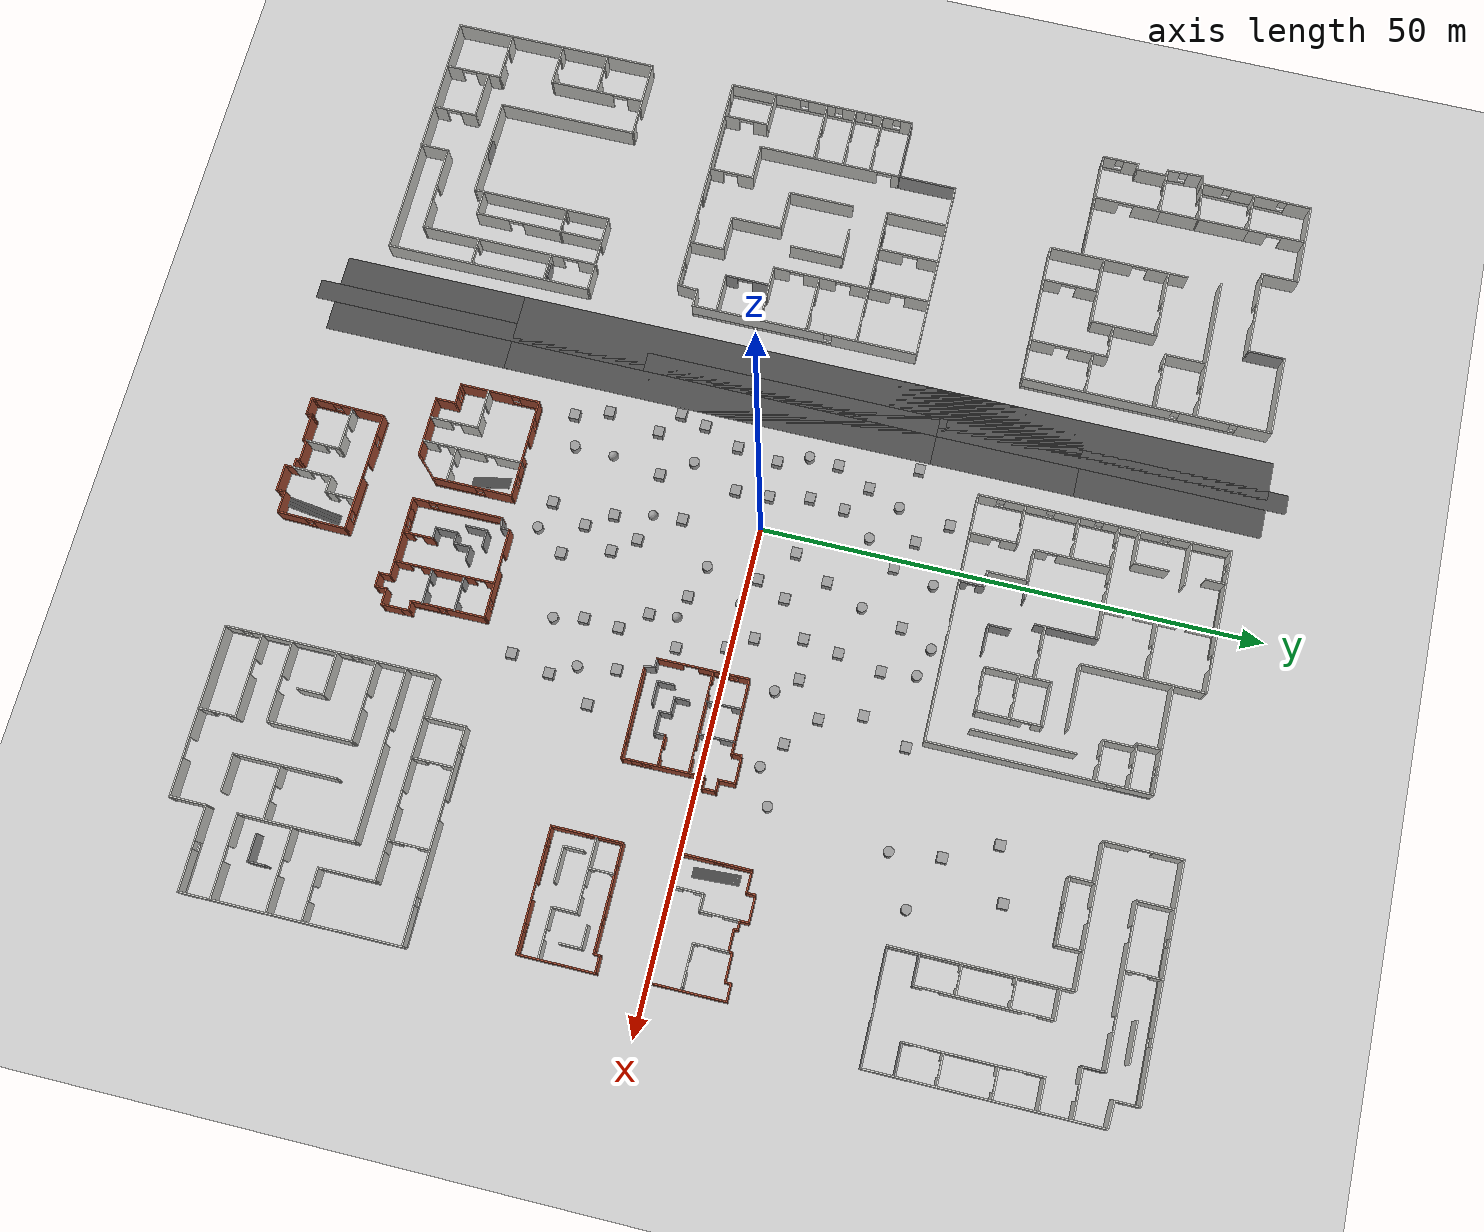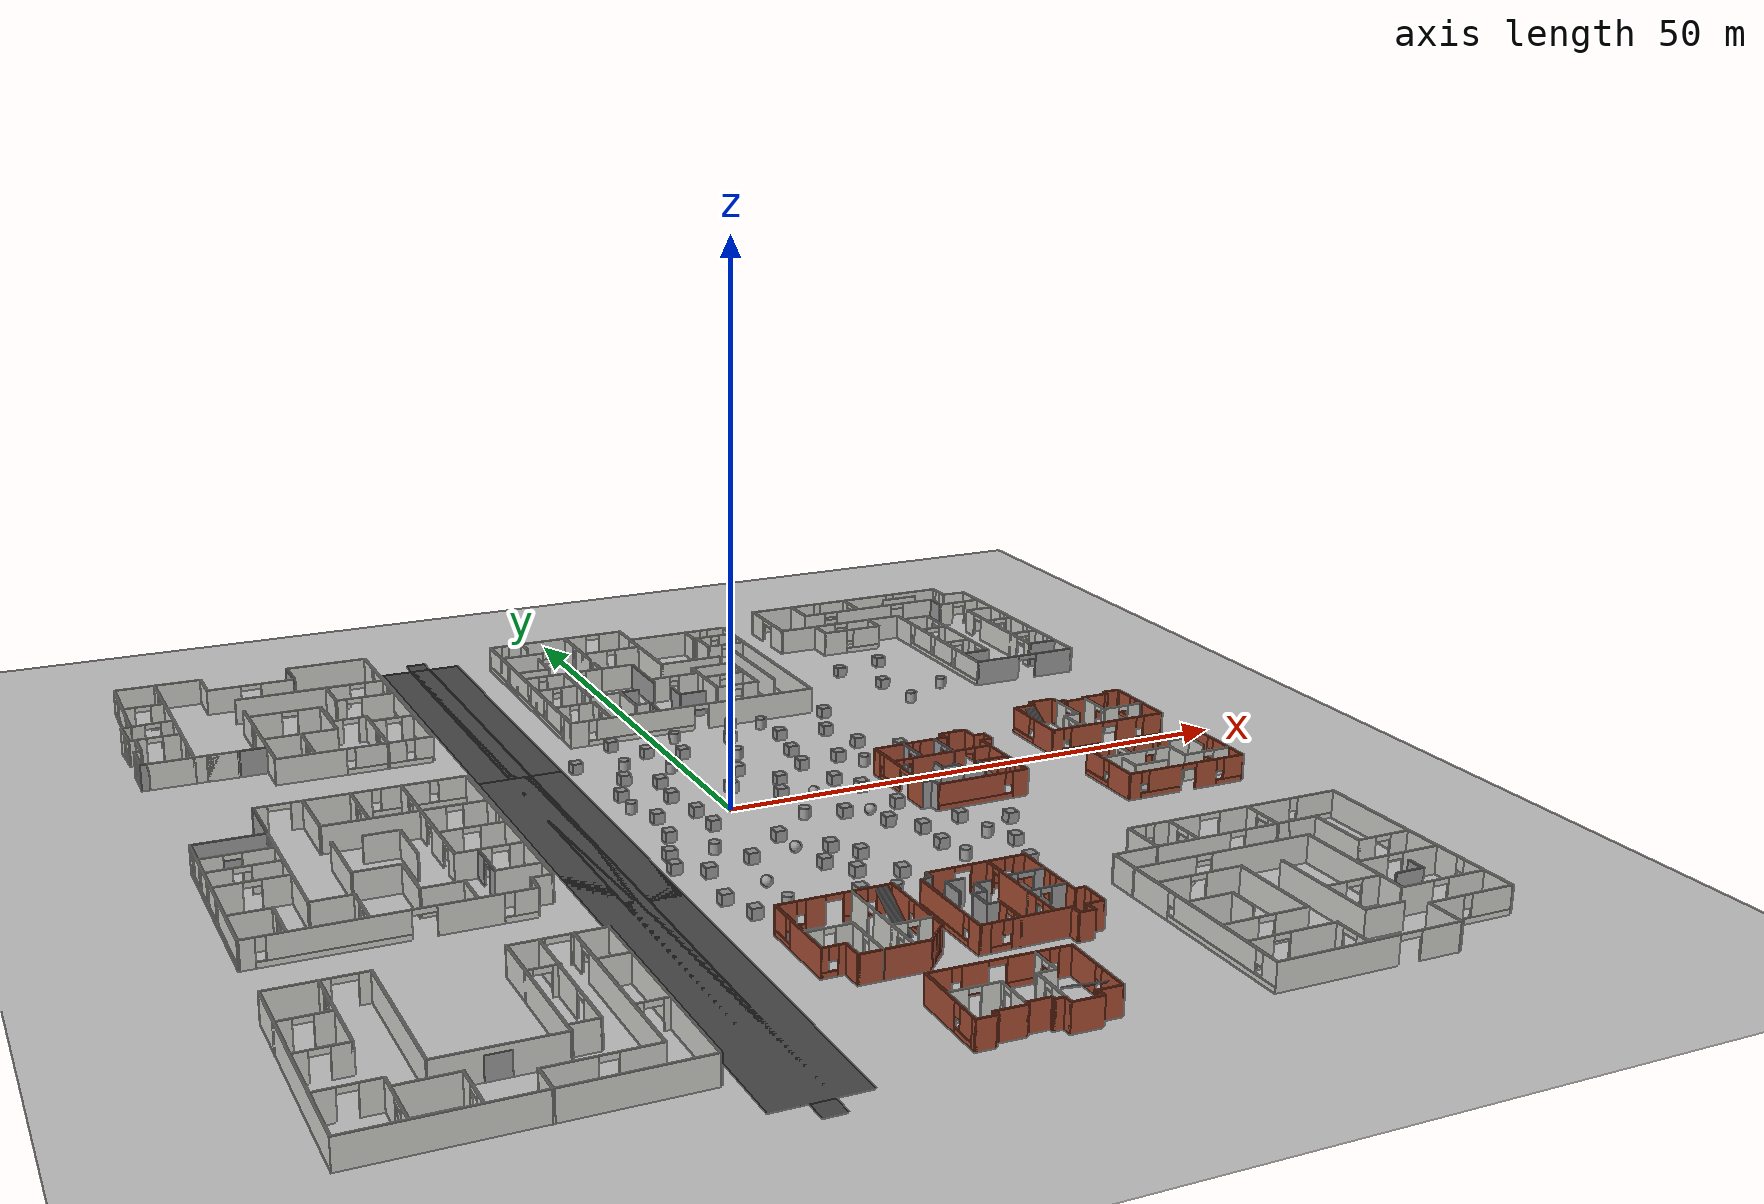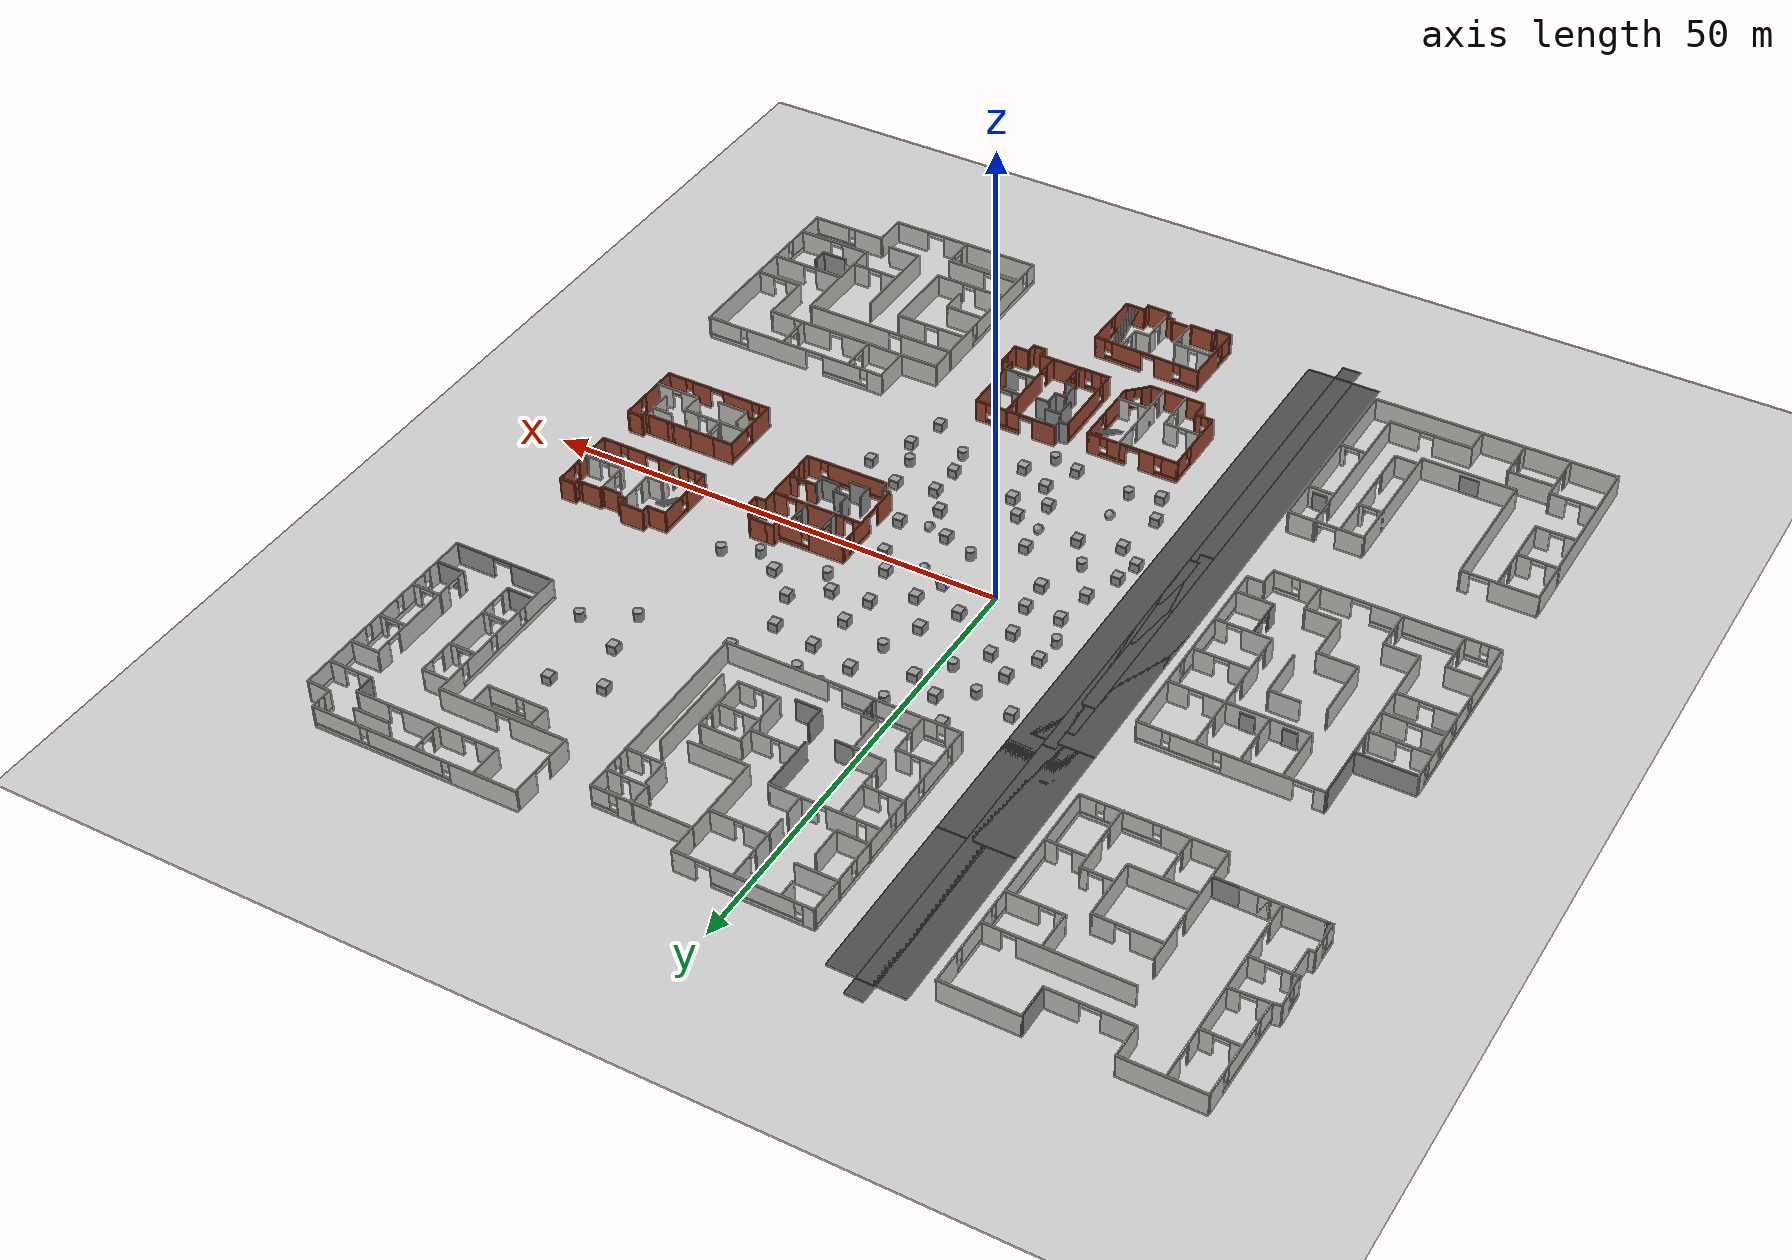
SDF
<sdf version="1.6">
 <world name="default">
  <light name="sun" type="directional">
   <pose>0 0 10 0 -0 0</pose>
   <diffuse>0.8 0.8 0.8 1</diffuse>
   <specular>0.2 0.2 0.2 1</specular>
   <attenuation>
    <range>1000</range>
    <constant>0.9</constant>
    <linear>0.01</linear>
    <quadratic>0.001</quadratic>
   </attenuation>
   <direction>-0.5 0.1 -0.9</direction>
  </light>
  <model name="ground_plane">
   <static>1</static>
   <link name="link">
    <collision name="collision">
     <geometry><plane><normal>0 0 1</normal><size>100 100</size></plane></geometry>
     <surface><friction><ode><mu>100</mu><mu2>50</mu2></ode></friction></surface>
    </collision>
    <visual name="visual">
     <cast_shadows>0</cast_shadows>
     <geometry><plane><normal>0 0 1</normal><size>100 100</size></plane></geometry>
     <material>
      <script><uri>file://media/materials/scripts/gazebo.material</uri><name>Gazebo/Grey</name></script>
     </material>
    </visual>
   </link>
  </model>
  <model name="road_segment">
   <pose>-14.5 0 0 0 -0 1.57</pose>
   <static>1</static>
   <link name="road">
    <collision name="collision">
     <geometry><box><size>96 8 0.001</size></box></geometry>
     <surface><friction><ode><mu>100</mu><mu2>50</mu2></ode></friction></surface>
    </collision>
    <visual name="visual">
     <geometry><box><size>96 8 0.001</size></box></geometry>
     <material>
      <script><uri>file://media/materials/scripts/gazebo.material</uri><name>Gazebo/Road</name></script>
     </material>
    </visual>
   </link>
   <link name="road1">
    <collision name="collision">
     <geometry><box><size>58.5 8 0.001</size></box></geometry>
     <surface><friction><ode><mu>100</mu><mu2>50</mu2></ode></friction></surface>
    </collision>
    <visual name="visual">
     <geometry><box><size>58.5 8 0.001</size></box></geometry>
     <material>
      <script><uri>file://media/materials/scripts/gazebo.material</uri><name>Gazebo/Road</name></script>
     </material>
    </visual>
   </link>
   <link name="road2">
    <collision name="collision">
     <geometry><box><size>29.5 8 0.001</size></box></geometry>
     <surface><friction><ode><mu>100</mu><mu2>50</mu2></ode></friction></surface>
    </collision>
    <visual name="visual">
     <geometry><box><size>29.5 8 0.001</size></box></geometry>
     <material>
      <script><uri>file://media/materials/scripts/gazebo.material</uri><name>Gazebo/Road</name></script>
     </material>
    </visual>
   </link>
   <link name="road3">
    <collision name="collision">
     <geometry><box><size>58.5 8 0.001</size></box></geometry>
     <surface><friction><ode><mu>100</mu><mu2>50</mu2></ode></friction></surface>
    </collision>
    <visual name="visual">
     <geometry><box><size>58.5 8 0.001</size></box></geometry>
     <material>
      <script><uri>file://media/materials/scripts/gazebo.material</uri><name>Gazebo/Road</name></script>
     </material>
    </visual>
   </link>
   <link name="road4">
    <collision name="collision">
     <geometry><box><size>100 2 0.001</size></box></geometry>
     <surface><friction><ode><mu>100</mu><mu2>50</mu2></ode></friction></surface>
    </collision>
    <visual name="visual">
     <geometry><box><size>100 2 0.001</size></box></geometry>
     <material>
      <script><uri>file://media/materials/scripts/gazebo.material</uri><name>Gazebo/Road</name></script>
     </material>
    </visual>
   </link>
   <link name="road5">
    <collision name="collision">
     <geometry><box><size>100 2 0.001</size></box></geometry>
     <surface><friction><ode><mu>100</mu><mu2>50</mu2></ode></friction></surface>
    </collision>
    <visual name="visual">
     <geometry><box><size>100 2 0.001</size></box></geometry>
     <material>
      <script><uri>file://media/materials/scripts/gazebo.material</uri><name>Gazebo/Road</name></script>
     </material>
    </visual>
   </link>
   <link name="road6">
    <collision name="collision">
     <geometry><box><size>96 2 0.001</size></box></geometry>
     <surface><friction><ode><mu>100</mu><mu2>50</mu2></ode></friction></surface>
    </collision>
    <visual name="visual">
     <geometry><box><size>96 2 0.001</size></box></geometry>
     <material>
      <script><uri>file://media/materials/scripts/gazebo.material</uri><name>Gazebo/Road</name></script>
     </material>
    </visual>
   </link>
   <link name="road7">
    <collision name="collision">
     <geometry><box><size>96 2 0.001</size></box></geometry>
     <surface><friction><ode><mu>100</mu><mu2>50</mu2></ode></friction></surface>
    </collision>
    <visual name="visual">
     <geometry><box><size>96 2 0.001</size></box></geometry>
     <material>
      <script><uri>file://media/materials/scripts/gazebo.material</uri><name>Gazebo/Road</name></script>
     </material>
    </visual>
   </link>
   <link name="road8">
    <collision name="collision">
     <geometry><box><size>31 2 0.001</size></box></geometry>
     <surface><friction><ode><mu>100</mu><mu2>50</mu2></ode></friction></surface>
    </collision>
    <visual name="visual">
     <geometry><box><size>31 2 0.001</size></box></geometry>
     <material>
      <script><uri>file://media/materials/scripts/gazebo.material</uri><name>Gazebo/Road</name></script>
     </material>
    </visual>
   </link>
   <link name="road9">
    <collision name="collision">
     <geometry><box><size>26 2 0.001</size></box></geometry>
     <surface><friction><ode><mu>100</mu><mu2>50</mu2></ode></friction></surface>
    </collision>
    <visual name="visual">
     <geometry><box><size>26 2 0.001</size></box></geometry>
     <material>
      <script><uri>file://media/materials/scripts/gazebo.material</uri><name>Gazebo/Road</name></script>
     </material>
    </visual>
   </link>
   <link name="road10">
    <collision name="collision">
     <geometry><box><size>28.5 2 0.001</size></box></geometry>
     <surface><friction><ode><mu>100</mu><mu2>50</mu2></ode></friction></surface>
    </collision>
    <visual name="visual">
     <geometry><box><size>28.5 2 0.001</size></box></geometry>
     <material>
      <script><uri>file://media/materials/scripts/gazebo.material</uri><name>Gazebo/Road</name></script>
     </material>
    </visual>
   </link>
   <link name="road11">
    <collision name="collision">
     <geometry><box><size>29.5 2 0.001</size></box></geometry>
     <surface><friction><ode><mu>100</mu><mu2>50</mu2></ode></friction></surface>
    </collision>
    <visual name="visual">
     <geometry><box><size>29.5 2 0.001</size></box></geometry>
     <material>
      <script><uri>file://media/materials/scripts/gazebo.material</uri><name>Gazebo/Road</name></script>
     </material>
    </visual>
   </link>
   <link name="road12">
    <collision name="collision">
     <geometry><box><size>23 2 0.001</size></box></geometry>
     <surface><friction><ode><mu>100</mu><mu2>50</mu2></ode></friction></surface>
    </collision>
    <visual name="visual">
     <geometry><box><size>23 2 0.001</size></box></geometry>
     <material>
      <script><uri>file://media/materials/scripts/gazebo.material</uri><name>Gazebo/Road</name></script>
     </material>
    </visual>
   </link>
   <link name="road13">
    <collision name="collision">
     <geometry><box><size>18 2 0.001</size></box></geometry>
     <surface><friction><ode><mu>100</mu><mu2>50</mu2></ode></friction></surface>
    </collision>
    <visual name="visual">
     <geometry><box><size>18 2 0.001</size></box></geometry>
     <material>
      <script><uri>file://media/materials/scripts/gazebo.material</uri><name>Gazebo/Road</name></script>
     </material>
    </visual>
   </link>
  </model>
  <gravity>0 0 -9.8</gravity>
  <magnetic_field>6e-06 2.3e-05 -4.2e-05</magnetic_field>
  <atmosphere type="adiabatic"/>
  <physics name="default_physics" default="0" type="ode">
   <max_step_size>0.001</max_step_size>
   <real_time_factor>1</real_time_factor>
   <real_time_update_rate>1000</real_time_update_rate>
  </physics>
  <scene><ambient>0.4 0.4 0.4 1</ambient><background>0.7 0.7 0.7 1</background><shadows>1</shadows></scene>
  <spherical_coordinates>
   <surface_model>EARTH_WGS84</surface_model>
   <latitude_deg>0</latitude_deg>
   <longitude_deg>0</longitude_deg>
   <elevation>0</elevation>
   <heading_deg>0</heading_deg>
  </spherical_coordinates>
  <model name="Multi_25_6">
   <pose>35.1581 33.1773 0 0 -0 0</pose>
   <link name="Wall_168">
    <pose>-1.27401 12.5 0 0 -0 0</pose>
    <visual name="Wall_168_Visual_0">
     <pose>-7.61112 0 1.25 0 -0 0</pose>
     <geometry><box><size>7.42777 0.15 2.5</size></box></geometry>
     <material>
      <script><uri>file://media/materials/scripts/gazebo.material</uri><name>Gazebo/CeilingTiled</name></script>
      <ambient>1 1 1 1</ambient>
     </material>
     <meta><layer>0</layer></meta>
    </visual>
    <collision name="Wall_168_Collision_0">
     <geometry><box><size>7.42777 0.15 2.5</size></box></geometry>
     <pose>-7.61112 0 1.25 0 -0 0</pose>
    </collision>
    <visual name="Wall_168_Visual_1">
     <pose>3.71388 0 0.25 0 -0 0</pose>
     <geometry><box><size>15.2222 0.15 0.5</size></box></geometry>
     <material>
      <script><uri>file://media/materials/scripts/gazebo.material</uri><name>Gazebo/CeilingTiled</name></script>
      <ambient>1 1 1 1</ambient>
     </material>
     <meta><layer>0</layer></meta>
    </visual>
    <collision name="Wall_168_Collision_1">
     <geometry><box><size>15.2222 0.15 0.5</size></box></geometry>
     <pose>3.71388 0 0.25 0 -0 0</pose>
    </collision>
    <visual name="Wall_168_Visual_2">
     <pose>1.03498 0 1.5 0 -0 0</pose>
     <geometry><box><size>8.26441 0.15 2</size></box></geometry>
     <material>
      <script><uri>file://media/materials/scripts/gazebo.material</uri><name>Gazebo/CeilingTiled</name></script>
      <ambient>1 1 1 1</ambient>
     </material>
     <meta><layer>0</layer></meta>
    </visual>
    <collision name="Wall_168_Collision_2">
     <geometry><box><size>8.26441 0.15 2</size></box></geometry>
     <pose>1.03498 0 1.5 0 -0 0</pose>
    </collision>
    <visual name="Wall_168_Visual_3">
     <pose>8.64609 0 1.5 0 -0 0</pose>
     <geometry><box><size>5.35782 0.15 2</size></box></geometry>
     <material>
      <script><uri>file://media/materials/scripts/gazebo.material</uri><name>Gazebo/CeilingTiled</name></script>
      <ambient>1 1 1 1</ambient>
     </material>
     <meta><layer>0</layer></meta>
    </visual>
    <collision name="Wall_168_Collision_3">
     <geometry><box><size>5.35782 0.15 2</size></box></geometry>
     <pose>8.64609 0 1.5 0 -0 0</pose>
    </collision>
    <visual name="Wall_168_Visual_4">
     <pose>-3.49723 0 1.9 0 -0 0</pose>
     <geometry><box><size>0.8 0.15 1.2</size></box></geometry>
     <material>
      <script><uri>file://media/materials/scripts/gazebo.material</uri><name>Gazebo/CeilingTiled</name></script>
      <ambient>1 1 1 1</ambient>
     </material>
     <meta><layer>0</layer></meta>
    </visual>
    <collision name="Wall_168_Collision_4">
     <geometry><box><size>0.8 0.15 1.2</size></box></geometry>
     <pose>-3.49723 0 1.9 0 -0 0</pose>
    </collision>
    <visual name="Wall_168_Visual_5">
     <pose>5.56718 0 1.9 0 -0 0</pose>
     <geometry><box><size>0.8 0.15 1.2</size></box></geometry>
     <material>
      <script><uri>file://media/materials/scripts/gazebo.material</uri><name>Gazebo/CeilingTiled</name></script>
      <ambient>1 1 1 1</ambient>
     </material>
     <meta><layer>0</layer></meta>
    </visual>
    <collision name="Wall_168_Collision_5">
     <geometry><box><size>0.8 0.15 1.2</size></box></geometry>
     <pose>5.56718 0 1.9 0 -0 0</pose>
    </collision>
   </link>
   <link name="Wall_170">
    <pose>-12.524 8.743 0 0 -0 -1.5708</pose>
    <visual name="Wall_170_Visual_0">
     <pose>-2.38097 0 1.25 0 -0 0</pose>
     <geometry><box><size>2.90205 0.15 2.5</size></box></geometry>
     <material>
      <script><uri>file://media/materials/scripts/gazebo.material</uri><name>Gazebo/CeilingTiled</name></script>
      <ambient>1 1 1 1</ambient>
     </material>
     <meta><layer>0</layer></meta>
    </visual>
    <collision name="Wall_170_Collision_0">
     <geometry><box><size>2.90205 0.15 2.5</size></box></geometry>
     <pose>-2.38097 0 1.25 0 -0 0</pose>
    </collision>
    <visual name="Wall_170_Visual_1">
     <pose>2.45103 0 1.25 0 -0 0</pose>
     <geometry><box><size>2.76195 0.15 2.5</size></box></geometry>
     <material>
      <script><uri>file://media/materials/scripts/gazebo.material</uri><name>Gazebo/CeilingTiled</name></script>
      <ambient>1 1 1 1</ambient>
     </material>
     <meta><layer>0</layer></meta>
    </visual>
    <collision name="Wall_170_Collision_1">
     <geometry><box><size>2.76195 0.15 2.5</size></box></geometry>
     <pose>2.45103 0 1.25 0 -0 0</pose>
    </collision>
    <visual name="Wall_170_Visual_2">
     <pose>0.070053 0 2.25 0 -0 0</pose>
     <geometry><box><size>2 0.15 0.5</size></box></geometry>
     <material>
      <script><uri>file://media/materials/scripts/gazebo.material</uri><name>Gazebo/CeilingTiled</name></script>
      <ambient>1 1 1 1</ambient>
     </material>
     <meta><layer>0</layer></meta>
    </visual>
    <collision name="Wall_170_Collision_2">
     <geometry><box><size>2 0.15 0.5</size></box></geometry>
     <pose>0.070053 0 2.25 0 -0 0</pose>
    </collision>
   </link>
   <link name="Wall_171">
    <pose>-5.56134 4.98605 0 0 -0 7e-06</pose>
    <visual name="Wall_171_Visual_0">
     <pose>-3.898 0 1.25 0 -0 0</pose>
     <geometry><box><size>6.27934 0.15 2.5</size></box></geometry>
     <material>
      <script><uri>file://media/materials/scripts/gazebo.material</uri><name>Gazebo/CeilingTiled</name></script>
      <ambient>1 1 1 1</ambient>
     </material>
     <meta><layer>0</layer></meta>
    </visual>
    <collision name="Wall_171_Collision_0">
     <geometry><box><size>6.27934 0.15 2.5</size></box></geometry>
     <pose>-3.898 0 1.25 0 -0 0</pose>
    </collision>
    <visual name="Wall_171_Visual_1">
     <pose>3.88967 0 1.25 0 -0 0</pose>
     <geometry><box><size>6.29601 0.15 2.5</size></box></geometry>
     <material>
      <script><uri>file://media/materials/scripts/gazebo.material</uri><name>Gazebo/CeilingTiled</name></script>
      <ambient>1 1 1 1</ambient>
     </material>
     <meta><layer>0</layer></meta>
    </visual>
    <collision name="Wall_171_Collision_1">
     <geometry><box><size>6.29601 0.15 2.5</size></box></geometry>
     <pose>3.88967 0 1.25 0 -0 0</pose>
    </collision>
    <visual name="Wall_171_Visual_2">
     <pose>-0.008335 0 2.25 0 -0 0</pose>
     <geometry><box><size>1.5 0.15 0.5</size></box></geometry>
     <material>
      <script><uri>file://media/materials/scripts/gazebo.material</uri><name>Gazebo/CeilingTiled</name></script>
      <ambient>1 1 1 1</ambient>
     </material>
     <meta><layer>0</layer></meta>
    </visual>
    <collision name="Wall_171_Collision_2">
     <geometry><box><size>1.5 0.15 0.5</size></box></geometry>
     <pose>-0.008335 0 2.25 0 -0 0</pose>
    </collision>
   </link>
   <link name="Wall_172">
    <pose>1.40116 -3.75695 0 0 -0 -1.57082</pose>
    <visual name="Wall_172_Visual_0">
     <pose>-7.15342 0 1.25 0 -0 0</pose>
     <geometry><box><size>3.32925 0.15 2.5</size></box></geometry>
     <material>
      <script><uri>file://media/materials/scripts/gazebo.material</uri><name>Gazebo/CeilingTiled</name></script>
      <ambient>1 1 1 1</ambient>
     </material>
     <meta><layer>0</layer></meta>
    </visual>
    <collision name="Wall_172_Collision_0">
     <geometry><box><size>3.32925 0.15 2.5</size></box></geometry>
     <pose>-7.15342 0 1.25 0 -0 0</pose>
    </collision>
    <visual name="Wall_172_Visual_1">
     <pose>1.66463 0 0.25 0 -0 0</pose>
     <geometry><box><size>14.3068 0.15 0.5</size></box></geometry>
     <material>
      <script><uri>file://media/materials/scripts/gazebo.material</uri><name>Gazebo/CeilingTiled</name></script>
      <ambient>1 1 1 1</ambient>
     </material>
     <meta><layer>0</layer></meta>
    </visual>
    <collision name="Wall_172_Collision_1">
     <geometry><box><size>14.3068 0.15 0.5</size></box></geometry>
     <pose>1.66463 0 0.25 0 -0 0</pose>
    </collision>
    <visual name="Wall_172_Visual_2">
     <pose>-2.86831 0 1.5 0 -0 0</pose>
     <geometry><box><size>3.64096 0.15 2</size></box></geometry>
     <material>
      <script><uri>file://media/materials/scripts/gazebo.material</uri><name>Gazebo/CeilingTiled</name></script>
      <ambient>1 1 1 1</ambient>
     </material>
     <meta><layer>0</layer></meta>
    </visual>
    <collision name="Wall_172_Collision_2">
     <geometry><box><size>3.64096 0.15 2</size></box></geometry>
     <pose>-2.86831 0 1.5 0 -0 0</pose>
    </collision>
    <visual name="Wall_172_Visual_3">
     <pose>1.60306 0 1.5 0 -0 0</pose>
     <geometry><box><size>3.70179 0.15 2</size></box></geometry>
     <material>
      <script><uri>file://media/materials/scripts/gazebo.material</uri><name>Gazebo/CeilingTiled</name></script>
      <ambient>1 1 1 1</ambient>
     </material>
     <meta><layer>0</layer></meta>
    </visual>
    <collision name="Wall_172_Collision_3">
     <geometry><box><size>3.70179 0.15 2</size></box></geometry>
     <pose>1.60306 0 1.5 0 -0 0</pose>
    </collision>
    <visual name="Wall_172_Visual_4">
     <pose>6.536 0 1.5 0 -0 0</pose>
     <geometry><box><size>4.56409 0.15 2</size></box></geometry>
     <material>
      <script><uri>file://media/materials/scripts/gazebo.material</uri><name>Gazebo/CeilingTiled</name></script>
      <ambient>1 1 1 1</ambient>
     </material>
     <meta><layer>0</layer></meta>
    </visual>
    <collision name="Wall_172_Collision_4">
     <geometry><box><size>4.56409 0.15 2</size></box></geometry>
     <pose>6.536 0 1.5 0 -0 0</pose>
    </collision>
    <visual name="Wall_172_Visual_5">
     <pose>-5.08879 0 1.9 0 -0 0</pose>
     <geometry><box><size>0.8 0.15 1.2</size></box></geometry>
     <material>
      <script><uri>file://media/materials/scripts/gazebo.material</uri><name>Gazebo/CeilingTiled</name></script>
      <ambient>1 1 1 1</ambient>
     </material>
     <meta><layer>0</layer></meta>
    </visual>
    <collision name="Wall_172_Collision_5">
     <geometry><box><size>0.8 0.15 1.2</size></box></geometry>
     <pose>-5.08879 0 1.9 0 -0 0</pose>
    </collision>
    <visual name="Wall_172_Visual_6">
     <pose>-0.647836 0 1.9 0 -0 0</pose>
     <geometry><box><size>0.8 0.15 1.2</size></box></geometry>
     <material>
      <script><uri>file://media/materials/scripts/gazebo.material</uri><name>Gazebo/CeilingTiled</name></script>
      <ambient>1 1 1 1</ambient>
     </material>
     <meta><layer>0</layer></meta>
    </visual>
    <collision name="Wall_172_Collision_6">
     <geometry><box><size>0.8 0.15 1.2</size></box></geometry>
     <pose>-0.647836 0 1.9 0 -0 0</pose>
    </collision>
    <visual name="Wall_172_Visual_7">
     <pose>3.85395 0 1.9 0 -0 0</pose>
     <geometry><box><size>0.8 0.15 1.2</size></box></geometry>
     <material>
      <script><uri>file://media/materials/scripts/gazebo.material</uri><name>Gazebo/CeilingTiled</name></script>
      <ambient>1 1 1 1</ambient>
     </material>
     <meta><layer>0</layer></meta>
    </visual>
    <collision name="Wall_172_Collision_7">
     <geometry><box><size>0.8 0.15 1.2</size></box></geometry>
     <pose>3.85395 0 1.9 0 -0 0</pose>
    </collision>
   </link>
   <link name="Wall_173">
    <pose>6.95099 -12.5 0 0 -0 0</pose>
    <visual name="Wall_173_Visual_0">
     <pose>-3.18207 0 1.25 0 -0 0</pose>
     <geometry><box><size>4.88587 0.15 2.5</size></box></geometry>
     <material>
      <script><uri>file://media/materials/scripts/gazebo.material</uri><name>Gazebo/Grey</name></script>
      <ambient>1 1 1 1</ambient>
     </material>
     <meta><layer>0</layer></meta>
    </visual>
    <collision name="Wall_173_Collision_0">
     <geometry><box><size>4.88587 0.15 2.5</size></box></geometry>
     <pose>-3.18207 0 1.25 0 -0 0</pose>
    </collision>
    <visual name="Wall_173_Visual_1">
     <pose>3.44293 0 1.25 0 -0 0</pose>
     <geometry><box><size>4.36413 0.15 2.5</size></box></geometry>
     <material>
      <script><uri>file://media/materials/scripts/gazebo.material</uri><name>Gazebo/Grey</name></script>
      <ambient>1 1 1 1</ambient>
     </material>
     <meta><layer>0</layer></meta>
    </visual>
    <collision name="Wall_173_Collision_1">
     <geometry><box><size>4.36413 0.15 2.5</size></box></geometry>
     <pose>3.44293 0 1.25 0 -0 0</pose>
    </collision>
    <visual name="Wall_173_Visual_2">
     <pose>0.260866 0 2.25 0 -0 0</pose>
     <geometry><box><size>2 0.15 0.5</size></box></geometry>
     <material>
      <script><uri>file://media/materials/scripts/gazebo.material</uri><name>Gazebo/Grey</name></script>
      <ambient>1 1 1 1</ambient>
     </material>
     <meta><layer>0</layer></meta>
    </visual>
    <collision name="Wall_173_Collision_2">
     <geometry><box><size>2 0.15 0.5</size></box></geometry>
     <pose>0.260866 0 2.25 0 -0 0</pose>
    </collision>
   </link>
   <link name="Wall_174">
    <pose>12.501 -1.25 0 0 -0 1.5708</pose>
    <visual name="Wall_174_Visual_0">
     <pose>-9.04295 0 1.25 0 -0 0</pose>
     <geometry><box><size>4.56409 0.15 2.5</size></box></geometry>
     <material>
      <script><uri>file://media/materials/scripts/gazebo.material</uri><name>Gazebo/CeilingTiled</name></script>
      <ambient>1 1 1 1</ambient>
     </material>
     <meta><layer>0</layer></meta>
    </visual>
    <collision name="Wall_174_Collision_0">
     <geometry><box><size>4.56409 0.15 2.5</size></box></geometry>
     <pose>-9.04295 0 1.25 0 -0 0</pose>
    </collision>
    <visual name="Wall_174_Visual_1">
     <pose>2.28205 0 0.25 0 -0 0</pose>
     <geometry><box><size>18.0859 0.15 0.5</size></box></geometry>
     <material>
      <script><uri>file://media/materials/scripts/gazebo.material</uri><name>Gazebo/CeilingTiled</name></script>
      <ambient>1 1 1 1</ambient>
     </material>
     <meta><layer>0</layer></meta>
    </visual>
    <collision name="Wall_174_Collision_1">
     <geometry><box><size>18.0859 0.15 0.5</size></box></geometry>
     <pose>2.28205 0 0.25 0 -0 0</pose>
    </collision>
    <visual name="Wall_174_Visual_2">
     <pose>-4.2621 0 1.5 0 -0 0</pose>
     <geometry><box><size>3.39762 0.15 2</size></box></geometry>
     <material>
      <script><uri>file://media/materials/scripts/gazebo.material</uri><name>Gazebo/CeilingTiled</name></script>
      <ambient>1 1 1 1</ambient>
     </material>
     <meta><layer>0</layer></meta>
    </visual>
    <collision name="Wall_174_Collision_2">
     <geometry><box><size>3.39762 0.15 2</size></box></geometry>
     <pose>-4.2621 0 1.5 0 -0 0</pose>
    </collision>
    <visual name="Wall_174_Visual_3">
     <pose>0.209274 0 1.5 0 -0 0</pose>
     <geometry><box><size>3.94513 0.15 2</size></box></geometry>
     <material>
      <script><uri>file://media/materials/scripts/gazebo.material</uri><name>Gazebo/CeilingTiled</name></script>
      <ambient>1 1 1 1</ambient>
     </material>
     <meta><layer>0</layer></meta>
    </visual>
    <collision name="Wall_174_Collision_3">
     <geometry><box><size>3.94513 0.15 2</size></box></geometry>
     <pose>0.209274 0 1.5 0 -0 0</pose>
    </collision>
    <visual name="Wall_174_Visual_4">
     <pose>7.15342 0 1.5 0 -0 0</pose>
     <geometry><box><size>8.34316 0.15 2</size></box></geometry>
     <material>
      <script><uri>file://media/materials/scripts/gazebo.material</uri><name>Gazebo/CeilingTiled</name></script>
      <ambient>1 1 1 1</ambient>
     </material>
     <meta><layer>0</layer></meta>
    </visual>
    <collision name="Wall_174_Collision_4">
     <geometry><box><size>8.34316 0.15 2</size></box></geometry>
     <pose>7.15342 0 1.5 0 -0 0</pose>
    </collision>
    <visual name="Wall_174_Visual_5">
     <pose>-6.36091 0 1.9 0 -0 0</pose>
     <geometry><box><size>0.8 0.15 1.2</size></box></geometry>
     <material>
      <script><uri>file://media/materials/scripts/gazebo.material</uri><name>Gazebo/CeilingTiled</name></script>
      <ambient>1 1 1 1</ambient>
     </material>
     <meta><layer>0</layer></meta>
    </visual>
    <collision name="Wall_174_Collision_5">
     <geometry><box><size>0.8 0.15 1.2</size></box></geometry>
     <pose>-6.36091 0 1.9 0 -0 0</pose>
    </collision>
    <visual name="Wall_174_Visual_6">
     <pose>-2.16329 0 1.9 0 -0 0</pose>
     <geometry><box><size>0.8 0.15 1.2</size></box></geometry>
     <material>
      <script><uri>file://media/materials/scripts/gazebo.material</uri><name>Gazebo/CeilingTiled</name></script>
      <ambient>1 1 1 1</ambient>
     </material>
     <meta><layer>0</layer></meta>
    </visual>
    <collision name="Wall_174_Collision_6">
     <geometry><box><size>0.8 0.15 1.2</size></box></geometry>
     <pose>-2.16329 0 1.9 0 -0 0</pose>
    </collision>
    <visual name="Wall_174_Visual_7">
     <pose>2.58184 0 1.9 0 -0 0</pose>
     <geometry><box><size>0.8 0.15 1.2</size></box></geometry>
     <material>
      <script><uri>file://media/materials/scripts/gazebo.material</uri><name>Gazebo/CeilingTiled</name></script>
      <ambient>1 1 1 1</ambient>
     </material>
     <meta><layer>0</layer></meta>
    </visual>
    <collision name="Wall_174_Collision_7">
     <geometry><box><size>0.8 0.15 1.2</size></box></geometry>
     <pose>2.58184 0 1.9 0 -0 0</pose>
    </collision>
   </link>
   <link name="Wall_176">
    <collision name="Wall_176_Collision">
     <geometry><box><size>3 0.15 2.5</size></box></geometry>
     <pose>0 0 1.25 0 -0 0</pose>
    </collision>
    <visual name="Wall_176_Visual">
     <pose>0 0 1.25 0 -0 0</pose>
     <geometry><box><size>3 0.15 2.5</size></box></geometry>
     <material>
      <script><uri>file://media/materials/scripts/gazebo.material</uri><name>Gazebo/CeilingTiled</name></script>
      <ambient>1 1 1 1</ambient>
     </material>
     <meta><layer>0</layer></meta>
    </visual>
    <pose>2.91134 3.64055 0 0 -0 0</pose>
   </link>
   <link name="Wall_177">
    <pose>4.33634 -2.90945 0 0 -0 -1.5708</pose>
    <visual name="Wall_177_Visual_0">
     <pose>-5.91337 0 1.25 0 -0 0</pose>
     <geometry><box><size>1.42326 0.15 2.5</size></box></geometry>
     <material>
      <script><uri>file://media/materials/scripts/gazebo.material</uri><name>Gazebo/CeilingTiled</name></script>
      <ambient>1 1 1 1</ambient>
     </material>
     <meta><layer>0</layer></meta>
    </visual>
    <collision name="Wall_177_Collision_0">
     <geometry><box><size>1.42326 0.15 2.5</size></box></geometry>
     <pose>-5.91337 0 1.25 0 -0 0</pose>
    </collision>
    <visual name="Wall_177_Visual_1">
     <pose>0.175864 0 1.25 0 -0 0</pose>
     <geometry><box><size>7.7552 0.15 2.5</size></box></geometry>
     <material>
      <script><uri>file://media/materials/scripts/gazebo.material</uri><name>Gazebo/CeilingTiled</name></script>
      <ambient>1 1 1 1</ambient>
     </material>
     <meta><layer>0</layer></meta>
    </visual>
    <collision name="Wall_177_Collision_1">
     <geometry><box><size>7.7552 0.15 2.5</size></box></geometry>
     <pose>0.175864 0 1.25 0 -0 0</pose>
    </collision>
    <visual name="Wall_177_Visual_2">
     <pose>6.08923 0 1.25 0 -0 0</pose>
     <geometry><box><size>1.07154 0.15 2.5</size></box></geometry>
     <material>
      <script><uri>file://media/materials/scripts/gazebo.material</uri><name>Gazebo/CeilingTiled</name></script>
      <ambient>1 1 1 1</ambient>
     </material>
     <meta><layer>0</layer></meta>
    </visual>
    <collision name="Wall_177_Collision_2">
     <geometry><box><size>1.07154 0.15 2.5</size></box></geometry>
     <pose>6.08923 0 1.25 0 -0 0</pose>
    </collision>
    <visual name="Wall_177_Visual_3">
     <pose>-4.45174 0 2.25 0 -0 0</pose>
     <geometry><box><size>1.5 0.15 0.5</size></box></geometry>
     <material>
      <script><uri>file://media/materials/scripts/gazebo.material</uri><name>Gazebo/CeilingTiled</name></script>
      <ambient>1 1 1 1</ambient>
     </material>
     <meta><layer>0</layer></meta>
    </visual>
    <collision name="Wall_177_Collision_3">
     <geometry><box><size>1.5 0.15 0.5</size></box></geometry>
     <pose>-4.45174 0 2.25 0 -0 0</pose>
    </collision>
    <visual name="Wall_177_Visual_4">
     <pose>4.80346 0 2.25 0 -0 0</pose>
     <geometry><box><size>1.5 0.15 0.5</size></box></geometry>
     <material>
      <script><uri>file://media/materials/scripts/gazebo.material</uri><name>Gazebo/CeilingTiled</name></script>
      <ambient>1 1 1 1</ambient>
     </material>
     <meta><layer>0</layer></meta>
    </visual>
    <collision name="Wall_177_Collision_4">
     <geometry><box><size>1.5 0.15 0.5</size></box></geometry>
     <pose>4.80346 0 2.25 0 -0 0</pose>
    </collision>
   </link>
   <link name="Wall_178">
    <collision name="Wall_178_Collision">
     <geometry><box><size>3 0.15 2.5</size></box></geometry>
     <pose>0 0 1.25 0 -0 0</pose>
    </collision>
    <visual name="Wall_178_Visual">
     <pose>0 0 1.25 0 -0 0</pose>
     <geometry><box><size>3 0.15 2.5</size></box></geometry>
     <material>
      <script><uri>file://media/materials/scripts/gazebo.material</uri><name>Gazebo/Grey</name></script>
      <ambient>1 1 1 1</ambient>
     </material>
     <meta><layer>0</layer></meta>
    </visual>
    <pose>2.91134 -9.45945 0 0 -0 3.14159</pose>
   </link>
   <link name="Wall_180">
    <pose>2.83153 -0.472315 0 0 -0 0</pose>
    <visual name="Wall_180_Visual_0">
     <pose>-1.15169 0 1.25 0 -0 0</pose>
     <geometry><box><size>0.696626 0.15 2.5</size></box></geometry>
     <material>
      <script><uri>file://media/materials/scripts/gazebo.material</uri><name>Gazebo/CeilingTiled</name></script>
      <ambient>1 1 1 1</ambient>
     </material>
     <meta><layer>0</layer></meta>
    </visual>
    <collision name="Wall_180_Collision_0">
     <geometry><box><size>0.696626 0.15 2.5</size></box></geometry>
     <pose>-1.15169 0 1.25 0 -0 0</pose>
    </collision>
    <visual name="Wall_180_Visual_1">
     <pose>1.09831 0 1.25 0 -0 0</pose>
     <geometry><box><size>0.803374 0.15 2.5</size></box></geometry>
     <material>
      <script><uri>file://media/materials/scripts/gazebo.material</uri><name>Gazebo/CeilingTiled</name></script>
      <ambient>1 1 1 1</ambient>
     </material>
     <meta><layer>0</layer></meta>
    </visual>
    <collision name="Wall_180_Collision_1">
     <geometry><box><size>0.803374 0.15 2.5</size></box></geometry>
     <pose>1.09831 0 1.25 0 -0 0</pose>
    </collision>
    <visual name="Wall_180_Visual_2">
     <pose>-0.053374 0 2.25 0 -0 0</pose>
     <geometry><box><size>1.5 0.15 0.5</size></box></geometry>
     <material>
      <script><uri>file://media/materials/scripts/gazebo.material</uri><name>Gazebo/CeilingTiled</name></script>
      <ambient>1 1 1 1</ambient>
     </material>
     <meta><layer>0</layer></meta>
    </visual>
    <collision name="Wall_180_Collision_2">
     <geometry><box><size>1.5 0.15 0.5</size></box></geometry>
     <pose>-0.053374 0 2.25 0 -0 0</pose>
    </collision>
   </link>
   <link name="Wall_182">
    <pose>2.83908 -5.52091 0 0 -0 0</pose>
    <visual name="Wall_182_Visual_0">
     <pose>-1.12522 0 1.25 0 -0 0</pose>
     <geometry><box><size>0.749566 0.15 2.5</size></box></geometry>
     <material>
      <script><uri>file://media/materials/scripts/gazebo.material</uri><name>Gazebo/CeilingTiled</name></script>
      <ambient>1 1 1 1</ambient>
     </material>
     <meta><layer>0</layer></meta>
    </visual>
    <collision name="Wall_182_Collision_0">
     <geometry><box><size>0.749566 0.15 2.5</size></box></geometry>
     <pose>-1.12522 0 1.25 0 -0 0</pose>
    </collision>
    <visual name="Wall_182_Visual_1">
     <pose>1.12478 0 1.25 0 -0 0</pose>
     <geometry><box><size>0.750434 0.15 2.5</size></box></geometry>
     <material>
      <script><uri>file://media/materials/scripts/gazebo.material</uri><name>Gazebo/CeilingTiled</name></script>
      <ambient>1 1 1 1</ambient>
     </material>
     <meta><layer>0</layer></meta>
    </visual>
    <collision name="Wall_182_Collision_1">
     <geometry><box><size>0.750434 0.15 2.5</size></box></geometry>
     <pose>1.12478 0 1.25 0 -0 0</pose>
    </collision>
    <visual name="Wall_182_Visual_2">
     <pose>-0.000434 0 2.25 0 -0 0</pose>
     <geometry><box><size>1.5 0.15 0.5</size></box></geometry>
     <material>
      <script><uri>file://media/materials/scripts/gazebo.material</uri><name>Gazebo/CeilingTiled</name></script>
      <ambient>1 1 1 1</ambient>
     </material>
     <meta><layer>0</layer></meta>
    </visual>
    <collision name="Wall_182_Collision_2">
     <geometry><box><size>1.5 0.15 0.5</size></box></geometry>
     <pose>-0.000434 0 2.25 0 -0 0</pose>
    </collision>
   </link>
   <link name="Wall_186">
    <collision name="Wall_186_Collision">
     <geometry><box><size>3.25 0.15 2.5</size></box></geometry>
     <pose>0 0 1.25 0 -0 0</pose>
    </collision>
    <visual name="Wall_186_Visual">
     <pose>0 0 1.25 0 -0 0</pose>
     <geometry><box><size>3.25 0.15 2.5</size></box></geometry>
     <material>
      <script><uri>file://media/materials/scripts/gazebo.material</uri><name>Gazebo/Grey</name></script>
      <ambient>1 1 1 1</ambient>
     </material>
     <meta><layer>0</layer></meta>
    </visual>
    <pose>10.974 -9.37782 0 0 -0 3.14159</pose>
   </link>
   <link name="Wall_187">
    <pose>9.42401 -2.82782 0 0 -0 1.5708</pose>
    <visual name="Wall_187_Visual_0">
     <pose>-6.0998 0 1.25 0 -0 0</pose>
     <geometry><box><size>1.05039 0.15 2.5</size></box></geometry>
     <material>
      <script><uri>file://media/materials/scripts/gazebo.material</uri><name>Gazebo/CeilingTiled</name></script>
      <ambient>1 1 1 1</ambient>
     </material>
     <meta><layer>0</layer></meta>
    </visual>
    <collision name="Wall_187_Collision_0">
     <geometry><box><size>1.05039 0.15 2.5</size></box></geometry>
     <pose>-6.0998 0 1.25 0 -0 0</pose>
    </collision>
    <visual name="Wall_187_Visual_1">
     <pose>-0.287744 0 1.25 0 -0 0</pose>
     <geometry><box><size>7.57372 0.15 2.5</size></box></geometry>
     <material>
      <script><uri>file://media/materials/scripts/gazebo.material</uri><name>Gazebo/CeilingTiled</name></script>
      <ambient>1 1 1 1</ambient>
     </material>
     <meta><layer>0</layer></meta>
    </visual>
    <collision name="Wall_187_Collision_1">
     <geometry><box><size>7.57372 0.15 2.5</size></box></geometry>
     <pose>-0.287744 0 1.25 0 -0 0</pose>
    </collision>
    <visual name="Wall_187_Visual_2">
     <pose>5.81206 0 1.25 0 -0 0</pose>
     <geometry><box><size>1.62588 0.15 2.5</size></box></geometry>
     <material>
      <script><uri>file://media/materials/scripts/gazebo.material</uri><name>Gazebo/CeilingTiled</name></script>
      <ambient>1 1 1 1</ambient>
     </material>
     <meta><layer>0</layer></meta>
    </visual>
    <collision name="Wall_187_Collision_2">
     <geometry><box><size>1.62588 0.15 2.5</size></box></geometry>
     <pose>5.81206 0 1.25 0 -0 0</pose>
    </collision>
    <visual name="Wall_187_Visual_3">
     <pose>-4.82461 0 2.25 0 -0 0</pose>
     <geometry><box><size>1.5 0.15 0.5</size></box></geometry>
     <material>
      <script><uri>file://media/materials/scripts/gazebo.material</uri><name>Gazebo/CeilingTiled</name></script>
      <ambient>1 1 1 1</ambient>
     </material>
     <meta><layer>0</layer></meta>
    </visual>
    <collision name="Wall_187_Collision_3">
     <geometry><box><size>1.5 0.15 0.5</size></box></geometry>
     <pose>-4.82461 0 2.25 0 -0 0</pose>
    </collision>
    <visual name="Wall_187_Visual_4">
     <pose>4.24912 0 2.25 0 -0 0</pose>
     <geometry><box><size>1.5 0.15 0.5</size></box></geometry>
     <material>
      <script><uri>file://media/materials/scripts/gazebo.material</uri><name>Gazebo/CeilingTiled</name></script>
      <ambient>1 1 1 1</ambient>
     </material>
     <meta><layer>0</layer></meta>
    </visual>
    <collision name="Wall_187_Collision_4">
     <geometry><box><size>1.5 0.15 0.5</size></box></geometry>
     <pose>4.24912 0 2.25 0 -0 0</pose>
    </collision>
   </link>
   <link name="Wall_188">
    <collision name="Wall_188_Collision">
     <geometry><box><size>3.25 0.15 2.5</size></box></geometry>
     <pose>0 0 1.25 0 -0 0</pose>
    </collision>
    <visual name="Wall_188_Visual">
     <pose>0 0 1.25 0 -0 0</pose>
     <geometry><box><size>3.25 0.15 2.5</size></box></geometry>
     <material>
      <script><uri>file://media/materials/scripts/gazebo.material</uri><name>Gazebo/CeilingTiled</name></script>
      <ambient>1 1 1 1</ambient>
     </material>
     <meta><layer>0</layer></meta>
    </visual>
    <pose>10.974 3.72218 0 0 -0 0</pose>
   </link>
   <link name="Wall_191">
    <pose>10.9623 -5.57124 0 0 -0 0</pose>
    <visual name="Wall_191_Visual_0">
     <pose>-1.21362 0 1.25 0 -0 0</pose>
     <geometry><box><size>0.822751 0.15 2.5</size></box></geometry>
     <material>
      <script><uri>file://media/materials/scripts/gazebo.material</uri><name>Gazebo/CeilingTiled</name></script>
      <ambient>1 1 1 1</ambient>
     </material>
     <meta><layer>0</layer></meta>
    </visual>
    <collision name="Wall_191_Collision_0">
     <geometry><box><size>0.822751 0.15 2.5</size></box></geometry>
     <pose>-1.21362 0 1.25 0 -0 0</pose>
    </collision>
    <visual name="Wall_191_Visual_1">
     <pose>1.16138 0 1.25 0 -0 0</pose>
     <geometry><box><size>0.927249 0.15 2.5</size></box></geometry>
     <material>
      <script><uri>file://media/materials/scripts/gazebo.material</uri><name>Gazebo/CeilingTiled</name></script>
      <ambient>1 1 1 1</ambient>
     </material>
     <meta><layer>0</layer></meta>
    </visual>
    <collision name="Wall_191_Collision_1">
     <geometry><box><size>0.927249 0.15 2.5</size></box></geometry>
     <pose>1.16138 0 1.25 0 -0 0</pose>
    </collision>
    <visual name="Wall_191_Visual_2">
     <pose>-0.052249 0 2.25 0 -0 0</pose>
     <geometry><box><size>1.5 0.15 0.5</size></box></geometry>
     <material>
      <script><uri>file://media/materials/scripts/gazebo.material</uri><name>Gazebo/CeilingTiled</name></script>
      <ambient>1 1 1 1</ambient>
     </material>
     <meta><layer>0</layer></meta>
    </visual>
    <collision name="Wall_191_Collision_2">
     <geometry><box><size>1.5 0.15 0.5</size></box></geometry>
     <pose>-0.052249 0 2.25 0 -0 0</pose>
    </collision>
   </link>
   <link name="Wall_193">
    <pose>10.9072 -0.499118 0 0 -0 0</pose>
    <visual name="Wall_193_Visual_0">
     <pose>-1.04587 0 1.25 0 -0 0</pose>
     <geometry><box><size>0.908261 0.15 2.5</size></box></geometry>
     <material>
      <script><uri>file://media/materials/scripts/gazebo.material</uri><name>Gazebo/CeilingTiled</name></script>
      <ambient>1 1 1 1</ambient>
     </material>
     <meta><layer>0</layer></meta>
    </visual>
    <collision name="Wall_193_Collision_0">
     <geometry><box><size>0.908261 0.15 2.5</size></box></geometry>
     <pose>-1.04587 0 1.25 0 -0 0</pose>
    </collision>
    <visual name="Wall_193_Visual_1">
     <pose>1.20413 0 1.25 0 -0 0</pose>
     <geometry><box><size>0.591739 0.15 2.5</size></box></geometry>
     <material>
      <script><uri>file://media/materials/scripts/gazebo.material</uri><name>Gazebo/CeilingTiled</name></script>
      <ambient>1 1 1 1</ambient>
     </material>
     <meta><layer>0</layer></meta>
    </visual>
    <collision name="Wall_193_Collision_1">
     <geometry><box><size>0.591739 0.15 2.5</size></box></geometry>
     <pose>1.20413 0 1.25 0 -0 0</pose>
    </collision>
    <visual name="Wall_193_Visual_2">
     <pose>0.158261 0 2.25 0 -0 0</pose>
     <geometry><box><size>1.5 0.15 0.5</size></box></geometry>
     <material>
      <script><uri>file://media/materials/scripts/gazebo.material</uri><name>Gazebo/CeilingTiled</name></script>
      <ambient>1 1 1 1</ambient>
     </material>
     <meta><layer>0</layer></meta>
    </visual>
    <collision name="Wall_193_Collision_2">
     <geometry><box><size>1.5 0.15 0.5</size></box></geometry>
     <pose>0.158261 0 2.25 0 -0 0</pose>
    </collision>
   </link>
   <link name="Wall_195">
    <collision name="Wall_195_Collision">
     <geometry><box><size>3.5 0.15 2.5</size></box></geometry>
     <pose>0 0 1.25 0 -0 0</pose>
    </collision>
    <visual name="Wall_195_Visual">
     <pose>0 0 1.25 0 -0 0</pose>
     <geometry><box><size>3.5 0.15 2.5</size></box></geometry>
     <material>
      <script><uri>file://media/materials/scripts/gazebo.material</uri><name>Gazebo/CeilingTiled</name></script>
      <ambient>1 1 1 1</ambient>
     </material>
     <meta><layer>0</layer></meta>
    </visual>
    <pose>-7.86946 10.6312 0 0 -0 -1.5708</pose>
   </link>
   <link name="Wall_196">
    <pose>-0.069455 8.95618 0 0 -0 0</pose>
    <visual name="Wall_196_Visual_0">
     <pose>-6.66941 0 1.25 0 -0 0</pose>
     <geometry><box><size>2.41117 0.15 2.5</size></box></geometry>
     <material>
      <script><uri>file://media/materials/scripts/gazebo.material</uri><name>Gazebo/CeilingTiled</name></script>
      <ambient>1 1 1 1</ambient>
     </material>
     <meta><layer>0</layer></meta>
    </visual>
    <collision name="Wall_196_Collision_0">
     <geometry><box><size>2.41117 0.15 2.5</size></box></geometry>
     <pose>-6.66941 0 1.25 0 -0 0</pose>
    </collision>
    <visual name="Wall_196_Visual_1">
     <pose>-0.600409 0 1.25 0 -0 0</pose>
     <geometry><box><size>6.72684 0.15 2.5</size></box></geometry>
     <material>
      <script><uri>file://media/materials/scripts/gazebo.material</uri><name>Gazebo/CeilingTiled</name></script>
      <ambient>1 1 1 1</ambient>
     </material>
     <meta><layer>0</layer></meta>
    </visual>
    <collision name="Wall_196_Collision_1">
     <geometry><box><size>6.72684 0.15 2.5</size></box></geometry>
     <pose>-0.600409 0 1.25 0 -0 0</pose>
    </collision>
    <visual name="Wall_196_Visual_2">
     <pose>6.06901 0 1.25 0 -0 0</pose>
     <geometry><box><size>3.61199 0.15 2.5</size></box></geometry>
     <material>
      <script><uri>file://media/materials/scripts/gazebo.material</uri><name>Gazebo/CeilingTiled</name></script>
      <ambient>1 1 1 1</ambient>
     </material>
     <meta><layer>0</layer></meta>
    </visual>
    <collision name="Wall_196_Collision_2">
     <geometry><box><size>3.61199 0.15 2.5</size></box></geometry>
     <pose>6.06901 0 1.25 0 -0 0</pose>
    </collision>
    <visual name="Wall_196_Visual_3">
     <pose>-4.71383 0 2.25 0 -0 0</pose>
     <geometry><box><size>1.5 0.15 0.5</size></box></geometry>
     <material>
      <script><uri>file://media/materials/scripts/gazebo.material</uri><name>Gazebo/CeilingTiled</name></script>
      <ambient>1 1 1 1</ambient>
     </material>
     <meta><layer>0</layer></meta>
    </visual>
    <collision name="Wall_196_Collision_3">
     <geometry><box><size>1.5 0.15 0.5</size></box></geometry>
     <pose>-4.71383 0 2.25 0 -0 0</pose>
    </collision>
    <visual name="Wall_196_Visual_4">
     <pose>3.51301 0 2.25 0 -0 0</pose>
     <geometry><box><size>1.5 0.15 0.5</size></box></geometry>
     <material>
      <script><uri>file://media/materials/scripts/gazebo.material</uri><name>Gazebo/CeilingTiled</name></script>
      <ambient>1 1 1 1</ambient>
     </material>
     <meta><layer>0</layer></meta>
    </visual>
    <collision name="Wall_196_Collision_4">
     <geometry><box><size>1.5 0.15 0.5</size></box></geometry>
     <pose>3.51301 0 2.25 0 -0 0</pose>
    </collision>
   </link>
   <link name="Wall_197">
    <collision name="Wall_197_Collision">
     <geometry><box><size>2.25 0.15 2.5</size></box></geometry>
     <pose>0 0 1.25 0 -0 0</pose>
    </collision>
    <visual name="Wall_197_Visual">
     <pose>0 0 1.25 0 -0 0</pose>
     <geometry><box><size>2.25 0.15 2.5</size></box></geometry>
     <material>
      <script><uri>file://media/materials/scripts/gazebo.material</uri><name>Gazebo/Grey</name></script>
      <ambient>1 1 1 1</ambient>
     </material>
     <meta><layer>0</layer></meta>
    </visual>
    <pose>7.73055 7.90618 0 0 -0 -1.5708</pose>
   </link>
   <link name="Wall_198">
    <pose>10.0305 6.85618 0 0 -0 0</pose>
    <visual name="Wall_198_Visual_0">
     <pose>-1.54731 0 1.25 0 -0 0</pose>
     <geometry><box><size>1.65537 0.15 2.5</size></box></geometry>
     <material>
      <script><uri>file://media/materials/scripts/gazebo.material</uri><name>Gazebo/CeilingTiled</name></script>
      <ambient>1 1 1 1</ambient>
     </material>
     <meta><layer>0</layer></meta>
    </visual>
    <collision name="Wall_198_Collision_0">
     <geometry><box><size>1.65537 0.15 2.5</size></box></geometry>
     <pose>-1.54731 0 1.25 0 -0 0</pose>
    </collision>
    <visual name="Wall_198_Visual_1">
     <pose>1.57769 0 1.25 0 -0 0</pose>
     <geometry><box><size>1.59463 0.15 2.5</size></box></geometry>
     <material>
      <script><uri>file://media/materials/scripts/gazebo.material</uri><name>Gazebo/CeilingTiled</name></script>
      <ambient>1 1 1 1</ambient>
     </material>
     <meta><layer>0</layer></meta>
    </visual>
    <collision name="Wall_198_Collision_1">
     <geometry><box><size>1.59463 0.15 2.5</size></box></geometry>
     <pose>1.57769 0 1.25 0 -0 0</pose>
    </collision>
    <visual name="Wall_198_Visual_2">
     <pose>0.03037 0 2.25 0 -0 0</pose>
     <geometry><box><size>1.5 0.15 0.5</size></box></geometry>
     <material>
      <script><uri>file://media/materials/scripts/gazebo.material</uri><name>Gazebo/CeilingTiled</name></script>
      <ambient>1 1 1 1</ambient>
     </material>
     <meta><layer>0</layer></meta>
    </visual>
    <collision name="Wall_198_Collision_2">
     <geometry><box><size>1.5 0.15 0.5</size></box></geometry>
     <pose>0.03037 0 2.25 0 -0 0</pose>
    </collision>
   </link>
   <link name="Wall_200">
    <pose>-1.44551 10.8147 0 0 -0 -1.5708</pose>
    <visual name="Wall_200_Visual_0">
     <pose>-1.21113 0 1.25 0 -0 0</pose>
     <geometry><box><size>1.07773 0.15 2.5</size></box></geometry>
     <material>
      <script><uri>file://media/materials/scripts/gazebo.material</uri><name>Gazebo/CeilingTiled</name></script>
      <ambient>1 1 1 1</ambient>
     </material>
     <meta><layer>0</layer></meta>
    </visual>
    <collision name="Wall_200_Collision_0">
     <geometry><box><size>1.07773 0.15 2.5</size></box></geometry>
     <pose>-1.21113 0 1.25 0 -0 0</pose>
    </collision>
    <visual name="Wall_200_Visual_1">
     <pose>1.28887 0 1.25 0 -0 0</pose>
     <geometry><box><size>0.922267 0.15 2.5</size></box></geometry>
     <material>
      <script><uri>file://media/materials/scripts/gazebo.material</uri><name>Gazebo/CeilingTiled</name></script>
      <ambient>1 1 1 1</ambient>
     </material>
     <meta><layer>0</layer></meta>
    </visual>
    <collision name="Wall_200_Collision_1">
     <geometry><box><size>0.922267 0.15 2.5</size></box></geometry>
     <pose>1.28887 0 1.25 0 -0 0</pose>
    </collision>
    <visual name="Wall_200_Visual_2">
     <pose>0.077733 0 2.25 0 -0 0</pose>
     <geometry><box><size>1.5 0.15 0.5</size></box></geometry>
     <material>
      <script><uri>file://media/materials/scripts/gazebo.material</uri><name>Gazebo/CeilingTiled</name></script>
      <ambient>1 1 1 1</ambient>
     </material>
     <meta><layer>0</layer></meta>
    </visual>
    <collision name="Wall_200_Collision_2">
     <geometry><box><size>1.5 0.15 0.5</size></box></geometry>
     <pose>0.077733 0 2.25 0 -0 0</pose>
    </collision>
   </link>
   <link name="Wall_202">
    <collision name="Wall_202_Collision">
     <geometry><box><size>4 0.15 2.5</size></box></geometry>
     <pose>0 0 1.25 0 -0 0</pose>
    </collision>
    <visual name="Wall_202_Visual">
     <pose>0 0 1.25 0 -0 0</pose>
     <geometry><box><size>4 0.15 2.5</size></box></geometry>
     <material>
      <script><uri>file://media/materials/scripts/gazebo.material</uri><name>Gazebo/CeilingTiled</name></script>
      <ambient>1 1 1 1</ambient>
     </material>
     <meta><layer>0</layer></meta>
    </visual>
    <pose>4.65224 10.8788 0 0 -0 0</pose>
   </link>
   <link name="Wall_204">
    <collision name="Wall_204_Collision">
     <geometry><box><size>2.5 0.15 2.5</size></box></geometry>
     <pose>0 0 1.25 0 -0 0</pose>
    </collision>
    <visual name="Wall_204_Visual">
     <pose>0 0 1.25 0 -0 0</pose>
     <geometry><box><size>2.5 0.15 2.5</size></box></geometry>
     <material>
      <script><uri>file://media/materials/scripts/gazebo.material</uri><name>Gazebo/CeilingTiled</name></script>
      <ambient>1 1 1 1</ambient>
     </material>
     <meta><layer>0</layer></meta>
    </visual>
    <pose>-8.58807 3.68118 0 0 -0 -1.5708</pose>
   </link>
   <link name="Wall_205">
    <pose>-5.41306 2.50618 0 0 -0 0</pose>
    <visual name="Wall_205_Visual_0">
     <pose>-1.96035 0 1.25 0 -0 0</pose>
     <geometry><box><size>2.5793 0.15 2.5</size></box></geometry>
     <material>
      <script><uri>file://media/materials/scripts/gazebo.material</uri><name>Gazebo/CeilingTiled</name></script>
      <ambient>1 1 1 1</ambient>
     </material>
     <meta><layer>0</layer></meta>
    </visual>
    <collision name="Wall_205_Collision_0">
     <geometry><box><size>2.5793 0.15 2.5</size></box></geometry>
     <pose>-1.96035 0 1.25 0 -0 0</pose>
    </collision>
    <visual name="Wall_205_Visual_1">
     <pose>1.28965 0 0.25 0 -0 0</pose>
     <geometry><box><size>3.9207 0.15 0.5</size></box></geometry>
     <material>
      <script><uri>file://media/materials/scripts/gazebo.material</uri><name>Gazebo/CeilingTiled</name></script>
      <ambient>1 1 1 1</ambient>
     </material>
     <meta><layer>0</layer></meta>
    </visual>
    <collision name="Wall_205_Collision_1">
     <geometry><box><size>3.9207 0.15 0.5</size></box></geometry>
     <pose>1.28965 0 0.25 0 -0 0</pose>
    </collision>
    <visual name="Wall_205_Visual_2">
     <pose>1.68965 0 1.5 0 -0 0</pose>
     <geometry><box><size>3.1207 0.15 2</size></box></geometry>
     <material>
      <script><uri>file://media/materials/scripts/gazebo.material</uri><name>Gazebo/CeilingTiled</name></script>
      <ambient>1 1 1 1</ambient>
     </material>
     <meta><layer>0</layer></meta>
    </visual>
    <collision name="Wall_205_Collision_2">
     <geometry><box><size>3.1207 0.15 2</size></box></geometry>
     <pose>1.68965 0 1.5 0 -0 0</pose>
    </collision>
    <visual name="Wall_205_Visual_3">
     <pose>-0.270701 0 1.9 0 -0 0</pose>
     <geometry><box><size>0.8 0.15 1.2</size></box></geometry>
     <material>
      <script><uri>file://media/materials/scripts/gazebo.material</uri><name>Gazebo/CeilingTiled</name></script>
      <ambient>1 1 1 1</ambient>
     </material>
     <meta><layer>0</layer></meta>
    </visual>
    <collision name="Wall_205_Collision_3">
     <geometry><box><size>0.8 0.15 1.2</size></box></geometry>
     <pose>-0.270701 0 1.9 0 -0 0</pose>
    </collision>
   </link>
   <link name="Wall_206">
    <collision name="Wall_206_Collision">
     <geometry><box><size>2.5 0.15 2.5</size></box></geometry>
     <pose>0 0 1.25 0 -0 0</pose>
    </collision>
    <visual name="Wall_206_Visual">
     <pose>0 0 1.25 0 -0 0</pose>
     <geometry><box><size>2.5 0.15 2.5</size></box></geometry>
     <material>
      <script><uri>file://media/materials/scripts/gazebo.material</uri><name>Gazebo/CeilingTiled</name></script>
      <ambient>1 1 1 1</ambient>
     </material>
     <meta><layer>0</layer></meta>
    </visual>
    <pose>-2.23807 3.68118 0 0 -0 1.5708</pose>
   </link>
   <link name="Wall_208">
    <pose>9.97599 11.325 0 0 -0 -1.5708</pose>
    <visual name="Wall_208_Visual_0">
     <pose>-0.877725 0 1.25 0 -0 0</pose>
     <geometry><box><size>0.74455 0.15 2.5</size></box></geometry>
     <material>
      <script><uri>file://media/materials/scripts/gazebo.material</uri><name>Gazebo/CeilingTiled</name></script>
      <ambient>1 1 1 1</ambient>
     </material>
     <meta><layer>0</layer></meta>
    </visual>
    <collision name="Wall_208_Collision_0">
     <geometry><box><size>0.74455 0.15 2.5</size></box></geometry>
     <pose>-0.877725 0 1.25 0 -0 0</pose>
    </collision>
    <visual name="Wall_208_Visual_1">
     <pose>0.372275 0 0.25 0 -0 0</pose>
     <geometry><box><size>1.75545 0.15 0.5</size></box></geometry>
     <material>
      <script><uri>file://media/materials/scripts/gazebo.material</uri><name>Gazebo/CeilingTiled</name></script>
      <ambient>1 1 1 1</ambient>
     </material>
     <meta><layer>0</layer></meta>
    </visual>
    <collision name="Wall_208_Collision_1">
     <geometry><box><size>1.75545 0.15 0.5</size></box></geometry>
     <pose>0.372275 0 0.25 0 -0 0</pose>
    </collision>
    <visual name="Wall_208_Visual_2">
     <pose>0.772275 0 1.5 0 -0 0</pose>
     <geometry><box><size>0.95545 0.15 2</size></box></geometry>
     <material>
      <script><uri>file://media/materials/scripts/gazebo.material</uri><name>Gazebo/CeilingTiled</name></script>
      <ambient>1 1 1 1</ambient>
     </material>
     <meta><layer>0</layer></meta>
    </visual>
    <collision name="Wall_208_Collision_2">
     <geometry><box><size>0.95545 0.15 2</size></box></geometry>
     <pose>0.772275 0 1.5 0 -0 0</pose>
    </collision>
    <visual name="Wall_208_Visual_3">
     <pose>-0.10545 0 1.9 0 -0 0</pose>
     <geometry><box><size>0.8 0.15 1.2</size></box></geometry>
     <material>
      <script><uri>file://media/materials/scripts/gazebo.material</uri><name>Gazebo/CeilingTiled</name></script>
      <ambient>1 1 1 1</ambient>
     </material>
     <meta><layer>0</layer></meta>
    </visual>
    <collision name="Wall_208_Collision_3">
     <geometry><box><size>0.8 0.15 1.2</size></box></geometry>
     <pose>-0.10545 0 1.9 0 -0 0</pose>
    </collision>
   </link>
   <link name="Wall_209">
    <collision name="Wall_209_Collision">
     <geometry><box><size>2.67945 0.15 2.5</size></box></geometry>
     <pose>0 0 1.25 0 -0 0</pose>
    </collision>
    <visual name="Wall_209_Visual">
     <pose>0 0 1.25 0 -0 0</pose>
     <geometry><box><size>2.67945 0.15 2.5</size></box></geometry>
     <material>
      <script><uri>file://media/materials/scripts/gazebo.material</uri><name>Gazebo/CeilingTiled</name></script>
      <ambient>1 1 1 1</ambient>
     </material>
     <meta><layer>0</layer></meta>
    </visual>
    <pose>11.2385 10.075 0 0 -0 -0.059336</pose>
   </link>
   <static>1</static>
  </model>
  <model name="Multi_12_7home3">
   <pose>38.8003 4.03338 0 0 -0 0</pose>
   <link name="Stairs_5">
    <visual name="Stairs_5_Visual_0">
     <pose>-4.79994 -2.39706 0.025 0 0 -3.14159</pose>
     <geometry><box><size>1 0.093 0.05</size></box></geometry>
     <material>
      <script><uri>file://media/materials/scripts/gazebo.material</uri><name>Gazebo/Grey</name></script>
      <ambient>1 1 1 1</ambient>
     </material>
     <meta><layer>0</layer></meta>
    </visual>
    <collision name="Stairs_5_Collision_0">
     <geometry><box><size>1 0.093 0.05</size></box></geometry>
     <pose>-4.79994 -2.39706 0.025 0 0 -3.14159</pose>
    </collision>
    <visual name="Stairs_5_Visual_1">
     <pose>-4.79994 -2.30406 0.075 0 0 -3.14159</pose>
     <geometry><box><size>1 0.093 0.05</size></box></geometry>
     <material>
      <script><uri>file://media/materials/scripts/gazebo.material</uri><name>Gazebo/Grey</name></script>
      <ambient>1 1 1 1</ambient>
     </material>
     <meta><layer>0</layer></meta>
    </visual>
    <collision name="Stairs_5_Collision_1">
     <geometry><box><size>1 0.093 0.05</size></box></geometry>
     <pose>-4.79994 -2.30406 0.075 0 0 -3.14159</pose>
    </collision>
    <visual name="Stairs_5_Visual_2">
     <pose>-4.79994 -2.21106 0.125 0 0 -3.14159</pose>
     <geometry><box><size>1 0.093 0.05</size></box></geometry>
     <material>
      <script><uri>file://media/materials/scripts/gazebo.material</uri><name>Gazebo/Grey</name></script>
      <ambient>1 1 1 1</ambient>
     </material>
     <meta><layer>0</layer></meta>
    </visual>
    <collision name="Stairs_5_Collision_2">
     <geometry><box><size>1 0.093 0.05</size></box></geometry>
     <pose>-4.79994 -2.21106 0.125 0 0 -3.14159</pose>
    </collision>
    <visual name="Stairs_5_Visual_3">
     <pose>-4.79994 -2.11806 0.175 0 0 -3.14159</pose>
     <geometry><box><size>1 0.093 0.05</size></box></geometry>
     <material>
      <script><uri>file://media/materials/scripts/gazebo.material</uri><name>Gazebo/Grey</name></script>
      <ambient>1 1 1 1</ambient>
     </material>
     <meta><layer>0</layer></meta>
    </visual>
    <collision name="Stairs_5_Collision_3">
     <geometry><box><size>1 0.093 0.05</size></box></geometry>
     <pose>-4.79994 -2.11806 0.175 0 0 -3.14159</pose>
    </collision>
    <visual name="Stairs_5_Visual_4">
     <pose>-4.79994 -2.02506 0.225 0 0 -3.14159</pose>
     <geometry><box><size>1 0.093 0.05</size></box></geometry>
     <material>
      <script><uri>file://media/materials/scripts/gazebo.material</uri><name>Gazebo/Grey</name></script>
      <ambient>1 1 1 1</ambient>
     </material>
     <meta><layer>0</layer></meta>
    </visual>
    <collision name="Stairs_5_Collision_4">
     <geometry><box><size>1 0.093 0.05</size></box></geometry>
     <pose>-4.79994 -2.02506 0.225 0 0 -3.14159</pose>
    </collision>
    <visual name="Stairs_5_Visual_5">
     <pose>-4.79994 -1.93206 0.275 0 0 -3.14159</pose>
     <geometry><box><size>1 0.093 0.05</size></box></geometry>
     <material>
      <script><uri>file://media/materials/scripts/gazebo.material</uri><name>Gazebo/Grey</name></script>
      <ambient>1 1 1 1</ambient>
     </material>
     <meta><layer>0</layer></meta>
    </visual>
    <collision name="Stairs_5_Collision_5">
     <geometry><box><size>1 0.093 0.05</size></box></geometry>
     <pose>-4.79994 -1.93206 0.275 0 0 -3.14159</pose>
    </collision>
    <visual name="Stairs_5_Visual_6">
     <pose>-4.79994 -1.83906 0.325 0 0 -3.14159</pose>
     <geometry><box><size>1 0.093 0.05</size></box></geometry>
     <material>
      <script><uri>file://media/materials/scripts/gazebo.material</uri><name>Gazebo/Grey</name></script>
      <ambient>1 1 1 1</ambient>
     </material>
     <meta><layer>0</layer></meta>
    </visual>
    <collision name="Stairs_5_Collision_6">
     <geometry><box><size>1 0.093 0.05</size></box></geometry>
     <pose>-4.79994 -1.83906 0.325 0 0 -3.14159</pose>
    </collision>
    <visual name="Stairs_5_Visual_7">
     <pose>-4.79994 -1.74606 0.375 0 0 -3.14159</pose>
     <geometry><box><size>1 0.093 0.05</size></box></geometry>
     <material>
      <script><uri>file://media/materials/scripts/gazebo.material</uri><name>Gazebo/Grey</name></script>
      <ambient>1 1 1 1</ambient>
     </material>
     <meta><layer>0</layer></meta>
    </visual>
    <collision name="Stairs_5_Collision_7">
     <geometry><box><size>1 0.093 0.05</size></box></geometry>
     <pose>-4.79994 -1.74606 0.375 0 0 -3.14159</pose>
    </collision>
    <visual name="Stairs_5_Visual_8">
     <pose>-4.79994 -1.65306 0.425 0 0 -3.14159</pose>
     <geometry><box><size>1 0.093 0.05</size></box></geometry>
     <material>
      <script><uri>file://media/materials/scripts/gazebo.material</uri><name>Gazebo/Grey</name></script>
      <ambient>1 1 1 1</ambient>
     </material>
     <meta><layer>0</layer></meta>
    </visual>
    <collision name="Stairs_5_Collision_8">
     <geometry><box><size>1 0.093 0.05</size></box></geometry>
     <pose>-4.79994 -1.65306 0.425 0 0 -3.14159</pose>
    </collision>
    <visual name="Stairs_5_Visual_9">
     <pose>-4.79994 -1.56006 0.475 0 0 -3.14159</pose>
     <geometry><box><size>1 0.093 0.05</size></box></geometry>
     <material>
      <script><uri>file://media/materials/scripts/gazebo.material</uri><name>Gazebo/Grey</name></script>
      <ambient>1 1 1 1</ambient>
     </material>
     <meta><layer>0</layer></meta>
    </visual>
    <collision name="Stairs_5_Collision_9">
     <geometry><box><size>1 0.093 0.05</size></box></geometry>
     <pose>-4.79994 -1.56006 0.475 0 0 -3.14159</pose>
    </collision>
    <visual name="Stairs_5_Visual_10">
     <pose>-4.79994 -1.46706 0.525 0 0 -3.14159</pose>
     <geometry><box><size>1 0.093 0.05</size></box></geometry>
     <material>
      <script><uri>file://media/materials/scripts/gazebo.material</uri><name>Gazebo/Grey</name></script>
      <ambient>1 1 1 1</ambient>
     </material>
     <meta><layer>0</layer></meta>
    </visual>
    <collision name="Stairs_5_Collision_10">
     <geometry><box><size>1 0.093 0.05</size></box></geometry>
     <pose>-4.79994 -1.46706 0.525 0 0 -3.14159</pose>
    </collision>
    <visual name="Stairs_5_Visual_11">
     <pose>-4.79994 -1.37406 0.575 0 0 -3.14159</pose>
     <geometry><box><size>1 0.093 0.05</size></box></geometry>
     <material>
      <script><uri>file://media/materials/scripts/gazebo.material</uri><name>Gazebo/Grey</name></script>
      <ambient>1 1 1 1</ambient>
     </material>
     <meta><layer>0</layer></meta>
    </visual>
    <collision name="Stairs_5_Collision_11">
     <geometry><box><size>1 0.093 0.05</size></box></geometry>
     <pose>-4.79994 -1.37406 0.575 0 0 -3.14159</pose>
    </collision>
    <visual name="Stairs_5_Visual_12">
     <pose>-4.79994 -1.28106 0.625 0 0 -3.14159</pose>
     <geometry><box><size>1 0.093 0.05</size></box></geometry>
     <material>
      <script><uri>file://media/materials/scripts/gazebo.material</uri><name>Gazebo/Grey</name></script>
      <ambient>1 1 1 1</ambient>
     </material>
     <meta><layer>0</layer></meta>
    </visual>
    <collision name="Stairs_5_Collision_12">
     <geometry><box><size>1 0.093 0.05</size></box></geometry>
     <pose>-4.79994 -1.28106 0.625 0 0 -3.14159</pose>
    </collision>
    <visual name="Stairs_5_Visual_13">
     <pose>-4.79994 -1.18806 0.675 0 0 -3.14159</pose>
     <geometry><box><size>1 0.093 0.05</size></box></geometry>
     <material>
      <script><uri>file://media/materials/scripts/gazebo.material</uri><name>Gazebo/Grey</name></script>
      <ambient>1 1 1 1</ambient>
     </material>
     <meta><layer>0</layer></meta>
    </visual>
    <collision name="Stairs_5_Collision_13">
     <geometry><box><size>1 0.093 0.05</size></box></geometry>
     <pose>-4.79994 -1.18806 0.675 0 0 -3.14159</pose>
    </collision>
    <visual name="Stairs_5_Visual_14">
     <pose>-4.79994 -1.09506 0.725 0 0 -3.14159</pose>
     <geometry><box><size>1 0.093 0.05</size></box></geometry>
     <material>
      <script><uri>file://media/materials/scripts/gazebo.material</uri><name>Gazebo/Grey</name></script>
      <ambient>1 1 1 1</ambient>
     </material>
     <meta><layer>0</layer></meta>
    </visual>
    <collision name="Stairs_5_Collision_14">
     <geometry><box><size>1 0.093 0.05</size></box></geometry>
     <pose>-4.79994 -1.09506 0.725 0 0 -3.14159</pose>
    </collision>
    <visual name="Stairs_5_Visual_15">
     <pose>-4.79994 -1.00206 0.775 0 0 -3.14159</pose>
     <geometry><box><size>1 0.093 0.05</size></box></geometry>
     <material>
      <script><uri>file://media/materials/scripts/gazebo.material</uri><name>Gazebo/Grey</name></script>
      <ambient>1 1 1 1</ambient>
     </material>
     <meta><layer>0</layer></meta>
    </visual>
    <collision name="Stairs_5_Collision_15">
     <geometry><box><size>1 0.093 0.05</size></box></geometry>
     <pose>-4.79994 -1.00206 0.775 0 0 -3.14159</pose>
    </collision>
    <visual name="Stairs_5_Visual_16">
     <pose>-4.79994 -0.909056 0.825 0 0 -3.14159</pose>
     <geometry><box><size>1 0.093 0.05</size></box></geometry>
     <material>
      <script><uri>file://media/materials/scripts/gazebo.material</uri><name>Gazebo/Grey</name></script>
      <ambient>1 1 1 1</ambient>
     </material>
     <meta><layer>0</layer></meta>
    </visual>
    <collision name="Stairs_5_Collision_16">
     <geometry><box><size>1 0.093 0.05</size></box></geometry>
     <pose>-4.79994 -0.909056 0.825 0 0 -3.14159</pose>
    </collision>
    <visual name="Stairs_5_Visual_17">
     <pose>-4.79994 -0.816056 0.875 0 0 -3.14159</pose>
     <geometry><box><size>1 0.093 0.05</size></box></geometry>
     <material>
      <script><uri>file://media/materials/scripts/gazebo.material</uri><name>Gazebo/Grey</name></script>
      <ambient>1 1 1 1</ambient>
     </material>
     <meta><layer>0</layer></meta>
    </visual>
    <collision name="Stairs_5_Collision_17">
     <geometry><box><size>1 0.093 0.05</size></box></geometry>
     <pose>-4.79994 -0.816056 0.875 0 0 -3.14159</pose>
    </collision>
    <visual name="Stairs_5_Visual_18">
     <pose>-4.79994 -0.723056 0.925 0 0 -3.14159</pose>
     <geometry><box><size>1 0.093 0.05</size></box></geometry>
     <material>
      <script><uri>file://media/materials/scripts/gazebo.material</uri><name>Gazebo/Grey</name></script>
      <ambient>1 1 1 1</ambient>
     </material>
     <meta><layer>0</layer></meta>
    </visual>
    <collision name="Stairs_5_Collision_18">
     <geometry><box><size>1 0.093 0.05</size></box></geometry>
     <pose>-4.79994 -0.723056 0.925 0 0 -3.14159</pose>
    </collision>
    <visual name="Stairs_5_Visual_19">
     <pose>-4.79994 -0.630056 0.975 0 0 -3.14159</pose>
     <geometry><box><size>1 0.093 0.05</size></box></geometry>
     <material>
      <script><uri>file://media/materials/scripts/gazebo.material</uri><name>Gazebo/Grey</name></script>
      <ambient>1 1 1 1</ambient>
     </material>
     <meta><layer>0</layer></meta>
    </visual>
    <collision name="Stairs_5_Collision_19">
     <geometry><box><size>1 0.093 0.05</size></box></geometry>
     <pose>-4.79994 -0.630056 0.975 0 0 -3.14159</pose>
    </collision>
    <visual name="Stairs_5_Visual_20">
     <pose>-4.79994 -0.537056 1.025 0 0 -3.14159</pose>
     <geometry><box><size>1 0.093 0.05</size></box></geometry>
     <material>
      <script><uri>file://media/materials/scripts/gazebo.material</uri><name>Gazebo/Grey</name></script>
      <ambient>1 1 1 1</ambient>
     </material>
     <meta><layer>0</layer></meta>
    </visual>
    <collision name="Stairs_5_Collision_20">
     <geometry><box><size>1 0.093 0.05</size></box></geometry>
     <pose>-4.79994 -0.537056 1.025 0 0 -3.14159</pose>
    </collision>
    <visual name="Stairs_5_Visual_21">
     <pose>-4.79994 -0.444056 1.075 0 0 -3.14159</pose>
     <geometry><box><size>1 0.093 0.05</size></box></geometry>
     <material>
      <script><uri>file://media/materials/scripts/gazebo.material</uri><name>Gazebo/Grey</name></script>
      <ambient>1 1 1 1</ambient>
     </material>
     <meta><layer>0</layer></meta>
    </visual>
    <collision name="Stairs_5_Collision_21">
     <geometry><box><size>1 0.093 0.05</size></box></geometry>
     <pose>-4.79994 -0.444056 1.075 0 0 -3.14159</pose>
    </collision>
    <visual name="Stairs_5_Visual_22">
     <pose>-4.79994 -0.351056 1.125 0 0 -3.14159</pose>
     <geometry><box><size>1 0.093 0.05</size></box></geometry>
     <material>
      <script><uri>file://media/materials/scripts/gazebo.material</uri><name>Gazebo/Grey</name></script>
      <ambient>1 1 1 1</ambient>
     </material>
     <meta><layer>0</layer></meta>
    </visual>
    <collision name="Stairs_5_Collision_22">
     <geometry><box><size>1 0.093 0.05</size></box></geometry>
     <pose>-4.79994 -0.351056 1.125 0 0 -3.14159</pose>
    </collision>
    <visual name="Stairs_5_Visual_23">
     <pose>-4.79994 -0.258056 1.175 0 0 -3.14159</pose>
     <geometry><box><size>1 0.093 0.05</size></box></geometry>
     <material>
      <script><uri>file://media/materials/scripts/gazebo.material</uri><name>Gazebo/Grey</name></script>
      <ambient>1 1 1 1</ambient>
     </material>
     <meta><layer>0</layer></meta>
    </visual>
    <collision name="Stairs_5_Collision_23">
     <geometry><box><size>1 0.093 0.05</size></box></geometry>
     <pose>-4.79994 -0.258056 1.175 0 0 -3.14159</pose>
    </collision>
    <visual name="Stairs_5_Visual_24">
     <pose>-4.79994 -0.165056 1.225 0 0 -3.14159</pose>
     <geometry><box><size>1 0.093 0.05</size></box></geometry>
     <material>
      <script><uri>file://media/materials/scripts/gazebo.material</uri><name>Gazebo/Grey</name></script>
      <ambient>1 1 1 1</ambient>
     </material>
     <meta><layer>0</layer></meta>
    </visual>
    <collision name="Stairs_5_Collision_24">
     <geometry><box><size>1 0.093 0.05</size></box></geometry>
     <pose>-4.79994 -0.165056 1.225 0 0 -3.14159</pose>
    </collision>
    <visual name="Stairs_5_Visual_25">
     <pose>-4.79994 -0.072056 1.275 0 0 -3.14159</pose>
     <geometry><box><size>1 0.093 0.05</size></box></geometry>
     <material>
      <script><uri>file://media/materials/scripts/gazebo.material</uri><name>Gazebo/Grey</name></script>
      <ambient>1 1 1 1</ambient>
     </material>
     <meta><layer>0</layer></meta>
    </visual>
    <collision name="Stairs_5_Collision_25">
     <geometry><box><size>1 0.093 0.05</size></box></geometry>
     <pose>-4.79994 -0.072056 1.275 0 0 -3.14159</pose>
    </collision>
    <visual name="Stairs_5_Visual_26">
     <pose>-4.79994 0.020944 1.325 0 0 -3.14159</pose>
     <geometry><box><size>1 0.093 0.05</size></box></geometry>
     <material>
      <script><uri>file://media/materials/scripts/gazebo.material</uri><name>Gazebo/Grey</name></script>
      <ambient>1 1 1 1</ambient>
     </material>
     <meta><layer>0</layer></meta>
    </visual>
    <collision name="Stairs_5_Collision_26">
     <geometry><box><size>1 0.093 0.05</size></box></geometry>
     <pose>-4.79994 0.020944 1.325 0 0 -3.14159</pose>
    </collision>
    <visual name="Stairs_5_Visual_27">
     <pose>-4.79994 0.113944 1.375 0 0 -3.14159</pose>
     <geometry><box><size>1 0.093 0.05</size></box></geometry>
     <material>
      <script><uri>file://media/materials/scripts/gazebo.material</uri><name>Gazebo/Grey</name></script>
      <ambient>1 1 1 1</ambient>
     </material>
     <meta><layer>0</layer></meta>
    </visual>
    <collision name="Stairs_5_Collision_27">
     <geometry><box><size>1 0.093 0.05</size></box></geometry>
     <pose>-4.79994 0.113944 1.375 0 0 -3.14159</pose>
    </collision>
    <visual name="Stairs_5_Visual_28">
     <pose>-4.79994 0.206944 1.425 0 0 -3.14159</pose>
     <geometry><box><size>1 0.093 0.05</size></box></geometry>
     <material>
      <script><uri>file://media/materials/scripts/gazebo.material</uri><name>Gazebo/Grey</name></script>
      <ambient>1 1 1 1</ambient>
     </material>
     <meta><layer>0</layer></meta>
    </visual>
    <collision name="Stairs_5_Collision_28">
     <geometry><box><size>1 0.093 0.05</size></box></geometry>
     <pose>-4.79994 0.206944 1.425 0 0 -3.14159</pose>
    </collision>
    <visual name="Stairs_5_Visual_29">
     <pose>-4.79994 0.299944 1.475 0 0 -3.14159</pose>
     <geometry><box><size>1 0.093 0.05</size></box></geometry>
     <material>
      <script><uri>file://media/materials/scripts/gazebo.material</uri><name>Gazebo/Grey</name></script>
      <ambient>1 1 1 1</ambient>
     </material>
     <meta><layer>0</layer></meta>
    </visual>
    <collision name="Stairs_5_Collision_29">
     <geometry><box><size>1 0.093 0.05</size></box></geometry>
     <pose>-4.79994 0.299944 1.475 0 0 -3.14159</pose>
    </collision>
    <visual name="Stairs_5_Visual_30">
     <pose>-4.79994 0.392944 1.525 0 0 -3.14159</pose>
     <geometry><box><size>1 0.093 0.05</size></box></geometry>
     <material>
      <script><uri>file://media/materials/scripts/gazebo.material</uri><name>Gazebo/Grey</name></script>
      <ambient>1 1 1 1</ambient>
     </material>
     <meta><layer>0</layer></meta>
    </visual>
    <collision name="Stairs_5_Collision_30">
     <geometry><box><size>1 0.093 0.05</size></box></geometry>
     <pose>-4.79994 0.392944 1.525 0 0 -3.14159</pose>
    </collision>
    <visual name="Stairs_5_Visual_31">
     <pose>-4.79994 0.485944 1.575 0 0 -3.14159</pose>
     <geometry><box><size>1 0.093 0.05</size></box></geometry>
     <material>
      <script><uri>file://media/materials/scripts/gazebo.material</uri><name>Gazebo/Grey</name></script>
      <ambient>1 1 1 1</ambient>
     </material>
     <meta><layer>0</layer></meta>
    </visual>
    <collision name="Stairs_5_Collision_31">
     <geometry><box><size>1 0.093 0.05</size></box></geometry>
     <pose>-4.79994 0.485944 1.575 0 0 -3.14159</pose>
    </collision>
    <visual name="Stairs_5_Visual_32">
     <pose>-4.79994 0.578944 1.625 0 0 -3.14159</pose>
     <geometry><box><size>1 0.093 0.05</size></box></geometry>
     <material>
      <script><uri>file://media/materials/scripts/gazebo.material</uri><name>Gazebo/Grey</name></script>
      <ambient>1 1 1 1</ambient>
     </material>
     <meta><layer>0</layer></meta>
    </visual>
    <collision name="Stairs_5_Collision_32">
     <geometry><box><size>1 0.093 0.05</size></box></geometry>
     <pose>-4.79994 0.578944 1.625 0 0 -3.14159</pose>
    </collision>
    <visual name="Stairs_5_Visual_33">
     <pose>-4.79994 0.671944 1.675 0 0 -3.14159</pose>
     <geometry><box><size>1 0.093 0.05</size></box></geometry>
     <material>
      <script><uri>file://media/materials/scripts/gazebo.material</uri><name>Gazebo/Grey</name></script>
      <ambient>1 1 1 1</ambient>
     </material>
     <meta><layer>0</layer></meta>
    </visual>
    <collision name="Stairs_5_Collision_33">
     <geometry><box><size>1 0.093 0.05</size></box></geometry>
     <pose>-4.79994 0.671944 1.675 0 0 -3.14159</pose>
    </collision>
    <visual name="Stairs_5_Visual_34">
     <pose>-4.79994 0.764944 1.725 0 0 -3.14159</pose>
     <geometry><box><size>1 0.093 0.05</size></box></geometry>
     <material>
      <script><uri>file://media/materials/scripts/gazebo.material</uri><name>Gazebo/Grey</name></script>
      <ambient>1 1 1 1</ambient>
     </material>
     <meta><layer>0</layer></meta>
    </visual>
    <collision name="Stairs_5_Collision_34">
     <geometry><box><size>1 0.093 0.05</size></box></geometry>
     <pose>-4.79994 0.764944 1.725 0 0 -3.14159</pose>
    </collision>
    <visual name="Stairs_5_Visual_35">
     <pose>-4.79994 0.857944 1.775 0 0 -3.14159</pose>
     <geometry><box><size>1 0.093 0.05</size></box></geometry>
     <material>
      <script><uri>file://media/materials/scripts/gazebo.material</uri><name>Gazebo/Grey</name></script>
      <ambient>1 1 1 1</ambient>
     </material>
     <meta><layer>0</layer></meta>
    </visual>
    <collision name="Stairs_5_Collision_35">
     <geometry><box><size>1 0.093 0.05</size></box></geometry>
     <pose>-4.79994 0.857944 1.775 0 0 -3.14159</pose>
    </collision>
    <visual name="Stairs_5_Visual_36">
     <pose>-4.79994 0.950944 1.825 0 0 -3.14159</pose>
     <geometry><box><size>1 0.093 0.05</size></box></geometry>
     <material>
      <script><uri>file://media/materials/scripts/gazebo.material</uri><name>Gazebo/Grey</name></script>
      <ambient>1 1 1 1</ambient>
     </material>
     <meta><layer>0</layer></meta>
    </visual>
    <collision name="Stairs_5_Collision_36">
     <geometry><box><size>1 0.093 0.05</size></box></geometry>
     <pose>-4.79994 0.950944 1.825 0 0 -3.14159</pose>
    </collision>
    <visual name="Stairs_5_Visual_37">
     <pose>-4.79994 1.04394 1.875 0 0 -3.14159</pose>
     <geometry><box><size>1 0.093 0.05</size></box></geometry>
     <material>
      <script><uri>file://media/materials/scripts/gazebo.material</uri><name>Gazebo/Grey</name></script>
      <ambient>1 1 1 1</ambient>
     </material>
     <meta><layer>0</layer></meta>
    </visual>
    <collision name="Stairs_5_Collision_37">
     <geometry><box><size>1 0.093 0.05</size></box></geometry>
     <pose>-4.79994 1.04394 1.875 0 0 -3.14159</pose>
    </collision>
    <visual name="Stairs_5_Visual_38">
     <pose>-4.79994 1.13694 1.925 0 0 -3.14159</pose>
     <geometry><box><size>1 0.093 0.05</size></box></geometry>
     <material>
      <script><uri>file://media/materials/scripts/gazebo.material</uri><name>Gazebo/Grey</name></script>
      <ambient>1 1 1 1</ambient>
     </material>
     <meta><layer>0</layer></meta>
    </visual>
    <collision name="Stairs_5_Collision_38">
     <geometry><box><size>1 0.093 0.05</size></box></geometry>
     <pose>-4.79994 1.13694 1.925 0 0 -3.14159</pose>
    </collision>
    <visual name="Stairs_5_Visual_39">
     <pose>-4.79994 1.22994 1.975 0 0 -3.14159</pose>
     <geometry><box><size>1 0.093 0.05</size></box></geometry>
     <material>
      <script><uri>file://media/materials/scripts/gazebo.material</uri><name>Gazebo/Grey</name></script>
      <ambient>1 1 1 1</ambient>
     </material>
     <meta><layer>0</layer></meta>
    </visual>
    <collision name="Stairs_5_Collision_39">
     <geometry><box><size>1 0.093 0.05</size></box></geometry>
     <pose>-4.79994 1.22994 1.975 0 0 -3.14159</pose>
    </collision>
    <visual name="Stairs_5_Visual_40">
     <pose>-4.79994 1.32294 2.025 0 0 -3.14159</pose>
     <geometry><box><size>1 0.093 0.05</size></box></geometry>
     <material>
      <script><uri>file://media/materials/scripts/gazebo.material</uri><name>Gazebo/Grey</name></script>
      <ambient>1 1 1 1</ambient>
     </material>
     <meta><layer>0</layer></meta>
    </visual>
    <collision name="Stairs_5_Collision_40">
     <geometry><box><size>1 0.093 0.05</size></box></geometry>
     <pose>-4.79994 1.32294 2.025 0 0 -3.14159</pose>
    </collision>
    <visual name="Stairs_5_Visual_41">
     <pose>-4.79994 1.41594 2.075 0 0 -3.14159</pose>
     <geometry><box><size>1 0.093 0.05</size></box></geometry>
     <material>
      <script><uri>file://media/materials/scripts/gazebo.material</uri><name>Gazebo/Grey</name></script>
      <ambient>1 1 1 1</ambient>
     </material>
     <meta><layer>0</layer></meta>
    </visual>
    <collision name="Stairs_5_Collision_41">
     <geometry><box><size>1 0.093 0.05</size></box></geometry>
     <pose>-4.79994 1.41594 2.075 0 0 -3.14159</pose>
    </collision>
    <visual name="Stairs_5_Visual_42">
     <pose>-4.79994 1.50894 2.125 0 0 -3.14159</pose>
     <geometry><box><size>1 0.093 0.05</size></box></geometry>
     <material>
      <script><uri>file://media/materials/scripts/gazebo.material</uri><name>Gazebo/Grey</name></script>
      <ambient>1 1 1 1</ambient>
     </material>
     <meta><layer>0</layer></meta>
    </visual>
    <collision name="Stairs_5_Collision_42">
     <geometry><box><size>1 0.093 0.05</size></box></geometry>
     <pose>-4.79994 1.50894 2.125 0 0 -3.14159</pose>
    </collision>
    <visual name="Stairs_5_Visual_43">
     <pose>-4.79994 1.60194 2.175 0 0 -3.14159</pose>
     <geometry><box><size>1 0.093 0.05</size></box></geometry>
     <material>
      <script><uri>file://media/materials/scripts/gazebo.material</uri><name>Gazebo/Grey</name></script>
      <ambient>1 1 1 1</ambient>
     </material>
     <meta><layer>0</layer></meta>
    </visual>
    <collision name="Stairs_5_Collision_43">
     <geometry><box><size>1 0.093 0.05</size></box></geometry>
     <pose>-4.79994 1.60194 2.175 0 0 -3.14159</pose>
    </collision>
    <visual name="Stairs_5_Visual_44">
     <pose>-4.79994 1.69494 2.225 0 0 -3.14159</pose>
     <geometry><box><size>1 0.093 0.05</size></box></geometry>
     <material>
      <script><uri>file://media/materials/scripts/gazebo.material</uri><name>Gazebo/Grey</name></script>
      <ambient>1 1 1 1</ambient>
     </material>
     <meta><layer>0</layer></meta>
    </visual>
    <collision name="Stairs_5_Collision_44">
     <geometry><box><size>1 0.093 0.05</size></box></geometry>
     <pose>-4.79994 1.69494 2.225 0 0 -3.14159</pose>
    </collision>
    <visual name="Stairs_5_Visual_45">
     <pose>-4.79994 1.78794 2.275 0 0 -3.14159</pose>
     <geometry><box><size>1 0.093 0.05</size></box></geometry>
     <material>
      <script><uri>file://media/materials/scripts/gazebo.material</uri><name>Gazebo/Grey</name></script>
      <ambient>1 1 1 1</ambient>
     </material>
     <meta><layer>0</layer></meta>
    </visual>
    <collision name="Stairs_5_Collision_45">
     <geometry><box><size>1 0.093 0.05</size></box></geometry>
     <pose>-4.79994 1.78794 2.275 0 0 -3.14159</pose>
    </collision>
    <visual name="Stairs_5_Visual_46">
     <pose>-4.79994 1.88094 2.325 0 0 -3.14159</pose>
     <geometry><box><size>1 0.093 0.05</size></box></geometry>
     <material>
      <script><uri>file://media/materials/scripts/gazebo.material</uri><name>Gazebo/Grey</name></script>
      <ambient>1 1 1 1</ambient>
     </material>
     <meta><layer>0</layer></meta>
    </visual>
    <collision name="Stairs_5_Collision_46">
     <geometry><box><size>1 0.093 0.05</size></box></geometry>
     <pose>-4.79994 1.88094 2.325 0 0 -3.14159</pose>
    </collision>
    <visual name="Stairs_5_Visual_47">
     <pose>-4.79994 1.97394 2.375 0 0 -3.14159</pose>
     <geometry><box><size>1 0.093 0.05</size></box></geometry>
     <material>
      <script><uri>file://media/materials/scripts/gazebo.material</uri><name>Gazebo/Grey</name></script>
      <ambient>1 1 1 1</ambient>
     </material>
     <meta><layer>0</layer></meta>
    </visual>
    <collision name="Stairs_5_Collision_47">
     <geometry><box><size>1 0.093 0.05</size></box></geometry>
     <pose>-4.79994 1.97394 2.375 0 0 -3.14159</pose>
    </collision>
    <visual name="Stairs_5_Visual_48">
     <pose>-4.79994 2.06694 2.425 0 0 -3.14159</pose>
     <geometry><box><size>1 0.093 0.05</size></box></geometry>
     <material>
      <script><uri>file://media/materials/scripts/gazebo.material</uri><name>Gazebo/Grey</name></script>
      <ambient>1 1 1 1</ambient>
     </material>
     <meta><layer>0</layer></meta>
    </visual>
    <collision name="Stairs_5_Collision_48">
     <geometry><box><size>1 0.093 0.05</size></box></geometry>
     <pose>-4.79994 2.06694 2.425 0 0 -3.14159</pose>
    </collision>
    <visual name="Stairs_5_Visual_49">
     <pose>-4.79994 2.15994 2.475 0 0 -3.14159</pose>
     <geometry><box><size>1 0.093 0.05</size></box></geometry>
     <material>
      <script><uri>file://media/materials/scripts/gazebo.material</uri><name>Gazebo/Grey</name></script>
      <ambient>1 1 1 1</ambient>
     </material>
     <meta><layer>0</layer></meta>
    </visual>
    <collision name="Stairs_5_Collision_49">
     <geometry><box><size>1 0.093 0.05</size></box></geometry>
     <pose>-4.79994 2.15994 2.475 0 0 -3.14159</pose>
    </collision>
   </link>
   <link name="Wall_20">
    <pose>0 -3.85 0 0 -0 0</pose>
    <visual name="Wall_20_Visual_0">
     <pose>-5.47297 0 1.25 0 -0 0</pose>
     <geometry><box><size>1.20406 0.15 2.5</size></box></geometry>
     <material>
      <script><uri>file://media/materials/scripts/gazebo.material</uri><name>Gazebo/Bricks</name></script>
      <ambient>0.996078 0.47451 0.0196078 1</ambient>
     </material>
     <meta><layer>0</layer></meta>
    </visual>
    <collision name="Wall_20_Collision_0">
     <geometry><box><size>1.20406 0.15 2.5</size></box></geometry>
     <pose>-5.47297 0 1.25 0 -0 0</pose>
    </collision>
    <visual name="Wall_20_Visual_1">
     <pose>2.02955 0 1.25 0 -0 0</pose>
     <geometry><box><size>2.20541 0.15 2.5</size></box></geometry>
     <material>
      <script><uri>file://media/materials/scripts/gazebo.material</uri><name>Gazebo/Bricks</name></script>
      <ambient>0.996078 0.47451 0.0196078 1</ambient>
     </material>
     <meta><layer>0</layer></meta>
    </visual>
    <collision name="Wall_20_Collision_1">
     <geometry><box><size>2.20541 0.15 2.5</size></box></geometry>
     <pose>2.02955 0 1.25 0 -0 0</pose>
    </collision>
    <visual name="Wall_20_Visual_2">
     <pose>-2.72205 0 0.25 0 -0 0</pose>
     <geometry><box><size>4.29778 0.15 0.5</size></box></geometry>
     <material>
      <script><uri>file://media/materials/scripts/gazebo.material</uri><name>Gazebo/Bricks</name></script>
      <ambient>0.996078 0.47451 0.0196078 1</ambient>
     </material>
     <meta><layer>0</layer></meta>
    </visual>
    <collision name="Wall_20_Collision_2">
     <geometry><box><size>4.29778 0.15 0.5</size></box></geometry>
     <pose>-2.72205 0 0.25 0 -0 0</pose>
    </collision>
    <visual name="Wall_20_Visual_3">
     <pose>4.60363 0 0.25 0 -0 0</pose>
     <geometry><box><size>2.94275 0.15 0.5</size></box></geometry>
     <material>
      <script><uri>file://media/materials/scripts/gazebo.material</uri><name>Gazebo/Bricks</name></script>
      <ambient>0.996078 0.47451 0.0196078 1</ambient>
     </material>
     <meta><layer>0</layer></meta>
    </visual>
    <collision name="Wall_20_Collision_3">
     <geometry><box><size>2.94275 0.15 0.5</size></box></geometry>
     <pose>4.60363 0 0.25 0 -0 0</pose>
    </collision>
    <visual name="Wall_20_Visual_4">
     <pose>-2.32205 0 1.5 0 -0 0</pose>
     <geometry><box><size>3.49778 0.15 2</size></box></geometry>
     <material>
      <script><uri>file://media/materials/scripts/gazebo.material</uri><name>Gazebo/Bricks</name></script>
      <ambient>0.996078 0.47451 0.0196078 1</ambient>
     </material>
     <meta><layer>0</layer></meta>
    </visual>
    <collision name="Wall_20_Collision_4">
     <geometry><box><size>3.49778 0.15 2</size></box></geometry>
     <pose>-2.32205 0 1.5 0 -0 0</pose>
    </collision>
    <visual name="Wall_20_Visual_5">
     <pose>-2.32205 0 1.5 0 -0 0</pose>
     <geometry><box><size>3.49778 0.15 2</size></box></geometry>
     <material>
      <script><uri>file://media/materials/scripts/gazebo.material</uri><name>Gazebo/Bricks</name></script>
      <ambient>0.996078 0.47451 0.0196078 1</ambient>
     </material>
     <meta><layer>0</layer></meta>
    </visual>
    <collision name="Wall_20_Collision_5">
     <geometry><box><size>3.49778 0.15 2</size></box></geometry>
     <pose>-2.32205 0 1.5 0 -0 0</pose>
    </collision>
    <visual name="Wall_20_Visual_6">
     <pose>5.00363 0 1.5 0 -0 0</pose>
     <geometry><box><size>2.14275 0.15 2</size></box></geometry>
     <material>
      <script><uri>file://media/materials/scripts/gazebo.material</uri><name>Gazebo/Bricks</name></script>
      <ambient>0.996078 0.47451 0.0196078 1</ambient>
     </material>
     <meta><layer>0</layer></meta>
    </visual>
    <collision name="Wall_20_Collision_6">
     <geometry><box><size>2.14275 0.15 2</size></box></geometry>
     <pose>5.00363 0 1.5 0 -0 0</pose>
    </collision>
    <visual name="Wall_20_Visual_7">
     <pose>-4.47094 0 1.9 0 -0 0</pose>
     <geometry><box><size>0.8 0.15 1.2</size></box></geometry>
     <material>
      <script><uri>file://media/materials/scripts/gazebo.material</uri><name>Gazebo/Bricks</name></script>
      <ambient>0.996078 0.47451 0.0196078 1</ambient>
     </material>
     <meta><layer>0</layer></meta>
    </visual>
    <collision name="Wall_20_Collision_7">
     <geometry><box><size>0.8 0.15 1.2</size></box></geometry>
     <pose>-4.47094 0 1.9 0 -0 0</pose>
    </collision>
    <visual name="Wall_20_Visual_8">
     <pose>3.53225 0 1.9 0 -0 0</pose>
     <geometry><box><size>0.8 0.15 1.2</size></box></geometry>
     <material>
      <script><uri>file://media/materials/scripts/gazebo.material</uri><name>Gazebo/Bricks</name></script>
      <ambient>0.996078 0.47451 0.0196078 1</ambient>
     </material>
     <meta><layer>0</layer></meta>
    </visual>
    <collision name="Wall_20_Collision_8">
     <geometry><box><size>0.8 0.15 1.2</size></box></geometry>
     <pose>3.53225 0 1.9 0 -0 0</pose>
    </collision>
    <visual name="Wall_20_Visual_9">
     <pose>0.17684 0 2.25 0 -0 0</pose>
     <geometry><box><size>1.5 0.15 0.5</size></box></geometry>
     <material>
      <script><uri>file://media/materials/scripts/gazebo.material</uri><name>Gazebo/Bricks</name></script>
      <ambient>0.996078 0.47451 0.0196078 1</ambient>
     </material>
     <meta><layer>0</layer></meta>
    </visual>
    <collision name="Wall_20_Collision_9">
     <geometry><box><size>1.5 0.15 0.5</size></box></geometry>
     <pose>0.17684 0 2.25 0 -0 0</pose>
    </collision>
    <visual name="Wall_20_Visual_10">
     <pose>0.17684 0 2.25 0 -0 0</pose>
     <geometry><box><size>1.5 0.15 0.5</size></box></geometry>
     <material>
      <script><uri>file://media/materials/scripts/gazebo.material</uri><name>Gazebo/Bricks</name></script>
      <ambient>0.996078 0.47451 0.0196078 1</ambient>
     </material>
     <meta><layer>0</layer></meta>
    </visual>
    <collision name="Wall_20_Collision_10">
     <geometry><box><size>1.5 0.15 0.5</size></box></geometry>
     <pose>0.17684 0 2.25 0 -0 0</pose>
    </collision>
   </link>
   <link name="Wall_22">
    <pose>6 -0.35 0 0 -0 1.5708</pose>
    <visual name="Wall_22_Visual_0">
     <pose>-1.32733 0 1.25 0 -0 0</pose>
     <geometry><box><size>4.49534 0.15 2.5</size></box></geometry>
     <material>
      <script><uri>file://media/materials/scripts/gazebo.material</uri><name>Gazebo/Bricks</name></script>
      <ambient>0.996078 0.47451 0.0196078 1</ambient>
     </material>
     <meta><layer>0</layer></meta>
    </visual>
    <collision name="Wall_22_Collision_0">
     <geometry><box><size>4.49534 0.15 2.5</size></box></geometry>
     <pose>-1.32733 0 1.25 0 -0 0</pose>
    </collision>
    <visual name="Wall_22_Visual_1">
     <pose>2.24767 0 0.25 0 -0 0</pose>
     <geometry><box><size>2.65466 0.15 0.5</size></box></geometry>
     <material>
      <script><uri>file://media/materials/scripts/gazebo.material</uri><name>Gazebo/Bricks</name></script>
      <ambient>0.996078 0.47451 0.0196078 1</ambient>
     </material>
     <meta><layer>0</layer></meta>
    </visual>
    <collision name="Wall_22_Collision_1">
     <geometry><box><size>2.65466 0.15 0.5</size></box></geometry>
     <pose>2.24767 0 0.25 0 -0 0</pose>
    </collision>
    <visual name="Wall_22_Visual_2">
     <pose>2.64767 0 1.5 0 -0 0</pose>
     <geometry><box><size>1.85466 0.15 2</size></box></geometry>
     <material>
      <script><uri>file://media/materials/scripts/gazebo.material</uri><name>Gazebo/Bricks</name></script>
      <ambient>0.996078 0.47451 0.0196078 1</ambient>
     </material>
     <meta><layer>0</layer></meta>
    </visual>
    <collision name="Wall_22_Collision_2">
     <geometry><box><size>1.85466 0.15 2</size></box></geometry>
     <pose>2.64767 0 1.5 0 -0 0</pose>
    </collision>
    <visual name="Wall_22_Visual_3">
     <pose>1.32034 0 1.9 0 -0 0</pose>
     <geometry><box><size>0.8 0.15 1.2</size></box></geometry>
     <material>
      <script><uri>file://media/materials/scripts/gazebo.material</uri><name>Gazebo/Bricks</name></script>
      <ambient>0.996078 0.47451 0.0196078 1</ambient>
     </material>
     <meta><layer>0</layer></meta>
    </visual>
    <collision name="Wall_22_Collision_3">
     <geometry><box><size>0.8 0.15 1.2</size></box></geometry>
     <pose>1.32034 0 1.9 0 -0 0</pose>
    </collision>
   </link>
   <link name="Wall_24">
    <pose>-6 -0.425 0 0 -0 1.5708</pose>
    <visual name="Wall_24_Visual_0">
     <pose>-1.81903 0 1.25 0 -0 0</pose>
     <geometry><box><size>3.36194 0.15 2.5</size></box></geometry>
     <material>
      <script><uri>file://media/materials/scripts/gazebo.material</uri><name>Gazebo/Bricks</name></script>
      <ambient>0.996078 0.47451 0.0196078 1</ambient>
     </material>
     <meta><layer>0</layer></meta>
    </visual>
    <collision name="Wall_24_Collision_0">
     <geometry><box><size>3.36194 0.15 2.5</size></box></geometry>
     <pose>-1.81903 0 1.25 0 -0 0</pose>
    </collision>
    <visual name="Wall_24_Visual_1">
     <pose>1.68097 0 0.25 0 -0 0</pose>
     <geometry><box><size>3.63806 0.15 0.5</size></box></geometry>
     <material>
      <script><uri>file://media/materials/scripts/gazebo.material</uri><name>Gazebo/Bricks</name></script>
      <ambient>0.996078 0.47451 0.0196078 1</ambient>
     </material>
     <meta><layer>0</layer></meta>
    </visual>
    <collision name="Wall_24_Collision_1">
     <geometry><box><size>3.63806 0.15 0.5</size></box></geometry>
     <pose>1.68097 0 0.25 0 -0 0</pose>
    </collision>
    <visual name="Wall_24_Visual_2">
     <pose>2.08097 0 1.5 0 -0 0</pose>
     <geometry><box><size>2.83806 0.15 2</size></box></geometry>
     <material>
      <script><uri>file://media/materials/scripts/gazebo.material</uri><name>Gazebo/Bricks</name></script>
      <ambient>0.996078 0.47451 0.0196078 1</ambient>
     </material>
     <meta><layer>0</layer></meta>
    </visual>
    <collision name="Wall_24_Collision_2">
     <geometry><box><size>2.83806 0.15 2</size></box></geometry>
     <pose>2.08097 0 1.5 0 -0 0</pose>
    </collision>
    <visual name="Wall_24_Visual_3">
     <pose>0.261937 0 1.9 0 -0 0</pose>
     <geometry><box><size>0.8 0.15 1.2</size></box></geometry>
     <material>
      <script><uri>file://media/materials/scripts/gazebo.material</uri><name>Gazebo/Bricks</name></script>
      <ambient>0.996078 0.47451 0.0196078 1</ambient>
     </material>
     <meta><layer>0</layer></meta>
    </visual>
    <collision name="Wall_24_Collision_3">
     <geometry><box><size>0.8 0.15 1.2</size></box></geometry>
     <pose>0.261937 0 1.9 0 -0 0</pose>
    </collision>
   </link>
   <link name="Wall_26">
    <collision name="Wall_26_Collision">
     <geometry><box><size>2.25 0.15 2.5</size></box></geometry>
     <pose>0 0 1.25 0 -0 0</pose>
    </collision>
    <visual name="Wall_26_Visual">
     <pose>0 0 1.25 0 -0 0</pose>
     <geometry><box><size>2.25 0.15 2.5</size></box></geometry>
     <material>
      <script><uri>file://media/materials/scripts/gazebo.material</uri><name>Gazebo/Bricks</name></script>
      <ambient>0.996078 0.47451 0.0196078 1</ambient>
     </material>
     <meta><layer>0</layer></meta>
    </visual>
    <pose>-4.95 3 0 0 -0 0</pose>
   </link>
   <link name="Wall_27">
    <collision name="Wall_27_Collision">
     <geometry><box><size>1 0.15 2.5</size></box></geometry>
     <pose>0 0 1.25 0 -0 0</pose>
    </collision>
    <visual name="Wall_27_Visual">
     <pose>0 0 1.25 0 -0 0</pose>
     <geometry><box><size>1 0.15 2.5</size></box></geometry>
     <material>
      <script><uri>file://media/materials/scripts/gazebo.material</uri><name>Gazebo/Bricks</name></script>
      <ambient>0.996078 0.47451 0.0196078 1</ambient>
     </material>
     <meta><layer>0</layer></meta>
    </visual>
    <pose>-3.9 3.425 0 0 -0 1.5708</pose>
   </link>
   <link name="Wall_28">
    <collision name="Wall_28_Collision">
     <geometry><box><size>2.75 0.15 2.5</size></box></geometry>
     <pose>0 0 1.25 0 -0 0</pose>
    </collision>
    <visual name="Wall_28_Visual">
     <pose>0 0 1.25 0 -0 0</pose>
     <geometry><box><size>2.75 0.15 2.5</size></box></geometry>
     <material>
      <script><uri>file://media/materials/scripts/gazebo.material</uri><name>Gazebo/Bricks</name></script>
      <ambient>0.996078 0.47451 0.0196078 1</ambient>
     </material>
     <meta><layer>0</layer></meta>
    </visual>
    <pose>-2.6 3.85 0 0 -0 0</pose>
   </link>
   <link name="Wall_29">
    <collision name="Wall_29_Collision">
     <geometry><box><size>1 0.15 2.5</size></box></geometry>
     <pose>0 0 1.25 0 -0 0</pose>
    </collision>
    <visual name="Wall_29_Visual">
     <pose>0 0 1.25 0 -0 0</pose>
     <geometry><box><size>1 0.15 2.5</size></box></geometry>
     <material>
      <script><uri>file://media/materials/scripts/gazebo.material</uri><name>Gazebo/Bricks</name></script>
      <ambient>0.996078 0.47451 0.0196078 1</ambient>
     </material>
     <meta><layer>0</layer></meta>
    </visual>
    <pose>-1.3 3.425 0 0 -0 -1.5708</pose>
   </link>
   <link name="Wall_30">
    <collision name="Wall_30_Collision">
     <geometry><box><size>1 0.15 2.5</size></box></geometry>
     <pose>0 0 1.25 0 -0 0</pose>
    </collision>
    <visual name="Wall_30_Visual">
     <pose>0 0 1.25 0 -0 0</pose>
     <geometry><box><size>1 0.15 2.5</size></box></geometry>
     <material>
      <script><uri>file://media/materials/scripts/gazebo.material</uri><name>Gazebo/Bricks</name></script>
      <ambient>0.996078 0.47451 0.0196078 1</ambient>
     </material>
     <meta><layer>0</layer></meta>
    </visual>
    <pose>-0.875 3 0 0 -0 0</pose>
   </link>
   <link name="Wall_31">
    <collision name="Wall_31_Collision">
     <geometry><box><size>0.5 0.15 2.5</size></box></geometry>
     <pose>0 0 1.25 0 -0 0</pose>
    </collision>
    <visual name="Wall_31_Visual">
     <pose>0 0 1.25 0 -0 0</pose>
     <geometry><box><size>0.5 0.15 2.5</size></box></geometry>
     <material>
      <script><uri>file://media/materials/scripts/gazebo.material</uri><name>Gazebo/Bricks</name></script>
      <ambient>0.996078 0.47451 0.0196078 1</ambient>
     </material>
     <meta><layer>0</layer></meta>
    </visual>
    <pose>-0.45 2.825 0 0 -0 -1.5708</pose>
   </link>
   <link name="Wall_32">
    <collision name="Wall_32_Collision">
     <geometry><box><size>2.25 0.15 2.5</size></box></geometry>
     <pose>0 0 1.25 0 -0 0</pose>
    </collision>
    <visual name="Wall_32_Visual">
     <pose>0 0 1.25 0 -0 0</pose>
     <geometry><box><size>2.25 0.15 2.5</size></box></geometry>
     <material>
      <script><uri>file://media/materials/scripts/gazebo.material</uri><name>Gazebo/Bricks</name></script>
      <ambient>0.996078 0.47451 0.0196078 1</ambient>
     </material>
     <meta><layer>0</layer></meta>
    </visual>
    <pose>0.6 2.65 0 0 -0 0</pose>
   </link>
   <link name="Wall_33">
    <collision name="Wall_33_Collision">
     <geometry><box><size>0.5 0.15 2.5</size></box></geometry>
     <pose>0 0 1.25 0 -0 0</pose>
    </collision>
    <visual name="Wall_33_Visual">
     <pose>0 0 1.25 0 -0 0</pose>
     <geometry><box><size>0.5 0.15 2.5</size></box></geometry>
     <material>
      <script><uri>file://media/materials/scripts/gazebo.material</uri><name>Gazebo/Bricks</name></script>
      <ambient>0.996078 0.47451 0.0196078 1</ambient>
     </material>
     <meta><layer>0</layer></meta>
    </visual>
    <pose>1.65 2.825 0 0 -0 1.5708</pose>
   </link>
   <link name="Wall_34">
    <collision name="Wall_34_Collision">
     <geometry><box><size>2.5 0.15 2.5</size></box></geometry>
     <pose>0 0 1.25 0 -0 0</pose>
    </collision>
    <visual name="Wall_34_Visual">
     <pose>0 0 1.25 0 -0 0</pose>
     <geometry><box><size>2.5 0.15 2.5</size></box></geometry>
     <material>
      <script><uri>file://media/materials/scripts/gazebo.material</uri><name>Gazebo/Bricks</name></script>
      <ambient>0.996078 0.47451 0.0196078 1</ambient>
     </material>
     <meta><layer>0</layer></meta>
    </visual>
    <pose>2.825 3 0 0 -0 0</pose>
   </link>
   <link name="Wall_35">
    <collision name="Wall_35_Collision">
     <geometry><box><size>0.5 0.15 2.5</size></box></geometry>
     <pose>0 0 1.25 0 -0 0</pose>
    </collision>
    <visual name="Wall_35_Visual">
     <pose>0 0 1.25 0 -0 0</pose>
     <geometry><box><size>0.5 0.15 2.5</size></box></geometry>
     <material>
      <script><uri>file://media/materials/scripts/gazebo.material</uri><name>Gazebo/Bricks</name></script>
      <ambient>1 1 1 1</ambient>
     </material>
     <meta><layer>0</layer></meta>
    </visual>
    <pose>4.175 3 0 0 -0 0</pose>
   </link>
   <link name="Wall_36">
    <collision name="Wall_36_Collision">
     <geometry><box><size>0.7 0.15 2.5</size></box></geometry>
     <pose>0 0 1.25 0 -0 0</pose>
    </collision>
    <visual name="Wall_36_Visual">
     <pose>0 0 1.25 0 -0 0</pose>
     <geometry><box><size>0.7 0.15 2.5</size></box></geometry>
     <material>
      <script><uri>file://media/materials/scripts/gazebo.material</uri><name>Gazebo/Bricks</name></script>
      <ambient>0.996078 0.47451 0.0196078 1</ambient>
     </material>
     <meta><layer>0</layer></meta>
    </visual>
    <pose>4.35 3.275 0 0 -0 1.5708</pose>
   </link>
   <link name="Wall_37">
    <collision name="Wall_37_Collision">
     <geometry><box><size>1.8 0.15 2.5</size></box></geometry>
     <pose>0 0 1.25 0 -0 0</pose>
    </collision>
    <visual name="Wall_37_Visual">
     <pose>0 0 1.25 0 -0 0</pose>
     <geometry><box><size>1.8 0.15 2.5</size></box></geometry>
     <material>
      <script><uri>file://media/materials/scripts/gazebo.material</uri><name>Gazebo/Bricks</name></script>
      <ambient>0.996078 0.47451 0.0196078 1</ambient>
     </material>
     <meta><layer>0</layer></meta>
    </visual>
    <pose>5.175 3.55 0 0 -0 0</pose>
   </link>
   <link name="Wall_38">
    <collision name="Wall_38_Collision">
     <geometry><box><size>0.55 0.15 2.5</size></box></geometry>
     <pose>0 0 1.25 0 -0 0</pose>
    </collision>
    <visual name="Wall_38_Visual">
     <pose>0 0 1.25 0 -0 0</pose>
     <geometry><box><size>0.55 0.15 2.5</size></box></geometry>
     <material>
      <script><uri>file://media/materials/scripts/gazebo.material</uri><name>Gazebo/Bricks</name></script>
      <ambient>0.996078 0.47451 0.0196078 1</ambient>
     </material>
     <meta><layer>0</layer></meta>
    </visual>
    <pose>6 3.35 0 0 -0 -1.5708</pose>
   </link>
   <link name="Wall_40">
    <pose>-1.3 1.075 0 0 -0 -1.5708</pose>
    <visual name="Wall_40_Visual_0">
     <pose>-1.12828 0 1.25 0 -0 0</pose>
     <geometry><box><size>1.74345 0.15 2.5</size></box></geometry>
     <material>
      <script><uri>file://media/materials/scripts/gazebo.material</uri><name>Gazebo/CeilingTiled</name></script>
      <ambient>1 1 1 1</ambient>
     </material>
     <meta><layer>0</layer></meta>
    </visual>
    <collision name="Wall_40_Collision_0">
     <geometry><box><size>1.74345 0.15 2.5</size></box></geometry>
     <pose>-1.12828 0 1.25 0 -0 0</pose>
    </collision>
    <visual name="Wall_40_Visual_1">
     <pose>1.37172 0 1.25 0 -0 0</pose>
     <geometry><box><size>1.25655 0.15 2.5</size></box></geometry>
     <material>
      <script><uri>file://media/materials/scripts/gazebo.material</uri><name>Gazebo/CeilingTiled</name></script>
      <ambient>1 1 1 1</ambient>
     </material>
     <meta><layer>0</layer></meta>
    </visual>
    <collision name="Wall_40_Collision_1">
     <geometry><box><size>1.25655 0.15 2.5</size></box></geometry>
     <pose>1.37172 0 1.25 0 -0 0</pose>
    </collision>
    <visual name="Wall_40_Visual_2">
     <pose>0.243447 0 2.25 0 -0 0</pose>
     <geometry><box><size>1 0.15 0.5</size></box></geometry>
     <material>
      <script><uri>file://media/materials/scripts/gazebo.material</uri><name>Gazebo/CeilingTiled</name></script>
      <ambient>1 1 1 1</ambient>
     </material>
     <meta><layer>0</layer></meta>
    </visual>
    <collision name="Wall_40_Collision_2">
     <geometry><box><size>1 0.15 0.5</size></box></geometry>
     <pose>0.243447 0 2.25 0 -0 0</pose>
    </collision>
   </link>
   <link name="Wall_41">
    <collision name="Wall_41_Collision">
     <geometry><box><size>1.75 0.15 2.5</size></box></geometry>
     <pose>0 0 1.25 0 -0 0</pose>
    </collision>
    <visual name="Wall_41_Visual">
     <pose>0 0 1.25 0 -0 0</pose>
     <geometry><box><size>1.75 0.15 2.5</size></box></geometry>
     <material>
      <script><uri>file://media/materials/scripts/gazebo.material</uri><name>Gazebo/CeilingTiled</name></script>
      <ambient>1 1 1 1</ambient>
     </material>
     <meta><layer>0</layer></meta>
    </visual>
    <pose>-2.1 -0.85 0 0 -0 3.14159</pose>
   </link>
   <link name="Wall_42">
    <pose>-2.9 -2.275 0 0 -0 -1.5708</pose>
    <visual name="Wall_42_Visual_0">
     <pose>-0.980395 0 1.25 0 -0 0</pose>
     <geometry><box><size>1.03921 0.15 2.5</size></box></geometry>
     <material>
      <script><uri>file://media/materials/scripts/gazebo.material</uri><name>Gazebo/CeilingTiled</name></script>
      <ambient>1 1 1 1</ambient>
     </material>
     <meta><layer>0</layer></meta>
    </visual>
    <collision name="Wall_42_Collision_0">
     <geometry><box><size>1.03921 0.15 2.5</size></box></geometry>
     <pose>-0.980395 0 1.25 0 -0 0</pose>
    </collision>
    <visual name="Wall_42_Visual_1">
     <pose>1.01961 0 1.25 0 -0 0</pose>
     <geometry><box><size>0.960791 0.15 2.5</size></box></geometry>
     <material>
      <script><uri>file://media/materials/scripts/gazebo.material</uri><name>Gazebo/CeilingTiled</name></script>
      <ambient>1 1 1 1</ambient>
     </material>
     <meta><layer>0</layer></meta>
    </visual>
    <collision name="Wall_42_Collision_1">
     <geometry><box><size>0.960791 0.15 2.5</size></box></geometry>
     <pose>1.01961 0 1.25 0 -0 0</pose>
    </collision>
    <visual name="Wall_42_Visual_2">
     <pose>0.039209 0 2.25 0 -0 0</pose>
     <geometry><box><size>1 0.15 0.5</size></box></geometry>
     <material>
      <script><uri>file://media/materials/scripts/gazebo.material</uri><name>Gazebo/CeilingTiled</name></script>
      <ambient>1 1 1 1</ambient>
     </material>
     <meta><layer>0</layer></meta>
    </visual>
    <collision name="Wall_42_Collision_2">
     <geometry><box><size>1 0.15 0.5</size></box></geometry>
     <pose>0.039209 0 2.25 0 -0 0</pose>
    </collision>
   </link>
   <link name="Wall_44">
    <pose>1.65 0.975 0 0 -0 -1.5708</pose>
    <visual name="Wall_44_Visual_0">
     <pose>-0.764144 0 1.25 0 -0 0</pose>
     <geometry><box><size>1.97171 0.15 2.5</size></box></geometry>
     <material>
      <script><uri>file://media/materials/scripts/gazebo.material</uri><name>Gazebo/CeilingTiled</name></script>
      <ambient>1 1 1 1</ambient>
     </material>
     <meta><layer>0</layer></meta>
    </visual>
    <collision name="Wall_44_Collision_0">
     <geometry><box><size>1.97171 0.15 2.5</size></box></geometry>
     <pose>-0.764144 0 1.25 0 -0 0</pose>
    </collision>
    <visual name="Wall_44_Visual_1">
     <pose>1.48586 0 1.25 0 -0 0</pose>
     <geometry><box><size>0.528288 0.15 2.5</size></box></geometry>
     <material>
      <script><uri>file://media/materials/scripts/gazebo.material</uri><name>Gazebo/CeilingTiled</name></script>
      <ambient>1 1 1 1</ambient>
     </material>
     <meta><layer>0</layer></meta>
    </visual>
    <collision name="Wall_44_Collision_1">
     <geometry><box><size>0.528288 0.15 2.5</size></box></geometry>
     <pose>1.48586 0 1.25 0 -0 0</pose>
    </collision>
    <visual name="Wall_44_Visual_2">
     <pose>0.721712 0 2.25 0 -0 0</pose>
     <geometry><box><size>1 0.15 0.5</size></box></geometry>
     <material>
      <script><uri>file://media/materials/scripts/gazebo.material</uri><name>Gazebo/CeilingTiled</name></script>
      <ambient>1 1 1 1</ambient>
     </material>
     <meta><layer>0</layer></meta>
    </visual>
    <collision name="Wall_44_Collision_2">
     <geometry><box><size>1 0.15 0.5</size></box></geometry>
     <pose>0.721712 0 2.25 0 -0 0</pose>
    </collision>
   </link>
   <link name="Wall_45">
    <pose>3.7 -0.7 0 0 -0 0</pose>
    <visual name="Wall_45_Visual_0">
     <pose>-1.28072 0 1.25 0 -0 0</pose>
     <geometry><box><size>1.68856 0.15 2.5</size></box></geometry>
     <material>
      <script><uri>file://media/materials/scripts/gazebo.material</uri><name>Gazebo/CeilingTiled</name></script>
      <ambient>1 1 1 1</ambient>
     </material>
     <meta><layer>0</layer></meta>
    </visual>
    <collision name="Wall_45_Collision_0">
     <geometry><box><size>1.68856 0.15 2.5</size></box></geometry>
     <pose>-1.28072 0 1.25 0 -0 0</pose>
    </collision>
    <visual name="Wall_45_Visual_1">
     <pose>1.34428 0 1.25 0 -0 0</pose>
     <geometry><box><size>1.56144 0.15 2.5</size></box></geometry>
     <material>
      <script><uri>file://media/materials/scripts/gazebo.material</uri><name>Gazebo/CeilingTiled</name></script>
      <ambient>1 1 1 1</ambient>
     </material>
     <meta><layer>0</layer></meta>
    </visual>
    <collision name="Wall_45_Collision_1">
     <geometry><box><size>1.56144 0.15 2.5</size></box></geometry>
     <pose>1.34428 0 1.25 0 -0 0</pose>
    </collision>
    <visual name="Wall_45_Visual_2">
     <pose>0.063558 0 2.25 0 -0 0</pose>
     <geometry><box><size>1 0.15 0.5</size></box></geometry>
     <material>
      <script><uri>file://media/materials/scripts/gazebo.material</uri><name>Gazebo/CeilingTiled</name></script>
      <ambient>1 1 1 1</ambient>
     </material>
     <meta><layer>0</layer></meta>
    </visual>
    <collision name="Wall_45_Collision_2">
     <geometry><box><size>1 0.15 0.5</size></box></geometry>
     <pose>0.063558 0 2.25 0 -0 0</pose>
    </collision>
   </link>
   <link name="Wall_46">
    <collision name="Wall_46_Collision">
     <geometry><box><size>0.25 0.15 2.5</size></box></geometry>
     <pose>0 0 1.25 0 -0 0</pose>
    </collision>
    <visual name="Wall_46_Visual">
     <pose>0 0 1.25 0 -0 0</pose>
     <geometry><box><size>0.25 0.15 2.5</size></box></geometry>
     <material>
      <script><uri>file://media/materials/scripts/gazebo.material</uri><name>Gazebo/Grey</name></script>
      <ambient>1 1 1 1</ambient>
     </material>
     <meta><layer>0</layer></meta>
    </visual>
    <pose>5.8 -0.7 0 0 -0 0</pose>
   </link>
   <static>1</static>
  </model>
  <model name="Multi_12_7home4">
   <pose>39.1247 -8.3603 0 0 -0 0</pose>
   <link name="Wall_20">
    <pose>-0.000494 -3.7 0 0 -0 0</pose>
    <visual name="Wall_20_Visual_0">
     <pose>-5.47297 0 1.25 0 -0 0</pose>
     <geometry><box><size>1.20406 0.15 2.5</size></box></geometry>
     <material>
      <script><uri>file://media/materials/scripts/gazebo.material</uri><name>Gazebo/Bricks</name></script>
      <ambient>0.996078 0.47451 0.0196078 1</ambient>
     </material>
     <meta><layer>0</layer></meta>
    </visual>
    <collision name="Wall_20_Collision_0">
     <geometry><box><size>1.20406 0.15 2.5</size></box></geometry>
     <pose>-5.47297 0 1.25 0 -0 0</pose>
    </collision>
    <visual name="Wall_20_Visual_1">
     <pose>2.02955 0 1.25 0 -0 0</pose>
     <geometry><box><size>2.20541 0.15 2.5</size></box></geometry>
     <material>
      <script><uri>file://media/materials/scripts/gazebo.material</uri><name>Gazebo/Bricks</name></script>
      <ambient>0.996078 0.47451 0.0196078 1</ambient>
     </material>
     <meta><layer>0</layer></meta>
    </visual>
    <collision name="Wall_20_Collision_1">
     <geometry><box><size>2.20541 0.15 2.5</size></box></geometry>
     <pose>2.02955 0 1.25 0 -0 0</pose>
    </collision>
    <visual name="Wall_20_Visual_2">
     <pose>-2.72205 0 0.25 0 -0 0</pose>
     <geometry><box><size>4.29778 0.15 0.5</size></box></geometry>
     <material>
      <script><uri>file://media/materials/scripts/gazebo.material</uri><name>Gazebo/Bricks</name></script>
      <ambient>0.996078 0.47451 0.0196078 1</ambient>
     </material>
     <meta><layer>0</layer></meta>
    </visual>
    <collision name="Wall_20_Collision_2">
     <geometry><box><size>4.29778 0.15 0.5</size></box></geometry>
     <pose>-2.72205 0 0.25 0 -0 0</pose>
    </collision>
    <visual name="Wall_20_Visual_3">
     <pose>4.60363 0 0.25 0 -0 0</pose>
     <geometry><box><size>2.94275 0.15 0.5</size></box></geometry>
     <material>
      <script><uri>file://media/materials/scripts/gazebo.material</uri><name>Gazebo/Bricks</name></script>
      <ambient>0.996078 0.47451 0.0196078 1</ambient>
     </material>
     <meta><layer>0</layer></meta>
    </visual>
    <collision name="Wall_20_Collision_3">
     <geometry><box><size>2.94275 0.15 0.5</size></box></geometry>
     <pose>4.60363 0 0.25 0 -0 0</pose>
    </collision>
    <visual name="Wall_20_Visual_4">
     <pose>-2.32205 0 1.5 0 -0 0</pose>
     <geometry><box><size>3.49778 0.15 2</size></box></geometry>
     <material>
      <script><uri>file://media/materials/scripts/gazebo.material</uri><name>Gazebo/Bricks</name></script>
      <ambient>0.996078 0.47451 0.0196078 1</ambient>
     </material>
     <meta><layer>0</layer></meta>
    </visual>
    <collision name="Wall_20_Collision_4">
     <geometry><box><size>3.49778 0.15 2</size></box></geometry>
     <pose>-2.32205 0 1.5 0 -0 0</pose>
    </collision>
    <visual name="Wall_20_Visual_5">
     <pose>-2.32205 0 1.5 0 -0 0</pose>
     <geometry><box><size>3.49778 0.15 2</size></box></geometry>
     <material>
      <script><uri>file://media/materials/scripts/gazebo.material</uri><name>Gazebo/Bricks</name></script>
      <ambient>0.996078 0.47451 0.0196078 1</ambient>
     </material>
     <meta><layer>0</layer></meta>
    </visual>
    <collision name="Wall_20_Collision_5">
     <geometry><box><size>3.49778 0.15 2</size></box></geometry>
     <pose>-2.32205 0 1.5 0 -0 0</pose>
    </collision>
    <visual name="Wall_20_Visual_6">
     <pose>5.00363 0 1.5 0 -0 0</pose>
     <geometry><box><size>2.14275 0.15 2</size></box></geometry>
     <material>
      <script><uri>file://media/materials/scripts/gazebo.material</uri><name>Gazebo/Bricks</name></script>
      <ambient>0.996078 0.47451 0.0196078 1</ambient>
     </material>
     <meta><layer>0</layer></meta>
    </visual>
    <collision name="Wall_20_Collision_6">
     <geometry><box><size>2.14275 0.15 2</size></box></geometry>
     <pose>5.00363 0 1.5 0 -0 0</pose>
    </collision>
    <visual name="Wall_20_Visual_7">
     <pose>-4.47094 0 1.9 0 -0 0</pose>
     <geometry><box><size>0.8 0.15 1.2</size></box></geometry>
     <material>
      <script><uri>file://media/materials/scripts/gazebo.material</uri><name>Gazebo/Bricks</name></script>
      <ambient>0.996078 0.47451 0.0196078 1</ambient>
     </material>
     <meta><layer>0</layer></meta>
    </visual>
    <collision name="Wall_20_Collision_7">
     <geometry><box><size>0.8 0.15 1.2</size></box></geometry>
     <pose>-4.47094 0 1.9 0 -0 0</pose>
    </collision>
    <visual name="Wall_20_Visual_8">
     <pose>3.53225 0 1.9 0 -0 0</pose>
     <geometry><box><size>0.8 0.15 1.2</size></box></geometry>
     <material>
      <script><uri>file://media/materials/scripts/gazebo.material</uri><name>Gazebo/Bricks</name></script>
      <ambient>0.996078 0.47451 0.0196078 1</ambient>
     </material>
     <meta><layer>0</layer></meta>
    </visual>
    <collision name="Wall_20_Collision_8">
     <geometry><box><size>0.8 0.15 1.2</size></box></geometry>
     <pose>3.53225 0 1.9 0 -0 0</pose>
    </collision>
    <visual name="Wall_20_Visual_9">
     <pose>0.17684 0 2.25 0 -0 0</pose>
     <geometry><box><size>1.5 0.15 0.5</size></box></geometry>
     <material>
      <script><uri>file://media/materials/scripts/gazebo.material</uri><name>Gazebo/Bricks</name></script>
      <ambient>0.996078 0.47451 0.0196078 1</ambient>
     </material>
     <meta><layer>0</layer></meta>
    </visual>
    <collision name="Wall_20_Collision_9">
     <geometry><box><size>1.5 0.15 0.5</size></box></geometry>
     <pose>0.17684 0 2.25 0 -0 0</pose>
    </collision>
    <visual name="Wall_20_Visual_10">
     <pose>0.17684 0 2.25 0 -0 0</pose>
     <geometry><box><size>1.5 0.15 0.5</size></box></geometry>
     <material>
      <script><uri>file://media/materials/scripts/gazebo.material</uri><name>Gazebo/Bricks</name></script>
      <ambient>0.996078 0.47451 0.0196078 1</ambient>
     </material>
     <meta><layer>0</layer></meta>
    </visual>
    <collision name="Wall_20_Collision_10">
     <geometry><box><size>1.5 0.15 0.5</size></box></geometry>
     <pose>0.17684 0 2.25 0 -0 0</pose>
    </collision>
   </link>
   <link name="Wall_22">
    <pose>5.99951 -0.2 0 0 -0 1.5708</pose>
    <visual name="Wall_22_Visual_0">
     <pose>-1.32733 0 1.25 0 -0 0</pose>
     <geometry><box><size>4.49534 0.15 2.5</size></box></geometry>
     <material>
      <script><uri>file://media/materials/scripts/gazebo.material</uri><name>Gazebo/Bricks</name></script>
      <ambient>0.996078 0.47451 0.0196078 1</ambient>
     </material>
     <meta><layer>0</layer></meta>
    </visual>
    <collision name="Wall_22_Collision_0">
     <geometry><box><size>4.49534 0.15 2.5</size></box></geometry>
     <pose>-1.32733 0 1.25 0 -0 0</pose>
    </collision>
    <visual name="Wall_22_Visual_1">
     <pose>2.24767 0 0.25 0 -0 0</pose>
     <geometry><box><size>2.65466 0.15 0.5</size></box></geometry>
     <material>
      <script><uri>file://media/materials/scripts/gazebo.material</uri><name>Gazebo/Bricks</name></script>
      <ambient>0.996078 0.47451 0.0196078 1</ambient>
     </material>
     <meta><layer>0</layer></meta>
    </visual>
    <collision name="Wall_22_Collision_1">
     <geometry><box><size>2.65466 0.15 0.5</size></box></geometry>
     <pose>2.24767 0 0.25 0 -0 0</pose>
    </collision>
    <visual name="Wall_22_Visual_2">
     <pose>2.64767 0 1.5 0 -0 0</pose>
     <geometry><box><size>1.85466 0.15 2</size></box></geometry>
     <material>
      <script><uri>file://media/materials/scripts/gazebo.material</uri><name>Gazebo/Bricks</name></script>
      <ambient>0.996078 0.47451 0.0196078 1</ambient>
     </material>
     <meta><layer>0</layer></meta>
    </visual>
    <collision name="Wall_22_Collision_2">
     <geometry><box><size>1.85466 0.15 2</size></box></geometry>
     <pose>2.64767 0 1.5 0 -0 0</pose>
    </collision>
    <visual name="Wall_22_Visual_3">
     <pose>1.32034 0 1.9 0 -0 0</pose>
     <geometry><box><size>0.8 0.15 1.2</size></box></geometry>
     <material>
      <script><uri>file://media/materials/scripts/gazebo.material</uri><name>Gazebo/Bricks</name></script>
      <ambient>0.996078 0.47451 0.0196078 1</ambient>
     </material>
     <meta><layer>0</layer></meta>
    </visual>
    <collision name="Wall_22_Collision_3">
     <geometry><box><size>0.8 0.15 1.2</size></box></geometry>
     <pose>1.32034 0 1.9 0 -0 0</pose>
    </collision>
   </link>
   <link name="Wall_24">
    <pose>-6.00049 -0.275 0 0 -0 1.5708</pose>
    <visual name="Wall_24_Visual_0">
     <pose>-1.81903 0 1.25 0 -0 0</pose>
     <geometry><box><size>3.36194 0.15 2.5</size></box></geometry>
     <material>
      <script><uri>file://media/materials/scripts/gazebo.material</uri><name>Gazebo/Bricks</name></script>
      <ambient>0.996078 0.47451 0.0196078 1</ambient>
     </material>
     <meta><layer>0</layer></meta>
    </visual>
    <collision name="Wall_24_Collision_0">
     <geometry><box><size>3.36194 0.15 2.5</size></box></geometry>
     <pose>-1.81903 0 1.25 0 -0 0</pose>
    </collision>
    <visual name="Wall_24_Visual_1">
     <pose>1.68097 0 0.25 0 -0 0</pose>
     <geometry><box><size>3.63806 0.15 0.5</size></box></geometry>
     <material>
      <script><uri>file://media/materials/scripts/gazebo.material</uri><name>Gazebo/Bricks</name></script>
      <ambient>0.996078 0.47451 0.0196078 1</ambient>
     </material>
     <meta><layer>0</layer></meta>
    </visual>
    <collision name="Wall_24_Collision_1">
     <geometry><box><size>3.63806 0.15 0.5</size></box></geometry>
     <pose>1.68097 0 0.25 0 -0 0</pose>
    </collision>
    <visual name="Wall_24_Visual_2">
     <pose>2.08097 0 1.5 0 -0 0</pose>
     <geometry><box><size>2.83806 0.15 2</size></box></geometry>
     <material>
      <script><uri>file://media/materials/scripts/gazebo.material</uri><name>Gazebo/Bricks</name></script>
      <ambient>0.996078 0.47451 0.0196078 1</ambient>
     </material>
     <meta><layer>0</layer></meta>
    </visual>
    <collision name="Wall_24_Collision_2">
     <geometry><box><size>2.83806 0.15 2</size></box></geometry>
     <pose>2.08097 0 1.5 0 -0 0</pose>
    </collision>
    <visual name="Wall_24_Visual_3">
     <pose>0.261937 0 1.9 0 -0 0</pose>
     <geometry><box><size>0.8 0.15 1.2</size></box></geometry>
     <material>
      <script><uri>file://media/materials/scripts/gazebo.material</uri><name>Gazebo/Bricks</name></script>
      <ambient>0.996078 0.47451 0.0196078 1</ambient>
     </material>
     <meta><layer>0</layer></meta>
    </visual>
    <collision name="Wall_24_Collision_3">
     <geometry><box><size>0.8 0.15 1.2</size></box></geometry>
     <pose>0.261937 0 1.9 0 -0 0</pose>
    </collision>
   </link>
   <link name="Wall_26">
    <collision name="Wall_26_Collision">
     <geometry><box><size>2.25 0.15 2.5</size></box></geometry>
     <pose>0 0 1.25 0 -0 0</pose>
    </collision>
    <visual name="Wall_26_Visual">
     <pose>0 0 1.25 0 -0 0</pose>
     <geometry><box><size>2.25 0.15 2.5</size></box></geometry>
     <material>
      <script><uri>file://media/materials/scripts/gazebo.material</uri><name>Gazebo/Bricks</name></script>
      <ambient>0.996078 0.47451 0.0196078 1</ambient>
     </material>
     <meta><layer>0</layer></meta>
    </visual>
    <pose>-4.95049 3.15 0 0 -0 0</pose>
   </link>
   <link name="Wall_28">
    <collision name="Wall_28_Collision">
     <geometry><box><size>2.808 0.15 2.5</size></box></geometry>
     <pose>0 0 1.25 0 -0 0</pose>
    </collision>
    <visual name="Wall_28_Visual">
     <pose>0 0 1.25 0 -0 0</pose>
     <geometry><box><size>2.808 0.15 2.5</size></box></geometry>
     <material>
      <script><uri>file://media/materials/scripts/gazebo.material</uri><name>Gazebo/Bricks</name></script>
      <ambient>0.996078 0.47451 0.0196078 1</ambient>
     </material>
     <meta><layer>0</layer></meta>
    </visual>
    <pose>-2.42949 3.151 0 0 -0 0</pose>
   </link>
   <link name="Wall_32">
    <collision name="Wall_32_Collision">
     <geometry><box><size>2.15 0.15 2.5</size></box></geometry>
     <pose>0 0 1.25 0 -0 0</pose>
    </collision>
    <visual name="Wall_32_Visual">
     <pose>0 0 1.25 0 -0 0</pose>
     <geometry><box><size>2.15 0.15 2.5</size></box></geometry>
     <material>
      <script><uri>file://media/materials/scripts/gazebo.material</uri><name>Gazebo/Bricks</name></script>
      <ambient>0.996078 0.47451 0.0196078 1</ambient>
     </material>
     <meta><layer>0</layer></meta>
    </visual>
    <pose>-0.000494 3.154 0 0 -0 0</pose>
   </link>
   <link name="Wall_33">
    <collision name="Wall_33_Collision">
     <geometry><box><size>0.800012 0.15 2.5</size></box></geometry>
     <pose>0 0 1.25 0 -0 0</pose>
    </collision>
    <visual name="Wall_33_Visual">
     <pose>0 0 1.25 0 -0 0</pose>
     <geometry><box><size>0.800012 0.15 2.5</size></box></geometry>
     <material>
      <script><uri>file://media/materials/scripts/gazebo.material</uri><name>Gazebo/Bricks</name></script>
      <ambient>0.996078 0.47451 0.0196078 1</ambient>
     </material>
     <meta><layer>0</layer></meta>
    </visual>
    <pose>1.32451 3.152 0 0 -0 -0.006154</pose>
   </link>
   <link name="Wall_34">
    <collision name="Wall_34_Collision">
     <geometry><box><size>2.5 0.15 2.5</size></box></geometry>
     <pose>0 0 1.25 0 -0 0</pose>
    </collision>
    <visual name="Wall_34_Visual">
     <pose>0 0 1.25 0 -0 0</pose>
     <geometry><box><size>2.5 0.15 2.5</size></box></geometry>
     <material>
      <script><uri>file://media/materials/scripts/gazebo.material</uri><name>Gazebo/Bricks</name></script>
      <ambient>0.996078 0.47451 0.0196078 1</ambient>
     </material>
     <meta><layer>0</layer></meta>
    </visual>
    <pose>2.82451 3.15 0 0 -0 0</pose>
   </link>
   <link name="Wall_35">
    <collision name="Wall_35_Collision">
     <geometry><box><size>0.5 0.15 2.5</size></box></geometry>
     <pose>0 0 1.25 0 -0 0</pose>
    </collision>
    <visual name="Wall_35_Visual">
     <pose>0 0 1.25 0 -0 0</pose>
     <geometry><box><size>0.5 0.15 2.5</size></box></geometry>
     <material>
      <script><uri>file://media/materials/scripts/gazebo.material</uri><name>Gazebo/Bricks</name></script>
      <ambient>1 1 1 1</ambient>
     </material>
     <meta><layer>0</layer></meta>
    </visual>
    <pose>4.17451 3.15 0 0 -0 0</pose>
   </link>
   <link name="Wall_36">
    <collision name="Wall_36_Collision">
     <geometry><box><size>0.7 0.15 2.5</size></box></geometry>
     <pose>0 0 1.25 0 -0 0</pose>
    </collision>
    <visual name="Wall_36_Visual">
     <pose>0 0 1.25 0 -0 0</pose>
     <geometry><box><size>0.7 0.15 2.5</size></box></geometry>
     <material>
      <script><uri>file://media/materials/scripts/gazebo.material</uri><name>Gazebo/Bricks</name></script>
      <ambient>0.996078 0.47451 0.0196078 1</ambient>
     </material>
     <meta><layer>0</layer></meta>
    </visual>
    <pose>4.34951 3.425 0 0 -0 1.5708</pose>
   </link>
   <link name="Wall_37">
    <collision name="Wall_37_Collision">
     <geometry><box><size>1.8 0.15 2.5</size></box></geometry>
     <pose>0 0 1.25 0 -0 0</pose>
    </collision>
    <visual name="Wall_37_Visual">
     <pose>0 0 1.25 0 -0 0</pose>
     <geometry><box><size>1.8 0.15 2.5</size></box></geometry>
     <material>
      <script><uri>file://media/materials/scripts/gazebo.material</uri><name>Gazebo/Bricks</name></script>
      <ambient>0.996078 0.47451 0.0196078 1</ambient>
     </material>
     <meta><layer>0</layer></meta>
    </visual>
    <pose>5.17451 3.7 0 0 -0 0</pose>
   </link>
   <link name="Wall_38">
    <collision name="Wall_38_Collision">
     <geometry><box><size>0.55 0.15 2.5</size></box></geometry>
     <pose>0 0 1.25 0 -0 0</pose>
    </collision>
    <visual name="Wall_38_Visual">
     <pose>0 0 1.25 0 -0 0</pose>
     <geometry><box><size>0.55 0.15 2.5</size></box></geometry>
     <material>
      <script><uri>file://media/materials/scripts/gazebo.material</uri><name>Gazebo/Bricks</name></script>
      <ambient>0.996078 0.47451 0.0196078 1</ambient>
     </material>
     <meta><layer>0</layer></meta>
    </visual>
    <pose>5.99951 3.5 0 0 -0 -1.5708</pose>
   </link>
   <link name="Wall_48">
    <pose>-2.39951 0.665247 0 0 -0 0</pose>
    <visual name="Wall_48_Visual_0">
     <pose>-1.32877 0 1.25 0 -0 0</pose>
     <geometry><box><size>4.59246 0.15 2.5</size></box></geometry>
     <material>
      <script><uri>file://media/materials/scripts/gazebo.material</uri><name>Gazebo/CeilingTiled</name></script>
      <ambient>1 1 1 1</ambient>
     </material>
     <meta><layer>0</layer></meta>
    </visual>
    <collision name="Wall_48_Collision_0">
     <geometry><box><size>4.59246 0.15 2.5</size></box></geometry>
     <pose>-1.32877 0 1.25 0 -0 0</pose>
    </collision>
    <visual name="Wall_48_Visual_1">
     <pose>2.79623 0 1.25 0 -0 0</pose>
     <geometry><box><size>1.65754 0.15 2.5</size></box></geometry>
     <material>
      <script><uri>file://media/materials/scripts/gazebo.material</uri><name>Gazebo/CeilingTiled</name></script>
      <ambient>1 1 1 1</ambient>
     </material>
     <meta><layer>0</layer></meta>
    </visual>
    <collision name="Wall_48_Collision_1">
     <geometry><box><size>1.65754 0.15 2.5</size></box></geometry>
     <pose>2.79623 0 1.25 0 -0 0</pose>
    </collision>
    <visual name="Wall_48_Visual_2">
     <pose>1.46746 0 2.25 0 -0 0</pose>
     <geometry><box><size>1 0.15 0.5</size></box></geometry>
     <material>
      <script><uri>file://media/materials/scripts/gazebo.material</uri><name>Gazebo/CeilingTiled</name></script>
      <ambient>1 1 1 1</ambient>
     </material>
     <meta><layer>0</layer></meta>
    </visual>
    <collision name="Wall_48_Collision_2">
     <geometry><box><size>1 0.15 0.5</size></box></geometry>
     <pose>1.46746 0 2.25 0 -0 0</pose>
    </collision>
   </link>
   <link name="Wall_49">
    <collision name="Wall_49_Collision">
     <geometry><box><size>2.5 0.15 2.5</size></box></geometry>
     <pose>0 0 1.25 0 -0 0</pose>
    </collision>
    <visual name="Wall_49_Visual">
     <pose>0 0 1.25 0 -0 0</pose>
     <geometry><box><size>2.5 0.15 2.5</size></box></geometry>
     <material>
      <script><uri>file://media/materials/scripts/gazebo.material</uri><name>Gazebo/CeilingTiled</name></script>
      <ambient>1 1 1 1</ambient>
     </material>
     <meta><layer>0</layer></meta>
    </visual>
    <pose>1.15049 -0.509753 0 0 -0 -1.5708</pose>
   </link>
   <link name="Wall_50">
    <pose>3.57549 -1.68475 0 0 -0 0</pose>
    <visual name="Wall_50_Visual_0">
     <pose>-1.43337 0 1.25 0 -0 0</pose>
     <geometry><box><size>2.13325 0.15 2.5</size></box></geometry>
     <material>
      <script><uri>file://media/materials/scripts/gazebo.material</uri><name>Gazebo/CeilingTiled</name></script>
      <ambient>1 1 1 1</ambient>
     </material>
     <meta><layer>0</layer></meta>
    </visual>
    <collision name="Wall_50_Collision_0">
     <geometry><box><size>2.13325 0.15 2.5</size></box></geometry>
     <pose>-1.43337 0 1.25 0 -0 0</pose>
    </collision>
    <visual name="Wall_50_Visual_1">
     <pose>1.56663 0 1.25 0 -0 0</pose>
     <geometry><box><size>1.86675 0.15 2.5</size></box></geometry>
     <material>
      <script><uri>file://media/materials/scripts/gazebo.material</uri><name>Gazebo/CeilingTiled</name></script>
      <ambient>1 1 1 1</ambient>
     </material>
     <meta><layer>0</layer></meta>
    </visual>
    <collision name="Wall_50_Collision_1">
     <geometry><box><size>1.86675 0.15 2.5</size></box></geometry>
     <pose>1.56663 0 1.25 0 -0 0</pose>
    </collision>
    <visual name="Wall_50_Visual_2">
     <pose>0.133254 0 2.25 0 -0 0</pose>
     <geometry><box><size>1 0.15 0.5</size></box></geometry>
     <material>
      <script><uri>file://media/materials/scripts/gazebo.material</uri><name>Gazebo/CeilingTiled</name></script>
      <ambient>1 1 1 1</ambient>
     </material>
     <meta><layer>0</layer></meta>
    </visual>
    <collision name="Wall_50_Collision_2">
     <geometry><box><size>1 0.15 0.5</size></box></geometry>
     <pose>0.133254 0 2.25 0 -0 0</pose>
    </collision>
   </link>
   <link name="Wall_52">
    <collision name="Wall_52_Collision">
     <geometry><box><size>2 0.15 2.5</size></box></geometry>
     <pose>0 0 1.25 0 -0 0</pose>
    </collision>
    <visual name="Wall_52_Visual">
     <pose>0 0 1.25 0 -0 0</pose>
     <geometry><box><size>2 0.15 2.5</size></box></geometry>
     <material>
      <script><uri>file://media/materials/scripts/gazebo.material</uri><name>Gazebo/CeilingTiled</name></script>
      <ambient>1 1 1 1</ambient>
     </material>
     <meta><layer>0</layer></meta>
    </visual>
    <pose>-4.45905 -1.17455 0 0 -0 -1.5708</pose>
   </link>
   <link name="Wall_53">
    <collision name="Wall_53_Collision">
     <geometry><box><size>3.5 0.15 2.5</size></box></geometry>
     <pose>0 0 1.25 0 -0 0</pose>
    </collision>
    <visual name="Wall_53_Visual">
     <pose>0 0 1.25 0 -0 0</pose>
     <geometry><box><size>3.5 0.15 2.5</size></box></geometry>
     <material>
      <script><uri>file://media/materials/scripts/gazebo.material</uri><name>Gazebo/CeilingTiled</name></script>
      <ambient>1 1 1 1</ambient>
     </material>
     <meta><layer>0</layer></meta>
    </visual>
    <pose>-2.78405 -2.09955 0 0 -0 0</pose>
   </link>
   <link name="Wall_55">
    <pose>-3.03587 1.91682 0 0 -0 -1.5708</pose>
    <visual name="Wall_55_Visual_0">
     <pose>-0.958422 0 1.25 0 -0 0</pose>
     <geometry><box><size>0.583157 0.15 2.5</size></box></geometry>
     <material>
      <script><uri>file://media/materials/scripts/gazebo.material</uri><name>Gazebo/CeilingTiled</name></script>
      <ambient>1 1 1 1</ambient>
     </material>
     <meta><layer>0</layer></meta>
    </visual>
    <collision name="Wall_55_Collision_0">
     <geometry><box><size>0.583157 0.15 2.5</size></box></geometry>
     <pose>-0.958422 0 1.25 0 -0 0</pose>
    </collision>
    <visual name="Wall_55_Visual_1">
     <pose>1.04158 0 1.25 0 -0 0</pose>
     <geometry><box><size>0.416843 0.15 2.5</size></box></geometry>
     <material>
      <script><uri>file://media/materials/scripts/gazebo.material</uri><name>Gazebo/CeilingTiled</name></script>
      <ambient>1 1 1 1</ambient>
     </material>
     <meta><layer>0</layer></meta>
    </visual>
    <collision name="Wall_55_Collision_1">
     <geometry><box><size>0.416843 0.15 2.5</size></box></geometry>
     <pose>1.04158 0 1.25 0 -0 0</pose>
    </collision>
    <visual name="Wall_55_Visual_2">
     <pose>0.083157 0 2.25 0 -0 0</pose>
     <geometry><box><size>1.5 0.15 0.5</size></box></geometry>
     <material>
      <script><uri>file://media/materials/scripts/gazebo.material</uri><name>Gazebo/CeilingTiled</name></script>
      <ambient>1 1 1 1</ambient>
     </material>
     <meta><layer>0</layer></meta>
    </visual>
    <collision name="Wall_55_Collision_2">
     <geometry><box><size>1.5 0.15 0.5</size></box></geometry>
     <pose>0.083157 0 2.25 0 -0 0</pose>
    </collision>
   </link>
   <link name="Wall_57">
    <collision name="Wall_57_Collision">
     <geometry><box><size>2.25 0.15 2.5</size></box></geometry>
     <pose>0 0 1.25 0 -0 0</pose>
    </collision>
    <visual name="Wall_57_Visual">
     <pose>0 0 1.25 0 -0 0</pose>
     <geometry><box><size>2.25 0.15 2.5</size></box></geometry>
     <material>
      <script><uri>file://media/materials/scripts/gazebo.material</uri><name>Gazebo/CeilingTiled</name></script>
      <ambient>1 1 1 1</ambient>
     </material>
     <meta><layer>0</layer></meta>
    </visual>
    <pose>3.10869 1.91616 0 0 -0 0</pose>
   </link>
   <link name="Wall_58">
    <collision name="Wall_58_Collision">
     <geometry><box><size>2.25 0.15 2.5</size></box></geometry>
     <pose>0 0 1.25 0 -0 0</pose>
    </collision>
    <visual name="Wall_58_Visual">
     <pose>0 0 1.25 0 -0 0</pose>
     <geometry><box><size>2.25 0.15 2.5</size></box></geometry>
     <material>
      <script><uri>file://media/materials/scripts/gazebo.material</uri><name>Gazebo/CeilingTiled</name></script>
      <ambient>1 1 1 1</ambient>
     </material>
     <meta><layer>0</layer></meta>
    </visual>
    <pose>4.15869 0.866155 0 0 -0 -1.5708</pose>
   </link>
   <static>1</static>
  </model>
  <model name="Multi_10home2">
   <pose>20.9623 -1.91647 0 0 0 -1.56057</pose>
   <link name="Wall_1">
    <pose>-0.030148 -5.55 0 0 -0 0</pose>
    <visual name="Wall_1_Visual_0">
     <pose>-3.9871 0 1.25 0 -0 0</pose>
     <geometry><box><size>1.1758 0.15 2.5</size></box></geometry>
     <material>
      <script><uri>file://media/materials/scripts/gazebo.material</uri><name>Gazebo/Bricks</name></script>
      <ambient>0.996078 0.47451 0.0196078 1</ambient>
     </material>
     <meta><layer>0</layer></meta>
    </visual>
    <collision name="Wall_1_Collision_0">
     <geometry><box><size>1.1758 0.15 2.5</size></box></geometry>
     <pose>-3.9871 0 1.25 0 -0 0</pose>
    </collision>
    <visual name="Wall_1_Visual_1">
     <pose>3.26904 0 1.25 0 -0 0</pose>
     <geometry><box><size>2.61193 0.15 2.5</size></box></geometry>
     <material>
      <script><uri>file://media/materials/scripts/gazebo.material</uri><name>Gazebo/Bricks</name></script>
      <ambient>0.996078 0.47451 0.0196078 1</ambient>
     </material>
     <meta><layer>0</layer></meta>
    </visual>
    <collision name="Wall_1_Collision_1">
     <geometry><box><size>2.61193 0.15 2.5</size></box></geometry>
     <pose>3.26904 0 1.25 0 -0 0</pose>
    </collision>
    <visual name="Wall_1_Visual_2">
     <pose>-1.46806 0 0.25 0 -0 0</pose>
     <geometry><box><size>3.86227 0.15 0.5</size></box></geometry>
     <material>
      <script><uri>file://media/materials/scripts/gazebo.material</uri><name>Gazebo/Bricks</name></script>
      <ambient>0.996078 0.47451 0.0196078 1</ambient>
     </material>
     <meta><layer>0</layer></meta>
    </visual>
    <collision name="Wall_1_Collision_2">
     <geometry><box><size>3.86227 0.15 0.5</size></box></geometry>
     <pose>-1.46806 0 0.25 0 -0 0</pose>
    </collision>
    <visual name="Wall_1_Visual_3">
     <pose>-1.06806 0 1.5 0 -0 0</pose>
     <geometry><box><size>3.06227 0.15 2</size></box></geometry>
     <material>
      <script><uri>file://media/materials/scripts/gazebo.material</uri><name>Gazebo/Bricks</name></script>
      <ambient>0.996078 0.47451 0.0196078 1</ambient>
     </material>
     <meta><layer>0</layer></meta>
    </visual>
    <collision name="Wall_1_Collision_3">
     <geometry><box><size>3.06227 0.15 2</size></box></geometry>
     <pose>-1.06806 0 1.5 0 -0 0</pose>
    </collision>
    <visual name="Wall_1_Visual_4">
     <pose>-2.9992 0 1.9 0 -0 0</pose>
     <geometry><box><size>0.8 0.15 1.2</size></box></geometry>
     <material>
      <script><uri>file://media/materials/scripts/gazebo.material</uri><name>Gazebo/Bricks</name></script>
      <ambient>0.996078 0.47451 0.0196078 1</ambient>
     </material>
     <meta><layer>0</layer></meta>
    </visual>
    <collision name="Wall_1_Collision_4">
     <geometry><box><size>0.8 0.15 1.2</size></box></geometry>
     <pose>-2.9992 0 1.9 0 -0 0</pose>
    </collision>
    <visual name="Wall_1_Visual_5">
     <pose>1.21307 0 2.25 0 -0 0</pose>
     <geometry><box><size>1.5 0.15 0.5</size></box></geometry>
     <material>
      <script><uri>file://media/materials/scripts/gazebo.material</uri><name>Gazebo/Bricks</name></script>
      <ambient>0.996078 0.47451 0.0196078 1</ambient>
     </material>
     <meta><layer>0</layer></meta>
    </visual>
    <collision name="Wall_1_Collision_5">
     <geometry><box><size>1.5 0.15 0.5</size></box></geometry>
     <pose>1.21307 0 2.25 0 -0 0</pose>
    </collision>
   </link>
   <link name="Wall_13">
    <collision name="Wall_13_Collision">
     <geometry><box><size>1.15 0.15 2.5</size></box></geometry>
     <pose>0 0 1.25 0 -0 0</pose>
    </collision>
    <visual name="Wall_13_Visual">
     <pose>0 0 1.25 0 -0 0</pose>
     <geometry><box><size>1.15 0.15 2.5</size></box></geometry>
     <material>
      <script><uri>file://media/materials/scripts/gazebo.material</uri><name>Gazebo/Bricks</name></script>
      <ambient>0.996078 0.47451 0.0196078 1</ambient>
     </material>
     <meta><layer>0</layer></meta>
    </visual>
    <pose>4.96985 4.45 0 0 -0 0</pose>
   </link>
   <link name="Wall_15">
    <pose>5.46985 -0.05 0 0 -0 -1.5708</pose>
    <visual name="Wall_15_Visual_0">
     <pose>-3.77551 0 1.25 0 -0 0</pose>
     <geometry><box><size>1.59899 0.15 2.5</size></box></geometry>
     <material>
      <script><uri>file://media/materials/scripts/gazebo.material</uri><name>Gazebo/Bricks</name></script>
      <ambient>0.996078 0.47451 0.0196078 1</ambient>
     </material>
     <meta><layer>0</layer></meta>
    </visual>
    <collision name="Wall_15_Collision_0">
     <geometry><box><size>1.59899 0.15 2.5</size></box></geometry>
     <pose>-3.77551 0 1.25 0 -0 0</pose>
    </collision>
    <visual name="Wall_15_Visual_1">
     <pose>0.799494 0 0.25 0 -0 0</pose>
     <geometry><box><size>7.55101 0.15 0.5</size></box></geometry>
     <material>
      <script><uri>file://media/materials/scripts/gazebo.material</uri><name>Gazebo/Bricks</name></script>
      <ambient>0.996078 0.47451 0.0196078 1</ambient>
     </material>
     <meta><layer>0</layer></meta>
    </visual>
    <collision name="Wall_15_Collision_1">
     <geometry><box><size>7.55101 0.15 0.5</size></box></geometry>
     <pose>0.799494 0 0.25 0 -0 0</pose>
    </collision>
    <visual name="Wall_15_Visual_2">
     <pose>1.19949 0 1.5 0 -0 0</pose>
     <geometry><box><size>6.75101 0.15 2</size></box></geometry>
     <material>
      <script><uri>file://media/materials/scripts/gazebo.material</uri><name>Gazebo/Bricks</name></script>
      <ambient>0.996078 0.47451 0.0196078 1</ambient>
     </material>
     <meta><layer>0</layer></meta>
    </visual>
    <collision name="Wall_15_Collision_2">
     <geometry><box><size>6.75101 0.15 2</size></box></geometry>
     <pose>1.19949 0 1.5 0 -0 0</pose>
    </collision>
    <visual name="Wall_15_Visual_3">
     <pose>-2.57601 0 1.9 0 -0 0</pose>
     <geometry><box><size>0.8 0.15 1.2</size></box></geometry>
     <material>
      <script><uri>file://media/materials/scripts/gazebo.material</uri><name>Gazebo/Bricks</name></script>
      <ambient>0.996078 0.47451 0.0196078 1</ambient>
     </material>
     <meta><layer>0</layer></meta>
    </visual>
    <collision name="Wall_15_Collision_3">
     <geometry><box><size>0.8 0.15 1.2</size></box></geometry>
     <pose>-2.57601 0 1.9 0 -0 0</pose>
    </collision>
   </link>
   <link name="Wall_17">
    <pose>-1.03015 -0.55 0 0 -0 -1.5708</pose>
    <visual name="Wall_17_Visual_0">
     <pose>-4.25111 0 1.25 0 -0 0</pose>
     <geometry><box><size>1.64778 0.15 2.5</size></box></geometry>
     <material>
      <script><uri>file://media/materials/scripts/gazebo.material</uri><name>Gazebo/Bricks</name></script>
      <ambient>1 0.764706 0.305882 1</ambient>
     </material>
     <meta><layer>0</layer></meta>
    </visual>
    <collision name="Wall_17_Collision_0">
     <geometry><box><size>1.64778 0.15 2.5</size></box></geometry>
     <pose>-4.25111 0 1.25 0 -0 0</pose>
    </collision>
    <visual name="Wall_17_Visual_1">
     <pose>0.285375 0 1.25 0 -0 0</pose>
     <geometry><box><size>5.42519 0.15 2.5</size></box></geometry>
     <material>
      <script><uri>file://media/materials/scripts/gazebo.material</uri><name>Gazebo/Bricks</name></script>
      <ambient>1 0.764706 0.305882 1</ambient>
     </material>
     <meta><layer>0</layer></meta>
    </visual>
    <collision name="Wall_17_Collision_1">
     <geometry><box><size>5.42519 0.15 2.5</size></box></geometry>
     <pose>0.285375 0 1.25 0 -0 0</pose>
    </collision>
    <visual name="Wall_17_Visual_2">
     <pose>4.53648 0 1.25 0 -0 0</pose>
     <geometry><box><size>1.07703 0.15 2.5</size></box></geometry>
     <material>
      <script><uri>file://media/materials/scripts/gazebo.material</uri><name>Gazebo/Bricks</name></script>
      <ambient>1 0.764706 0.305882 1</ambient>
     </material>
     <meta><layer>0</layer></meta>
    </visual>
    <collision name="Wall_17_Collision_2">
     <geometry><box><size>1.07703 0.15 2.5</size></box></geometry>
     <pose>4.53648 0 1.25 0 -0 0</pose>
    </collision>
    <visual name="Wall_17_Visual_3">
     <pose>-2.92722 0 2.25 0 -0 0</pose>
     <geometry><box><size>1 0.15 0.5</size></box></geometry>
     <material>
      <script><uri>file://media/materials/scripts/gazebo.material</uri><name>Gazebo/Bricks</name></script>
      <ambient>1 0.764706 0.305882 1</ambient>
     </material>
     <meta><layer>0</layer></meta>
    </visual>
    <collision name="Wall_17_Collision_3">
     <geometry><box><size>1 0.15 0.5</size></box></geometry>
     <pose>-2.92722 0 2.25 0 -0 0</pose>
    </collision>
    <visual name="Wall_17_Visual_4">
     <pose>3.49797 0 2.25 0 -0 0</pose>
     <geometry><box><size>1 0.15 0.5</size></box></geometry>
     <material>
      <script><uri>file://media/materials/scripts/gazebo.material</uri><name>Gazebo/Bricks</name></script>
      <ambient>1 0.764706 0.305882 1</ambient>
     </material>
     <meta><layer>0</layer></meta>
    </visual>
    <collision name="Wall_17_Collision_4">
     <geometry><box><size>1 0.15 0.5</size></box></geometry>
     <pose>3.49797 0 2.25 0 -0 0</pose>
    </collision>
   </link>
   <link name="Wall_21">
    <pose>1.96985 2.95 0 0 -0 -1.5708</pose>
    <visual name="Wall_21_Visual_0">
     <pose>-1.07884 0 1.25 0 -0 0</pose>
     <geometry><box><size>0.992321 0.15 2.5</size></box></geometry>
     <material>
      <script><uri>file://media/materials/scripts/gazebo.material</uri><name>Gazebo/Bricks</name></script>
      <ambient>1 0.764706 0.305882 1</ambient>
     </material>
     <meta><layer>0</layer></meta>
    </visual>
    <collision name="Wall_21_Collision_0">
     <geometry><box><size>0.992321 0.15 2.5</size></box></geometry>
     <pose>-1.07884 0 1.25 0 -0 0</pose>
    </collision>
    <visual name="Wall_21_Visual_1">
     <pose>0.99616 0 1.25 0 -0 0</pose>
     <geometry><box><size>1.15768 0.15 2.5</size></box></geometry>
     <material>
      <script><uri>file://media/materials/scripts/gazebo.material</uri><name>Gazebo/Bricks</name></script>
      <ambient>1 0.764706 0.305882 1</ambient>
     </material>
     <meta><layer>0</layer></meta>
    </visual>
    <collision name="Wall_21_Collision_1">
     <geometry><box><size>1.15768 0.15 2.5</size></box></geometry>
     <pose>0.99616 0 1.25 0 -0 0</pose>
    </collision>
    <visual name="Wall_21_Visual_2">
     <pose>-0.082679 0 2.25 0 -0 0</pose>
     <geometry><box><size>1 0.15 0.5</size></box></geometry>
     <material>
      <script><uri>file://media/materials/scripts/gazebo.material</uri><name>Gazebo/Bricks</name></script>
      <ambient>1 0.764706 0.305882 1</ambient>
     </material>
     <meta><layer>0</layer></meta>
    </visual>
    <collision name="Wall_21_Collision_2">
     <geometry><box><size>1 0.15 0.5</size></box></geometry>
     <pose>-0.082679 0 2.25 0 -0 0</pose>
    </collision>
   </link>
   <link name="Wall_23">
    <pose>-2.78015 0.65 0 0 -0 0</pose>
    <visual name="Wall_23_Visual_0">
     <pose>-1.08466 0 1.25 0 -0 0</pose>
     <geometry><box><size>1.48067 0.15 2.5</size></box></geometry>
     <material>
      <script><uri>file://media/materials/scripts/gazebo.material</uri><name>Gazebo/Grey</name></script>
      <ambient>1 1 1 1</ambient>
     </material>
     <meta><layer>0</layer></meta>
    </visual>
    <collision name="Wall_23_Collision_0">
     <geometry><box><size>1.48067 0.15 2.5</size></box></geometry>
     <pose>-1.08466 0 1.25 0 -0 0</pose>
    </collision>
    <visual name="Wall_23_Visual_1">
     <pose>1.24034 0 1.25 0 -0 0</pose>
     <geometry><box><size>1.16933 0.15 2.5</size></box></geometry>
     <material>
      <script><uri>file://media/materials/scripts/gazebo.material</uri><name>Gazebo/Grey</name></script>
      <ambient>1 1 1 1</ambient>
     </material>
     <meta><layer>0</layer></meta>
    </visual>
    <collision name="Wall_23_Collision_1">
     <geometry><box><size>1.16933 0.15 2.5</size></box></geometry>
     <pose>1.24034 0 1.25 0 -0 0</pose>
    </collision>
    <visual name="Wall_23_Visual_2">
     <pose>0.155673 0 2.25 0 -0 0</pose>
     <geometry><box><size>1 0.15 0.5</size></box></geometry>
     <material>
      <script><uri>file://media/materials/scripts/gazebo.material</uri><name>Gazebo/Grey</name></script>
      <ambient>1 1 1 1</ambient>
     </material>
     <meta><layer>0</layer></meta>
    </visual>
    <collision name="Wall_23_Collision_2">
     <geometry><box><size>1 0.15 0.5</size></box></geometry>
     <pose>0.155673 0 2.25 0 -0 0</pose>
    </collision>
   </link>
   <link name="Wall_25">
    <pose>-2.81697 -2.5468 0 0 -0 0</pose>
    <visual name="Wall_25_Visual_0">
     <pose>-1.22693 0 1.25 0 -0 0</pose>
     <geometry><box><size>1.04615 0.15 2.5</size></box></geometry>
     <material>
      <script><uri>file://media/materials/scripts/gazebo.material</uri><name>Gazebo/Grey</name></script>
      <ambient>1 1 1 1</ambient>
     </material>
     <meta><layer>0</layer></meta>
    </visual>
    <collision name="Wall_25_Collision_0">
     <geometry><box><size>1.04615 0.15 2.5</size></box></geometry>
     <pose>-1.22693 0 1.25 0 -0 0</pose>
    </collision>
    <visual name="Wall_25_Visual_1">
     <pose>1.27307 0 1.25 0 -0 0</pose>
     <geometry><box><size>0.953852 0.15 2.5</size></box></geometry>
     <material>
      <script><uri>file://media/materials/scripts/gazebo.material</uri><name>Gazebo/Grey</name></script>
      <ambient>1 1 1 1</ambient>
     </material>
     <meta><layer>0</layer></meta>
    </visual>
    <collision name="Wall_25_Collision_1">
     <geometry><box><size>0.953852 0.15 2.5</size></box></geometry>
     <pose>1.27307 0 1.25 0 -0 0</pose>
    </collision>
    <visual name="Wall_25_Visual_2">
     <pose>0.046148 0 2.25 0 -0 0</pose>
     <geometry><box><size>1.5 0.15 0.5</size></box></geometry>
     <material>
      <script><uri>file://media/materials/scripts/gazebo.material</uri><name>Gazebo/Grey</name></script>
      <ambient>1 1 1 1</ambient>
     </material>
     <meta><layer>0</layer></meta>
    </visual>
    <collision name="Wall_25_Collision_2">
     <geometry><box><size>1.5 0.15 0.5</size></box></geometry>
     <pose>0.046148 0 2.25 0 -0 0</pose>
    </collision>
   </link>
   <link name="Wall_27">
    <collision name="Wall_27_Collision">
     <geometry><box><size>1.25 0.15 2.5</size></box></geometry>
     <pose>0 0 1.25 0 -0 0</pose>
    </collision>
    <visual name="Wall_27_Visual">
     <pose>0 0 1.25 0 -0 0</pose>
     <geometry><box><size>1.25 0.15 2.5</size></box></geometry>
     <material>
      <script><uri>file://media/materials/scripts/gazebo.material</uri><name>Gazebo/Bricks</name></script>
      <ambient>0.996078 0.47451 0.0196078 1</ambient>
     </material>
     <meta><layer>0</layer></meta>
    </visual>
    <pose>-2.53015 5 0 0 -0 1.5708</pose>
   </link>
   <link name="Wall_28">
    <collision name="Wall_28_Collision">
     <geometry><box><size>1.5 0.15 2.5</size></box></geometry>
     <pose>0 0 1.25 0 -0 0</pose>
    </collision>
    <visual name="Wall_28_Visual">
     <pose>0 0 1.25 0 -0 0</pose>
     <geometry><box><size>1.5 0.15 2.5</size></box></geometry>
     <material>
      <script><uri>file://media/materials/scripts/gazebo.material</uri><name>Gazebo/Bricks</name></script>
      <ambient>0.996078 0.47451 0.0196078 1</ambient>
     </material>
     <meta><layer>0</layer></meta>
    </visual>
    <pose>-3.20515 5.55 0 0 -0 3.14159</pose>
   </link>
   <link name="Wall_29">
    <collision name="Wall_29_Collision">
     <geometry><box><size>1.25 0.15 2.5</size></box></geometry>
     <pose>0 0 1.25 0 -0 0</pose>
    </collision>
    <visual name="Wall_29_Visual">
     <pose>0 0 1.25 0 -0 0</pose>
     <geometry><box><size>1.25 0.15 2.5</size></box></geometry>
     <material>
      <script><uri>file://media/materials/scripts/gazebo.material</uri><name>Gazebo/Bricks</name></script>
      <ambient>0.996078 0.47451 0.0196078 1</ambient>
     </material>
     <meta><layer>0</layer></meta>
    </visual>
    <pose>-3.88015 5 0 0 -0 -1.5708</pose>
   </link>
   <link name="Wall_3">
    <pose>-4.53015 -1.875 0 0 -0 1.5708</pose>
    <visual name="Wall_3_Visual_0">
     <pose>-1.77393 0 1.25 0 -0 0</pose>
     <geometry><box><size>3.95214 0.15 2.5</size></box></geometry>
     <material>
      <script><uri>file://media/materials/scripts/gazebo.material</uri><name>Gazebo/Bricks</name></script>
      <ambient>0.996078 0.47451 0.0196078 1</ambient>
     </material>
     <meta><layer>0</layer></meta>
    </visual>
    <collision name="Wall_3_Collision_0">
     <geometry><box><size>3.95214 0.15 2.5</size></box></geometry>
     <pose>-1.77393 0 1.25 0 -0 0</pose>
    </collision>
    <visual name="Wall_3_Visual_1">
     <pose>1.97607 0 0.25 0 -0 0</pose>
     <geometry><box><size>3.54786 0.15 0.5</size></box></geometry>
     <material>
      <script><uri>file://media/materials/scripts/gazebo.material</uri><name>Gazebo/Bricks</name></script>
      <ambient>0.996078 0.47451 0.0196078 1</ambient>
     </material>
     <meta><layer>0</layer></meta>
    </visual>
    <collision name="Wall_3_Collision_1">
     <geometry><box><size>3.54786 0.15 0.5</size></box></geometry>
     <pose>1.97607 0 0.25 0 -0 0</pose>
    </collision>
    <visual name="Wall_3_Visual_2">
     <pose>2.37607 0 1.5 0 -0 0</pose>
     <geometry><box><size>2.74786 0.15 2</size></box></geometry>
     <material>
      <script><uri>file://media/materials/scripts/gazebo.material</uri><name>Gazebo/Bricks</name></script>
      <ambient>0.996078 0.47451 0.0196078 1</ambient>
     </material>
     <meta><layer>0</layer></meta>
    </visual>
    <collision name="Wall_3_Collision_2">
     <geometry><box><size>2.74786 0.15 2</size></box></geometry>
     <pose>2.37607 0 1.5 0 -0 0</pose>
    </collision>
    <visual name="Wall_3_Visual_3">
     <pose>0.602144 0 1.9 0 -0 0</pose>
     <geometry><box><size>0.8 0.15 1.2</size></box></geometry>
     <material>
      <script><uri>file://media/materials/scripts/gazebo.material</uri><name>Gazebo/Bricks</name></script>
      <ambient>0.996078 0.47451 0.0196078 1</ambient>
     </material>
     <meta><layer>0</layer></meta>
    </visual>
    <collision name="Wall_3_Collision_3">
     <geometry><box><size>0.8 0.15 1.2</size></box></geometry>
     <pose>0.602144 0 1.9 0 -0 0</pose>
    </collision>
   </link>
   <link name="Wall_30">
    <collision name="Wall_30_Collision">
     <geometry><box><size>1.75 0.15 2.5</size></box></geometry>
     <pose>0 0 1.25 0 -0 0</pose>
    </collision>
    <visual name="Wall_30_Visual">
     <pose>0 0 1.25 0 -0 0</pose>
     <geometry><box><size>1.75 0.15 2.5</size></box></geometry>
     <material>
      <script><uri>file://media/materials/scripts/gazebo.material</uri><name>Gazebo/Bricks</name></script>
      <ambient>0.996078 0.47451 0.0196078 1</ambient>
     </material>
     <meta><layer>0</layer></meta>
    </visual>
    <pose>-4.68015 4.45 0 0 -0 3.14159</pose>
   </link>
   <link name="Wall_31">
    <collision name="Wall_31_Collision">
     <geometry><box><size>2 0.15 2.5</size></box></geometry>
     <pose>0 0 1.25 0 -0 0</pose>
    </collision>
    <visual name="Wall_31_Visual">
     <pose>0 0 1.25 0 -0 0</pose>
     <geometry><box><size>2 0.15 2.5</size></box></geometry>
     <material>
      <script><uri>file://media/materials/scripts/gazebo.material</uri><name>Gazebo/Bricks</name></script>
      <ambient>0.996078 0.47451 0.0196078 1</ambient>
     </material>
     <meta><layer>0</layer></meta>
    </visual>
    <pose>-5.48015 3.525 0 0 -0 -1.5708</pose>
   </link>
   <link name="Wall_32">
    <collision name="Wall_32_Collision">
     <geometry><box><size>1 0.15 2.5</size></box></geometry>
     <pose>0 0 1.25 0 -0 0</pose>
    </collision>
    <visual name="Wall_32_Visual">
     <pose>0 0 1.25 0 -0 0</pose>
     <geometry><box><size>1 0.15 2.5</size></box></geometry>
     <material>
      <script><uri>file://media/materials/scripts/gazebo.material</uri><name>Gazebo/Bricks</name></script>
      <ambient>0.996078 0.47451 0.0196078 1</ambient>
     </material>
     <meta><layer>0</layer></meta>
    </visual>
    <pose>-5.48015 2.175 0 0 -0 -1.5708</pose>
   </link>
   <link name="Wall_33">
    <collision name="Wall_33_Collision">
     <geometry><box><size>1 0.15 2.5</size></box></geometry>
     <pose>0 0 1.25 0 -0 0</pose>
    </collision>
    <visual name="Wall_33_Visual">
     <pose>0 0 1.25 0 -0 0</pose>
     <geometry><box><size>1 0.15 2.5</size></box></geometry>
     <material>
      <script><uri>file://media/materials/scripts/gazebo.material</uri><name>Gazebo/Bricks</name></script>
      <ambient>0.996078 0.47451 0.0196078 1</ambient>
     </material>
     <meta><layer>0</layer></meta>
    </visual>
    <pose>-5.05515 1.75 0 0 -0 0</pose>
   </link>
   <link name="Wall_35">
    <collision name="Wall_35_Collision">
     <geometry><box><size>1.25 0.15 2.5</size></box></geometry>
     <pose>0 0 1.25 0 -0 0</pose>
    </collision>
    <visual name="Wall_35_Visual">
     <pose>0 0 1.25 0 -0 0</pose>
     <geometry><box><size>1.25 0.15 2.5</size></box></geometry>
     <material>
      <script><uri>file://media/materials/scripts/gazebo.material</uri><name>Gazebo/Grey</name></script>
      <ambient>1 1 1 1</ambient>
     </material>
     <meta><layer>0</layer></meta>
    </visual>
    <pose>2.51985 1.45 0 0 -0 0</pose>
   </link>
   <link name="Wall_36">
    <collision name="Wall_36_Collision">
     <geometry><box><size>2.25 0.15 2.5</size></box></geometry>
     <pose>0 0 1.25 0 -0 0</pose>
    </collision>
    <visual name="Wall_36_Visual">
     <pose>0 0 1.25 0 -0 0</pose>
     <geometry><box><size>2.25 0.15 2.5</size></box></geometry>
     <material>
      <script><uri>file://media/materials/scripts/gazebo.material</uri><name>Gazebo/Grey</name></script>
      <ambient>1 1 1 1</ambient>
     </material>
     <meta><layer>0</layer></meta>
    </visual>
    <pose>3.06985 0.4 0 0 -0 -1.5708</pose>
   </link>
   <link name="Wall_37">
    <collision name="Wall_37_Collision">
     <geometry><box><size>1.25 0.15 2.5</size></box></geometry>
     <pose>0 0 1.25 0 -0 0</pose>
    </collision>
    <visual name="Wall_37_Visual">
     <pose>0 0 1.25 0 -0 0</pose>
     <geometry><box><size>1.25 0.15 2.5</size></box></geometry>
     <material>
      <script><uri>file://media/materials/scripts/gazebo.material</uri><name>Gazebo/Grey</name></script>
      <ambient>1 1 1 1</ambient>
     </material>
     <meta><layer>0</layer></meta>
    </visual>
    <pose>2.51985 -0.65 0 0 -0 3.14159</pose>
   </link>
   <link name="Wall_38">
    <collision name="Wall_38_Collision">
     <geometry><box><size>1.75 0.15 2.5</size></box></geometry>
     <pose>0 0 1.25 0 -0 0</pose>
    </collision>
    <visual name="Wall_38_Visual">
     <pose>0 0 1.25 0 -0 0</pose>
     <geometry><box><size>1.75 0.15 2.5</size></box></geometry>
     <material>
      <script><uri>file://media/materials/scripts/gazebo.material</uri><name>Gazebo/Grey</name></script>
      <ambient>1 1 1 1</ambient>
     </material>
     <meta><layer>0</layer></meta>
    </visual>
    <pose>1.96985 -1.45 0 0 -0 -1.5708</pose>
   </link>
   <link name="Wall_39">
    <collision name="Wall_39_Collision">
     <geometry><box><size>1.5 0.15 2.5</size></box></geometry>
     <pose>0 0 1.25 0 -0 0</pose>
    </collision>
    <visual name="Wall_39_Visual">
     <pose>0 0 1.25 0 -0 0</pose>
     <geometry><box><size>1.5 0.15 2.5</size></box></geometry>
     <material>
      <script><uri>file://media/materials/scripts/gazebo.material</uri><name>Gazebo/Grey</name></script>
      <ambient>1 1 1 1</ambient>
     </material>
     <meta><layer>0</layer></meta>
    </visual>
    <pose>1.29485 -2.25 0 0 -0 3.14159</pose>
   </link>
   <link name="Wall_41">
    <collision name="Wall_41_Collision">
     <geometry><box><size>2.25 0.15 2.5</size></box></geometry>
     <pose>0 0 1.25 0 -0 0</pose>
    </collision>
    <visual name="Wall_41_Visual">
     <pose>0 0 1.25 0 -0 0</pose>
     <geometry><box><size>2.25 0.15 2.5</size></box></geometry>
     <material>
      <script><uri>file://media/materials/scripts/gazebo.material</uri><name>Gazebo/Grey</name></script>
      <ambient>1 1 1 1</ambient>
     </material>
     <meta><layer>0</layer></meta>
    </visual>
    <pose>3.92844 -2.37544 0 0 -0 -1.5708</pose>
   </link>
   <link name="Wall_42">
    <collision name="Wall_42_Collision">
     <geometry><box><size>1.75 0.15 2.5</size></box></geometry>
     <pose>0 0 1.25 0 -0 0</pose>
    </collision>
    <visual name="Wall_42_Visual">
     <pose>0 0 1.25 0 -0 0</pose>
     <geometry><box><size>1.75 0.15 2.5</size></box></geometry>
     <material>
      <script><uri>file://media/materials/scripts/gazebo.material</uri><name>Gazebo/Grey</name></script>
      <ambient>1 1 1 1</ambient>
     </material>
     <meta><layer>0</layer></meta>
    </visual>
    <pose>3.12844 -3.42544 0 0 -0 3.14159</pose>
   </link>
   <link name="Wall_45">
    <collision name="Wall_45_Collision">
     <geometry><box><size>1 0.15 2.5</size></box></geometry>
     <pose>0 0 1.25 0 -0 0</pose>
    </collision>
    <visual name="Wall_45_Visual">
     <pose>0 0 1.25 0 -0 0</pose>
     <geometry><box><size>1 0.15 2.5</size></box></geometry>
     <material>
      <script><uri>file://media/materials/scripts/gazebo.material</uri><name>Gazebo/Grey</name></script>
      <ambient>1 1 1 1</ambient>
     </material>
     <meta><layer>0</layer></meta>
    </visual>
    <pose>4.46985 -5.125 0 0 -0 1.5708</pose>
   </link>
   <link name="Wall_47">
    <collision name="Wall_47_Collision">
     <geometry><box><size>1.16119 0.15 2.5</size></box></geometry>
     <pose>0 0 1.25 0 -0 0</pose>
    </collision>
    <visual name="Wall_47_Visual">
     <pose>0 0 1.25 0 -0 0</pose>
     <geometry><box><size>1.16119 0.15 2.5</size></box></geometry>
     <material>
      <script><uri>file://media/materials/scripts/gazebo.material</uri><name>Gazebo/Grey</name></script>
      <ambient>1 1 1 1</ambient>
     </material>
     <meta><layer>0</layer></meta>
    </visual>
    <pose>4.96985 -4.625 0 0 -0 -2.9927</pose>
   </link>
   <link name="Wall_9">
    <pose>0.969852 4.45 0 0 -0 0</pose>
    <visual name="Wall_9_Visual_0">
     <pose>-0.925142 0 1.25 0 -0 0</pose>
     <geometry><box><size>5.29972 0.15 2.5</size></box></geometry>
     <material>
      <script><uri>file://media/materials/scripts/gazebo.material</uri><name>Gazebo/Bricks</name></script>
      <ambient>0.996078 0.47451 0.0196078 1</ambient>
     </material>
     <meta><layer>0</layer></meta>
    </visual>
    <collision name="Wall_9_Collision_0">
     <geometry><box><size>5.29972 0.15 2.5</size></box></geometry>
     <pose>-0.925142 0 1.25 0 -0 0</pose>
    </collision>
    <visual name="Wall_9_Visual_1">
     <pose>2.64986 0 0.25 0 -0 0</pose>
     <geometry><box><size>1.85028 0.15 0.5</size></box></geometry>
     <material>
      <script><uri>file://media/materials/scripts/gazebo.material</uri><name>Gazebo/Bricks</name></script>
      <ambient>0.996078 0.47451 0.0196078 1</ambient>
     </material>
     <meta><layer>0</layer></meta>
    </visual>
    <collision name="Wall_9_Collision_1">
     <geometry><box><size>1.85028 0.15 0.5</size></box></geometry>
     <pose>2.64986 0 0.25 0 -0 0</pose>
    </collision>
    <visual name="Wall_9_Visual_2">
     <pose>3.04986 0 1.5 0 -0 0</pose>
     <geometry><box><size>1.05028 0.15 2</size></box></geometry>
     <material>
      <script><uri>file://media/materials/scripts/gazebo.material</uri><name>Gazebo/Bricks</name></script>
      <ambient>0.996078 0.47451 0.0196078 1</ambient>
     </material>
     <meta><layer>0</layer></meta>
    </visual>
    <collision name="Wall_9_Collision_2">
     <geometry><box><size>1.05028 0.15 2</size></box></geometry>
     <pose>3.04986 0 1.5 0 -0 0</pose>
    </collision>
    <visual name="Wall_9_Visual_3">
     <pose>2.12472 0 1.9 0 -0 0</pose>
     <geometry><box><size>0.8 0.15 1.2</size></box></geometry>
     <material>
      <script><uri>file://media/materials/scripts/gazebo.material</uri><name>Gazebo/Bricks</name></script>
      <ambient>0.996078 0.47451 0.0196078 1</ambient>
     </material>
     <meta><layer>0</layer></meta>
    </visual>
    <collision name="Wall_9_Collision_3">
     <geometry><box><size>0.8 0.15 1.2</size></box></geometry>
     <pose>2.12472 0 1.9 0 -0 0</pose>
    </collision>
   </link>
   <static>1</static>
  </model>
  <model name="Multi_25_1_0">
   <pose>34.4136 -34.9276 0 0 -0 0</pose>
   <link name="Wall_0">
    <pose>2.0436 12.5284 0 0 -0 0</pose>
    <visual name="Wall_0_Visual_0">
     <pose>-9.6473 0 1.25 0 -0 0</pose>
     <geometry><box><size>1.7684 0.15 2.5</size></box></geometry>
     <material>
      <script><uri>file://media/materials/scripts/gazebo.material</uri><name>Gazebo/CeilingTiled</name></script>
      <ambient>1 1 1 1</ambient>
     </material>
     <meta><layer>0</layer></meta>
    </visual>
    <collision name="Wall_0_Collision_0">
     <geometry><box><size>1.7684 0.15 2.5</size></box></geometry>
     <pose>-9.6473 0 1.25 0 -0 0</pose>
    </collision>
    <visual name="Wall_0_Visual_1">
     <pose>2.22137 0 1.25 0 -0 0</pose>
     <geometry><box><size>7.23714 0.15 2.5</size></box></geometry>
     <material>
      <script><uri>file://media/materials/scripts/gazebo.material</uri><name>Gazebo/CeilingTiled</name></script>
      <ambient>1 1 1 1</ambient>
     </material>
     <meta><layer>0</layer></meta>
    </visual>
    <collision name="Wall_0_Collision_1">
     <geometry><box><size>7.23714 0.15 2.5</size></box></geometry>
     <pose>2.22137 0 1.25 0 -0 0</pose>
    </collision>
    <visual name="Wall_0_Visual_2">
     <pose>-6.08015 0 0.25 0 -0 0</pose>
     <geometry><box><size>5.3659 0.15 0.5</size></box></geometry>
     <material>
      <script><uri>file://media/materials/scripts/gazebo.material</uri><name>Gazebo/CeilingTiled</name></script>
      <ambient>1 1 1 1</ambient>
     </material>
     <meta><layer>0</layer></meta>
    </visual>
    <collision name="Wall_0_Collision_2">
     <geometry><box><size>5.3659 0.15 0.5</size></box></geometry>
     <pose>-6.08015 0 0.25 0 -0 0</pose>
    </collision>
    <visual name="Wall_0_Visual_3">
     <pose>8.18572 0 0.25 0 -0 0</pose>
     <geometry><box><size>4.69156 0.15 0.5</size></box></geometry>
     <material>
      <script><uri>file://media/materials/scripts/gazebo.material</uri><name>Gazebo/CeilingTiled</name></script>
      <ambient>1 1 1 1</ambient>
     </material>
     <meta><layer>0</layer></meta>
    </visual>
    <collision name="Wall_0_Collision_3">
     <geometry><box><size>4.69156 0.15 0.5</size></box></geometry>
     <pose>8.18572 0 0.25 0 -0 0</pose>
    </collision>
    <visual name="Wall_0_Visual_4">
     <pose>-5.68015 0 1.5 0 -0 0</pose>
     <geometry><box><size>4.5659 0.15 2</size></box></geometry>
     <material>
      <script><uri>file://media/materials/scripts/gazebo.material</uri><name>Gazebo/CeilingTiled</name></script>
      <ambient>1 1 1 1</ambient>
     </material>
     <meta><layer>0</layer></meta>
    </visual>
    <collision name="Wall_0_Collision_4">
     <geometry><box><size>4.5659 0.15 2</size></box></geometry>
     <pose>-5.68015 0 1.5 0 -0 0</pose>
    </collision>
    <visual name="Wall_0_Visual_5">
     <pose>-5.68015 0 1.5 0 -0 0</pose>
     <geometry><box><size>4.5659 0.15 2</size></box></geometry>
     <material>
      <script><uri>file://media/materials/scripts/gazebo.material</uri><name>Gazebo/CeilingTiled</name></script>
      <ambient>1 1 1 1</ambient>
     </material>
     <meta><layer>0</layer></meta>
    </visual>
    <collision name="Wall_0_Collision_5">
     <geometry><box><size>4.5659 0.15 2</size></box></geometry>
     <pose>-5.68015 0 1.5 0 -0 0</pose>
    </collision>
    <visual name="Wall_0_Visual_6">
     <pose>8.58572 0 1.5 0 -0 0</pose>
     <geometry><box><size>3.89156 0.15 2</size></box></geometry>
     <material>
      <script><uri>file://media/materials/scripts/gazebo.material</uri><name>Gazebo/CeilingTiled</name></script>
      <ambient>1 1 1 1</ambient>
     </material>
     <meta><layer>0</layer></meta>
    </visual>
    <collision name="Wall_0_Collision_6">
     <geometry><box><size>3.89156 0.15 2</size></box></geometry>
     <pose>8.58572 0 1.5 0 -0 0</pose>
    </collision>
    <visual name="Wall_0_Visual_7">
     <pose>-8.3631 0 1.9 0 -0 0</pose>
     <geometry><box><size>0.8 0.15 1.2</size></box></geometry>
     <material>
      <script><uri>file://media/materials/scripts/gazebo.material</uri><name>Gazebo/CeilingTiled</name></script>
      <ambient>1 1 1 1</ambient>
     </material>
     <meta><layer>0</layer></meta>
    </visual>
    <collision name="Wall_0_Collision_7">
     <geometry><box><size>0.8 0.15 1.2</size></box></geometry>
     <pose>-8.3631 0 1.9 0 -0 0</pose>
    </collision>
    <visual name="Wall_0_Visual_8">
     <pose>6.23994 0 1.9 0 -0 0</pose>
     <geometry><box><size>0.8 0.15 1.2</size></box></geometry>
     <material>
      <script><uri>file://media/materials/scripts/gazebo.material</uri><name>Gazebo/CeilingTiled</name></script>
      <ambient>1 1 1 1</ambient>
     </material>
     <meta><layer>0</layer></meta>
    </visual>
    <collision name="Wall_0_Collision_8">
     <geometry><box><size>0.8 0.15 1.2</size></box></geometry>
     <pose>6.23994 0 1.9 0 -0 0</pose>
    </collision>
    <visual name="Wall_0_Visual_9">
     <pose>-2.3972 0 2.25 0 -0 0</pose>
     <geometry><box><size>2 0.15 0.5</size></box></geometry>
     <material>
      <script><uri>file://media/materials/scripts/gazebo.material</uri><name>Gazebo/CeilingTiled</name></script>
      <ambient>1 1 1 1</ambient>
     </material>
     <meta><layer>0</layer></meta>
    </visual>
    <collision name="Wall_0_Collision_9">
     <geometry><box><size>2 0.15 0.5</size></box></geometry>
     <pose>-2.3972 0 2.25 0 -0 0</pose>
    </collision>
    <visual name="Wall_0_Visual_10">
     <pose>-2.3972 0 2.25 0 -0 0</pose>
     <geometry><box><size>2 0.15 0.5</size></box></geometry>
     <material>
      <script><uri>file://media/materials/scripts/gazebo.material</uri><name>Gazebo/CeilingTiled</name></script>
      <ambient>1 1 1 1</ambient>
     </material>
     <meta><layer>0</layer></meta>
    </visual>
    <collision name="Wall_0_Collision_10">
     <geometry><box><size>2 0.15 0.5</size></box></geometry>
     <pose>-2.3972 0 2.25 0 -0 0</pose>
    </collision>
   </link>
   <link name="Wall_10">
    <pose>-8.49254 2.53286 0 0 -0 3.14159</pose>
    <visual name="Wall_10_Visual_0">
     <pose>-2.32929 0 1.25 0 -0 0</pose>
     <geometry><box><size>3.34143 0.15 2.5</size></box></geometry>
     <material>
      <script><uri>file://media/materials/scripts/gazebo.material</uri><name>Gazebo/CeilingTiled</name></script>
      <ambient>1 1 1 1</ambient>
     </material>
     <meta><layer>0</layer></meta>
    </visual>
    <collision name="Wall_10_Collision_0">
     <geometry><box><size>3.34143 0.15 2.5</size></box></geometry>
     <pose>-2.32929 0 1.25 0 -0 0</pose>
    </collision>
    <visual name="Wall_10_Visual_1">
     <pose>2.42071 0 1.25 0 -0 0</pose>
     <geometry><box><size>3.15857 0.15 2.5</size></box></geometry>
     <material>
      <script><uri>file://media/materials/scripts/gazebo.material</uri><name>Gazebo/CeilingTiled</name></script>
      <ambient>1 1 1 1</ambient>
     </material>
     <meta><layer>0</layer></meta>
    </visual>
    <collision name="Wall_10_Collision_1">
     <geometry><box><size>3.15857 0.15 2.5</size></box></geometry>
     <pose>2.42071 0 1.25 0 -0 0</pose>
    </collision>
    <visual name="Wall_10_Visual_2">
     <pose>0.091428 0 2.25 0 -0 0</pose>
     <geometry><box><size>1.5 0.15 0.5</size></box></geometry>
     <material>
      <script><uri>file://media/materials/scripts/gazebo.material</uri><name>Gazebo/CeilingTiled</name></script>
      <ambient>1 1 1 1</ambient>
     </material>
     <meta><layer>0</layer></meta>
    </visual>
    <collision name="Wall_10_Collision_2">
     <geometry><box><size>1.5 0.15 0.5</size></box></geometry>
     <pose>0.091428 0 2.25 0 -0 0</pose>
    </collision>
   </link>
   <link name="Wall_12">
    <pose>8.42608 -5.83035 0 0 -0 -3.14154</pose>
    <visual name="Wall_12_Visual_0">
     <pose>-2.30606 0 1.25 0 -0 0</pose>
     <geometry><box><size>3.63788 0.15 2.5</size></box></geometry>
     <material>
      <script><uri>file://media/materials/scripts/gazebo.material</uri><name>Gazebo/CeilingTiled</name></script>
      <ambient>1 1 1 1</ambient>
     </material>
     <meta><layer>0</layer></meta>
    </visual>
    <collision name="Wall_12_Collision_0">
     <geometry><box><size>3.63788 0.15 2.5</size></box></geometry>
     <pose>-2.30606 0 1.25 0 -0 0</pose>
    </collision>
    <visual name="Wall_12_Visual_1">
     <pose>2.56894 0 1.25 0 -0 0</pose>
     <geometry><box><size>3.11212 0.15 2.5</size></box></geometry>
     <material>
      <script><uri>file://media/materials/scripts/gazebo.material</uri><name>Gazebo/CeilingTiled</name></script>
      <ambient>1 1 1 1</ambient>
     </material>
     <meta><layer>0</layer></meta>
    </visual>
    <collision name="Wall_12_Collision_1">
     <geometry><box><size>3.11212 0.15 2.5</size></box></geometry>
     <pose>2.56894 0 1.25 0 -0 0</pose>
    </collision>
    <visual name="Wall_12_Visual_2">
     <pose>0.262876 0 2.25 0 -0 0</pose>
     <geometry><box><size>1.5 0.15 0.5</size></box></geometry>
     <material>
      <script><uri>file://media/materials/scripts/gazebo.material</uri><name>Gazebo/CeilingTiled</name></script>
      <ambient>1 1 1 1</ambient>
     </material>
     <meta><layer>0</layer></meta>
    </visual>
    <collision name="Wall_12_Collision_2">
     <geometry><box><size>1.5 0.15 0.5</size></box></geometry>
     <pose>0.262876 0 2.25 0 -0 0</pose>
    </collision>
   </link>
   <link name="Wall_13">
    <collision name="Wall_13_Collision">
     <geometry><box><size>11.523 0.15 2.5</size></box></geometry>
     <pose>0 0 1.25 0 -0 0</pose>
    </collision>
    <visual name="Wall_13_Visual">
     <pose>0 0 1.25 0 -0 0</pose>
     <geometry><box><size>11.523 0.15 2.5</size></box></geometry>
     <material>
      <script><uri>file://media/materials/scripts/gazebo.material</uri><name>Gazebo/CeilingTiled</name></script>
      <ambient>1 1 1 1</ambient>
     </material>
     <meta><layer>0</layer></meta>
    </visual>
    <pose>4.3761 -0.144061 0 0 -0 1.5708</pose>
   </link>
   <link name="Wall_14">
    <pose>-4.0619 5.54244 0 0 -0 3.14159</pose>
    <visual name="Wall_14_Visual_0">
     <pose>-3.70726 0 1.25 0 -0 0</pose>
     <geometry><box><size>9.61148 0.15 2.5</size></box></geometry>
     <material>
      <script><uri>file://media/materials/scripts/gazebo.material</uri><name>Gazebo/CeilingTiled</name></script>
      <ambient>1 1 1 1</ambient>
     </material>
     <meta><layer>0</layer></meta>
    </visual>
    <collision name="Wall_14_Collision_0">
     <geometry><box><size>9.61148 0.15 2.5</size></box></geometry>
     <pose>-3.70726 0 1.25 0 -0 0</pose>
    </collision>
    <visual name="Wall_14_Visual_1">
     <pose>5.55574 0 1.25 0 -0 0</pose>
     <geometry><box><size>5.91452 0.15 2.5</size></box></geometry>
     <material>
      <script><uri>file://media/materials/scripts/gazebo.material</uri><name>Gazebo/CeilingTiled</name></script>
      <ambient>1 1 1 1</ambient>
     </material>
     <meta><layer>0</layer></meta>
    </visual>
    <collision name="Wall_14_Collision_1">
     <geometry><box><size>5.91452 0.15 2.5</size></box></geometry>
     <pose>5.55574 0 1.25 0 -0 0</pose>
    </collision>
    <visual name="Wall_14_Visual_2">
     <pose>1.84848 0 2.25 0 -0 0</pose>
     <geometry><box><size>1.5 0.15 0.5</size></box></geometry>
     <material>
      <script><uri>file://media/materials/scripts/gazebo.material</uri><name>Gazebo/CeilingTiled</name></script>
      <ambient>1 1 1 1</ambient>
     </material>
     <meta><layer>0</layer></meta>
    </visual>
    <collision name="Wall_14_Collision_2">
     <geometry><box><size>1.5 0.15 0.5</size></box></geometry>
     <pose>1.84848 0 2.25 0 -0 0</pose>
    </collision>
   </link>
   <link name="Wall_16">
    <pose>-8.35086 -8.83167 0 0 -0 0</pose>
    <visual name="Wall_16_Visual_0">
     <pose>-2.90584 0 1.25 0 -0 0</pose>
     <geometry><box><size>2.43832 0.15 2.5</size></box></geometry>
     <material>
      <script><uri>file://media/materials/scripts/gazebo.material</uri><name>Gazebo/CeilingTiled</name></script>
      <ambient>1 1 1 1</ambient>
     </material>
     <meta><layer>0</layer></meta>
    </visual>
    <collision name="Wall_16_Collision_0">
     <geometry><box><size>2.43832 0.15 2.5</size></box></geometry>
     <pose>-2.90584 0 1.25 0 -0 0</pose>
    </collision>
    <visual name="Wall_16_Visual_1">
     <pose>1.96916 0 1.25 0 -0 0</pose>
     <geometry><box><size>4.31168 0.15 2.5</size></box></geometry>
     <material>
      <script><uri>file://media/materials/scripts/gazebo.material</uri><name>Gazebo/CeilingTiled</name></script>
      <ambient>1 1 1 1</ambient>
     </material>
     <meta><layer>0</layer></meta>
    </visual>
    <collision name="Wall_16_Collision_1">
     <geometry><box><size>4.31168 0.15 2.5</size></box></geometry>
     <pose>1.96916 0 1.25 0 -0 0</pose>
    </collision>
    <visual name="Wall_16_Visual_2">
     <pose>-0.936676 0 2.25 0 -0 0</pose>
     <geometry><box><size>1.5 0.15 0.5</size></box></geometry>
     <material>
      <script><uri>file://media/materials/scripts/gazebo.material</uri><name>Gazebo/CeilingTiled</name></script>
      <ambient>1 1 1 1</ambient>
     </material>
     <meta><layer>0</layer></meta>
    </visual>
    <collision name="Wall_16_Collision_2">
     <geometry><box><size>1.5 0.15 0.5</size></box></geometry>
     <pose>-0.936676 0 2.25 0 -0 0</pose>
    </collision>
   </link>
   <link name="Wall_17">
    <pose>-4.30086 -10.6317 0 0 -0 -1.5708</pose>
    <visual name="Wall_17_Visual_0">
     <pose>-1.41622 0 1.25 0 -0 0</pose>
     <geometry><box><size>0.917556 0.15 2.5</size></box></geometry>
     <material>
      <script><uri>file://media/materials/scripts/gazebo.material</uri><name>Gazebo/CeilingTiled</name></script>
      <ambient>1 1 1 1</ambient>
     </material>
     <meta><layer>0</layer></meta>
    </visual>
    <collision name="Wall_17_Collision_0">
     <geometry><box><size>0.917556 0.15 2.5</size></box></geometry>
     <pose>-1.41622 0 1.25 0 -0 0</pose>
    </collision>
    <visual name="Wall_17_Visual_1">
     <pose>1.20878 0 1.25 0 -0 0</pose>
     <geometry><box><size>1.33244 0.15 2.5</size></box></geometry>
     <material>
      <script><uri>file://media/materials/scripts/gazebo.material</uri><name>Gazebo/CeilingTiled</name></script>
      <ambient>1 1 1 1</ambient>
     </material>
     <meta><layer>0</layer></meta>
    </visual>
    <collision name="Wall_17_Collision_1">
     <geometry><box><size>1.33244 0.15 2.5</size></box></geometry>
     <pose>1.20878 0 1.25 0 -0 0</pose>
    </collision>
    <visual name="Wall_17_Visual_2">
     <pose>-0.207444 0 2.25 0 -0 0</pose>
     <geometry><box><size>1.5 0.15 0.5</size></box></geometry>
     <material>
      <script><uri>file://media/materials/scripts/gazebo.material</uri><name>Gazebo/CeilingTiled</name></script>
      <ambient>1 1 1 1</ambient>
     </material>
     <meta><layer>0</layer></meta>
    </visual>
    <collision name="Wall_17_Collision_2">
     <geometry><box><size>1.5 0.15 0.5</size></box></geometry>
     <pose>-0.207444 0 2.25 0 -0 0</pose>
    </collision>
   </link>
   <link name="Wall_19">
    <collision name="Wall_19_Collision">
     <geometry><box><size>3.75 0.15 2.5</size></box></geometry>
     <pose>0 0 1.25 0 -0 0</pose>
    </collision>
    <visual name="Wall_19_Visual">
     <pose>0 0 1.25 0 -0 0</pose>
     <geometry><box><size>3.75 0.15 2.5</size></box></geometry>
     <material>
      <script><uri>file://media/materials/scripts/gazebo.material</uri><name>Gazebo/CeilingTiled</name></script>
      <ambient>1 1 1 1</ambient>
     </material>
     <meta><layer>0</layer></meta>
    </visual>
    <pose>4.30203 -10.7284 0 0 -0 1.5708</pose>
   </link>
   <link name="Wall_20">
    <pose>8.35203 -8.92844 0 0 -0 0</pose>
    <visual name="Wall_20_Visual_0">
     <pose>-2.38956 0 1.25 0 -0 0</pose>
     <geometry><box><size>3.47088 0.15 2.5</size></box></geometry>
     <material>
      <script><uri>file://media/materials/scripts/gazebo.material</uri><name>Gazebo/CeilingTiled</name></script>
      <ambient>1 1 1 1</ambient>
     </material>
     <meta><layer>0</layer></meta>
    </visual>
    <collision name="Wall_20_Collision_0">
     <geometry><box><size>3.47088 0.15 2.5</size></box></geometry>
     <pose>-2.38956 0 1.25 0 -0 0</pose>
    </collision>
    <visual name="Wall_20_Visual_1">
     <pose>1.73544 0 0.25 0 -0 0</pose>
     <geometry><box><size>4.77912 0.15 0.5</size></box></geometry>
     <material>
      <script><uri>file://media/materials/scripts/gazebo.material</uri><name>Gazebo/CeilingTiled</name></script>
      <ambient>1 1 1 1</ambient>
     </material>
     <meta><layer>0</layer></meta>
    </visual>
    <collision name="Wall_20_Collision_1">
     <geometry><box><size>4.77912 0.15 0.5</size></box></geometry>
     <pose>1.73544 0 0.25 0 -0 0</pose>
    </collision>
    <visual name="Wall_20_Visual_2">
     <pose>2.13544 0 1.5 0 -0 0</pose>
     <geometry><box><size>3.97912 0.15 2</size></box></geometry>
     <material>
      <script><uri>file://media/materials/scripts/gazebo.material</uri><name>Gazebo/CeilingTiled</name></script>
      <ambient>1 1 1 1</ambient>
     </material>
     <meta><layer>0</layer></meta>
    </visual>
    <collision name="Wall_20_Collision_2">
     <geometry><box><size>3.97912 0.15 2</size></box></geometry>
     <pose>2.13544 0 1.5 0 -0 0</pose>
    </collision>
    <visual name="Wall_20_Visual_3">
     <pose>-0.254121 0 1.9 0 -0 0</pose>
     <geometry><box><size>0.8 0.15 1.2</size></box></geometry>
     <material>
      <script><uri>file://media/materials/scripts/gazebo.material</uri><name>Gazebo/CeilingTiled</name></script>
      <ambient>1 1 1 1</ambient>
     </material>
     <meta><layer>0</layer></meta>
    </visual>
    <collision name="Wall_20_Collision_3">
     <geometry><box><size>0.8 0.15 1.2</size></box></geometry>
     <pose>-0.254121 0 1.9 0 -0 0</pose>
    </collision>
   </link>
   <link name="Wall_22">
    <pose>8.38972 -0.490314 0 0 -0 0</pose>
    <visual name="Wall_22_Visual_0">
     <pose>-2.45412 0 1.25 0 -0 0</pose>
     <geometry><box><size>3.09176 0.15 2.5</size></box></geometry>
     <material>
      <script><uri>file://media/materials/scripts/gazebo.material</uri><name>Gazebo/CeilingTiled</name></script>
      <ambient>1 1 1 1</ambient>
     </material>
     <meta><layer>0</layer></meta>
    </visual>
    <collision name="Wall_22_Collision_0">
     <geometry><box><size>3.09176 0.15 2.5</size></box></geometry>
     <pose>-2.45412 0 1.25 0 -0 0</pose>
    </collision>
    <visual name="Wall_22_Visual_1">
     <pose>2.29588 0 1.25 0 -0 0</pose>
     <geometry><box><size>3.40824 0.15 2.5</size></box></geometry>
     <material>
      <script><uri>file://media/materials/scripts/gazebo.material</uri><name>Gazebo/CeilingTiled</name></script>
      <ambient>1 1 1 1</ambient>
     </material>
     <meta><layer>0</layer></meta>
    </visual>
    <collision name="Wall_22_Collision_1">
     <geometry><box><size>3.40824 0.15 2.5</size></box></geometry>
     <pose>2.29588 0 1.25 0 -0 0</pose>
    </collision>
    <visual name="Wall_22_Visual_2">
     <pose>-0.158236 0 2.25 0 -0 0</pose>
     <geometry><box><size>1.5 0.15 0.5</size></box></geometry>
     <material>
      <script><uri>file://media/materials/scripts/gazebo.material</uri><name>Gazebo/CeilingTiled</name></script>
      <ambient>1 1 1 1</ambient>
     </material>
     <meta><layer>0</layer></meta>
    </visual>
    <collision name="Wall_22_Collision_2">
     <geometry><box><size>1.5 0.15 0.5</size></box></geometry>
     <pose>-0.158236 0 2.25 0 -0 0</pose>
    </collision>
   </link>
   <link name="Wall_24">
    <pose>-3.9024 8.44544 0 0 -0 0</pose>
    <visual name="Wall_24_Visual_0">
     <pose>-3.00658 0 1.25 0 -0 0</pose>
     <geometry><box><size>11.3323 0.15 2.5</size></box></geometry>
     <material>
      <script><uri>file://media/materials/scripts/gazebo.material</uri><name>Gazebo/CeilingTiled</name></script>
      <ambient>1 1 1 1</ambient>
     </material>
     <meta><layer>0</layer></meta>
    </visual>
    <collision name="Wall_24_Collision_0">
     <geometry><box><size>11.3323 0.15 2.5</size></box></geometry>
     <pose>-3.00658 0 1.25 0 -0 0</pose>
    </collision>
    <visual name="Wall_24_Visual_1">
     <pose>6.41613 0 1.25 0 -0 0</pose>
     <geometry><box><size>4.51315 0.15 2.5</size></box></geometry>
     <material>
      <script><uri>file://media/materials/scripts/gazebo.material</uri><name>Gazebo/CeilingTiled</name></script>
      <ambient>1 1 1 1</ambient>
     </material>
     <meta><layer>0</layer></meta>
    </visual>
    <collision name="Wall_24_Collision_1">
     <geometry><box><size>4.51315 0.15 2.5</size></box></geometry>
     <pose>6.41613 0 1.25 0 -0 0</pose>
    </collision>
    <visual name="Wall_24_Visual_2">
     <pose>3.40955 0 2.25 0 -0 0</pose>
     <geometry><box><size>1.5 0.15 0.5</size></box></geometry>
     <material>
      <script><uri>file://media/materials/scripts/gazebo.material</uri><name>Gazebo/CeilingTiled</name></script>
      <ambient>1 1 1 1</ambient>
     </material>
     <meta><layer>0</layer></meta>
    </visual>
    <collision name="Wall_24_Collision_2">
     <geometry><box><size>1.5 0.15 0.5</size></box></geometry>
     <pose>3.40955 0 2.25 0 -0 0</pose>
    </collision>
   </link>
   <link name="Wall_25">
    <collision name="Wall_25_Collision">
     <geometry><box><size>2.873 0.15 2.5</size></box></geometry>
     <pose>0 0 1.25 0 -0 0</pose>
    </collision>
    <visual name="Wall_25_Visual">
     <pose>0 0 1.25 0 -0 0</pose>
     <geometry><box><size>2.873 0.15 2.5</size></box></geometry>
     <material>
      <script><uri>file://media/materials/scripts/gazebo.material</uri><name>Gazebo/CeilingTiled</name></script>
      <ambient>1 1 1 1</ambient>
     </material>
     <meta><layer>0</layer></meta>
    </visual>
    <pose>6.0566 8.44544 0 0 -0 0</pose>
   </link>
   <link name="Wall_26">
    <collision name="Wall_26_Collision">
     <geometry><box><size>5.64336 0.15 2.5</size></box></geometry>
     <pose>0 0 1.25 0 -0 0</pose>
    </collision>
    <visual name="Wall_26_Visual">
     <pose>0 0 1.25 0 -0 0</pose>
     <geometry><box><size>5.64336 0.15 2.5</size></box></geometry>
     <material>
      <script><uri>file://media/materials/scripts/gazebo.material</uri><name>Gazebo/CeilingTiled</name></script>
      <ambient>1 1 1 1</ambient>
     </material>
     <meta><layer>0</layer></meta>
    </visual>
    <pose>7.418 5.69876 0 0 -0 -1.57083</pose>
   </link>
   <link name="Wall_27">
    <pose>9.84291 2.95208 0 0 -0 0</pose>
    <visual name="Wall_27_Visual_0">
     <pose>-1.6216 0 1.25 0 -0 0</pose>
     <geometry><box><size>1.7568 0.15 2.5</size></box></geometry>
     <material>
      <script><uri>file://media/materials/scripts/gazebo.material</uri><name>Gazebo/CeilingTiled</name></script>
      <ambient>1 1 1 1</ambient>
     </material>
     <meta><layer>0</layer></meta>
    </visual>
    <collision name="Wall_27_Collision_0">
     <geometry><box><size>1.7568 0.15 2.5</size></box></geometry>
     <pose>-1.6216 0 1.25 0 -0 0</pose>
    </collision>
    <visual name="Wall_27_Visual_1">
     <pose>1.6284 0 1.25 0 -0 0</pose>
     <geometry><box><size>1.7432 0.15 2.5</size></box></geometry>
     <material>
      <script><uri>file://media/materials/scripts/gazebo.material</uri><name>Gazebo/CeilingTiled</name></script>
      <ambient>1 1 1 1</ambient>
     </material>
     <meta><layer>0</layer></meta>
    </visual>
    <collision name="Wall_27_Collision_1">
     <geometry><box><size>1.7432 0.15 2.5</size></box></geometry>
     <pose>1.6284 0 1.25 0 -0 0</pose>
    </collision>
    <visual name="Wall_27_Visual_2">
     <pose>0.006802 0 2.25 0 -0 0</pose>
     <geometry><box><size>1.5 0.15 0.5</size></box></geometry>
     <material>
      <script><uri>file://media/materials/scripts/gazebo.material</uri><name>Gazebo/CeilingTiled</name></script>
      <ambient>1 1 1 1</ambient>
     </material>
     <meta><layer>0</layer></meta>
    </visual>
    <collision name="Wall_27_Collision_2">
     <geometry><box><size>1.5 0.15 0.5</size></box></geometry>
     <pose>0.006802 0 2.25 0 -0 0</pose>
    </collision>
   </link>
   <link name="Wall_29">
    <collision name="Wall_29_Collision">
     <geometry><box><size>4.214 0.15 2.5</size></box></geometry>
     <pose>0 0 1.25 0 -0 0</pose>
    </collision>
    <visual name="Wall_29_Visual">
     <pose>0 0 1.25 0 -0 0</pose>
     <geometry><box><size>4.214 0.15 2.5</size></box></geometry>
     <material>
      <script><uri>file://media/materials/scripts/gazebo.material</uri><name>Gazebo/CeilingTiled</name></script>
      <ambient>1 1 1 1</ambient>
     </material>
     <meta><layer>0</layer></meta>
    </visual>
    <pose>-8.4129 10.4774 0 0 -0 -1.5708</pose>
   </link>
   <link name="Wall_31">
    <pose>-4.42098 10.4089 0 0 -0 -1.5708</pose>
    <visual name="Wall_31_Visual_0">
     <pose>-1.40654 0 1.25 0 -0 0</pose>
     <geometry><box><size>1.18693 0.15 2.5</size></box></geometry>
     <material>
      <script><uri>file://media/materials/scripts/gazebo.material</uri><name>Gazebo/CeilingTiled</name></script>
      <ambient>1 1 1 1</ambient>
     </material>
     <meta><layer>0</layer></meta>
    </visual>
    <collision name="Wall_31_Collision_0">
     <geometry><box><size>1.18693 0.15 2.5</size></box></geometry>
     <pose>-1.40654 0 1.25 0 -0 0</pose>
    </collision>
    <visual name="Wall_31_Visual_1">
     <pose>1.34346 0 1.25 0 -0 0</pose>
     <geometry><box><size>1.31307 0.15 2.5</size></box></geometry>
     <material>
      <script><uri>file://media/materials/scripts/gazebo.material</uri><name>Gazebo/CeilingTiled</name></script>
      <ambient>1 1 1 1</ambient>
     </material>
     <meta><layer>0</layer></meta>
    </visual>
    <collision name="Wall_31_Collision_1">
     <geometry><box><size>1.31307 0.15 2.5</size></box></geometry>
     <pose>1.34346 0 1.25 0 -0 0</pose>
    </collision>
    <visual name="Wall_31_Visual_2">
     <pose>-0.063072 0 2.25 0 -0 0</pose>
     <geometry><box><size>1.5 0.15 0.5</size></box></geometry>
     <material>
      <script><uri>file://media/materials/scripts/gazebo.material</uri><name>Gazebo/CeilingTiled</name></script>
      <ambient>1 1 1 1</ambient>
     </material>
     <meta><layer>0</layer></meta>
    </visual>
    <collision name="Wall_31_Collision_2">
     <geometry><box><size>1.5 0.15 0.5</size></box></geometry>
     <pose>-0.063072 0 2.25 0 -0 0</pose>
    </collision>
   </link>
   <link name="Wall_33">
    <pose>3.49868 10.4592 0 0 -0 -1.5708</pose>
    <visual name="Wall_33_Visual_0">
     <pose>-1.40871 0 1.25 0 -0 0</pose>
     <geometry><box><size>1.43258 0.15 2.5</size></box></geometry>
     <material>
      <script><uri>file://media/materials/scripts/gazebo.material</uri><name>Gazebo/CeilingTiled</name></script>
      <ambient>1 1 1 1</ambient>
     </material>
     <meta><layer>0</layer></meta>
    </visual>
    <collision name="Wall_33_Collision_0">
     <geometry><box><size>1.43258 0.15 2.5</size></box></geometry>
     <pose>-1.40871 0 1.25 0 -0 0</pose>
    </collision>
    <visual name="Wall_33_Visual_1">
     <pose>1.46629 0 1.25 0 -0 0</pose>
     <geometry><box><size>1.31742 0.15 2.5</size></box></geometry>
     <material>
      <script><uri>file://media/materials/scripts/gazebo.material</uri><name>Gazebo/CeilingTiled</name></script>
      <ambient>1 1 1 1</ambient>
     </material>
     <meta><layer>0</layer></meta>
    </visual>
    <collision name="Wall_33_Collision_1">
     <geometry><box><size>1.31742 0.15 2.5</size></box></geometry>
     <pose>1.46629 0 1.25 0 -0 0</pose>
    </collision>
    <visual name="Wall_33_Visual_2">
     <pose>0.057583 0 2.25 0 -0 0</pose>
     <geometry><box><size>1.5 0.15 0.5</size></box></geometry>
     <material>
      <script><uri>file://media/materials/scripts/gazebo.material</uri><name>Gazebo/CeilingTiled</name></script>
      <ambient>1 1 1 1</ambient>
     </material>
     <meta><layer>0</layer></meta>
    </visual>
    <collision name="Wall_33_Collision_2">
     <geometry><box><size>1.5 0.15 0.5</size></box></geometry>
     <pose>0.057583 0 2.25 0 -0 0</pose>
    </collision>
   </link>
   <link name="Wall_35">
    <collision name="Wall_35_Collision">
     <geometry><box><size>4.25 0.15 2.5</size></box></geometry>
     <pose>0 0 1.25 0 -0 0</pose>
    </collision>
    <visual name="Wall_35_Visual">
     <pose>0 0 1.25 0 -0 0</pose>
     <geometry><box><size>4.25 0.15 2.5</size></box></geometry>
     <material>
      <script><uri>file://media/materials/scripts/gazebo.material</uri><name>Gazebo/CeilingTiled</name></script>
      <ambient>1 1 1 1</ambient>
     </material>
     <meta><layer>0</layer></meta>
    </visual>
    <pose>-10.2897 -1.37329 0 0 -0 0</pose>
   </link>
   <link name="Wall_36">
    <collision name="Wall_36_Collision">
     <geometry><box><size>2.75 0.15 2.5</size></box></geometry>
     <pose>0 0 1.25 0 -0 0</pose>
    </collision>
    <visual name="Wall_36_Visual">
     <pose>0 0 1.25 0 -0 0</pose>
     <geometry><box><size>2.75 0.15 2.5</size></box></geometry>
     <material>
      <script><uri>file://media/materials/scripts/gazebo.material</uri><name>Gazebo/CeilingTiled</name></script>
      <ambient>1 1 1 1</ambient>
     </material>
     <meta><layer>0</layer></meta>
    </visual>
    <pose>-8.23974 -2.67329 0 0 -0 -1.5708</pose>
   </link>
   <link name="Wall_38">
    <collision name="Wall_38_Collision">
     <geometry><box><size>10.25 0.15 2.5</size></box></geometry>
     <pose>0 0 1.25 0 -0 0</pose>
    </collision>
    <visual name="Wall_38_Visual">
     <pose>0 0 1.25 0 -0 0</pose>
     <geometry><box><size>10.25 0.15 2.5</size></box></geometry>
     <material>
      <script><uri>file://media/materials/scripts/gazebo.material</uri><name>Gazebo/CeilingTiled</name></script>
      <ambient>1 1 1 1</ambient>
     </material>
     <meta><layer>0</layer></meta>
    </visual>
    <pose>-0.889059 -2.90203 0 0 -0 -1.5708</pose>
   </link>
   <link name="Wall_39">
    <collision name="Wall_39_Collision">
     <geometry><box><size>3.75 0.15 2.5</size></box></geometry>
     <pose>0 0 1.25 0 -0 0</pose>
    </collision>
    <visual name="Wall_39_Visual">
     <pose>0 0 1.25 0 -0 0</pose>
     <geometry><box><size>3.75 0.15 2.5</size></box></geometry>
     <material>
      <script><uri>file://media/materials/scripts/gazebo.material</uri><name>Gazebo/CeilingTiled</name></script>
      <ambient>1 1 1 1</ambient>
     </material>
     <meta><layer>0</layer></meta>
    </visual>
    <pose>0.910941 -7.95203 0 0 -0 0</pose>
   </link>
   <link name="Wall_41">
    <pose>-4.0749 -12.4716 0 0 -0 0</pose>
    <visual name="Wall_41_Visual_0">
     <pose>-2.93565 0 1.25 0 -0 0</pose>
     <geometry><box><size>11.1287 0.15 2.5</size></box></geometry>
     <material>
      <script><uri>file://media/materials/scripts/gazebo.material</uri><name>Gazebo/CeilingTiled</name></script>
      <ambient>1 1 1 1</ambient>
     </material>
     <meta><layer>0</layer></meta>
    </visual>
    <collision name="Wall_41_Collision_0">
     <geometry><box><size>11.1287 0.15 2.5</size></box></geometry>
     <pose>-2.93565 0 1.25 0 -0 0</pose>
    </collision>
    <visual name="Wall_41_Visual_1">
     <pose>6.56435 0 1.25 0 -0 0</pose>
     <geometry><box><size>3.87129 0.15 2.5</size></box></geometry>
     <material>
      <script><uri>file://media/materials/scripts/gazebo.material</uri><name>Gazebo/CeilingTiled</name></script>
      <ambient>1 1 1 1</ambient>
     </material>
     <meta><layer>0</layer></meta>
    </visual>
    <collision name="Wall_41_Collision_1">
     <geometry><box><size>3.87129 0.15 2.5</size></box></geometry>
     <pose>6.56435 0 1.25 0 -0 0</pose>
    </collision>
    <visual name="Wall_41_Visual_2">
     <pose>3.62871 0 2.25 0 -0 0</pose>
     <geometry><box><size>2 0.15 0.5</size></box></geometry>
     <material>
      <script><uri>file://media/materials/scripts/gazebo.material</uri><name>Gazebo/CeilingTiled</name></script>
      <ambient>1 1 1 1</ambient>
     </material>
     <meta><layer>0</layer></meta>
    </visual>
    <collision name="Wall_41_Collision_2">
     <geometry><box><size>2 0.15 0.5</size></box></geometry>
     <pose>3.62871 0 2.25 0 -0 0</pose>
    </collision>
   </link>
   <link name="Wall_43">
    <pose>-12.4999 -2.01906 0 0 -0 -1.5708</pose>
    <visual name="Wall_43_Visual_0">
     <pose>-6.7019 0 1.25 0 -0 0</pose>
     <geometry><box><size>7.65119 0.15 2.5</size></box></geometry>
     <material>
      <script><uri>file://media/materials/scripts/gazebo.material</uri><name>Gazebo/CeilingTiled</name></script>
      <ambient>1 1 1 1</ambient>
     </material>
     <meta><layer>0</layer></meta>
    </visual>
    <collision name="Wall_43_Collision_0">
     <geometry><box><size>7.65119 0.15 2.5</size></box></geometry>
     <pose>-6.7019 0 1.25 0 -0 0</pose>
    </collision>
    <visual name="Wall_43_Visual_1">
     <pose>3.8256 0 0.25 0 -0 0</pose>
     <geometry><box><size>13.4038 0.15 0.5</size></box></geometry>
     <material>
      <script><uri>file://media/materials/scripts/gazebo.material</uri><name>Gazebo/CeilingTiled</name></script>
      <ambient>1 1 1 1</ambient>
     </material>
     <meta><layer>0</layer></meta>
    </visual>
    <collision name="Wall_43_Collision_1">
     <geometry><box><size>13.4038 0.15 0.5</size></box></geometry>
     <pose>3.8256 0 0.25 0 -0 0</pose>
    </collision>
    <visual name="Wall_43_Visual_2">
     <pose>2.99983 0 1.5 0 -0 0</pose>
     <geometry><box><size>10.1523 0.15 2</size></box></geometry>
     <material>
      <script><uri>file://media/materials/scripts/gazebo.material</uri><name>Gazebo/CeilingTiled</name></script>
      <ambient>1 1 1 1</ambient>
     </material>
     <meta><layer>0</layer></meta>
    </visual>
    <collision name="Wall_43_Collision_2">
     <geometry><box><size>10.1523 0.15 2</size></box></geometry>
     <pose>2.99983 0 1.5 0 -0 0</pose>
    </collision>
    <visual name="Wall_43_Visual_3">
     <pose>9.70173 0 1.5 0 -0 0</pose>
     <geometry><box><size>1.65153 0.15 2</size></box></geometry>
     <material>
      <script><uri>file://media/materials/scripts/gazebo.material</uri><name>Gazebo/CeilingTiled</name></script>
      <ambient>1 1 1 1</ambient>
     </material>
     <meta><layer>0</layer></meta>
    </visual>
    <collision name="Wall_43_Collision_3">
     <geometry><box><size>1.65153 0.15 2</size></box></geometry>
     <pose>9.70173 0 1.5 0 -0 0</pose>
    </collision>
    <visual name="Wall_43_Visual_4">
     <pose>-2.47631 0 1.9 0 -0 0</pose>
     <geometry><box><size>0.8 0.15 1.2</size></box></geometry>
     <material>
      <script><uri>file://media/materials/scripts/gazebo.material</uri><name>Gazebo/CeilingTiled</name></script>
      <ambient>1 1 1 1</ambient>
     </material>
     <meta><layer>0</layer></meta>
    </visual>
    <collision name="Wall_43_Collision_4">
     <geometry><box><size>0.8 0.15 1.2</size></box></geometry>
     <pose>-2.47631 0 1.9 0 -0 0</pose>
    </collision>
    <visual name="Wall_43_Visual_5">
     <pose>8.47597 0 1.9 0 -0 0</pose>
     <geometry><box><size>0.8 0.15 1.2</size></box></geometry>
     <material>
      <script><uri>file://media/materials/scripts/gazebo.material</uri><name>Gazebo/CeilingTiled</name></script>
      <ambient>1 1 1 1</ambient>
     </material>
     <meta><layer>0</layer></meta>
    </visual>
    <collision name="Wall_43_Collision_5">
     <geometry><box><size>0.8 0.15 1.2</size></box></geometry>
     <pose>8.47597 0 1.9 0 -0 0</pose>
    </collision>
   </link>
   <link name="Wall_45">
    <collision name="Wall_45_Collision">
     <geometry><box><size>1.75 0.15 2.5</size></box></geometry>
     <pose>0 0 1.25 0 -0 0</pose>
    </collision>
    <visual name="Wall_45_Visual">
     <pose>0 0 1.25 0 -0 0</pose>
     <geometry><box><size>1.75 0.15 2.5</size></box></geometry>
     <material>
      <script><uri>file://media/materials/scripts/gazebo.material</uri><name>Gazebo/Grey</name></script>
      <ambient>1 1 1 1</ambient>
     </material>
     <meta><layer>0</layer></meta>
    </visual>
    <pose>8.38619 -2.74459 0 0 -0 -1.5708</pose>
   </link>
   <link name="Wall_46">
    <collision name="Wall_46_Collision">
     <geometry><box><size>2.75 0.15 2.5</size></box></geometry>
     <pose>0 0 1.25 0 -0 0</pose>
    </collision>
    <visual name="Wall_46_Visual">
     <pose>0 0 1.25 0 -0 0</pose>
     <geometry><box><size>2.75 0.15 2.5</size></box></geometry>
     <material>
      <script><uri>file://media/materials/scripts/gazebo.material</uri><name>Gazebo/Grey</name></script>
      <ambient>1 1 1 1</ambient>
     </material>
     <meta><layer>0</layer></meta>
    </visual>
    <pose>7.08619 -3.54459 0 0 -0 3.14159</pose>
   </link>
   <link name="Wall_48">
    <pose>1.77908 -3.30199 0 0 -0 0</pose>
    <visual name="Wall_48_Visual_0">
     <pose>-1.66413 0 1.25 0 -0 0</pose>
     <geometry><box><size>1.92174 0.15 2.5</size></box></geometry>
     <material>
      <script><uri>file://media/materials/scripts/gazebo.material</uri><name>Gazebo/CeilingTiled</name></script>
      <ambient>1 1 1 1</ambient>
     </material>
     <meta><layer>0</layer></meta>
    </visual>
    <collision name="Wall_48_Collision_0">
     <geometry><box><size>1.92174 0.15 2.5</size></box></geometry>
     <pose>-1.66413 0 1.25 0 -0 0</pose>
    </collision>
    <visual name="Wall_48_Visual_1">
     <pose>1.71087 0 1.25 0 -0 0</pose>
     <geometry><box><size>1.82826 0.15 2.5</size></box></geometry>
     <material>
      <script><uri>file://media/materials/scripts/gazebo.material</uri><name>Gazebo/CeilingTiled</name></script>
      <ambient>1 1 1 1</ambient>
     </material>
     <meta><layer>0</layer></meta>
    </visual>
    <collision name="Wall_48_Collision_1">
     <geometry><box><size>1.82826 0.15 2.5</size></box></geometry>
     <pose>1.71087 0 1.25 0 -0 0</pose>
    </collision>
    <visual name="Wall_48_Visual_2">
     <pose>0.046736 0 2.25 0 -0 0</pose>
     <geometry><box><size>1.5 0.15 0.5</size></box></geometry>
     <material>
      <script><uri>file://media/materials/scripts/gazebo.material</uri><name>Gazebo/CeilingTiled</name></script>
      <ambient>1 1 1 1</ambient>
     </material>
     <meta><layer>0</layer></meta>
    </visual>
    <collision name="Wall_48_Collision_2">
     <geometry><box><size>1.5 0.15 0.5</size></box></geometry>
     <pose>0.046736 0 2.25 0 -0 0</pose>
    </collision>
   </link>
   <link name="Wall_6">
    <pose>12.5001 1.79994 0 0 -0 -1.5708</pose>
    <visual name="Wall_6_Visual_0">
     <pose>-3.07409 0 1.25 0 -0 0</pose>
     <geometry><box><size>15.4588 0.15 2.5</size></box></geometry>
     <material>
      <script><uri>file://media/materials/scripts/gazebo.material</uri><name>Gazebo/CeilingTiled</name></script>
      <ambient>1 1 1 1</ambient>
     </material>
     <meta><layer>0</layer></meta>
    </visual>
    <collision name="Wall_6_Collision_0">
     <geometry><box><size>15.4588 0.15 2.5</size></box></geometry>
     <pose>-3.07409 0 1.25 0 -0 0</pose>
    </collision>
    <visual name="Wall_6_Visual_1">
     <pose>7.72941 0 0.25 0 -0 0</pose>
     <geometry><box><size>6.14817 0.15 0.5</size></box></geometry>
     <material>
      <script><uri>file://media/materials/scripts/gazebo.material</uri><name>Gazebo/CeilingTiled</name></script>
      <ambient>1 1 1 1</ambient>
     </material>
     <meta><layer>0</layer></meta>
    </visual>
    <collision name="Wall_6_Collision_1">
     <geometry><box><size>6.14817 0.15 0.5</size></box></geometry>
     <pose>7.72941 0 0.25 0 -0 0</pose>
    </collision>
    <visual name="Wall_6_Visual_2">
     <pose>8.12941 0 1.5 0 -0 0</pose>
     <geometry><box><size>5.34817 0.15 2</size></box></geometry>
     <material>
      <script><uri>file://media/materials/scripts/gazebo.material</uri><name>Gazebo/CeilingTiled</name></script>
      <ambient>1 1 1 1</ambient>
     </material>
     <meta><layer>0</layer></meta>
    </visual>
    <collision name="Wall_6_Collision_2">
     <geometry><box><size>5.34817 0.15 2</size></box></geometry>
     <pose>8.12941 0 1.5 0 -0 0</pose>
    </collision>
    <visual name="Wall_6_Visual_3">
     <pose>5.05533 0 1.9 0 -0 0</pose>
     <geometry><box><size>0.8 0.15 1.2</size></box></geometry>
     <material>
      <script><uri>file://media/materials/scripts/gazebo.material</uri><name>Gazebo/CeilingTiled</name></script>
      <ambient>1 1 1 1</ambient>
     </material>
     <meta><layer>0</layer></meta>
    </visual>
    <collision name="Wall_6_Collision_3">
     <geometry><box><size>0.8 0.15 1.2</size></box></geometry>
     <pose>5.05533 0 1.9 0 -0 0</pose>
    </collision>
   </link>
   <link name="Wall_8">
    <pose>-8.49254 -5.81714 0 0 -0 0</pose>
    <visual name="Wall_8_Visual_0">
     <pose>-2.31518 0 1.25 0 -0 0</pose>
     <geometry><box><size>3.36964 0.15 2.5</size></box></geometry>
     <material>
      <script><uri>file://media/materials/scripts/gazebo.material</uri><name>Gazebo/CeilingTiled</name></script>
      <ambient>1 1 1 1</ambient>
     </material>
     <meta><layer>0</layer></meta>
    </visual>
    <collision name="Wall_8_Collision_0">
     <geometry><box><size>3.36964 0.15 2.5</size></box></geometry>
     <pose>-2.31518 0 1.25 0 -0 0</pose>
    </collision>
    <visual name="Wall_8_Visual_1">
     <pose>2.43482 0 1.25 0 -0 0</pose>
     <geometry><box><size>3.13036 0.15 2.5</size></box></geometry>
     <material>
      <script><uri>file://media/materials/scripts/gazebo.material</uri><name>Gazebo/CeilingTiled</name></script>
      <ambient>1 1 1 1</ambient>
     </material>
     <meta><layer>0</layer></meta>
    </visual>
    <collision name="Wall_8_Collision_1">
     <geometry><box><size>3.13036 0.15 2.5</size></box></geometry>
     <pose>2.43482 0 1.25 0 -0 0</pose>
    </collision>
    <visual name="Wall_8_Visual_2">
     <pose>0.119644 0 2.25 0 -0 0</pose>
     <geometry><box><size>1.5 0.15 0.5</size></box></geometry>
     <material>
      <script><uri>file://media/materials/scripts/gazebo.material</uri><name>Gazebo/CeilingTiled</name></script>
      <ambient>1 1 1 1</ambient>
     </material>
     <meta><layer>0</layer></meta>
    </visual>
    <collision name="Wall_8_Collision_2">
     <geometry><box><size>1.5 0.15 0.5</size></box></geometry>
     <pose>0.119644 0 2.25 0 -0 0</pose>
    </collision>
   </link>
   <link name="Wall_9">
    <collision name="Wall_9_Collision">
     <geometry><box><size>8.5 0.15 2.5</size></box></geometry>
     <pose>0 0 1.25 0 -0 0</pose>
    </collision>
    <visual name="Wall_9_Visual">
     <pose>0 0 1.25 0 -0 0</pose>
     <geometry><box><size>8.5 0.15 2.5</size></box></geometry>
     <material>
      <script><uri>file://media/materials/scripts/gazebo.material</uri><name>Gazebo/CeilingTiled</name></script>
      <ambient>1 1 1 1</ambient>
     </material>
     <meta><layer>0</layer></meta>
    </visual>
    <pose>-4.56754 -1.64214 0 0 -0 1.5708</pose>
   </link>
   <static>1</static>
  </model>
  <model name="Multi_25_2">
   <pose>4.82095 32.5177 0 0 -0 0</pose>
   <link name="Wall_0">
    <pose>-5.31645 12.5 0 0 -0 0</pose>
    <visual name="Wall_0_Visual_0">
     <pose>-6.62499 0 1.25 0 -0 0</pose>
     <geometry><box><size>1.25203 0.15 2.5</size></box></geometry>
     <material>
      <script><uri>file://media/materials/scripts/gazebo.material</uri><name>Gazebo/CeilingTiled</name></script>
      <ambient>1 1 1 1</ambient>
     </material>
     <meta><layer>0</layer></meta>
    </visual>
    <collision name="Wall_0_Collision_0">
     <geometry><box><size>1.25203 0.15 2.5</size></box></geometry>
     <pose>-6.62499 0 1.25 0 -0 0</pose>
    </collision>
    <visual name="Wall_0_Visual_1">
     <pose>6.02715 0 1.25 0 -0 0</pose>
     <geometry><box><size>2.44769 0.15 2.5</size></box></geometry>
     <material>
      <script><uri>file://media/materials/scripts/gazebo.material</uri><name>Gazebo/CeilingTiled</name></script>
      <ambient>1 1 1 1</ambient>
     </material>
     <meta><layer>0</layer></meta>
    </visual>
    <collision name="Wall_0_Collision_1">
     <geometry><box><size>2.44769 0.15 2.5</size></box></geometry>
     <pose>6.02715 0 1.25 0 -0 0</pose>
    </collision>
    <visual name="Wall_0_Visual_2">
     <pose>-1.34783 0 0.25 0 -0 0</pose>
     <geometry><box><size>9.30228 0.15 0.5</size></box></geometry>
     <material>
      <script><uri>file://media/materials/scripts/gazebo.material</uri><name>Gazebo/CeilingTiled</name></script>
      <ambient>1 1 1 1</ambient>
     </material>
     <meta><layer>0</layer></meta>
    </visual>
    <collision name="Wall_0_Collision_2">
     <geometry><box><size>9.30228 0.15 0.5</size></box></geometry>
     <pose>-1.34783 0 0.25 0 -0 0</pose>
    </collision>
    <visual name="Wall_0_Visual_3">
     <pose>-0.947833 0 1.5 0 -0 0</pose>
     <geometry><box><size>8.50228 0.15 2</size></box></geometry>
     <material>
      <script><uri>file://media/materials/scripts/gazebo.material</uri><name>Gazebo/CeilingTiled</name></script>
      <ambient>1 1 1 1</ambient>
     </material>
     <meta><layer>0</layer></meta>
    </visual>
    <collision name="Wall_0_Collision_3">
     <geometry><box><size>8.50228 0.15 2</size></box></geometry>
     <pose>-0.947833 0 1.5 0 -0 0</pose>
    </collision>
    <visual name="Wall_0_Visual_4">
     <pose>-5.59897 0 1.9 0 -0 0</pose>
     <geometry><box><size>0.8 0.15 1.2</size></box></geometry>
     <material>
      <script><uri>file://media/materials/scripts/gazebo.material</uri><name>Gazebo/CeilingTiled</name></script>
      <ambient>1 1 1 1</ambient>
     </material>
     <meta><layer>0</layer></meta>
    </visual>
    <collision name="Wall_0_Collision_4">
     <geometry><box><size>0.8 0.15 1.2</size></box></geometry>
     <pose>-5.59897 0 1.9 0 -0 0</pose>
    </collision>
    <visual name="Wall_0_Visual_5">
     <pose>4.05331 0 2.25 0 -0 0</pose>
     <geometry><box><size>1.5 0.15 0.5</size></box></geometry>
     <material>
      <script><uri>file://media/materials/scripts/gazebo.material</uri><name>Gazebo/CeilingTiled</name></script>
      <ambient>1 1 1 1</ambient>
     </material>
     <meta><layer>0</layer></meta>
    </visual>
    <collision name="Wall_0_Collision_5">
     <geometry><box><size>1.5 0.15 0.5</size></box></geometry>
     <pose>4.05331 0 2.25 0 -0 0</pose>
    </collision>
   </link>
   <link name="Wall_11">
    <collision name="Wall_11_Collision">
     <geometry><box><size>3.5 0.15 2.5</size></box></geometry>
     <pose>0 0 1.25 0 -0 0</pose>
    </collision>
    <visual name="Wall_11_Visual">
     <pose>0 0 1.25 0 -0 0</pose>
     <geometry><box><size>3.5 0.15 2.5</size></box></geometry>
     <material>
      <script><uri>file://media/materials/scripts/gazebo.material</uri><name>Gazebo/CeilingTiled</name></script>
      <ambient>1 1 1 1</ambient>
     </material>
     <meta><layer>0</layer></meta>
    </visual>
    <pose>-10.8326 3.5524 0 0 -0 0</pose>
   </link>
   <link name="Wall_12">
    <collision name="Wall_12_Collision">
     <geometry><box><size>3.5 0.15 2.5</size></box></geometry>
     <pose>0 0 1.25 0 -0 0</pose>
    </collision>
    <visual name="Wall_12_Visual">
     <pose>0 0 1.25 0 -0 0</pose>
     <geometry><box><size>3.5 0.15 2.5</size></box></geometry>
     <material>
      <script><uri>file://media/materials/scripts/gazebo.material</uri><name>Gazebo/CeilingTiled</name></script>
      <ambient>1 1 1 1</ambient>
     </material>
     <meta><layer>0</layer></meta>
    </visual>
    <pose>-9.15756 5.22739 0 0 -0 1.5708</pose>
   </link>
   <link name="Wall_14">
    <pose>-4.31815 6.95576 0 0 -0 -1.5708</pose>
    <visual name="Wall_14_Visual_0">
     <pose>-4.1999 0 1.25 0 -0 0</pose>
     <geometry><box><size>2.6002 0.15 2.5</size></box></geometry>
     <material>
      <script><uri>file://media/materials/scripts/gazebo.material</uri><name>Gazebo/CeilingTiled</name></script>
      <ambient>1 1 1 1</ambient>
     </material>
     <meta><layer>0</layer></meta>
    </visual>
    <collision name="Wall_14_Collision_0">
     <geometry><box><size>2.6002 0.15 2.5</size></box></geometry>
     <pose>-4.1999 0 1.25 0 -0 0</pose>
    </collision>
    <visual name="Wall_14_Visual_1">
     <pose>0.145072 0 1.25 0 -0 0</pose>
     <geometry><box><size>4.28974 0.15 2.5</size></box></geometry>
     <material>
      <script><uri>file://media/materials/scripts/gazebo.material</uri><name>Gazebo/CeilingTiled</name></script>
      <ambient>1 1 1 1</ambient>
     </material>
     <meta><layer>0</layer></meta>
    </visual>
    <collision name="Wall_14_Collision_1">
     <geometry><box><size>4.28974 0.15 2.5</size></box></geometry>
     <pose>0.145072 0 1.25 0 -0 0</pose>
    </collision>
    <visual name="Wall_14_Visual_2">
     <pose>4.34497 0 1.25 0 -0 0</pose>
     <geometry><box><size>2.31006 0.15 2.5</size></box></geometry>
     <material>
      <script><uri>file://media/materials/scripts/gazebo.material</uri><name>Gazebo/CeilingTiled</name></script>
      <ambient>1 1 1 1</ambient>
     </material>
     <meta><layer>0</layer></meta>
    </visual>
    <collision name="Wall_14_Collision_2">
     <geometry><box><size>2.31006 0.15 2.5</size></box></geometry>
     <pose>4.34497 0 1.25 0 -0 0</pose>
    </collision>
    <visual name="Wall_14_Visual_3">
     <pose>-2.4498 0 2.25 0 -0 0</pose>
     <geometry><box><size>0.9 0.15 0.5</size></box></geometry>
     <material>
      <script><uri>file://media/materials/scripts/gazebo.material</uri><name>Gazebo/CeilingTiled</name></script>
      <ambient>1 1 1 1</ambient>
     </material>
     <meta><layer>0</layer></meta>
    </visual>
    <collision name="Wall_14_Collision_3">
     <geometry><box><size>0.9 0.15 0.5</size></box></geometry>
     <pose>-2.4498 0 2.25 0 -0 0</pose>
    </collision>
    <visual name="Wall_14_Visual_4">
     <pose>2.28994 0 2.25 0 -0 0</pose>
     <geometry><box><size>0 0.15 0.5</size></box></geometry>
     <material>
      <script><uri>file://media/materials/scripts/gazebo.material</uri><name>Gazebo/CeilingTiled</name></script>
      <ambient>1 1 1 1</ambient>
     </material>
     <meta><layer>0</layer></meta>
    </visual>
    <collision name="Wall_14_Collision_4">
     <geometry><box><size>0 0.15 0.5</size></box></geometry>
     <pose>2.28994 0 2.25 0 -0 0</pose>
    </collision>
   </link>
   <link name="Wall_15">
    <pose>-8.36815 1.53076 0 0 -0 3.14159</pose>
    <visual name="Wall_15_Visual_0">
     <pose>-3.2483 0 1.25 0 -0 0</pose>
     <geometry><box><size>1.75341 0.15 2.5</size></box></geometry>
     <material>
      <script><uri>file://media/materials/scripts/gazebo.material</uri><name>Gazebo/CeilingTiled</name></script>
      <ambient>1 1 1 1</ambient>
     </material>
     <meta><layer>0</layer></meta>
    </visual>
    <collision name="Wall_15_Collision_0">
     <geometry><box><size>1.75341 0.15 2.5</size></box></geometry>
     <pose>-3.2483 0 1.25 0 -0 0</pose>
    </collision>
    <visual name="Wall_15_Visual_1">
     <pose>0.1115 0 1.25 0 -0 0</pose>
     <geometry><box><size>3.16619 0.15 2.5</size></box></geometry>
     <material>
      <script><uri>file://media/materials/scripts/gazebo.material</uri><name>Gazebo/CeilingTiled</name></script>
      <ambient>1 1 1 1</ambient>
     </material>
     <meta><layer>0</layer></meta>
    </visual>
    <collision name="Wall_15_Collision_1">
     <geometry><box><size>3.16619 0.15 2.5</size></box></geometry>
     <pose>0.1115 0 1.25 0 -0 0</pose>
    </collision>
    <visual name="Wall_15_Visual_2">
     <pose>3.3598 0 1.25 0 -0 0</pose>
     <geometry><box><size>1.53041 0.15 2.5</size></box></geometry>
     <material>
      <script><uri>file://media/materials/scripts/gazebo.material</uri><name>Gazebo/CeilingTiled</name></script>
      <ambient>1 1 1 1</ambient>
     </material>
     <meta><layer>0</layer></meta>
    </visual>
    <collision name="Wall_15_Collision_2">
     <geometry><box><size>1.53041 0.15 2.5</size></box></geometry>
     <pose>3.3598 0 1.25 0 -0 0</pose>
    </collision>
    <visual name="Wall_15_Visual_3">
     <pose>-1.92159 0 2.25 0 -0 0</pose>
     <geometry><box><size>0.9 0.15 0.5</size></box></geometry>
     <material>
      <script><uri>file://media/materials/scripts/gazebo.material</uri><name>Gazebo/CeilingTiled</name></script>
      <ambient>1 1 1 1</ambient>
     </material>
     <meta><layer>0</layer></meta>
    </visual>
    <collision name="Wall_15_Collision_3">
     <geometry><box><size>0.9 0.15 0.5</size></box></geometry>
     <pose>-1.92159 0 2.25 0 -0 0</pose>
    </collision>
    <visual name="Wall_15_Visual_4">
     <pose>2.14459 0 2.25 0 -0 0</pose>
     <geometry><box><size>0.9 0.15 0.5</size></box></geometry>
     <material>
      <script><uri>file://media/materials/scripts/gazebo.material</uri><name>Gazebo/CeilingTiled</name></script>
      <ambient>1 1 1 1</ambient>
     </material>
     <meta><layer>0</layer></meta>
    </visual>
    <collision name="Wall_15_Collision_4">
     <geometry><box><size>0.9 0.15 0.5</size></box></geometry>
     <pose>2.14459 0 2.25 0 -0 0</pose>
    </collision>
   </link>
   <link name="Wall_17">
    <pose>10.3118 9.3381 0 0 -0 4.7e-05</pose>
    <visual name="Wall_17_Visual_0">
     <pose>-1.37711 0 1.25 0 -0 0</pose>
     <geometry><box><size>1.74579 0.15 2.5</size></box></geometry>
     <material>
      <script><uri>file://media/materials/scripts/gazebo.material</uri><name>Gazebo/CeilingTiled</name></script>
      <ambient>1 1 1 1</ambient>
     </material>
     <meta><layer>0</layer></meta>
    </visual>
    <collision name="Wall_17_Collision_0">
     <geometry><box><size>1.74579 0.15 2.5</size></box></geometry>
     <pose>-1.37711 0 1.25 0 -0 0</pose>
    </collision>
    <visual name="Wall_17_Visual_1">
     <pose>0.872893 0 0.25 0 -0 0</pose>
     <geometry><box><size>2.75421 0.15 0.5</size></box></geometry>
     <material>
      <script><uri>file://media/materials/scripts/gazebo.material</uri><name>Gazebo/CeilingTiled</name></script>
      <ambient>1 1 1 1</ambient>
     </material>
     <meta><layer>0</layer></meta>
    </visual>
    <collision name="Wall_17_Collision_1">
     <geometry><box><size>2.75421 0.15 0.5</size></box></geometry>
     <pose>0.872893 0 0.25 0 -0 0</pose>
    </collision>
    <visual name="Wall_17_Visual_2">
     <pose>1.27289 0 1.5 0 -0 0</pose>
     <geometry><box><size>1.95421 0.15 2</size></box></geometry>
     <material>
      <script><uri>file://media/materials/scripts/gazebo.material</uri><name>Gazebo/CeilingTiled</name></script>
      <ambient>1 1 1 1</ambient>
     </material>
     <meta><layer>0</layer></meta>
    </visual>
    <collision name="Wall_17_Collision_2">
     <geometry><box><size>1.95421 0.15 2</size></box></geometry>
     <pose>1.27289 0 1.5 0 -0 0</pose>
    </collision>
    <visual name="Wall_17_Visual_3">
     <pose>-0.104214 0 1.9 0 -0 0</pose>
     <geometry><box><size>0.8 0.15 1.2</size></box></geometry>
     <material>
      <script><uri>file://media/materials/scripts/gazebo.material</uri><name>Gazebo/CeilingTiled</name></script>
      <ambient>1 1 1 1</ambient>
     </material>
     <meta><layer>0</layer></meta>
    </visual>
    <collision name="Wall_17_Collision_3">
     <geometry><box><size>0.8 0.15 1.2</size></box></geometry>
     <pose>-0.104214 0 1.9 0 -0 0</pose>
    </collision>
   </link>
   <link name="Wall_19">
    <collision name="Wall_19_Collision">
     <geometry><box><size>2.5 0.15 2.5</size></box></geometry>
     <pose>0 0 1.25 0 -0 0</pose>
    </collision>
    <visual name="Wall_19_Visual">
     <pose>0 0 1.25 0 -0 0</pose>
     <geometry><box><size>2.5 0.15 2.5</size></box></geometry>
     <material>
      <script><uri>file://media/materials/scripts/gazebo.material</uri><name>Gazebo/CeilingTiled</name></script>
      <ambient>1 1 1 1</ambient>
     </material>
     <meta><layer>0</layer></meta>
    </visual>
    <pose>8.13679 8.1631 0 0 -0 -1.57059</pose>
   </link>
   <link name="Wall_2">
    <pose>-12.4924 0 0 0 -0 1.5708</pose>
    <visual name="Wall_2_Visual_0">
     <pose>-11.5919 0 1.25 0 -0 0</pose>
     <geometry><box><size>1.96611 0.15 2.5</size></box></geometry>
     <material>
      <script><uri>file://media/materials/scripts/gazebo.material</uri><name>Gazebo/CeilingTiled</name></script>
      <ambient>1 1 1 1</ambient>
     </material>
     <meta><layer>0</layer></meta>
    </visual>
    <collision name="Wall_2_Collision_0">
     <geometry><box><size>1.96611 0.15 2.5</size></box></geometry>
     <pose>-11.5919 0 1.25 0 -0 0</pose>
    </collision>
    <visual name="Wall_2_Visual_1">
     <pose>0.983056 0 0.25 0 -0 0</pose>
     <geometry><box><size>23.1839 0.15 0.5</size></box></geometry>
     <material>
      <script><uri>file://media/materials/scripts/gazebo.material</uri><name>Gazebo/CeilingTiled</name></script>
      <ambient>1 1 1 1</ambient>
     </material>
     <meta><layer>0</layer></meta>
    </visual>
    <collision name="Wall_2_Collision_1">
     <geometry><box><size>23.1839 0.15 0.5</size></box></geometry>
     <pose>0.983056 0 0.25 0 -0 0</pose>
    </collision>
    <visual name="Wall_2_Visual_2">
     <pose>-7.71253 0 1.5 0 -0 0</pose>
     <geometry><box><size>4.19271 0.15 2</size></box></geometry>
     <material>
      <script><uri>file://media/materials/scripts/gazebo.material</uri><name>Gazebo/CeilingTiled</name></script>
      <ambient>1 1 1 1</ambient>
     </material>
     <meta><layer>0</layer></meta>
    </visual>
    <collision name="Wall_2_Collision_2">
     <geometry><box><size>4.19271 0.15 2</size></box></geometry>
     <pose>-7.71253 0 1.5 0 -0 0</pose>
    </collision>
    <visual name="Wall_2_Visual_3">
     <pose>-2.81454 0 1.5 0 -0 0</pose>
     <geometry><box><size>4.00328 0.15 2</size></box></geometry>
     <material>
      <script><uri>file://media/materials/scripts/gazebo.material</uri><name>Gazebo/CeilingTiled</name></script>
      <ambient>1 1 1 1</ambient>
     </material>
     <meta><layer>0</layer></meta>
    </visual>
    <collision name="Wall_2_Collision_3">
     <geometry><box><size>4.00328 0.15 2</size></box></geometry>
     <pose>-2.81454 0 1.5 0 -0 0</pose>
    </collision>
    <visual name="Wall_2_Visual_4">
     <pose>2.89141 0 1.5 0 -0 0</pose>
     <geometry><box><size>5.80863 0.15 2</size></box></geometry>
     <material>
      <script><uri>file://media/materials/scripts/gazebo.material</uri><name>Gazebo/CeilingTiled</name></script>
      <ambient>1 1 1 1</ambient>
     </material>
     <meta><layer>0</layer></meta>
    </visual>
    <collision name="Wall_2_Collision_4">
     <geometry><box><size>5.80863 0.15 2</size></box></geometry>
     <pose>2.89141 0 1.5 0 -0 0</pose>
    </collision>
    <visual name="Wall_2_Visual_5">
     <pose>9.58536 0 1.5 0 -0 0</pose>
     <geometry><box><size>5.97928 0.15 2</size></box></geometry>
     <material>
      <script><uri>file://media/materials/scripts/gazebo.material</uri><name>Gazebo/CeilingTiled</name></script>
      <ambient>1 1 1 1</ambient>
     </material>
     <meta><layer>0</layer></meta>
    </visual>
    <collision name="Wall_2_Collision_5">
     <geometry><box><size>5.97928 0.15 2</size></box></geometry>
     <pose>9.58536 0 1.5 0 -0 0</pose>
    </collision>
    <visual name="Wall_2_Visual_6">
     <pose>-10.2089 0 1.9 0 -0 0</pose>
     <geometry><box><size>0.8 0.15 1.2</size></box></geometry>
     <material>
      <script><uri>file://media/materials/scripts/gazebo.material</uri><name>Gazebo/CeilingTiled</name></script>
      <ambient>1 1 1 1</ambient>
     </material>
     <meta><layer>0</layer></meta>
    </visual>
    <collision name="Wall_2_Collision_6">
     <geometry><box><size>0.8 0.15 1.2</size></box></geometry>
     <pose>-10.2089 0 1.9 0 -0 0</pose>
    </collision>
    <visual name="Wall_2_Visual_7">
     <pose>-5.21618 0 1.9 0 -0 0</pose>
     <geometry><box><size>0.8 0.15 1.2</size></box></geometry>
     <material>
      <script><uri>file://media/materials/scripts/gazebo.material</uri><name>Gazebo/CeilingTiled</name></script>
      <ambient>1 1 1 1</ambient>
     </material>
     <meta><layer>0</layer></meta>
    </visual>
    <collision name="Wall_2_Collision_7">
     <geometry><box><size>0.8 0.15 1.2</size></box></geometry>
     <pose>-5.21618 0 1.9 0 -0 0</pose>
    </collision>
    <visual name="Wall_2_Visual_8">
     <pose>-0.412904 0 1.9 0 -0 0</pose>
     <geometry><box><size>0.8 0.15 1.2</size></box></geometry>
     <material>
      <script><uri>file://media/materials/scripts/gazebo.material</uri><name>Gazebo/CeilingTiled</name></script>
      <ambient>1 1 1 1</ambient>
     </material>
     <meta><layer>0</layer></meta>
    </visual>
    <collision name="Wall_2_Collision_8">
     <geometry><box><size>0.8 0.15 1.2</size></box></geometry>
     <pose>-0.412904 0 1.9 0 -0 0</pose>
    </collision>
    <visual name="Wall_2_Visual_9">
     <pose>6.19572 0 1.9 0 -0 0</pose>
     <geometry><box><size>0.8 0.15 1.2</size></box></geometry>
     <material>
      <script><uri>file://media/materials/scripts/gazebo.material</uri><name>Gazebo/CeilingTiled</name></script>
      <ambient>1 1 1 1</ambient>
     </material>
     <meta><layer>0</layer></meta>
    </visual>
    <collision name="Wall_2_Collision_9">
     <geometry><box><size>0.8 0.15 1.2</size></box></geometry>
     <pose>6.19572 0 1.9 0 -0 0</pose>
    </collision>
   </link>
   <link name="Wall_20">
    <pose>10.312 6.98821 0 0 -0 0</pose>
    <visual name="Wall_20_Visual_0">
     <pose>-1.24915 0 1.25 0 -0 0</pose>
     <geometry><box><size>2.0017 0.15 2.5</size></box></geometry>
     <material>
      <script><uri>file://media/materials/scripts/gazebo.material</uri><name>Gazebo/CeilingTiled</name></script>
      <ambient>1 1 1 1</ambient>
     </material>
     <meta><layer>0</layer></meta>
    </visual>
    <collision name="Wall_20_Collision_0">
     <geometry><box><size>2.0017 0.15 2.5</size></box></geometry>
     <pose>-1.24915 0 1.25 0 -0 0</pose>
    </collision>
    <visual name="Wall_20_Visual_1">
     <pose>1.45085 0 1.25 0 -0 0</pose>
     <geometry><box><size>1.5983 0.15 2.5</size></box></geometry>
     <material>
      <script><uri>file://media/materials/scripts/gazebo.material</uri><name>Gazebo/CeilingTiled</name></script>
      <ambient>1 1 1 1</ambient>
     </material>
     <meta><layer>0</layer></meta>
    </visual>
    <collision name="Wall_20_Collision_1">
     <geometry><box><size>1.5983 0.15 2.5</size></box></geometry>
     <pose>1.45085 0 1.25 0 -0 0</pose>
    </collision>
    <visual name="Wall_20_Visual_2">
     <pose>0.201704 0 2.25 0 -0 0</pose>
     <geometry><box><size>0.9 0.15 0.5</size></box></geometry>
     <material>
      <script><uri>file://media/materials/scripts/gazebo.material</uri><name>Gazebo/CeilingTiled</name></script>
      <ambient>1 1 1 1</ambient>
     </material>
     <meta><layer>0</layer></meta>
    </visual>
    <collision name="Wall_20_Collision_2">
     <geometry><box><size>0.9 0.15 0.5</size></box></geometry>
     <pose>0.201704 0 2.25 0 -0 0</pose>
    </collision>
   </link>
   <link name="Wall_22">
    <collision name="Wall_22_Collision">
     <geometry><box><size>3.25 0.15 2.5</size></box></geometry>
     <pose>0 0 1.25 0 -0 0</pose>
    </collision>
    <visual name="Wall_22_Visual">
     <pose>0 0 1.25 0 -0 0</pose>
     <geometry><box><size>3.25 0.15 2.5</size></box></geometry>
     <material>
      <script><uri>file://media/materials/scripts/gazebo.material</uri><name>Gazebo/CeilingTiled</name></script>
      <ambient>1 1 1 1</ambient>
     </material>
     <meta><layer>0</layer></meta>
    </visual>
    <pose>8.51117 5.42212 0 0 -0 -1.5708</pose>
   </link>
   <link name="Wall_23">
    <pose>10.4362 3.87212 0 0 -0 0</pose>
    <visual name="Wall_23_Visual_0">
     <pose>-1.23972 0 1.25 0 -0 0</pose>
     <geometry><box><size>1.52056 0.15 2.5</size></box></geometry>
     <material>
      <script><uri>file://media/materials/scripts/gazebo.material</uri><name>Gazebo/CeilingTiled</name></script>
      <ambient>1 1 1 1</ambient>
     </material>
     <meta><layer>0</layer></meta>
    </visual>
    <collision name="Wall_23_Collision_0">
     <geometry><box><size>1.52056 0.15 2.5</size></box></geometry>
     <pose>-1.23972 0 1.25 0 -0 0</pose>
    </collision>
    <visual name="Wall_23_Visual_1">
     <pose>1.21028 0 1.25 0 -0 0</pose>
     <geometry><box><size>1.57944 0.15 2.5</size></box></geometry>
     <material>
      <script><uri>file://media/materials/scripts/gazebo.material</uri><name>Gazebo/CeilingTiled</name></script>
      <ambient>1 1 1 1</ambient>
     </material>
     <meta><layer>0</layer></meta>
    </visual>
    <collision name="Wall_23_Collision_1">
     <geometry><box><size>1.57944 0.15 2.5</size></box></geometry>
     <pose>1.21028 0 1.25 0 -0 0</pose>
    </collision>
    <visual name="Wall_23_Visual_2">
     <pose>-0.02944 0 2.25 0 -0 0</pose>
     <geometry><box><size>0.9 0.15 0.5</size></box></geometry>
     <material>
      <script><uri>file://media/materials/scripts/gazebo.material</uri><name>Gazebo/CeilingTiled</name></script>
      <ambient>1 1 1 1</ambient>
     </material>
     <meta><layer>0</layer></meta>
    </visual>
    <collision name="Wall_23_Collision_2">
     <geometry><box><size>0.9 0.15 0.5</size></box></geometry>
     <pose>-0.02944 0 2.25 0 -0 0</pose>
    </collision>
   </link>
   <link name="Wall_25">
    <collision name="Wall_25_Collision">
     <geometry><box><size>9.062 0.15 2.5</size></box></geometry>
     <pose>0 0 1.25 0 -0 0</pose>
    </collision>
    <visual name="Wall_25_Visual">
     <pose>0 0 1.25 0 -0 0</pose>
     <geometry><box><size>9.062 0.15 2.5</size></box></geometry>
     <material>
      <script><uri>file://media/materials/scripts/gazebo.material</uri><name>Gazebo/CeilingTiled</name></script>
      <ambient>1 1 1 1</ambient>
     </material>
     <meta><layer>0</layer></meta>
    </visual>
    <pose>1.83255 4.882 0 0 -0 -1.5708</pose>
   </link>
   <link name="Wall_26">
    <collision name="Wall_26_Collision">
     <geometry><box><size>6.5 0.15 2.5</size></box></geometry>
     <pose>0 0 1.25 0 -0 0</pose>
    </collision>
    <visual name="Wall_26_Visual">
     <pose>0 0 1.25 0 -0 0</pose>
     <geometry><box><size>6.5 0.15 2.5</size></box></geometry>
     <material>
      <script><uri>file://media/materials/scripts/gazebo.material</uri><name>Gazebo/CeilingTiled</name></script>
      <ambient>1 1 1 1</ambient>
     </material>
     <meta><layer>0</layer></meta>
    </visual>
    <pose>5.00767 0.425999 0 0 -0 0</pose>
   </link>
   <link name="Wall_28">
    <pose>-8.26445 -2.3535 0 0 -0 -1.5708</pose>
    <visual name="Wall_28_Visual_0">
     <pose>-1.1653 0 1.25 0 -0 0</pose>
     <geometry><box><size>5.25855 0.15 2.5</size></box></geometry>
     <material>
      <script><uri>file://media/materials/scripts/gazebo.material</uri><name>Gazebo/CeilingTiled</name></script>
      <ambient>1 1 1 1</ambient>
     </material>
     <meta><layer>0</layer></meta>
    </visual>
    <collision name="Wall_28_Collision_0">
     <geometry><box><size>5.25855 0.15 2.5</size></box></geometry>
     <pose>-1.1653 0 1.25 0 -0 0</pose>
    </collision>
    <visual name="Wall_28_Visual_1">
     <pose>3.07927 0 1.25 0 -0 0</pose>
     <geometry><box><size>1.43059 0.15 2.5</size></box></geometry>
     <material>
      <script><uri>file://media/materials/scripts/gazebo.material</uri><name>Gazebo/CeilingTiled</name></script>
      <ambient>1 1 1 1</ambient>
     </material>
     <meta><layer>0</layer></meta>
    </visual>
    <collision name="Wall_28_Collision_1">
     <geometry><box><size>1.43059 0.15 2.5</size></box></geometry>
     <pose>3.07927 0 1.25 0 -0 0</pose>
    </collision>
    <visual name="Wall_28_Visual_2">
     <pose>1.91398 0 2.25 0 -0 0</pose>
     <geometry><box><size>0.9 0.15 0.5</size></box></geometry>
     <material>
      <script><uri>file://media/materials/scripts/gazebo.material</uri><name>Gazebo/CeilingTiled</name></script>
      <ambient>1 1 1 1</ambient>
     </material>
     <meta><layer>0</layer></meta>
    </visual>
    <collision name="Wall_28_Collision_2">
     <geometry><box><size>0.9 0.15 0.5</size></box></geometry>
     <pose>1.91398 0 2.25 0 -0 0</pose>
    </collision>
   </link>
   <link name="Wall_29">
    <collision name="Wall_29_Collision">
     <geometry><box><size>3.337 0.15 2.5</size></box></geometry>
     <pose>0 0 1.25 0 -0 0</pose>
    </collision>
    <visual name="Wall_29_Visual">
     <pose>0 0 1.25 0 -0 0</pose>
     <geometry><box><size>3.337 0.15 2.5</size></box></geometry>
     <material>
      <script><uri>file://media/materials/scripts/gazebo.material</uri><name>Gazebo/CeilingTiled</name></script>
      <ambient>1 1 1 1</ambient>
     </material>
     <meta><layer>0</layer></meta>
    </visual>
    <pose>-6.67095 -6.073 0 0 -0 0</pose>
   </link>
   <link name="Wall_30">
    <collision name="Wall_30_Collision">
     <geometry><box><size>4.16159 0.15 2.5</size></box></geometry>
     <pose>0 0 1.25 0 -0 0</pose>
    </collision>
    <visual name="Wall_30_Visual">
     <pose>0 0 1.25 0 -0 0</pose>
     <geometry><box><size>4.16159 0.15 2.5</size></box></geometry>
     <material>
      <script><uri>file://media/materials/scripts/gazebo.material</uri><name>Gazebo/CeilingTiled</name></script>
      <ambient>1 1 1 1</ambient>
     </material>
     <meta><layer>0</layer></meta>
    </visual>
    <pose>-5.07745 -8.0785 0 0 -0 -1.5708</pose>
   </link>
   <link name="Wall_31">
    <collision name="Wall_31_Collision">
     <geometry><box><size>1.70371 0.15 2.5</size></box></geometry>
     <pose>0 0 1.25 0 -0 0</pose>
    </collision>
    <visual name="Wall_31_Visual">
     <pose>0 0 1.25 0 -0 0</pose>
     <geometry><box><size>1.70371 0.15 2.5</size></box></geometry>
     <material>
      <script><uri>file://media/materials/scripts/gazebo.material</uri><name>Gazebo/CeilingTiled</name></script>
      <ambient>1 1 1 1</ambient>
     </material>
     <meta><layer>0</layer></meta>
    </visual>
    <pose>-4.30059 -10.0841 0 0 -0 -0.000181</pose>
   </link>
   <link name="Wall_32">
    <pose>-3.52373 -11.2593 0 0 -0 -1.5708</pose>
    <visual name="Wall_32_Visual_0">
     <pose>-0.829686 0 1.25 0 -0 0</pose>
     <geometry><box><size>0.840627 0.15 2.5</size></box></geometry>
     <material>
      <script><uri>file://media/materials/scripts/gazebo.material</uri><name>Gazebo/Grey</name></script>
      <ambient>1 1 1 1</ambient>
     </material>
     <meta><layer>0</layer></meta>
    </visual>
    <collision name="Wall_32_Collision_0">
     <geometry><box><size>0.840627 0.15 2.5</size></box></geometry>
     <pose>-0.829686 0 1.25 0 -0 0</pose>
    </collision>
    <visual name="Wall_32_Visual_1">
     <pose>0.870314 0 1.25 0 -0 0</pose>
     <geometry><box><size>0.759373 0.15 2.5</size></box></geometry>
     <material>
      <script><uri>file://media/materials/scripts/gazebo.material</uri><name>Gazebo/Grey</name></script>
      <ambient>1 1 1 1</ambient>
     </material>
     <meta><layer>0</layer></meta>
    </visual>
    <collision name="Wall_32_Collision_1">
     <geometry><box><size>0.759373 0.15 2.5</size></box></geometry>
     <pose>0.870314 0 1.25 0 -0 0</pose>
    </collision>
    <visual name="Wall_32_Visual_2">
     <pose>0.040627 0 2.25 0 -0 0</pose>
     <geometry><box><size>0.9 0.15 0.5</size></box></geometry>
     <material>
      <script><uri>file://media/materials/scripts/gazebo.material</uri><name>Gazebo/Grey</name></script>
      <ambient>1 1 1 1</ambient>
     </material>
     <meta><layer>0</layer></meta>
    </visual>
    <collision name="Wall_32_Collision_2">
     <geometry><box><size>0.9 0.15 0.5</size></box></geometry>
     <pose>0.040627 0 2.25 0 -0 0</pose>
    </collision>
   </link>
   <link name="Wall_34">
    <collision name="Wall_34_Collision">
     <geometry><box><size>3.5 0.15 2.5</size></box></geometry>
     <pose>0 0 1.25 0 -0 0</pose>
    </collision>
    <visual name="Wall_34_Visual">
     <pose>0 0 1.25 0 -0 0</pose>
     <geometry><box><size>3.5 0.15 2.5</size></box></geometry>
     <material>
      <script><uri>file://media/materials/scripts/gazebo.material</uri><name>Gazebo/CeilingTiled</name></script>
      <ambient>1 1 1 1</ambient>
     </material>
     <meta><layer>0</layer></meta>
    </visual>
    <pose>-2.64316 1.53076 0 0 -0 0</pose>
   </link>
   <link name="Wall_38">
    <collision name="Wall_38_Collision">
     <geometry><box><size>3.25 0.15 2.5</size></box></geometry>
     <pose>0 0 1.25 0 -0 0</pose>
    </collision>
    <visual name="Wall_38_Visual">
     <pose>0 0 1.25 0 -0 0</pose>
     <geometry><box><size>3.25 0.15 2.5</size></box></geometry>
     <material>
      <script><uri>file://media/materials/scripts/gazebo.material</uri><name>Gazebo/CeilingTiled</name></script>
      <ambient>1 1 1 1</ambient>
     </material>
     <meta><layer>0</layer></meta>
    </visual>
    <pose>4.20689 -3.51892 0 0 -0 -1.5708</pose>
   </link>
   <link name="Wall_39">
    <pose>6.38189 -5.06892 0 0 -0 0</pose>
    <visual name="Wall_39_Visual_0">
     <pose>-1.34392 0 1.25 0 -0 0</pose>
     <geometry><box><size>1.81215 0.15 2.5</size></box></geometry>
     <material>
      <script><uri>file://media/materials/scripts/gazebo.material</uri><name>Gazebo/CeilingTiled</name></script>
      <ambient>1 1 1 1</ambient>
     </material>
     <meta><layer>0</layer></meta>
    </visual>
    <collision name="Wall_39_Collision_0">
     <geometry><box><size>1.81215 0.15 2.5</size></box></geometry>
     <pose>-1.34392 0 1.25 0 -0 0</pose>
    </collision>
    <visual name="Wall_39_Visual_1">
     <pose>1.35608 0 1.25 0 -0 0</pose>
     <geometry><box><size>1.78785 0.15 2.5</size></box></geometry>
     <material>
      <script><uri>file://media/materials/scripts/gazebo.material</uri><name>Gazebo/CeilingTiled</name></script>
      <ambient>1 1 1 1</ambient>
     </material>
     <meta><layer>0</layer></meta>
    </visual>
    <collision name="Wall_39_Collision_1">
     <geometry><box><size>1.78785 0.15 2.5</size></box></geometry>
     <pose>1.35608 0 1.25 0 -0 0</pose>
    </collision>
    <visual name="Wall_39_Visual_2">
     <pose>0.012152 0 2.25 0 -0 0</pose>
     <geometry><box><size>0.9 0.15 0.5</size></box></geometry>
     <material>
      <script><uri>file://media/materials/scripts/gazebo.material</uri><name>Gazebo/CeilingTiled</name></script>
      <ambient>1 1 1 1</ambient>
     </material>
     <meta><layer>0</layer></meta>
    </visual>
    <collision name="Wall_39_Collision_2">
     <geometry><box><size>0.9 0.15 0.5</size></box></geometry>
     <pose>0.012152 0 2.25 0 -0 0</pose>
    </collision>
   </link>
   <link name="Wall_4">
    <pose>0.007554 -12.5 0 0 -0 0</pose>
    <visual name="Wall_4_Visual_0">
     <pose>-11.6747 0 1.25 0 -0 0</pose>
     <geometry><box><size>1.80068 0.15 2.5</size></box></geometry>
     <material>
      <script><uri>file://media/materials/scripts/gazebo.material</uri><name>Gazebo/CeilingTiled</name></script>
      <ambient>1 1 1 1</ambient>
     </material>
     <meta><layer>0</layer></meta>
    </visual>
    <collision name="Wall_4_Collision_0">
     <geometry><box><size>1.80068 0.15 2.5</size></box></geometry>
     <pose>-11.6747 0 1.25 0 -0 0</pose>
    </collision>
    <visual name="Wall_4_Visual_1">
     <pose>7.05794 0 1.25 0 -0 0</pose>
     <geometry><box><size>11.0341 0.15 2.5</size></box></geometry>
     <material>
      <script><uri>file://media/materials/scripts/gazebo.material</uri><name>Gazebo/CeilingTiled</name></script>
      <ambient>1 1 1 1</ambient>
     </material>
     <meta><layer>0</layer></meta>
    </visual>
    <collision name="Wall_4_Collision_1">
     <geometry><box><size>11.0341 0.15 2.5</size></box></geometry>
     <pose>7.05794 0 1.25 0 -0 0</pose>
    </collision>
    <visual name="Wall_4_Visual_2">
     <pose>-5.36672 0 0.25 0 -0 0</pose>
     <geometry><box><size>10.8152 0.15 0.5</size></box></geometry>
     <material>
      <script><uri>file://media/materials/scripts/gazebo.material</uri><name>Gazebo/CeilingTiled</name></script>
      <ambient>1 1 1 1</ambient>
     </material>
     <meta><layer>0</layer></meta>
    </visual>
    <collision name="Wall_4_Collision_2">
     <geometry><box><size>10.8152 0.15 0.5</size></box></geometry>
     <pose>-5.36672 0 0.25 0 -0 0</pose>
    </collision>
    <visual name="Wall_4_Visual_3">
     <pose>-4.96672 0 1.5 0 -0 0</pose>
     <geometry><box><size>10.0152 0.15 2</size></box></geometry>
     <material>
      <script><uri>file://media/materials/scripts/gazebo.material</uri><name>Gazebo/CeilingTiled</name></script>
      <ambient>1 1 1 1</ambient>
     </material>
     <meta><layer>0</layer></meta>
    </visual>
    <collision name="Wall_4_Collision_3">
     <geometry><box><size>10.0152 0.15 2</size></box></geometry>
     <pose>-4.96672 0 1.5 0 -0 0</pose>
    </collision>
    <visual name="Wall_4_Visual_4">
     <pose>-10.3743 0 1.9 0 -0 0</pose>
     <geometry><box><size>0.8 0.15 1.2</size></box></geometry>
     <material>
      <script><uri>file://media/materials/scripts/gazebo.material</uri><name>Gazebo/CeilingTiled</name></script>
      <ambient>1 1 1 1</ambient>
     </material>
     <meta><layer>0</layer></meta>
    </visual>
    <collision name="Wall_4_Collision_4">
     <geometry><box><size>0.8 0.15 1.2</size></box></geometry>
     <pose>-10.3743 0 1.9 0 -0 0</pose>
    </collision>
    <visual name="Wall_4_Visual_5">
     <pose>0.790887 0 2.25 0 -0 0</pose>
     <geometry><box><size>1.5 0.15 0.5</size></box></geometry>
     <material>
      <script><uri>file://media/materials/scripts/gazebo.material</uri><name>Gazebo/CeilingTiled</name></script>
      <ambient>1 1 1 1</ambient>
     </material>
     <meta><layer>0</layer></meta>
    </visual>
    <collision name="Wall_4_Collision_5">
     <geometry><box><size>1.5 0.15 0.5</size></box></geometry>
     <pose>0.790887 0 2.25 0 -0 0</pose>
    </collision>
   </link>
   <link name="Wall_40">
    <pose>8.55689 -3.51892 0 0 -0 1.5708</pose>
    <visual name="Wall_40_Visual_0">
     <pose>-0.995561 0 1.25 0 -0 0</pose>
     <geometry><box><size>1.25888 0.15 2.5</size></box></geometry>
     <material>
      <script><uri>file://media/materials/scripts/gazebo.material</uri><name>Gazebo/CeilingTiled</name></script>
      <ambient>1 1 1 1</ambient>
     </material>
     <meta><layer>0</layer></meta>
    </visual>
    <collision name="Wall_40_Collision_0">
     <geometry><box><size>1.25888 0.15 2.5</size></box></geometry>
     <pose>-0.995561 0 1.25 0 -0 0</pose>
    </collision>
    <visual name="Wall_40_Visual_1">
     <pose>1.07944 0 1.25 0 -0 0</pose>
     <geometry><box><size>1.09112 0.15 2.5</size></box></geometry>
     <material>
      <script><uri>file://media/materials/scripts/gazebo.material</uri><name>Gazebo/CeilingTiled</name></script>
      <ambient>1 1 1 1</ambient>
     </material>
     <meta><layer>0</layer></meta>
    </visual>
    <collision name="Wall_40_Collision_1">
     <geometry><box><size>1.09112 0.15 2.5</size></box></geometry>
     <pose>1.07944 0 1.25 0 -0 0</pose>
    </collision>
    <visual name="Wall_40_Visual_2">
     <pose>0.083878 0 2.25 0 -0 0</pose>
     <geometry><box><size>0.9 0.15 0.5</size></box></geometry>
     <material>
      <script><uri>file://media/materials/scripts/gazebo.material</uri><name>Gazebo/CeilingTiled</name></script>
      <ambient>1 1 1 1</ambient>
     </material>
     <meta><layer>0</layer></meta>
    </visual>
    <collision name="Wall_40_Collision_2">
     <geometry><box><size>0.9 0.15 0.5</size></box></geometry>
     <pose>0.083878 0 2.25 0 -0 0</pose>
    </collision>
   </link>
   <link name="Wall_41">
    <collision name="Wall_41_Collision">
     <geometry><box><size>4.5 0.15 2.5</size></box></geometry>
     <pose>0 0 1.25 0 -0 0</pose>
    </collision>
    <visual name="Wall_41_Visual">
     <pose>0 0 1.25 0 -0 0</pose>
     <geometry><box><size>4.5 0.15 2.5</size></box></geometry>
     <material>
      <script><uri>file://media/materials/scripts/gazebo.material</uri><name>Gazebo/CeilingTiled</name></script>
      <ambient>1 1 1 1</ambient>
     </material>
     <meta><layer>0</layer></meta>
    </visual>
    <pose>6.38189 -1.96892 0 0 -0 3.14159</pose>
   </link>
   <link name="Wall_43">
    <collision name="Wall_43_Collision">
     <geometry><box><size>3.5 0.15 2.5</size></box></geometry>
     <pose>0 0 1.25 0 -0 0</pose>
    </collision>
    <visual name="Wall_43_Visual">
     <pose>0 0 1.25 0 -0 0</pose>
     <geometry><box><size>3.5 0.15 2.5</size></box></geometry>
     <material>
      <script><uri>file://media/materials/scripts/gazebo.material</uri><name>Gazebo/CeilingTiled</name></script>
      <ambient>1 1 1 1</ambient>
     </material>
     <meta><layer>0</layer></meta>
    </visual>
    <pose>8.55689 -6.74392 0 0 -0 -1.5708</pose>
   </link>
   <link name="Wall_44">
    <pose>6.38189 -8.41892 0 0 -0 3.14159</pose>
    <visual name="Wall_44_Visual_0">
     <pose>-1.38283 0 1.25 0 -0 0</pose>
     <geometry><box><size>1.73435 0.15 2.5</size></box></geometry>
     <material>
      <script><uri>file://media/materials/scripts/gazebo.material</uri><name>Gazebo/CeilingTiled</name></script>
      <ambient>1 1 1 1</ambient>
     </material>
     <meta><layer>0</layer></meta>
    </visual>
    <collision name="Wall_44_Collision_0">
     <geometry><box><size>1.73435 0.15 2.5</size></box></geometry>
     <pose>-1.38283 0 1.25 0 -0 0</pose>
    </collision>
    <visual name="Wall_44_Visual_1">
     <pose>1.31717 0 1.25 0 -0 0</pose>
     <geometry><box><size>1.86565 0.15 2.5</size></box></geometry>
     <material>
      <script><uri>file://media/materials/scripts/gazebo.material</uri><name>Gazebo/CeilingTiled</name></script>
      <ambient>1 1 1 1</ambient>
     </material>
     <meta><layer>0</layer></meta>
    </visual>
    <collision name="Wall_44_Collision_1">
     <geometry><box><size>1.86565 0.15 2.5</size></box></geometry>
     <pose>1.31717 0 1.25 0 -0 0</pose>
    </collision>
    <visual name="Wall_44_Visual_2">
     <pose>-0.065654 0 2.25 0 -0 0</pose>
     <geometry><box><size>0.9 0.15 0.5</size></box></geometry>
     <material>
      <script><uri>file://media/materials/scripts/gazebo.material</uri><name>Gazebo/CeilingTiled</name></script>
      <ambient>1 1 1 1</ambient>
     </material>
     <meta><layer>0</layer></meta>
    </visual>
    <collision name="Wall_44_Collision_2">
     <geometry><box><size>0.9 0.15 0.5</size></box></geometry>
     <pose>-0.065654 0 2.25 0 -0 0</pose>
    </collision>
   </link>
   <link name="Wall_45">
    <collision name="Wall_45_Collision">
     <geometry><box><size>3.5 0.15 2.5</size></box></geometry>
     <pose>0 0 1.25 0 -0 0</pose>
    </collision>
    <visual name="Wall_45_Visual">
     <pose>0 0 1.25 0 -0 0</pose>
     <geometry><box><size>3.5 0.15 2.5</size></box></geometry>
     <material>
      <script><uri>file://media/materials/scripts/gazebo.material</uri><name>Gazebo/CeilingTiled</name></script>
      <ambient>1 1 1 1</ambient>
     </material>
     <meta><layer>0</layer></meta>
    </visual>
    <pose>4.20689 -6.74392 0 0 -0 1.5708</pose>
   </link>
   <link name="Wall_47">
    <pose>-1.27389 6.7806 0 0 -0 0</pose>
    <visual name="Wall_47_Visual_0">
     <pose>-1.77896 0 1.25 0 -0 0</pose>
     <geometry><box><size>2.69207 0.15 2.5</size></box></geometry>
     <material>
      <script><uri>file://media/materials/scripts/gazebo.material</uri><name>Gazebo/CeilingTiled</name></script>
      <ambient>1 1 1 1</ambient>
     </material>
     <meta><layer>0</layer></meta>
    </visual>
    <collision name="Wall_47_Collision_0">
     <geometry><box><size>2.69207 0.15 2.5</size></box></geometry>
     <pose>-1.77896 0 1.25 0 -0 0</pose>
    </collision>
    <visual name="Wall_47_Visual_1">
     <pose>1.79604 0 1.25 0 -0 0</pose>
     <geometry><box><size>2.65793 0.15 2.5</size></box></geometry>
     <material>
      <script><uri>file://media/materials/scripts/gazebo.material</uri><name>Gazebo/CeilingTiled</name></script>
      <ambient>1 1 1 1</ambient>
     </material>
     <meta><layer>0</layer></meta>
    </visual>
    <collision name="Wall_47_Collision_1">
     <geometry><box><size>2.65793 0.15 2.5</size></box></geometry>
     <pose>1.79604 0 1.25 0 -0 0</pose>
    </collision>
    <visual name="Wall_47_Visual_2">
     <pose>0.017072 0 2.25 0 -0 0</pose>
     <geometry><box><size>0.9 0.15 0.5</size></box></geometry>
     <material>
      <script><uri>file://media/materials/scripts/gazebo.material</uri><name>Gazebo/CeilingTiled</name></script>
      <ambient>1 1 1 1</ambient>
     </material>
     <meta><layer>0</layer></meta>
    </visual>
    <collision name="Wall_47_Collision_2">
     <geometry><box><size>0.9 0.15 0.5</size></box></geometry>
     <pose>0.017072 0 2.25 0 -0 0</pose>
    </collision>
   </link>
   <link name="Wall_49">
    <pose>-10.4365 -7.77796 0 0 -0 0</pose>
    <visual name="Wall_49_Visual_0">
     <pose>-1.24841 0 1.25 0 -0 0</pose>
     <geometry><box><size>1.50318 0.15 2.5</size></box></geometry>
     <material>
      <script><uri>file://media/materials/scripts/gazebo.material</uri><name>Gazebo/CeilingTiled</name></script>
      <ambient>1 1 1 1</ambient>
     </material>
     <meta><layer>0</layer></meta>
    </visual>
    <collision name="Wall_49_Collision_0">
     <geometry><box><size>1.50318 0.15 2.5</size></box></geometry>
     <pose>-1.24841 0 1.25 0 -0 0</pose>
    </collision>
    <visual name="Wall_49_Visual_1">
     <pose>1.20159 0 1.25 0 -0 0</pose>
     <geometry><box><size>1.59682 0.15 2.5</size></box></geometry>
     <material>
      <script><uri>file://media/materials/scripts/gazebo.material</uri><name>Gazebo/CeilingTiled</name></script>
      <ambient>1 1 1 1</ambient>
     </material>
     <meta><layer>0</layer></meta>
    </visual>
    <collision name="Wall_49_Collision_1">
     <geometry><box><size>1.59682 0.15 2.5</size></box></geometry>
     <pose>1.20159 0 1.25 0 -0 0</pose>
    </collision>
    <visual name="Wall_49_Visual_2">
     <pose>-0.046815 0 2.25 0 -0 0</pose>
     <geometry><box><size>0.9 0.15 0.5</size></box></geometry>
     <material>
      <script><uri>file://media/materials/scripts/gazebo.material</uri><name>Gazebo/CeilingTiled</name></script>
      <ambient>1 1 1 1</ambient>
     </material>
     <meta><layer>0</layer></meta>
    </visual>
    <collision name="Wall_49_Collision_2">
     <geometry><box><size>0.9 0.15 0.5</size></box></geometry>
     <pose>-0.046815 0 2.25 0 -0 0</pose>
    </collision>
   </link>
   <link name="Wall_5">
    <pose>12.5076 -1.581 0 0 -0 1.5708</pose>
    <visual name="Wall_5_Visual_0">
     <pose>-2.22013 0 1.25 0 -0 0</pose>
     <geometry><box><size>17.5477 0.15 2.5</size></box></geometry>
     <material>
      <script><uri>file://media/materials/scripts/gazebo.material</uri><name>Gazebo/CeilingTiled</name></script>
      <ambient>1 1 1 1</ambient>
     </material>
     <meta><layer>0</layer></meta>
    </visual>
    <collision name="Wall_5_Collision_0">
     <geometry><box><size>17.5477 0.15 2.5</size></box></geometry>
     <pose>-2.22013 0 1.25 0 -0 0</pose>
    </collision>
    <visual name="Wall_5_Visual_1">
     <pose>8.77387 0 0.25 0 -0 0</pose>
     <geometry><box><size>4.44025 0.15 0.5</size></box></geometry>
     <material>
      <script><uri>file://media/materials/scripts/gazebo.material</uri><name>Gazebo/CeilingTiled</name></script>
      <ambient>1 1 1 1</ambient>
     </material>
     <meta><layer>0</layer></meta>
    </visual>
    <collision name="Wall_5_Collision_1">
     <geometry><box><size>4.44025 0.15 0.5</size></box></geometry>
     <pose>8.77387 0 0.25 0 -0 0</pose>
    </collision>
    <visual name="Wall_5_Visual_2">
     <pose>9.17387 0 1.5 0 -0 0</pose>
     <geometry><box><size>3.64025 0.15 2</size></box></geometry>
     <material>
      <script><uri>file://media/materials/scripts/gazebo.material</uri><name>Gazebo/CeilingTiled</name></script>
      <ambient>1 1 1 1</ambient>
     </material>
     <meta><layer>0</layer></meta>
    </visual>
    <collision name="Wall_5_Collision_2">
     <geometry><box><size>3.64025 0.15 2</size></box></geometry>
     <pose>9.17387 0 1.5 0 -0 0</pose>
    </collision>
    <visual name="Wall_5_Visual_3">
     <pose>6.95375 0 1.9 0 -0 0</pose>
     <geometry><box><size>0.8 0.15 1.2</size></box></geometry>
     <material>
      <script><uri>file://media/materials/scripts/gazebo.material</uri><name>Gazebo/CeilingTiled</name></script>
      <ambient>1 1 1 1</ambient>
     </material>
     <meta><layer>0</layer></meta>
    </visual>
    <collision name="Wall_5_Collision_3">
     <geometry><box><size>0.8 0.15 1.2</size></box></geometry>
     <pose>6.95375 0 1.9 0 -0 0</pose>
    </collision>
   </link>
   <link name="Wall_50">
    <pose>-8.51154 -10.078 0 0 -0 -1.5708</pose>
    <visual name="Wall_50_Visual_0">
     <pose>-1.50534 0 1.25 0 -0 0</pose>
     <geometry><box><size>1.73932 0.15 2.5</size></box></geometry>
     <material>
      <script><uri>file://media/materials/scripts/gazebo.material</uri><name>Gazebo/CeilingTiled</name></script>
      <ambient>1 1 1 1</ambient>
     </material>
     <meta><layer>0</layer></meta>
    </visual>
    <collision name="Wall_50_Collision_0">
     <geometry><box><size>1.73932 0.15 2.5</size></box></geometry>
     <pose>-1.50534 0 1.25 0 -0 0</pose>
    </collision>
    <visual name="Wall_50_Visual_1">
     <pose>1.31966 0 1.25 0 -0 0</pose>
     <geometry><box><size>2.11068 0.15 2.5</size></box></geometry>
     <material>
      <script><uri>file://media/materials/scripts/gazebo.material</uri><name>Gazebo/CeilingTiled</name></script>
      <ambient>1 1 1 1</ambient>
     </material>
     <meta><layer>0</layer></meta>
    </visual>
    <collision name="Wall_50_Collision_1">
     <geometry><box><size>2.11068 0.15 2.5</size></box></geometry>
     <pose>1.31966 0 1.25 0 -0 0</pose>
    </collision>
    <visual name="Wall_50_Visual_2">
     <pose>-0.185678 0 2.25 0 -0 0</pose>
     <geometry><box><size>0.9 0.15 0.5</size></box></geometry>
     <material>
      <script><uri>file://media/materials/scripts/gazebo.material</uri><name>Gazebo/CeilingTiled</name></script>
      <ambient>1 1 1 1</ambient>
     </material>
     <meta><layer>0</layer></meta>
    </visual>
    <collision name="Wall_50_Collision_2">
     <geometry><box><size>0.9 0.15 0.5</size></box></geometry>
     <pose>-0.185678 0 2.25 0 -0 0</pose>
    </collision>
   </link>
   <link name="Wall_52">
    <collision name="Wall_52_Collision">
     <geometry><box><size>6.427 0.15 2.5</size></box></geometry>
     <pose>0 0 1.25 0 -0 0</pose>
    </collision>
    <visual name="Wall_52_Visual">
     <pose>0 0 1.25 0 -0 0</pose>
     <geometry><box><size>6.427 0.15 2.5</size></box></geometry>
     <material>
      <script><uri>file://media/materials/scripts/gazebo.material</uri><name>Gazebo/CeilingTiled</name></script>
      <ambient>1 1 1 1</ambient>
     </material>
     <meta><layer>0</layer></meta>
    </visual>
    <pose>4.99805 9.338 0 0 -0 3.14159</pose>
   </link>
   <link name="Wall_54">
    <pose>1.59016 -3.57726 0 0 -0 0</pose>
    <visual name="Wall_54_Visual_0">
     <pose>-1.54317 0 1.25 0 -0 0</pose>
     <geometry><box><size>2.16365 0.15 2.5</size></box></geometry>
     <material>
      <script><uri>file://media/materials/scripts/gazebo.material</uri><name>Gazebo/CeilingTiled</name></script>
      <ambient>1 1 1 1</ambient>
     </material>
     <meta><layer>0</layer></meta>
    </visual>
    <collision name="Wall_54_Collision_0">
     <geometry><box><size>2.16365 0.15 2.5</size></box></geometry>
     <pose>-1.54317 0 1.25 0 -0 0</pose>
    </collision>
    <visual name="Wall_54_Visual_1">
     <pose>1.53183 0 1.25 0 -0 0</pose>
     <geometry><box><size>2.18635 0.15 2.5</size></box></geometry>
     <material>
      <script><uri>file://media/materials/scripts/gazebo.material</uri><name>Gazebo/CeilingTiled</name></script>
      <ambient>1 1 1 1</ambient>
     </material>
     <meta><layer>0</layer></meta>
    </visual>
    <collision name="Wall_54_Collision_1">
     <geometry><box><size>2.18635 0.15 2.5</size></box></geometry>
     <pose>1.53183 0 1.25 0 -0 0</pose>
    </collision>
    <visual name="Wall_54_Visual_2">
     <pose>-0.011345 0 2.25 0 -0 0</pose>
     <geometry><box><size>0.9 0.15 0.5</size></box></geometry>
     <material>
      <script><uri>file://media/materials/scripts/gazebo.material</uri><name>Gazebo/CeilingTiled</name></script>
      <ambient>1 1 1 1</ambient>
     </material>
     <meta><layer>0</layer></meta>
    </visual>
    <collision name="Wall_54_Collision_2">
     <geometry><box><size>0.9 0.15 0.5</size></box></geometry>
     <pose>-0.011345 0 2.25 0 -0 0</pose>
    </collision>
   </link>
   <link name="Wall_56">
    <pose>-10.4442 -2.41348 0 0 -0 0</pose>
    <visual name="Wall_56_Visual_0">
     <pose>-1.26828 0 1.25 0 -0 0</pose>
     <geometry><box><size>1.71343 0.15 2.5</size></box></geometry>
     <material>
      <script><uri>file://media/materials/scripts/gazebo.material</uri><name>Gazebo/CeilingTiled</name></script>
      <ambient>1 1 1 1</ambient>
     </material>
     <meta><layer>0</layer></meta>
    </visual>
    <collision name="Wall_56_Collision_0">
     <geometry><box><size>1.71343 0.15 2.5</size></box></geometry>
     <pose>-1.26828 0 1.25 0 -0 0</pose>
    </collision>
    <visual name="Wall_56_Visual_1">
     <pose>1.30672 0 1.25 0 -0 0</pose>
     <geometry><box><size>1.63657 0.15 2.5</size></box></geometry>
     <material>
      <script><uri>file://media/materials/scripts/gazebo.material</uri><name>Gazebo/CeilingTiled</name></script>
      <ambient>1 1 1 1</ambient>
     </material>
     <meta><layer>0</layer></meta>
    </visual>
    <collision name="Wall_56_Collision_1">
     <geometry><box><size>1.63657 0.15 2.5</size></box></geometry>
     <pose>1.30672 0 1.25 0 -0 0</pose>
    </collision>
    <visual name="Wall_56_Visual_2">
     <pose>0.038432 0 2.25 0 -0 0</pose>
     <geometry><box><size>0.9 0.15 0.5</size></box></geometry>
     <material>
      <script><uri>file://media/materials/scripts/gazebo.material</uri><name>Gazebo/CeilingTiled</name></script>
      <ambient>1 1 1 1</ambient>
     </material>
     <meta><layer>0</layer></meta>
    </visual>
    <collision name="Wall_56_Collision_2">
     <geometry><box><size>0.9 0.15 0.5</size></box></geometry>
     <pose>0.038432 0 2.25 0 -0 0</pose>
    </collision>
   </link>
   <link name="Wall_58">
    <collision name="Wall_58_Collision">
     <geometry><box><size>3.312 0.15 2.5</size></box></geometry>
     <pose>0 0 1.25 0 -0 0</pose>
    </collision>
    <visual name="Wall_58_Visual">
     <pose>0 0 1.25 0 -0 0</pose>
     <geometry><box><size>3.312 0.15 2.5</size></box></geometry>
     <material>
      <script><uri>file://media/materials/scripts/gazebo.material</uri><name>Gazebo/CeilingTiled</name></script>
      <ambient>1 1 1 1</ambient>
     </material>
     <meta><layer>0</layer></meta>
    </visual>
    <pose>1.85955 10.919 0 0 -0 1.5708</pose>
   </link>
   <link name="Wall_60">
    <collision name="Wall_60_Collision">
     <geometry><box><size>6.25 0.15 2.5</size></box></geometry>
     <pose>0 0 1.25 0 -0 0</pose>
    </collision>
    <visual name="Wall_60_Visual">
     <pose>0 0 1.25 0 -0 0</pose>
     <geometry><box><size>6.25 0.15 2.5</size></box></geometry>
     <material>
      <script><uri>file://media/materials/scripts/gazebo.material</uri><name>Gazebo/Grey</name></script>
      <ambient>1 1 1 1</ambient>
     </material>
     <meta><layer>0</layer></meta>
    </visual>
    <pose>-0.968155 -1.51924 0 0 -0 -1.5708</pose>
   </link>
   <link name="Wall_62">
    <collision name="Wall_62_Collision">
     <geometry><box><size>2 0.15 2.5</size></box></geometry>
     <pose>0 0 1.25 0 -0 0</pose>
    </collision>
    <visual name="Wall_62_Visual">
     <pose>0 0 1.25 0 -0 0</pose>
     <geometry><box><size>2 0.15 2.5</size></box></geometry>
     <material>
      <script><uri>file://media/materials/scripts/gazebo.material</uri><name>Gazebo/Grey</name></script>
      <ambient>1 1 1 1</ambient>
     </material>
     <meta><layer>0</layer></meta>
    </visual>
    <pose>-4.15245 -6.073 0 0 -0 0</pose>
   </link>
   <link name="Wall_64">
    <collision name="Wall_64_Collision">
     <geometry><box><size>2.25 0.15 2.5</size></box></geometry>
     <pose>0 0 1.25 0 -0 0</pose>
    </collision>
    <visual name="Wall_64_Visual">
     <pose>0 0 1.25 0 -0 0</pose>
     <geometry><box><size>2.25 0.15 2.5</size></box></geometry>
     <material>
      <script><uri>file://media/materials/scripts/gazebo.material</uri><name>Gazebo/Grey</name></script>
      <ambient>1 1 1 1</ambient>
     </material>
     <meta><layer>0</layer></meta>
    </visual>
    <pose>0.077247 -7.86756 0 0 -0 -1.5708</pose>
   </link>
   <link name="Wall_65">
    <collision name="Wall_65_Collision">
     <geometry><box><size>2.75 0.15 2.5</size></box></geometry>
     <pose>0 0 1.25 0 -0 0</pose>
    </collision>
    <visual name="Wall_65_Visual">
     <pose>0 0 1.25 0 -0 0</pose>
     <geometry><box><size>2.75 0.15 2.5</size></box></geometry>
     <material>
      <script><uri>file://media/materials/scripts/gazebo.material</uri><name>Gazebo/Grey</name></script>
      <ambient>1 1 1 1</ambient>
     </material>
     <meta><layer>0</layer></meta>
    </visual>
    <pose>1.37725 -8.91756 0 0 -0 0</pose>
   </link>
   <link name="Wall_67">
    <collision name="Wall_67_Collision">
     <geometry><box><size>10.25 0.15 2.5</size></box></geometry>
     <pose>0 0 1.25 0 -0 0</pose>
    </collision>
    <visual name="Wall_67_Visual">
     <pose>0 0 1.25 0 -0 0</pose>
     <geometry><box><size>10.25 0.15 2.5</size></box></geometry>
     <material>
      <script><uri>file://media/materials/scripts/gazebo.material</uri><name>Gazebo/CeilingTiled</name></script>
      <ambient>1 1 1 1</ambient>
     </material>
     <meta><layer>0</layer></meta>
    </visual>
    <pose>10.377 -3.45285 0 0 -0 -1.5708</pose>
   </link>
   <link name="Wall_7">
    <collision name="Wall_7_Collision">
     <geometry><box><size>2 0.15 2.5</size></box></geometry>
     <pose>0 0 1.25 0 -0 0</pose>
    </collision>
    <visual name="Wall_7_Visual">
     <pose>0 0 1.25 0 -0 0</pose>
     <geometry><box><size>2 0.15 2.5</size></box></geometry>
     <material>
      <script><uri>file://media/materials/scripts/gazebo.material</uri><name>Gazebo/CeilingTiled</name></script>
      <ambient>1 1 1 1</ambient>
     </material>
     <meta><layer>0</layer></meta>
    </visual>
    <pose>-9.15179 11.5264 0 0 -0 -1.5708</pose>
   </link>
   <link name="Wall_9">
    <collision name="Wall_9_Collision">
     <geometry><box><size>4.5 0.15 2.5</size></box></geometry>
     <pose>0 0 1.25 0 -0 0</pose>
    </collision>
    <visual name="Wall_9_Visual">
     <pose>0 0 1.25 0 -0 0</pose>
     <geometry><box><size>4.5 0.15 2.5</size></box></geometry>
     <material>
      <script><uri>file://media/materials/scripts/gazebo.material</uri><name>Gazebo/CeilingTiled</name></script>
      <ambient>1 1 1 1</ambient>
     </material>
     <meta><layer>0</layer></meta>
    </visual>
    <pose>-10.3326 8.63513 0 0 -0 0</pose>
   </link>
   <static>1</static>
  </model>
  <model name="Multi_25_3">
   <pose>-33.5885 34.2981 0 0 -0 0</pose>
   <link name="Wall_100">
    <collision name="Wall_100_Collision">
     <geometry><box><size>7 0.15 2.5</size></box></geometry>
     <pose>0 0 1.25 0 -0 0</pose>
    </collision>
    <visual name="Wall_100_Visual">
     <pose>0 0 1.25 0 -0 0</pose>
     <geometry><box><size>7 0.15 2.5</size></box></geometry>
     <material>
      <script><uri>file://media/materials/scripts/gazebo.material</uri><name>Gazebo/CeilingTiled</name></script>
      <ambient>1 1 1 1</ambient>
     </material>
     <meta><layer>0</layer></meta>
    </visual>
    <pose>1.98594 -6.93485 0 0 -0 3.14159</pose>
   </link>
   <link name="Wall_102">
    <pose>2.05234 -9.62235 0 0 -0 -1.5708</pose>
    <visual name="Wall_102_Visual_0">
     <pose>-1.62241 0 1.25 0 -0 0</pose>
     <geometry><box><size>2.25518 0.15 2.5</size></box></geometry>
     <material>
      <script><uri>file://media/materials/scripts/gazebo.material</uri><name>Gazebo/CeilingTiled</name></script>
      <ambient>1 1 1 1</ambient>
     </material>
     <meta><layer>0</layer></meta>
    </visual>
    <collision name="Wall_102_Collision_0">
     <geometry><box><size>2.25518 0.15 2.5</size></box></geometry>
     <pose>-1.62241 0 1.25 0 -0 0</pose>
    </collision>
    <visual name="Wall_102_Visual_1">
     <pose>1.87759 0 1.25 0 -0 0</pose>
     <geometry><box><size>1.74482 0.15 2.5</size></box></geometry>
     <material>
      <script><uri>file://media/materials/scripts/gazebo.material</uri><name>Gazebo/CeilingTiled</name></script>
      <ambient>1 1 1 1</ambient>
     </material>
     <meta><layer>0</layer></meta>
    </visual>
    <collision name="Wall_102_Collision_1">
     <geometry><box><size>1.74482 0.15 2.5</size></box></geometry>
     <pose>1.87759 0 1.25 0 -0 0</pose>
    </collision>
    <visual name="Wall_102_Visual_2">
     <pose>0.255185 0 2.25 0 -0 0</pose>
     <geometry><box><size>1.5 0.15 0.5</size></box></geometry>
     <material>
      <script><uri>file://media/materials/scripts/gazebo.material</uri><name>Gazebo/CeilingTiled</name></script>
      <ambient>1 1 1 1</ambient>
     </material>
     <meta><layer>0</layer></meta>
    </visual>
    <collision name="Wall_102_Collision_2">
     <geometry><box><size>1.5 0.15 0.5</size></box></geometry>
     <pose>0.255185 0 2.25 0 -0 0</pose>
    </collision>
   </link>
   <link name="Wall_104">
    <pose>7.11294 -4.67265 0 0 -0 0</pose>
    <visual name="Wall_104_Visual_0">
     <pose>-1.17269 0 1.25 0 -0 0</pose>
     <geometry><box><size>1.15461 0.15 2.5</size></box></geometry>
     <material>
      <script><uri>file://media/materials/scripts/gazebo.material</uri><name>Gazebo/CeilingTiled</name></script>
      <ambient>1 1 1 1</ambient>
     </material>
     <meta><layer>0</layer></meta>
    </visual>
    <collision name="Wall_104_Collision_0">
     <geometry><box><size>1.15461 0.15 2.5</size></box></geometry>
     <pose>-1.17269 0 1.25 0 -0 0</pose>
    </collision>
    <visual name="Wall_104_Visual_1">
     <pose>1.32731 0 1.25 0 -0 0</pose>
     <geometry><box><size>0.845387 0.15 2.5</size></box></geometry>
     <material>
      <script><uri>file://media/materials/scripts/gazebo.material</uri><name>Gazebo/CeilingTiled</name></script>
      <ambient>1 1 1 1</ambient>
     </material>
     <meta><layer>0</layer></meta>
    </visual>
    <collision name="Wall_104_Collision_1">
     <geometry><box><size>0.845387 0.15 2.5</size></box></geometry>
     <pose>1.32731 0 1.25 0 -0 0</pose>
    </collision>
    <visual name="Wall_104_Visual_2">
     <pose>0.154613 0 2.25 0 -0 0</pose>
     <geometry><box><size>1.5 0.15 0.5</size></box></geometry>
     <material>
      <script><uri>file://media/materials/scripts/gazebo.material</uri><name>Gazebo/CeilingTiled</name></script>
      <ambient>1 1 1 1</ambient>
     </material>
     <meta><layer>0</layer></meta>
    </visual>
    <collision name="Wall_104_Collision_2">
     <geometry><box><size>1.5 0.15 0.5</size></box></geometry>
     <pose>0.154613 0 2.25 0 -0 0</pose>
    </collision>
   </link>
   <link name="Wall_105">
    <pose>8.78794 -8.59765 0 0 -0 -1.5708</pose>
    <visual name="Wall_105_Visual_0">
     <pose>-2.05426 0 1.25 0 -0 0</pose>
     <geometry><box><size>3.89148 0.15 2.5</size></box></geometry>
     <material>
      <script><uri>file://media/materials/scripts/gazebo.material</uri><name>Gazebo/CeilingTiled</name></script>
      <ambient>1 1 1 1</ambient>
     </material>
     <meta><layer>0</layer></meta>
    </visual>
    <collision name="Wall_105_Collision_0">
     <geometry><box><size>3.89148 0.15 2.5</size></box></geometry>
     <pose>-2.05426 0 1.25 0 -0 0</pose>
    </collision>
    <visual name="Wall_105_Visual_1">
     <pose>2.69574 0 1.25 0 -0 0</pose>
     <geometry><box><size>2.60852 0.15 2.5</size></box></geometry>
     <material>
      <script><uri>file://media/materials/scripts/gazebo.material</uri><name>Gazebo/CeilingTiled</name></script>
      <ambient>1 1 1 1</ambient>
     </material>
     <meta><layer>0</layer></meta>
    </visual>
    <collision name="Wall_105_Collision_1">
     <geometry><box><size>2.60852 0.15 2.5</size></box></geometry>
     <pose>2.69574 0 1.25 0 -0 0</pose>
    </collision>
    <visual name="Wall_105_Visual_2">
     <pose>0.64148 0 2.25 0 -0 0</pose>
     <geometry><box><size>1.5 0.15 0.5</size></box></geometry>
     <material>
      <script><uri>file://media/materials/scripts/gazebo.material</uri><name>Gazebo/CeilingTiled</name></script>
      <ambient>1 1 1 1</ambient>
     </material>
     <meta><layer>0</layer></meta>
    </visual>
    <collision name="Wall_105_Collision_2">
     <geometry><box><size>1.5 0.15 0.5</size></box></geometry>
     <pose>0.64148 0 2.25 0 -0 0</pose>
    </collision>
   </link>
   <link name="Wall_107">
    <collision name="Wall_107_Collision">
     <geometry><box><size>4.25 0.15 2.5</size></box></geometry>
     <pose>0 0 1.25 0 -0 0</pose>
    </collision>
    <visual name="Wall_107_Visual">
     <pose>0 0 1.25 0 -0 0</pose>
     <geometry><box><size>4.25 0.15 2.5</size></box></geometry>
     <material>
      <script><uri>file://media/materials/scripts/gazebo.material</uri><name>Gazebo/CeilingTiled</name></script>
      <ambient>1 1 1 1</ambient>
     </material>
     <meta><layer>0</layer></meta>
    </visual>
    <pose>7.23362 2.96538 0 0 -0 -1.5708</pose>
   </link>
   <link name="Wall_108">
    <pose>10.0336 0.915384 0 0 -0 0</pose>
    <visual name="Wall_108_Visual_0">
     <pose>-2.34433 0 1.25 0 -0 0</pose>
     <geometry><box><size>1.06134 0.15 2.5</size></box></geometry>
     <material>
      <script><uri>file://media/materials/scripts/gazebo.material</uri><name>Gazebo/CeilingTiled</name></script>
      <ambient>1 1 1 1</ambient>
     </material>
     <meta><layer>0</layer></meta>
    </visual>
    <collision name="Wall_108_Collision_0">
     <geometry><box><size>1.06134 0.15 2.5</size></box></geometry>
     <pose>-2.34433 0 1.25 0 -0 0</pose>
    </collision>
    <visual name="Wall_108_Visual_1">
     <pose>1.28067 0 1.25 0 -0 0</pose>
     <geometry><box><size>3.18866 0.15 2.5</size></box></geometry>
     <material>
      <script><uri>file://media/materials/scripts/gazebo.material</uri><name>Gazebo/CeilingTiled</name></script>
      <ambient>1 1 1 1</ambient>
     </material>
     <meta><layer>0</layer></meta>
    </visual>
    <collision name="Wall_108_Collision_1">
     <geometry><box><size>3.18866 0.15 2.5</size></box></geometry>
     <pose>1.28067 0 1.25 0 -0 0</pose>
    </collision>
    <visual name="Wall_108_Visual_2">
     <pose>-1.06366 0 2.25 0 -0 0</pose>
     <geometry><box><size>1.5 0.15 0.5</size></box></geometry>
     <material>
      <script><uri>file://media/materials/scripts/gazebo.material</uri><name>Gazebo/CeilingTiled</name></script>
      <ambient>1 1 1 1</ambient>
     </material>
     <meta><layer>0</layer></meta>
    </visual>
    <collision name="Wall_108_Collision_2">
     <geometry><box><size>1.5 0.15 0.5</size></box></geometry>
     <pose>-1.06366 0 2.25 0 -0 0</pose>
    </collision>
   </link>
   <link name="Wall_110">
    <pose>10.8527 -6.12767 0 0 -0 0</pose>
    <visual name="Wall_110_Visual_0">
     <pose>-1.34148 0 1.25 0 -0 0</pose>
     <geometry><box><size>1.56703 0.15 2.5</size></box></geometry>
     <material>
      <script><uri>file://media/materials/scripts/gazebo.material</uri><name>Gazebo/CeilingTiled</name></script>
      <ambient>1 1 1 1</ambient>
     </material>
     <meta><layer>0</layer></meta>
    </visual>
    <collision name="Wall_110_Collision_0">
     <geometry><box><size>1.56703 0.15 2.5</size></box></geometry>
     <pose>-1.34148 0 1.25 0 -0 0</pose>
    </collision>
    <visual name="Wall_110_Visual_1">
     <pose>1.53352 0 1.25 0 -0 0</pose>
     <geometry><box><size>1.18297 0.15 2.5</size></box></geometry>
     <material>
      <script><uri>file://media/materials/scripts/gazebo.material</uri><name>Gazebo/CeilingTiled</name></script>
      <ambient>1 1 1 1</ambient>
     </material>
     <meta><layer>0</layer></meta>
    </visual>
    <collision name="Wall_110_Collision_1">
     <geometry><box><size>1.18297 0.15 2.5</size></box></geometry>
     <pose>1.53352 0 1.25 0 -0 0</pose>
    </collision>
    <visual name="Wall_110_Visual_2">
     <pose>0.192032 0 2.25 0 -0 0</pose>
     <geometry><box><size>1.5 0.15 0.5</size></box></geometry>
     <material>
      <script><uri>file://media/materials/scripts/gazebo.material</uri><name>Gazebo/CeilingTiled</name></script>
      <ambient>1 1 1 1</ambient>
     </material>
     <meta><layer>0</layer></meta>
    </visual>
    <collision name="Wall_110_Collision_2">
     <geometry><box><size>1.5 0.15 0.5</size></box></geometry>
     <pose>0.192032 0 2.25 0 -0 0</pose>
    </collision>
   </link>
   <link name="Wall_112">
    <pose>-5.60402 -9.15067 0 0 -0 3.12613</pose>
    <visual name="Wall_112_Visual_0">
     <pose>0 0 1.25 0 -0 0</pose>
     <geometry><box><size>3.03128 0.15 2.5</size></box></geometry>
     <material>
      <script><uri>file://media/materials/scripts/gazebo.material</uri><name>Gazebo/CeilingTiled</name></script>
      <ambient>1 1 1 1</ambient>
     </material>
     <meta><layer>0</layer></meta>
    </visual>
    <collision name="Wall_112_Collision_0">
     <geometry><box><size>3.03128 0.15 2.5</size></box></geometry>
     <pose>0 0 1.25 0 -0 0</pose>
    </collision>
    <visual name="Wall_112_Visual_1">
     <pose>0.909809 0 1.25 0 -0 0</pose>
     <geometry><box><size>1.21166 0.15 2.5</size></box></geometry>
     <material>
      <script><uri>file://media/materials/scripts/gazebo.material</uri><name>Gazebo/CeilingTiled</name></script>
      <ambient>1 1 1 1</ambient>
     </material>
     <meta><layer>0</layer></meta>
    </visual>
    <collision name="Wall_112_Collision_1">
     <geometry><box><size>1.21166 0.15 2.5</size></box></geometry>
     <pose>0.909809 0 1.25 0 -0 0</pose>
    </collision>
   </link>
   <link name="Wall_54">
    <pose>5.73301 -12.4784 0 0 -0 0</pose>
    <visual name="Wall_54_Visual_0">
     <pose>-4.07467 0 1.25 0 -0 0</pose>
     <geometry><box><size>6.54566 0.15 2.5</size></box></geometry>
     <material>
      <script><uri>file://media/materials/scripts/gazebo.material</uri><name>Gazebo/CeilingTiled</name></script>
      <ambient>1 1 1 1</ambient>
     </material>
     <meta><layer>0</layer></meta>
    </visual>
    <collision name="Wall_54_Collision_0">
     <geometry><box><size>6.54566 0.15 2.5</size></box></geometry>
     <pose>-4.07467 0 1.25 0 -0 0</pose>
    </collision>
    <visual name="Wall_54_Visual_1">
     <pose>3.27283 0 0.25 0 -0 0</pose>
     <geometry><box><size>8.14934 0.15 0.5</size></box></geometry>
     <material>
      <script><uri>file://media/materials/scripts/gazebo.material</uri><name>Gazebo/CeilingTiled</name></script>
      <ambient>1 1 1 1</ambient>
     </material>
     <meta><layer>0</layer></meta>
    </visual>
    <collision name="Wall_54_Collision_1">
     <geometry><box><size>8.14934 0.15 0.5</size></box></geometry>
     <pose>3.27283 0 0.25 0 -0 0</pose>
    </collision>
    <visual name="Wall_54_Visual_2">
     <pose>2.38029 0 1.5 0 -0 0</pose>
     <geometry><box><size>4.76426 0.15 2</size></box></geometry>
     <material>
      <script><uri>file://media/materials/scripts/gazebo.material</uri><name>Gazebo/CeilingTiled</name></script>
      <ambient>1 1 1 1</ambient>
     </material>
     <meta><layer>0</layer></meta>
    </visual>
    <collision name="Wall_54_Collision_2">
     <geometry><box><size>4.76426 0.15 2</size></box></geometry>
     <pose>2.38029 0 1.5 0 -0 0</pose>
    </collision>
    <visual name="Wall_54_Visual_3">
     <pose>6.45496 0 1.5 0 -0 0</pose>
     <geometry><box><size>1.78508 0.15 2</size></box></geometry>
     <material>
      <script><uri>file://media/materials/scripts/gazebo.material</uri><name>Gazebo/CeilingTiled</name></script>
      <ambient>1 1 1 1</ambient>
     </material>
     <meta><layer>0</layer></meta>
    </visual>
    <collision name="Wall_54_Collision_3">
     <geometry><box><size>1.78508 0.15 2</size></box></geometry>
     <pose>6.45496 0 1.5 0 -0 0</pose>
    </collision>
    <visual name="Wall_54_Visual_4">
     <pose>-0.401839 0 1.9 0 -0 0</pose>
     <geometry><box><size>0.8 0.15 1.2</size></box></geometry>
     <material>
      <script><uri>file://media/materials/scripts/gazebo.material</uri><name>Gazebo/CeilingTiled</name></script>
      <ambient>1 1 1 1</ambient>
     </material>
     <meta><layer>0</layer></meta>
    </visual>
    <collision name="Wall_54_Collision_4">
     <geometry><box><size>0.8 0.15 1.2</size></box></geometry>
     <pose>-0.401839 0 1.9 0 -0 0</pose>
    </collision>
    <visual name="Wall_54_Visual_5">
     <pose>5.16242 0 1.9 0 -0 0</pose>
     <geometry><box><size>0.8 0.15 1.2</size></box></geometry>
     <material>
      <script><uri>file://media/materials/scripts/gazebo.material</uri><name>Gazebo/CeilingTiled</name></script>
      <ambient>1 1 1 1</ambient>
     </material>
     <meta><layer>0</layer></meta>
    </visual>
    <collision name="Wall_54_Collision_5">
     <geometry><box><size>0.8 0.15 1.2</size></box></geometry>
     <pose>5.16242 0 1.9 0 -0 0</pose>
    </collision>
   </link>
   <link name="Wall_56">
    <pose>13.0055 0.021602 0 0 -0 -1.5708</pose>
    <visual name="Wall_56_Visual_0">
     <pose>-10.8888 0 1.25 0 -0 0</pose>
     <geometry><box><size>3.37231 0.15 2.5</size></box></geometry>
     <material>
      <script><uri>file://media/materials/scripts/gazebo.material</uri><name>Gazebo/CeilingTiled</name></script>
      <ambient>1 1 1 1</ambient>
     </material>
     <meta><layer>0</layer></meta>
    </visual>
    <collision name="Wall_56_Collision_0">
     <geometry><box><size>3.37231 0.15 2.5</size></box></geometry>
     <pose>-10.8888 0 1.25 0 -0 0</pose>
    </collision>
    <visual name="Wall_56_Visual_1">
     <pose>1.68616 0 0.25 0 -0 0</pose>
     <geometry><box><size>21.7777 0.15 0.5</size></box></geometry>
     <material>
      <script><uri>file://media/materials/scripts/gazebo.material</uri><name>Gazebo/CeilingTiled</name></script>
      <ambient>1 1 1 1</ambient>
     </material>
     <meta><layer>0</layer></meta>
    </visual>
    <collision name="Wall_56_Collision_1">
     <geometry><box><size>21.7777 0.15 0.5</size></box></geometry>
     <pose>1.68616 0 0.25 0 -0 0</pose>
    </collision>
    <visual name="Wall_56_Visual_2">
     <pose>-5.8868 0 1.5 0 -0 0</pose>
     <geometry><box><size>5.03177 0.15 2</size></box></geometry>
     <material>
      <script><uri>file://media/materials/scripts/gazebo.material</uri><name>Gazebo/CeilingTiled</name></script>
      <ambient>1 1 1 1</ambient>
     </material>
     <meta><layer>0</layer></meta>
    </visual>
    <collision name="Wall_56_Collision_2">
     <geometry><box><size>5.03177 0.15 2</size></box></geometry>
     <pose>-5.8868 0 1.5 0 -0 0</pose>
    </collision>
    <visual name="Wall_56_Visual_3">
     <pose>5.00204 0 1.5 0 -0 0</pose>
     <geometry><box><size>15.1459 0.15 2</size></box></geometry>
     <material>
      <script><uri>file://media/materials/scripts/gazebo.material</uri><name>Gazebo/CeilingTiled</name></script>
      <ambient>1 1 1 1</ambient>
     </material>
     <meta><layer>0</layer></meta>
    </visual>
    <collision name="Wall_56_Collision_3">
     <geometry><box><size>15.1459 0.15 2</size></box></geometry>
     <pose>5.00204 0 1.5 0 -0 0</pose>
    </collision>
    <visual name="Wall_56_Visual_4">
     <pose>-8.80269 0 1.9 0 -0 0</pose>
     <geometry><box><size>0.8 0.15 1.2</size></box></geometry>
     <material>
      <script><uri>file://media/materials/scripts/gazebo.material</uri><name>Gazebo/CeilingTiled</name></script>
      <ambient>1 1 1 1</ambient>
     </material>
     <meta><layer>0</layer></meta>
    </visual>
    <collision name="Wall_56_Collision_4">
     <geometry><box><size>0.8 0.15 1.2</size></box></geometry>
     <pose>-8.80269 0 1.9 0 -0 0</pose>
    </collision>
    <visual name="Wall_56_Visual_5">
     <pose>-2.97092 0 1.9 0 -0 0</pose>
     <geometry><box><size>0.8 0.15 1.2</size></box></geometry>
     <material>
      <script><uri>file://media/materials/scripts/gazebo.material</uri><name>Gazebo/CeilingTiled</name></script>
      <ambient>1 1 1 1</ambient>
     </material>
     <meta><layer>0</layer></meta>
    </visual>
    <collision name="Wall_56_Collision_5">
     <geometry><box><size>0.8 0.15 1.2</size></box></geometry>
     <pose>-2.97092 0 1.9 0 -0 0</pose>
    </collision>
   </link>
   <link name="Wall_58">
    <collision name="Wall_58_Collision">
     <geometry><box><size>8.5 0.15 2.5</size></box></geometry>
     <pose>0 0 1.25 0 -0 0</pose>
    </collision>
    <visual name="Wall_58_Visual">
     <pose>0 0 1.25 0 -0 0</pose>
     <geometry><box><size>8.5 0.15 2.5</size></box></geometry>
     <material>
      <script><uri>file://media/materials/scripts/gazebo.material</uri><name>Gazebo/CeilingTiled</name></script>
      <ambient>1 1 1 1</ambient>
     </material>
     <meta><layer>0</layer></meta>
    </visual>
    <pose>-7.81949 12.5216 0 0 -0 0</pose>
   </link>
   <link name="Wall_59">
    <collision name="Wall_59_Collision">
     <geometry><box><size>3.75 0.15 2.5</size></box></geometry>
     <pose>0 0 1.25 0 -0 0</pose>
    </collision>
    <visual name="Wall_59_Visual">
     <pose>0 0 1.25 0 -0 0</pose>
     <geometry><box><size>3.75 0.15 2.5</size></box></geometry>
     <material>
      <script><uri>file://media/materials/scripts/gazebo.material</uri><name>Gazebo/CeilingTiled</name></script>
      <ambient>1 1 1 1</ambient>
     </material>
     <meta><layer>0</layer></meta>
    </visual>
    <pose>-3.64449 10.7216 0 0 -0 -1.5708</pose>
   </link>
   <link name="Wall_60">
    <pose>0.655513 8.9216 0 0 -0 0</pose>
    <visual name="Wall_60_Visual_0">
     <pose>-2.70309 0 1.25 0 -0 0</pose>
     <geometry><box><size>3.34382 0.15 2.5</size></box></geometry>
     <material>
      <script><uri>file://media/materials/scripts/gazebo.material</uri><name>Gazebo/CeilingTiled</name></script>
      <ambient>1 1 1 1</ambient>
     </material>
     <meta><layer>0</layer></meta>
    </visual>
    <collision name="Wall_60_Collision_0">
     <geometry><box><size>3.34382 0.15 2.5</size></box></geometry>
     <pose>-2.70309 0 1.25 0 -0 0</pose>
    </collision>
    <visual name="Wall_60_Visual_1">
     <pose>2.67191 0 1.25 0 -0 0</pose>
     <geometry><box><size>3.40618 0.15 2.5</size></box></geometry>
     <material>
      <script><uri>file://media/materials/scripts/gazebo.material</uri><name>Gazebo/CeilingTiled</name></script>
      <ambient>1 1 1 1</ambient>
     </material>
     <meta><layer>0</layer></meta>
    </visual>
    <collision name="Wall_60_Collision_1">
     <geometry><box><size>3.40618 0.15 2.5</size></box></geometry>
     <pose>2.67191 0 1.25 0 -0 0</pose>
    </collision>
    <visual name="Wall_60_Visual_2">
     <pose>-0.031182 0 2.25 0 -0 0</pose>
     <geometry><box><size>2 0.15 0.5</size></box></geometry>
     <material>
      <script><uri>file://media/materials/scripts/gazebo.material</uri><name>Gazebo/CeilingTiled</name></script>
      <ambient>1 1 1 1</ambient>
     </material>
     <meta><layer>0</layer></meta>
    </visual>
    <collision name="Wall_60_Collision_2">
     <geometry><box><size>2 0.15 0.5</size></box></geometry>
     <pose>-0.031182 0 2.25 0 -0 0</pose>
    </collision>
   </link>
   <link name="Wall_61">
    <collision name="Wall_61_Collision">
     <geometry><box><size>3.75 0.15 2.5</size></box></geometry>
     <pose>0 0 1.25 0 -0 0</pose>
    </collision>
    <visual name="Wall_61_Visual">
     <pose>0 0 1.25 0 -0 0</pose>
     <geometry><box><size>3.75 0.15 2.5</size></box></geometry>
     <material>
      <script><uri>file://media/materials/scripts/gazebo.material</uri><name>Gazebo/Grey</name></script>
      <ambient>1 1 1 1</ambient>
     </material>
     <meta><layer>0</layer></meta>
    </visual>
    <pose>4.95551 10.7216 0 0 -0 1.5708</pose>
   </link>
   <link name="Wall_62">
    <collision name="Wall_62_Collision">
     <geometry><box><size>8.2 0.15 2.5</size></box></geometry>
     <pose>0 0 1.25 0 -0 0</pose>
    </collision>
    <visual name="Wall_62_Visual">
     <pose>0 0 1.25 0 -0 0</pose>
     <geometry><box><size>8.2 0.15 2.5</size></box></geometry>
     <material>
      <script><uri>file://media/materials/scripts/gazebo.material</uri><name>Gazebo/CeilingTiled</name></script>
      <ambient>1 1 1 1</ambient>
     </material>
     <meta><layer>0</layer></meta>
    </visual>
    <pose>8.98051 12.5216 0 0 -0 0</pose>
   </link>
   <link name="Wall_64">
    <pose>-12.0734 6.9161 0 0 -0 -1.58487</pose>
    <visual name="Wall_64_Visual_0">
     <pose>-4.42225 0 1.25 0 -0 0</pose>
     <geometry><box><size>2.51762 0.15 2.5</size></box></geometry>
     <material>
      <script><uri>file://media/materials/scripts/gazebo.material</uri><name>Gazebo/CeilingTiled</name></script>
      <ambient>1 1 1 1</ambient>
     </material>
     <meta><layer>0</layer></meta>
    </visual>
    <collision name="Wall_64_Collision_0">
     <geometry><box><size>2.51762 0.15 2.5</size></box></geometry>
     <pose>-4.42225 0 1.25 0 -0 0</pose>
    </collision>
    <visual name="Wall_64_Visual_1">
     <pose>1.25881 0 0.25 0 -0 0</pose>
     <geometry><box><size>8.84449 0.15 0.5</size></box></geometry>
     <material>
      <script><uri>file://media/materials/scripts/gazebo.material</uri><name>Gazebo/CeilingTiled</name></script>
      <ambient>1 1 1 1</ambient>
     </material>
     <meta><layer>0</layer></meta>
    </visual>
    <collision name="Wall_64_Collision_1">
     <geometry><box><size>8.84449 0.15 0.5</size></box></geometry>
     <pose>1.25881 0 0.25 0 -0 0</pose>
    </collision>
    <visual name="Wall_64_Visual_2">
     <pose>0.099796 0 1.5 0 -0 0</pose>
     <geometry><box><size>4.92646 0.15 2</size></box></geometry>
     <material>
      <script><uri>file://media/materials/scripts/gazebo.material</uri><name>Gazebo/CeilingTiled</name></script>
      <ambient>1 1 1 1</ambient>
     </material>
     <meta><layer>0</layer></meta>
    </visual>
    <collision name="Wall_64_Collision_2">
     <geometry><box><size>4.92646 0.15 2</size></box></geometry>
     <pose>0.099796 0 1.5 0 -0 0</pose>
    </collision>
    <visual name="Wall_64_Visual_3">
     <pose>4.52204 0 1.5 0 -0 0</pose>
     <geometry><box><size>2.31803 0.15 2</size></box></geometry>
     <material>
      <script><uri>file://media/materials/scripts/gazebo.material</uri><name>Gazebo/CeilingTiled</name></script>
      <ambient>1 1 1 1</ambient>
     </material>
     <meta><layer>0</layer></meta>
    </visual>
    <collision name="Wall_64_Collision_3">
     <geometry><box><size>2.31803 0.15 2</size></box></geometry>
     <pose>4.52204 0 1.5 0 -0 0</pose>
    </collision>
    <visual name="Wall_64_Visual_4">
     <pose>-2.76343 0 1.9 0 -0 0</pose>
     <geometry><box><size>0.8 0.15 1.2</size></box></geometry>
     <material>
      <script><uri>file://media/materials/scripts/gazebo.material</uri><name>Gazebo/CeilingTiled</name></script>
      <ambient>1 1 1 1</ambient>
     </material>
     <meta><layer>0</layer></meta>
    </visual>
    <collision name="Wall_64_Collision_4">
     <geometry><box><size>0.8 0.15 1.2</size></box></geometry>
     <pose>-2.76343 0 1.9 0 -0 0</pose>
    </collision>
    <visual name="Wall_64_Visual_5">
     <pose>2.96303 0 1.9 0 -0 0</pose>
     <geometry><box><size>0.8 0.15 1.2</size></box></geometry>
     <material>
      <script><uri>file://media/materials/scripts/gazebo.material</uri><name>Gazebo/CeilingTiled</name></script>
      <ambient>1 1 1 1</ambient>
     </material>
     <meta><layer>0</layer></meta>
    </visual>
    <collision name="Wall_64_Collision_5">
     <geometry><box><size>0.8 0.15 1.2</size></box></geometry>
     <pose>2.96303 0 1.9 0 -0 0</pose>
    </collision>
   </link>
   <link name="Wall_65">
    <collision name="Wall_65_Collision">
     <geometry><box><size>1.01348 0.15 2.5</size></box></geometry>
     <pose>0 0 1.25 0 -0 0</pose>
    </collision>
    <visual name="Wall_65_Visual">
     <pose>0 0 1.25 0 -0 0</pose>
     <geometry><box><size>1.01348 0.15 2.5</size></box></geometry>
     <material>
      <script><uri>file://media/materials/scripts/gazebo.material</uri><name>Gazebo/CeilingTiled</name></script>
      <ambient>1 1 1 1</ambient>
     </material>
     <meta><layer>0</layer></meta>
    </visual>
    <pose>-12.551 1.2346 0 0 -0 -2.96464</pose>
   </link>
   <link name="Wall_66">
    <pose>-12.9234 -0.634902 0 0 -0 -1.52683</pose>
    <visual name="Wall_66_Visual_0">
     <pose>-1.0796 0 1.25 0 -0 0</pose>
     <geometry><box><size>1.58127 0.15 2.5</size></box></geometry>
     <material>
      <script><uri>file://media/materials/scripts/gazebo.material</uri><name>Gazebo/CeilingTiled</name></script>
      <ambient>1 1 1 1</ambient>
     </material>
     <meta><layer>0</layer></meta>
    </visual>
    <collision name="Wall_66_Collision_0">
     <geometry><box><size>1.58127 0.15 2.5</size></box></geometry>
     <pose>-1.0796 0 1.25 0 -0 0</pose>
    </collision>
    <visual name="Wall_66_Visual_1">
     <pose>0.790634 0 0.25 0 -0 0</pose>
     <geometry><box><size>2.15919 0.15 0.5</size></box></geometry>
     <material>
      <script><uri>file://media/materials/scripts/gazebo.material</uri><name>Gazebo/CeilingTiled</name></script>
      <ambient>1 1 1 1</ambient>
     </material>
     <meta><layer>0</layer></meta>
    </visual>
    <collision name="Wall_66_Collision_1">
     <geometry><box><size>2.15919 0.15 0.5</size></box></geometry>
     <pose>0.790634 0 0.25 0 -0 0</pose>
    </collision>
    <visual name="Wall_66_Visual_2">
     <pose>1.19063 0 1.5 0 -0 0</pose>
     <geometry><box><size>1.35919 0.15 2</size></box></geometry>
     <material>
      <script><uri>file://media/materials/scripts/gazebo.material</uri><name>Gazebo/CeilingTiled</name></script>
      <ambient>1 1 1 1</ambient>
     </material>
     <meta><layer>0</layer></meta>
    </visual>
    <collision name="Wall_66_Collision_2">
     <geometry><box><size>1.35919 0.15 2</size></box></geometry>
     <pose>1.19063 0 1.5 0 -0 0</pose>
    </collision>
    <visual name="Wall_66_Visual_3">
     <pose>0.111037 0 1.9 0 -0 0</pose>
     <geometry><box><size>0.8 0.15 1.2</size></box></geometry>
     <material>
      <script><uri>file://media/materials/scripts/gazebo.material</uri><name>Gazebo/CeilingTiled</name></script>
      <ambient>1 1 1 1</ambient>
     </material>
     <meta><layer>0</layer></meta>
    </visual>
    <collision name="Wall_66_Collision_3">
     <geometry><box><size>0.8 0.15 1.2</size></box></geometry>
     <pose>0.111037 0 1.9 0 -0 0</pose>
    </collision>
   </link>
   <link name="Wall_67">
    <collision name="Wall_67_Collision">
     <geometry><box><size>0.75 0.15 2.5</size></box></geometry>
     <pose>0 0 1.25 0 -0 0</pose>
    </collision>
    <visual name="Wall_67_Visual">
     <pose>0 0 1.25 0 -0 0</pose>
     <geometry><box><size>0.75 0.15 2.5</size></box></geometry>
     <material>
      <script><uri>file://media/materials/scripts/gazebo.material</uri><name>Gazebo/CeilingTiled</name></script>
      <ambient>1 1 1 1</ambient>
     </material>
     <meta><layer>0</layer></meta>
    </visual>
    <pose>-12.5445 -2.4284 0 0 -0 0</pose>
   </link>
   <link name="Wall_68">
    <collision name="Wall_68_Collision">
     <geometry><box><size>3.25 0.15 2.5</size></box></geometry>
     <pose>0 0 1.25 0 -0 0</pose>
    </collision>
    <visual name="Wall_68_Visual">
     <pose>0 0 1.25 0 -0 0</pose>
     <geometry><box><size>3.25 0.15 2.5</size></box></geometry>
     <material>
      <script><uri>file://media/materials/scripts/gazebo.material</uri><name>Gazebo/CeilingTiled</name></script>
      <ambient>1 1 1 1</ambient>
     </material>
     <meta><layer>0</layer></meta>
    </visual>
    <pose>-12.2445 -3.9784 0 0 -0 -1.5708</pose>
   </link>
   <link name="Wall_69">
    <collision name="Wall_69_Collision">
     <geometry><box><size>0.75 0.15 2.5</size></box></geometry>
     <pose>0 0 1.25 0 -0 0</pose>
    </collision>
    <visual name="Wall_69_Visual">
     <pose>0 0 1.25 0 -0 0</pose>
     <geometry><box><size>0.75 0.15 2.5</size></box></geometry>
     <material>
      <script><uri>file://media/materials/scripts/gazebo.material</uri><name>Gazebo/CeilingTiled</name></script>
      <ambient>1 1 1 1</ambient>
     </material>
     <meta><layer>0</layer></meta>
    </visual>
    <pose>-12.5445 -5.5284 0 0 -0 3.14159</pose>
   </link>
   <link name="Wall_70">
    <pose>-12.8445 -7.3284 0 0 -0 -1.5708</pose>
    <visual name="Wall_70_Visual_0">
     <pose>-1.10821 0 1.25 0 -0 0</pose>
     <geometry><box><size>1.53357 0.15 2.5</size></box></geometry>
     <material>
      <script><uri>file://media/materials/scripts/gazebo.material</uri><name>Gazebo/CeilingTiled</name></script>
      <ambient>1 1 1 1</ambient>
     </material>
     <meta><layer>0</layer></meta>
    </visual>
    <collision name="Wall_70_Collision_0">
     <geometry><box><size>1.53357 0.15 2.5</size></box></geometry>
     <pose>-1.10821 0 1.25 0 -0 0</pose>
    </collision>
    <visual name="Wall_70_Visual_1">
     <pose>0.766785 0 0.25 0 -0 0</pose>
     <geometry><box><size>2.21643 0.15 0.5</size></box></geometry>
     <material>
      <script><uri>file://media/materials/scripts/gazebo.material</uri><name>Gazebo/CeilingTiled</name></script>
      <ambient>1 1 1 1</ambient>
     </material>
     <meta><layer>0</layer></meta>
    </visual>
    <collision name="Wall_70_Collision_1">
     <geometry><box><size>2.21643 0.15 0.5</size></box></geometry>
     <pose>0.766785 0 0.25 0 -0 0</pose>
    </collision>
    <visual name="Wall_70_Visual_2">
     <pose>1.16678 0 1.5 0 -0 0</pose>
     <geometry><box><size>1.41643 0.15 2</size></box></geometry>
     <material>
      <script><uri>file://media/materials/scripts/gazebo.material</uri><name>Gazebo/CeilingTiled</name></script>
      <ambient>1 1 1 1</ambient>
     </material>
     <meta><layer>0</layer></meta>
    </visual>
    <collision name="Wall_70_Collision_2">
     <geometry><box><size>1.41643 0.15 2</size></box></geometry>
     <pose>1.16678 0 1.5 0 -0 0</pose>
    </collision>
    <visual name="Wall_70_Visual_3">
     <pose>0.058569 0 1.9 0 -0 0</pose>
     <geometry><box><size>0.8 0.15 1.2</size></box></geometry>
     <material>
      <script><uri>file://media/materials/scripts/gazebo.material</uri><name>Gazebo/CeilingTiled</name></script>
      <ambient>1 1 1 1</ambient>
     </material>
     <meta><layer>0</layer></meta>
    </visual>
    <collision name="Wall_70_Collision_3">
     <geometry><box><size>0.8 0.15 1.2</size></box></geometry>
     <pose>0.058569 0 1.9 0 -0 0</pose>
    </collision>
   </link>
   <link name="Wall_71">
    <collision name="Wall_71_Collision">
     <geometry><box><size>0.75 0.15 2.5</size></box></geometry>
     <pose>0 0 1.25 0 -0 0</pose>
    </collision>
    <visual name="Wall_71_Visual">
     <pose>0 0 1.25 0 -0 0</pose>
     <geometry><box><size>0.75 0.15 2.5</size></box></geometry>
     <material>
      <script><uri>file://media/materials/scripts/gazebo.material</uri><name>Gazebo/Grey</name></script>
      <ambient>1 1 1 1</ambient>
     </material>
     <meta><layer>0</layer></meta>
    </visual>
    <pose>-12.5445 -9.1284 0 0 -0 0</pose>
   </link>
   <link name="Wall_74">
    <pose>-8.13949 9.5466 0 0 -0 -1.5708</pose>
    <visual name="Wall_74_Visual_0">
     <pose>-1.78472 0 1.25 0 -0 0</pose>
     <geometry><box><size>2.32632 0.15 2.5</size></box></geometry>
     <material>
      <script><uri>file://media/materials/scripts/gazebo.material</uri><name>Gazebo/CeilingTiled</name></script>
      <ambient>1 1 1 1</ambient>
     </material>
     <meta><layer>0</layer></meta>
    </visual>
    <collision name="Wall_74_Collision_0">
     <geometry><box><size>2.32632 0.15 2.5</size></box></geometry>
     <pose>-1.78472 0 1.25 0 -0 0</pose>
    </collision>
    <visual name="Wall_74_Visual_1">
     <pose>1.91316 0 1.25 0 -0 0</pose>
     <geometry><box><size>2.06944 0.15 2.5</size></box></geometry>
     <material>
      <script><uri>file://media/materials/scripts/gazebo.material</uri><name>Gazebo/CeilingTiled</name></script>
      <ambient>1 1 1 1</ambient>
     </material>
     <meta><layer>0</layer></meta>
    </visual>
    <collision name="Wall_74_Collision_1">
     <geometry><box><size>2.06944 0.15 2.5</size></box></geometry>
     <pose>1.91316 0 1.25 0 -0 0</pose>
    </collision>
    <visual name="Wall_74_Visual_2">
     <pose>0.128438 0 2.25 0 -0 0</pose>
     <geometry><box><size>1.5 0.15 0.5</size></box></geometry>
     <material>
      <script><uri>file://media/materials/scripts/gazebo.material</uri><name>Gazebo/CeilingTiled</name></script>
      <ambient>1 1 1 1</ambient>
     </material>
     <meta><layer>0</layer></meta>
    </visual>
    <collision name="Wall_74_Collision_2">
     <geometry><box><size>1.5 0.15 0.5</size></box></geometry>
     <pose>0.128438 0 2.25 0 -0 0</pose>
    </collision>
   </link>
   <link name="Wall_75">
    <pose>-10.067 6.6736 0 0 -0 3.14159</pose>
    <visual name="Wall_75_Visual_0">
     <pose>-1.3 0 1.25 0 -0 0</pose>
     <geometry><box><size>1.40501 0.15 2.5</size></box></geometry>
     <material>
      <script><uri>file://media/materials/scripts/gazebo.material</uri><name>Gazebo/CeilingTiled</name></script>
      <ambient>1 1 1 1</ambient>
     </material>
     <meta><layer>0</layer></meta>
    </visual>
    <collision name="Wall_75_Collision_0">
     <geometry><box><size>1.40501 0.15 2.5</size></box></geometry>
     <pose>-1.3 0 1.25 0 -0 0</pose>
    </collision>
    <visual name="Wall_75_Visual_1">
     <pose>1.4525 0 1.25 0 -0 0</pose>
     <geometry><box><size>1.09999 0.15 2.5</size></box></geometry>
     <material>
      <script><uri>file://media/materials/scripts/gazebo.material</uri><name>Gazebo/CeilingTiled</name></script>
      <ambient>1 1 1 1</ambient>
     </material>
     <meta><layer>0</layer></meta>
    </visual>
    <collision name="Wall_75_Collision_1">
     <geometry><box><size>1.09999 0.15 2.5</size></box></geometry>
     <pose>1.4525 0 1.25 0 -0 0</pose>
    </collision>
    <visual name="Wall_75_Visual_2">
     <pose>0.152507 0 2.25 0 -0 0</pose>
     <geometry><box><size>1.5 0.15 0.5</size></box></geometry>
     <material>
      <script><uri>file://media/materials/scripts/gazebo.material</uri><name>Gazebo/CeilingTiled</name></script>
      <ambient>1 1 1 1</ambient>
     </material>
     <meta><layer>0</layer></meta>
    </visual>
    <collision name="Wall_75_Collision_2">
     <geometry><box><size>1.5 0.15 0.5</size></box></geometry>
     <pose>0.152507 0 2.25 0 -0 0</pose>
    </collision>
   </link>
   <link name="Wall_77">
    <collision name="Wall_77_Collision">
     <geometry><box><size>5.25 0.15 2.5</size></box></geometry>
     <pose>0 0 1.25 0 -0 0</pose>
    </collision>
    <visual name="Wall_77_Visual">
     <pose>0 0 1.25 0 -0 0</pose>
     <geometry><box><size>5.25 0.15 2.5</size></box></geometry>
     <material>
      <script><uri>file://media/materials/scripts/gazebo.material</uri><name>Gazebo/CeilingTiled</name></script>
      <ambient>1 1 1 1</ambient>
     </material>
     <meta><layer>0</layer></meta>
    </visual>
    <pose>-8.13949 4.1236 0 0 -0 -1.5708</pose>
   </link>
   <link name="Wall_78">
    <pose>-10.1459 1.4421 0 0 -0 -3.07614</pose>
    <visual name="Wall_78_Visual_0">
     <pose>-1.43374 0 1.25 0 -0 0</pose>
     <geometry><box><size>1.30393 0.15 2.5</size></box></geometry>
     <material>
      <script><uri>file://media/materials/scripts/gazebo.material</uri><name>Gazebo/CeilingTiled</name></script>
      <ambient>1 1 1 1</ambient>
     </material>
     <meta><layer>0</layer></meta>
    </visual>
    <collision name="Wall_78_Collision_0">
     <geometry><box><size>1.30393 0.15 2.5</size></box></geometry>
     <pose>-1.43374 0 1.25 0 -0 0</pose>
    </collision>
    <visual name="Wall_78_Visual_1">
     <pose>1.40197 0 1.25 0 -0 0</pose>
     <geometry><box><size>1.36748 0.15 2.5</size></box></geometry>
     <material>
      <script><uri>file://media/materials/scripts/gazebo.material</uri><name>Gazebo/CeilingTiled</name></script>
      <ambient>1 1 1 1</ambient>
     </material>
     <meta><layer>0</layer></meta>
    </visual>
    <collision name="Wall_78_Collision_1">
     <geometry><box><size>1.36748 0.15 2.5</size></box></geometry>
     <pose>1.40197 0 1.25 0 -0 0</pose>
    </collision>
    <visual name="Wall_78_Visual_2">
     <pose>-0.031773 0 2.25 0 -0 0</pose>
     <geometry><box><size>1.5 0.15 0.5</size></box></geometry>
     <material>
      <script><uri>file://media/materials/scripts/gazebo.material</uri><name>Gazebo/CeilingTiled</name></script>
      <ambient>1 1 1 1</ambient>
     </material>
     <meta><layer>0</layer></meta>
    </visual>
    <collision name="Wall_78_Collision_2">
     <geometry><box><size>1.5 0.15 0.5</size></box></geometry>
     <pose>-0.031773 0 2.25 0 -0 0</pose>
    </collision>
   </link>
   <link name="Wall_81">
    <pose>-1.53949 -5.3514 0 0 -0 -1.5708</pose>
    <visual name="Wall_81_Visual_0">
     <pose>-4.93696 0 1.25 0 -0 0</pose>
     <geometry><box><size>4.12608 0.15 2.5</size></box></geometry>
     <material>
      <script><uri>file://media/materials/scripts/gazebo.material</uri><name>Gazebo/CeilingTiled</name></script>
      <ambient>1 1 1 1</ambient>
     </material>
     <meta><layer>0</layer></meta>
    </visual>
    <collision name="Wall_81_Collision_0">
     <geometry><box><size>4.12608 0.15 2.5</size></box></geometry>
     <pose>-4.93696 0 1.25 0 -0 0</pose>
    </collision>
    <visual name="Wall_81_Visual_1">
     <pose>2.81304 0 1.25 0 -0 0</pose>
     <geometry><box><size>8.37392 0.15 2.5</size></box></geometry>
     <material>
      <script><uri>file://media/materials/scripts/gazebo.material</uri><name>Gazebo/CeilingTiled</name></script>
      <ambient>1 1 1 1</ambient>
     </material>
     <meta><layer>0</layer></meta>
    </visual>
    <collision name="Wall_81_Collision_1">
     <geometry><box><size>8.37392 0.15 2.5</size></box></geometry>
     <pose>2.81304 0 1.25 0 -0 0</pose>
    </collision>
    <visual name="Wall_81_Visual_2">
     <pose>-2.12392 0 2.25 0 -0 0</pose>
     <geometry><box><size>1.5 0.15 0.5</size></box></geometry>
     <material>
      <script><uri>file://media/materials/scripts/gazebo.material</uri><name>Gazebo/CeilingTiled</name></script>
      <ambient>1 1 1 1</ambient>
     </material>
     <meta><layer>0</layer></meta>
    </visual>
    <collision name="Wall_81_Collision_2">
     <geometry><box><size>1.5 0.15 0.5</size></box></geometry>
     <pose>-2.12392 0 2.25 0 -0 0</pose>
    </collision>
   </link>
   <link name="Wall_83">
    <pose>5.67966 5.04399 0 0 -0 3.14159</pose>
    <visual name="Wall_83_Visual_0">
     <pose>-6.39926 0 1.25 0 -0 0</pose>
     <geometry><box><size>1.95149 0.15 2.5</size></box></geometry>
     <material>
      <script><uri>file://media/materials/scripts/gazebo.material</uri><name>Gazebo/CeilingTiled</name></script>
      <ambient>1 1 1 1</ambient>
     </material>
     <meta><layer>0</layer></meta>
    </visual>
    <collision name="Wall_83_Collision_0">
     <geometry><box><size>1.95149 0.15 2.5</size></box></geometry>
     <pose>-6.39926 0 1.25 0 -0 0</pose>
    </collision>
    <visual name="Wall_83_Visual_1">
     <pose>1.72574 0 1.25 0 -0 0</pose>
     <geometry><box><size>11.2985 0.15 2.5</size></box></geometry>
     <material>
      <script><uri>file://media/materials/scripts/gazebo.material</uri><name>Gazebo/CeilingTiled</name></script>
      <ambient>1 1 1 1</ambient>
     </material>
     <meta><layer>0</layer></meta>
    </visual>
    <collision name="Wall_83_Collision_1">
     <geometry><box><size>11.2985 0.15 2.5</size></box></geometry>
     <pose>1.72574 0 1.25 0 -0 0</pose>
    </collision>
    <visual name="Wall_83_Visual_2">
     <pose>-4.67351 0 2.25 0 -0 0</pose>
     <geometry><box><size>1.5 0.15 0.5</size></box></geometry>
     <material>
      <script><uri>file://media/materials/scripts/gazebo.material</uri><name>Gazebo/CeilingTiled</name></script>
      <ambient>1 1 1 1</ambient>
     </material>
     <meta><layer>0</layer></meta>
    </visual>
    <collision name="Wall_83_Collision_2">
     <geometry><box><size>1.5 0.15 0.5</size></box></geometry>
     <pose>-4.67351 0 2.25 0 -0 0</pose>
    </collision>
   </link>
   <link name="Wall_86">
    <collision name="Wall_86_Collision">
     <geometry><box><size>4 0.15 2.5</size></box></geometry>
     <pose>0 0 1.25 0 -0 0</pose>
    </collision>
    <visual name="Wall_86_Visual">
     <pose>0 0 1.25 0 -0 0</pose>
     <geometry><box><size>4 0.15 2.5</size></box></geometry>
     <material>
      <script><uri>file://media/materials/scripts/gazebo.material</uri><name>Gazebo/CeilingTiled</name></script>
      <ambient>1 1 1 1</ambient>
     </material>
     <meta><layer>0</layer></meta>
    </visual>
    <pose>-8.13949 -0.351398 0 0 -0 -1.5708</pose>
   </link>
   <link name="Wall_88">
    <pose>-10.1945 -2.4284 0 0 -0 0</pose>
    <visual name="Wall_88_Visual_0">
     <pose>-1.61361 0 1.25 0 -0 0</pose>
     <geometry><box><size>1.02279 0.15 2.5</size></box></geometry>
     <material>
      <script><uri>file://media/materials/scripts/gazebo.material</uri><name>Gazebo/CeilingTiled</name></script>
      <ambient>1 1 1 1</ambient>
     </material>
     <meta><layer>0</layer></meta>
    </visual>
    <collision name="Wall_88_Collision_0">
     <geometry><box><size>1.02279 0.15 2.5</size></box></geometry>
     <pose>-1.61361 0 1.25 0 -0 0</pose>
    </collision>
    <visual name="Wall_88_Visual_1">
     <pose>1.26139 0 1.25 0 -0 0</pose>
     <geometry><box><size>1.72721 0.15 2.5</size></box></geometry>
     <material>
      <script><uri>file://media/materials/scripts/gazebo.material</uri><name>Gazebo/CeilingTiled</name></script>
      <ambient>1 1 1 1</ambient>
     </material>
     <meta><layer>0</layer></meta>
    </visual>
    <collision name="Wall_88_Collision_1">
     <geometry><box><size>1.72721 0.15 2.5</size></box></geometry>
     <pose>1.26139 0 1.25 0 -0 0</pose>
    </collision>
    <visual name="Wall_88_Visual_2">
     <pose>-0.352215 0 2.25 0 -0 0</pose>
     <geometry><box><size>1.5 0.15 0.5</size></box></geometry>
     <material>
      <script><uri>file://media/materials/scripts/gazebo.material</uri><name>Gazebo/CeilingTiled</name></script>
      <ambient>1 1 1 1</ambient>
     </material>
     <meta><layer>0</layer></meta>
    </visual>
    <collision name="Wall_88_Collision_2">
     <geometry><box><size>1.5 0.15 0.5</size></box></geometry>
     <pose>-0.352215 0 2.25 0 -0 0</pose>
    </collision>
   </link>
   <link name="Wall_90">
    <pose>-8.14449 -5.7284 0 0 -0 -1.5708</pose>
    <visual name="Wall_90_Visual_0">
     <pose>-1.98295 0 1.25 0 -0 0</pose>
     <geometry><box><size>2.7841 0.15 2.5</size></box></geometry>
     <material>
      <script><uri>file://media/materials/scripts/gazebo.material</uri><name>Gazebo/CeilingTiled</name></script>
      <ambient>1 1 1 1</ambient>
     </material>
     <meta><layer>0</layer></meta>
    </visual>
    <collision name="Wall_90_Collision_0">
     <geometry><box><size>2.7841 0.15 2.5</size></box></geometry>
     <pose>-1.98295 0 1.25 0 -0 0</pose>
    </collision>
    <visual name="Wall_90_Visual_1">
     <pose>2.14205 0 1.25 0 -0 0</pose>
     <geometry><box><size>2.4659 0.15 2.5</size></box></geometry>
     <material>
      <script><uri>file://media/materials/scripts/gazebo.material</uri><name>Gazebo/CeilingTiled</name></script>
      <ambient>1 1 1 1</ambient>
     </material>
     <meta><layer>0</layer></meta>
    </visual>
    <collision name="Wall_90_Collision_1">
     <geometry><box><size>2.4659 0.15 2.5</size></box></geometry>
     <pose>2.14205 0 1.25 0 -0 0</pose>
    </collision>
    <visual name="Wall_90_Visual_2">
     <pose>0.159105 0 2.25 0 -0 0</pose>
     <geometry><box><size>1.5 0.15 0.5</size></box></geometry>
     <material>
      <script><uri>file://media/materials/scripts/gazebo.material</uri><name>Gazebo/CeilingTiled</name></script>
      <ambient>1 1 1 1</ambient>
     </material>
     <meta><layer>0</layer></meta>
    </visual>
    <collision name="Wall_90_Collision_2">
     <geometry><box><size>1.5 0.15 0.5</size></box></geometry>
     <pose>0.159105 0 2.25 0 -0 0</pose>
    </collision>
   </link>
   <link name="Wall_92">
    <collision name="Wall_92_Collision">
     <geometry><box><size>4.25 0.15 2.5</size></box></geometry>
     <pose>0 0 1.25 0 -0 0</pose>
    </collision>
    <visual name="Wall_92_Visual">
     <pose>0 0 1.25 0 -0 0</pose>
     <geometry><box><size>4.25 0.15 2.5</size></box></geometry>
     <material>
      <script><uri>file://media/materials/scripts/gazebo.material</uri><name>Gazebo/CeilingTiled</name></script>
      <ambient>1 1 1 1</ambient>
     </material>
     <meta><layer>0</layer></meta>
    </visual>
    <pose>-10.1945 -9.1284 0 0 -0 0</pose>
   </link>
   <link name="Wall_94">
    <collision name="Wall_94_Collision">
     <geometry><box><size>1.25 0.15 2.5</size></box></geometry>
     <pose>0 0 1.25 0 -0 0</pose>
    </collision>
    <visual name="Wall_94_Visual">
     <pose>0 0 1.25 0 -0 0</pose>
     <geometry><box><size>1.25 0.15 2.5</size></box></geometry>
     <material>
      <script><uri>file://media/materials/scripts/gazebo.material</uri><name>Gazebo/CeilingTiled</name></script>
      <ambient>1 1 1 1</ambient>
     </material>
     <meta><layer>0</layer></meta>
    </visual>
    <pose>-7.59449 -9.1284 0 0 -0 0</pose>
   </link>
   <link name="Wall_96">
    <collision name="Wall_96_Collision">
     <geometry><box><size>2.75 0.15 2.5</size></box></geometry>
     <pose>0 0 1.25 0 -0 0</pose>
    </collision>
    <visual name="Wall_96_Visual">
     <pose>0 0 1.25 0 -0 0</pose>
     <geometry><box><size>2.75 0.15 2.5</size></box></geometry>
     <material>
      <script><uri>file://media/materials/scripts/gazebo.material</uri><name>Gazebo/Grey</name></script>
      <ambient>1 1 1 1</ambient>
     </material>
     <meta><layer>0</layer></meta>
    </visual>
    <pose>-2.86355 -9.17294 0 0 -0 3.14159</pose>
   </link>
   <link name="Wall_98">
    <pose>1.98594 -0.334848 0 0 -0 0</pose>
    <visual name="Wall_98_Visual_0">
     <pose>-1.90481 0 1.25 0 -0 0</pose>
     <geometry><box><size>3.19038 0.15 2.5</size></box></geometry>
     <material>
      <script><uri>file://media/materials/scripts/gazebo.material</uri><name>Gazebo/CeilingTiled</name></script>
      <ambient>1 1 1 1</ambient>
     </material>
     <meta><layer>0</layer></meta>
    </visual>
    <collision name="Wall_98_Collision_0">
     <geometry><box><size>3.19038 0.15 2.5</size></box></geometry>
     <pose>-1.90481 0 1.25 0 -0 0</pose>
    </collision>
    <visual name="Wall_98_Visual_1">
     <pose>2.34519 0 1.25 0 -0 0</pose>
     <geometry><box><size>2.30962 0.15 2.5</size></box></geometry>
     <material>
      <script><uri>file://media/materials/scripts/gazebo.material</uri><name>Gazebo/CeilingTiled</name></script>
      <ambient>1 1 1 1</ambient>
     </material>
     <meta><layer>0</layer></meta>
    </visual>
    <collision name="Wall_98_Collision_1">
     <geometry><box><size>2.30962 0.15 2.5</size></box></geometry>
     <pose>2.34519 0 1.25 0 -0 0</pose>
    </collision>
    <visual name="Wall_98_Visual_2">
     <pose>0.440377 0 2.25 0 -0 0</pose>
     <geometry><box><size>1.5 0.15 0.5</size></box></geometry>
     <material>
      <script><uri>file://media/materials/scripts/gazebo.material</uri><name>Gazebo/CeilingTiled</name></script>
      <ambient>1 1 1 1</ambient>
     </material>
     <meta><layer>0</layer></meta>
    </visual>
    <collision name="Wall_98_Collision_2">
     <geometry><box><size>1.5 0.15 0.5</size></box></geometry>
     <pose>0.440377 0 2.25 0 -0 0</pose>
    </collision>
   </link>
   <link name="Wall_99">
    <collision name="Wall_99_Collision">
     <geometry><box><size>6.75 0.15 2.5</size></box></geometry>
     <pose>0 0 1.25 0 -0 0</pose>
    </collision>
    <visual name="Wall_99_Visual">
     <pose>0 0 1.25 0 -0 0</pose>
     <geometry><box><size>6.75 0.15 2.5</size></box></geometry>
     <material>
      <script><uri>file://media/materials/scripts/gazebo.material</uri><name>Gazebo/CeilingTiled</name></script>
      <ambient>1 1 1 1</ambient>
     </material>
     <meta><layer>0</layer></meta>
    </visual>
    <pose>5.41094 -3.63485 0 0 -0 -1.5708</pose>
   </link>
   <static>1</static>
  </model>
  <model name="Multi_25_4">
   <pose>-33.1031 -1.49361 0 0 -0 0</pose>
   <link name="Door_40">
    <collision name="Door_40_Collision">
     <geometry><box><size>1.5 0.17 2</size></box></geometry>
     <pose>0 0 1 0 -0 0</pose>
    </collision>
    <visual name="Door_40_Visual">
     <pose>0 0 1 0 -0 0</pose>
     <geometry><box><size>1.5 0.17 2</size></box></geometry>
     <material>
      <script><uri>file://media/materials/scripts/gazebo.material</uri><name>Gazebo/Grey</name></script>
     </material>
    </visual>
    <pose>0.06254 6.41485 0 0 -0 0</pose>
   </link>
   <link name="Door_41">
    <collision name="Door_41_Collision">
     <geometry><box><size>1.5 0.17 2</size></box></geometry>
     <pose>0 0 1 0 -0 0</pose>
    </collision>
    <visual name="Door_41_Visual">
     <pose>0 0 1 0 -0 0</pose>
     <geometry><box><size>1.5 0.17 2</size></box></geometry>
     <material>
      <script><uri>file://media/materials/scripts/gazebo.material</uri><name>Gazebo/Grey</name></script>
     </material>
    </visual>
    <pose>4.32099 6.41485 0 0 -0 0</pose>
   </link>
   <link name="Wall_114">
    <pose>3.10866 12.4922 0 0 -0 0</pose>
    <visual name="Wall_114_Visual_0">
     <pose>-8.79485 0 1.25 0 -0 0</pose>
     <geometry><box><size>1.28231 0.15 2.5</size></box></geometry>
     <material>
      <script><uri>file://media/materials/scripts/gazebo.material</uri><name>Gazebo/CeilingTiled</name></script>
      <ambient>1 1 1 1</ambient>
     </material>
     <meta><layer>0</layer></meta>
    </visual>
    <collision name="Wall_114_Collision_0">
     <geometry><box><size>1.28231 0.15 2.5</size></box></geometry>
     <pose>-8.79485 0 1.25 0 -0 0</pose>
    </collision>
    <visual name="Wall_114_Visual_1">
     <pose>-2.64652 0 1.25 0 -0 0</pose>
     <geometry><box><size>7.01435 0.15 2.5</size></box></geometry>
     <material>
      <script><uri>file://media/materials/scripts/gazebo.material</uri><name>Gazebo/CeilingTiled</name></script>
      <ambient>1 1 1 1</ambient>
     </material>
     <meta><layer>0</layer></meta>
    </visual>
    <collision name="Wall_114_Collision_1">
     <geometry><box><size>7.01435 0.15 2.5</size></box></geometry>
     <pose>-2.64652 0 1.25 0 -0 0</pose>
    </collision>
    <visual name="Wall_114_Visual_2">
     <pose>5.14833 0 0.25 0 -0 0</pose>
     <geometry><box><size>8.57534 0.15 0.5</size></box></geometry>
     <material>
      <script><uri>file://media/materials/scripts/gazebo.material</uri><name>Gazebo/CeilingTiled</name></script>
      <ambient>1 1 1 1</ambient>
     </material>
     <meta><layer>0</layer></meta>
    </visual>
    <collision name="Wall_114_Collision_2">
     <geometry><box><size>8.57534 0.15 0.5</size></box></geometry>
     <pose>5.14833 0 0.25 0 -0 0</pose>
    </collision>
    <visual name="Wall_114_Visual_3">
     <pose>3.82871 0 1.5 0 -0 0</pose>
     <geometry><box><size>4.3361 0.15 2</size></box></geometry>
     <material>
      <script><uri>file://media/materials/scripts/gazebo.material</uri><name>Gazebo/CeilingTiled</name></script>
      <ambient>1 1 1 1</ambient>
     </material>
     <meta><layer>0</layer></meta>
    </visual>
    <collision name="Wall_114_Collision_3">
     <geometry><box><size>4.3361 0.15 2</size></box></geometry>
     <pose>3.82871 0 1.5 0 -0 0</pose>
    </collision>
    <visual name="Wall_114_Visual_4">
     <pose>8.11638 0 1.5 0 -0 0</pose>
     <geometry><box><size>2.63924 0.15 2</size></box></geometry>
     <material>
      <script><uri>file://media/materials/scripts/gazebo.material</uri><name>Gazebo/CeilingTiled</name></script>
      <ambient>1 1 1 1</ambient>
     </material>
     <meta><layer>0</layer></meta>
    </visual>
    <collision name="Wall_114_Collision_4">
     <geometry><box><size>2.63924 0.15 2</size></box></geometry>
     <pose>8.11638 0 1.5 0 -0 0</pose>
    </collision>
    <visual name="Wall_114_Visual_5">
     <pose>1.26066 0 1.9 0 -0 0</pose>
     <geometry><box><size>0.8 0.15 1.2</size></box></geometry>
     <material>
      <script><uri>file://media/materials/scripts/gazebo.material</uri><name>Gazebo/CeilingTiled</name></script>
      <ambient>1 1 1 1</ambient>
     </material>
     <meta><layer>0</layer></meta>
    </visual>
    <collision name="Wall_114_Collision_5">
     <geometry><box><size>0.8 0.15 1.2</size></box></geometry>
     <pose>1.26066 0 1.9 0 -0 0</pose>
    </collision>
    <visual name="Wall_114_Visual_6">
     <pose>6.39676 0 1.9 0 -0 0</pose>
     <geometry><box><size>0.8 0.15 1.2</size></box></geometry>
     <material>
      <script><uri>file://media/materials/scripts/gazebo.material</uri><name>Gazebo/CeilingTiled</name></script>
      <ambient>1 1 1 1</ambient>
     </material>
     <meta><layer>0</layer></meta>
    </visual>
    <collision name="Wall_114_Collision_6">
     <geometry><box><size>0.8 0.15 1.2</size></box></geometry>
     <pose>6.39676 0 1.9 0 -0 0</pose>
    </collision>
    <visual name="Wall_114_Visual_7">
     <pose>-7.15369 0 2.25 0 -0 0</pose>
     <geometry><box><size>2 0.15 0.5</size></box></geometry>
     <material>
      <script><uri>file://media/materials/scripts/gazebo.material</uri><name>Gazebo/CeilingTiled</name></script>
      <ambient>1 1 1 1</ambient>
     </material>
     <meta><layer>0</layer></meta>
    </visual>
    <collision name="Wall_114_Collision_7">
     <geometry><box><size>2 0.15 0.5</size></box></geometry>
     <pose>-7.15369 0 2.25 0 -0 0</pose>
    </collision>
   </link>
   <link name="Wall_116">
    <pose>-12.5303 -2.9483 0 0 -0 -1.5708</pose>
    <visual name="Wall_116_Visual_0">
     <pose>-9.01278 0 1.25 0 -0 0</pose>
     <geometry><box><size>1.24344 0.15 2.5</size></box></geometry>
     <material>
      <script><uri>file://media/materials/scripts/gazebo.material</uri><name>Gazebo/CeilingTiled</name></script>
      <ambient>1 1 1 1</ambient>
     </material>
     <meta><layer>0</layer></meta>
    </visual>
    <collision name="Wall_116_Collision_0">
     <geometry><box><size>1.24344 0.15 2.5</size></box></geometry>
     <pose>-9.01278 0 1.25 0 -0 0</pose>
    </collision>
    <visual name="Wall_116_Visual_1">
     <pose>0.621721 0 0.25 0 -0 0</pose>
     <geometry><box><size>18.0256 0.15 0.5</size></box></geometry>
     <material>
      <script><uri>file://media/materials/scripts/gazebo.material</uri><name>Gazebo/CeilingTiled</name></script>
      <ambient>1 1 1 1</ambient>
     </material>
     <meta><layer>0</layer></meta>
    </visual>
    <collision name="Wall_116_Collision_1">
     <geometry><box><size>18.0256 0.15 0.5</size></box></geometry>
     <pose>0.621721 0 0.25 0 -0 0</pose>
    </collision>
    <visual name="Wall_116_Visual_2">
     <pose>-6.50145 0 1.5 0 -0 0</pose>
     <geometry><box><size>2.17922 0.15 2</size></box></geometry>
     <material>
      <script><uri>file://media/materials/scripts/gazebo.material</uri><name>Gazebo/CeilingTiled</name></script>
      <ambient>1 1 1 1</ambient>
     </material>
     <meta><layer>0</layer></meta>
    </visual>
    <collision name="Wall_116_Collision_2">
     <geometry><box><size>2.17922 0.15 2</size></box></geometry>
     <pose>-6.50145 0 1.5 0 -0 0</pose>
    </collision>
    <visual name="Wall_116_Visual_3">
     <pose>-3.41582 0 1.5 0 -0 0</pose>
     <geometry><box><size>2.39202 0.15 2</size></box></geometry>
     <material>
      <script><uri>file://media/materials/scripts/gazebo.material</uri><name>Gazebo/CeilingTiled</name></script>
      <ambient>1 1 1 1</ambient>
     </material>
     <meta><layer>0</layer></meta>
    </visual>
    <collision name="Wall_116_Collision_3">
     <geometry><box><size>2.39202 0.15 2</size></box></geometry>
     <pose>-3.41582 0 1.5 0 -0 0</pose>
    </collision>
    <visual name="Wall_116_Visual_4">
     <pose>0.015603 0 1.5 0 -0 0</pose>
     <geometry><box><size>2.87083 0.15 2</size></box></geometry>
     <material>
      <script><uri>file://media/materials/scripts/gazebo.material</uri><name>Gazebo/CeilingTiled</name></script>
      <ambient>1 1 1 1</ambient>
     </material>
     <meta><layer>0</layer></meta>
    </visual>
    <collision name="Wall_116_Collision_4">
     <geometry><box><size>2.87083 0.15 2</size></box></geometry>
     <pose>0.015603 0 1.5 0 -0 0</pose>
    </collision>
    <visual name="Wall_116_Visual_5">
     <pose>5.94276 0 1.5 0 -0 0</pose>
     <geometry><box><size>7.38348 0.15 2</size></box></geometry>
     <material>
      <script><uri>file://media/materials/scripts/gazebo.material</uri><name>Gazebo/CeilingTiled</name></script>
      <ambient>1 1 1 1</ambient>
     </material>
     <meta><layer>0</layer></meta>
    </visual>
    <collision name="Wall_116_Collision_5">
     <geometry><box><size>7.38348 0.15 2</size></box></geometry>
     <pose>5.94276 0 1.5 0 -0 0</pose>
    </collision>
    <visual name="Wall_116_Visual_6">
     <pose>-7.99106 0 1.9 0 -0 0</pose>
     <geometry><box><size>0.8 0.15 1.2</size></box></geometry>
     <material>
      <script><uri>file://media/materials/scripts/gazebo.material</uri><name>Gazebo/CeilingTiled</name></script>
      <ambient>1 1 1 1</ambient>
     </material>
     <meta><layer>0</layer></meta>
    </visual>
    <collision name="Wall_116_Collision_6">
     <geometry><box><size>0.8 0.15 1.2</size></box></geometry>
     <pose>-7.99106 0 1.9 0 -0 0</pose>
    </collision>
    <visual name="Wall_116_Visual_7">
     <pose>-5.01183 0 1.9 0 -0 0</pose>
     <geometry><box><size>0.8 0.15 1.2</size></box></geometry>
     <material>
      <script><uri>file://media/materials/scripts/gazebo.material</uri><name>Gazebo/CeilingTiled</name></script>
      <ambient>1 1 1 1</ambient>
     </material>
     <meta><layer>0</layer></meta>
    </visual>
    <collision name="Wall_116_Collision_7">
     <geometry><box><size>0.8 0.15 1.2</size></box></geometry>
     <pose>-5.01183 0 1.9 0 -0 0</pose>
    </collision>
    <visual name="Wall_116_Visual_8">
     <pose>-1.81981 0 1.9 0 -0 0</pose>
     <geometry><box><size>0.8 0.15 1.2</size></box></geometry>
     <material>
      <script><uri>file://media/materials/scripts/gazebo.material</uri><name>Gazebo/CeilingTiled</name></script>
      <ambient>1 1 1 1</ambient>
     </material>
     <meta><layer>0</layer></meta>
    </visual>
    <collision name="Wall_116_Collision_8">
     <geometry><box><size>0.8 0.15 1.2</size></box></geometry>
     <pose>-1.81981 0 1.9 0 -0 0</pose>
    </collision>
    <visual name="Wall_116_Visual_9">
     <pose>1.85102 0 1.9 0 -0 0</pose>
     <geometry><box><size>0.8 0.15 1.2</size></box></geometry>
     <material>
      <script><uri>file://media/materials/scripts/gazebo.material</uri><name>Gazebo/CeilingTiled</name></script>
      <ambient>1 1 1 1</ambient>
     </material>
     <meta><layer>0</layer></meta>
    </visual>
    <collision name="Wall_116_Collision_9">
     <geometry><box><size>0.8 0.15 1.2</size></box></geometry>
     <pose>1.85102 0 1.9 0 -0 0</pose>
    </collision>
   </link>
   <link name="Wall_118">
    <pose>12.4999 0.992199 0 0 -0 -1.56817</pose>
    <visual name="Wall_118_Visual_0">
     <pose>-7.19016 0 1.25 0 -0 0</pose>
     <geometry><box><size>8.76975 0.15 2.5</size></box></geometry>
     <material>
      <script><uri>file://media/materials/scripts/gazebo.material</uri><name>Gazebo/CeilingTiled</name></script>
      <ambient>1 1 1 1</ambient>
     </material>
     <meta><layer>0</layer></meta>
    </visual>
    <collision name="Wall_118_Collision_0">
     <geometry><box><size>8.76975 0.15 2.5</size></box></geometry>
     <pose>-7.19016 0 1.25 0 -0 0</pose>
    </collision>
    <visual name="Wall_118_Visual_1">
     <pose>4.38488 0 0.25 0 -0 0</pose>
     <geometry><box><size>14.3803 0.15 0.5</size></box></geometry>
     <material>
      <script><uri>file://media/materials/scripts/gazebo.material</uri><name>Gazebo/CeilingTiled</name></script>
      <ambient>1 1 1 1</ambient>
     </material>
     <meta><layer>0</layer></meta>
    </visual>
    <collision name="Wall_118_Collision_1">
     <geometry><box><size>14.3803 0.15 0.5</size></box></geometry>
     <pose>4.38488 0 0.25 0 -0 0</pose>
    </collision>
    <visual name="Wall_118_Visual_2">
     <pose>4.78488 0 1.5 0 -0 0</pose>
     <geometry><box><size>13.5803 0.15 2</size></box></geometry>
     <material>
      <script><uri>file://media/materials/scripts/gazebo.material</uri><name>Gazebo/CeilingTiled</name></script>
      <ambient>1 1 1 1</ambient>
     </material>
     <meta><layer>0</layer></meta>
    </visual>
    <collision name="Wall_118_Collision_2">
     <geometry><box><size>13.5803 0.15 2</size></box></geometry>
     <pose>4.78488 0 1.5 0 -0 0</pose>
    </collision>
    <visual name="Wall_118_Visual_3">
     <pose>-2.40529 0 1.9 0 -0 0</pose>
     <geometry><box><size>0.8 0.15 1.2</size></box></geometry>
     <material>
      <script><uri>file://media/materials/scripts/gazebo.material</uri><name>Gazebo/CeilingTiled</name></script>
      <ambient>1 1 1 1</ambient>
     </material>
     <meta><layer>0</layer></meta>
    </visual>
    <collision name="Wall_118_Collision_3">
     <geometry><box><size>0.8 0.15 1.2</size></box></geometry>
     <pose>-2.40529 0 1.9 0 -0 0</pose>
    </collision>
   </link>
   <link name="Wall_120">
    <pose>-0.961819 -12.5078 0 0 -0 0</pose>
    <visual name="Wall_120_Visual_0">
     <pose>-10.9737 0 1.25 0 -0 0</pose>
     <geometry><box><size>1.33957 0.15 2.5</size></box></geometry>
     <material>
      <script><uri>file://media/materials/scripts/gazebo.material</uri><name>Gazebo/CeilingTiled</name></script>
      <ambient>1 1 1 1</ambient>
     </material>
     <meta><layer>0</layer></meta>
    </visual>
    <collision name="Wall_120_Collision_0">
     <geometry><box><size>1.33957 0.15 2.5</size></box></geometry>
     <pose>-10.9737 0 1.25 0 -0 0</pose>
    </collision>
    <visual name="Wall_120_Visual_1">
     <pose>6.20682 0 1.25 0 -0 0</pose>
     <geometry><box><size>5.32866 0.15 2.5</size></box></geometry>
     <material>
      <script><uri>file://media/materials/scripts/gazebo.material</uri><name>Gazebo/CeilingTiled</name></script>
      <ambient>1 1 1 1</ambient>
     </material>
     <meta><layer>0</layer></meta>
    </visual>
    <collision name="Wall_120_Collision_1">
     <geometry><box><size>5.32866 0.15 2.5</size></box></geometry>
     <pose>6.20682 0 1.25 0 -0 0</pose>
    </collision>
    <visual name="Wall_120_Visual_2">
     <pose>-4.38073 0 0.25 0 -0 0</pose>
     <geometry><box><size>11.8465 0.15 0.5</size></box></geometry>
     <material>
      <script><uri>file://media/materials/scripts/gazebo.material</uri><name>Gazebo/CeilingTiled</name></script>
      <ambient>1 1 1 1</ambient>
     </material>
     <meta><layer>0</layer></meta>
    </visual>
    <collision name="Wall_120_Collision_2">
     <geometry><box><size>11.8465 0.15 0.5</size></box></geometry>
     <pose>-4.38073 0 0.25 0 -0 0</pose>
    </collision>
    <visual name="Wall_120_Visual_3">
     <pose>10.2573 0 0.25 0 -0 0</pose>
     <geometry><box><size>2.77237 0.15 0.5</size></box></geometry>
     <material>
      <script><uri>file://media/materials/scripts/gazebo.material</uri><name>Gazebo/CeilingTiled</name></script>
      <ambient>1 1 1 1</ambient>
     </material>
     <meta><layer>0</layer></meta>
    </visual>
    <collision name="Wall_120_Collision_3">
     <geometry><box><size>2.77237 0.15 0.5</size></box></geometry>
     <pose>10.2573 0 0.25 0 -0 0</pose>
    </collision>
    <visual name="Wall_120_Visual_4">
     <pose>-3.98073 0 1.5 0 -0 0</pose>
     <geometry><box><size>11.0465 0.15 2</size></box></geometry>
     <material>
      <script><uri>file://media/materials/scripts/gazebo.material</uri><name>Gazebo/CeilingTiled</name></script>
      <ambient>1 1 1 1</ambient>
     </material>
     <meta><layer>0</layer></meta>
    </visual>
    <collision name="Wall_120_Collision_4">
     <geometry><box><size>11.0465 0.15 2</size></box></geometry>
     <pose>-3.98073 0 1.5 0 -0 0</pose>
    </collision>
    <visual name="Wall_120_Visual_5">
     <pose>-3.98073 0 1.5 0 -0 0</pose>
     <geometry><box><size>11.0465 0.15 2</size></box></geometry>
     <material>
      <script><uri>file://media/materials/scripts/gazebo.material</uri><name>Gazebo/CeilingTiled</name></script>
      <ambient>1 1 1 1</ambient>
     </material>
     <meta><layer>0</layer></meta>
    </visual>
    <collision name="Wall_120_Collision_5">
     <geometry><box><size>11.0465 0.15 2</size></box></geometry>
     <pose>-3.98073 0 1.5 0 -0 0</pose>
    </collision>
    <visual name="Wall_120_Visual_6">
     <pose>10.6573 0 1.5 0 -0 0</pose>
     <geometry><box><size>1.97237 0.15 2</size></box></geometry>
     <material>
      <script><uri>file://media/materials/scripts/gazebo.material</uri><name>Gazebo/CeilingTiled</name></script>
      <ambient>1 1 1 1</ambient>
     </material>
     <meta><layer>0</layer></meta>
    </visual>
    <collision name="Wall_120_Collision_6">
     <geometry><box><size>1.97237 0.15 2</size></box></geometry>
     <pose>10.6573 0 1.5 0 -0 0</pose>
    </collision>
    <visual name="Wall_120_Visual_7">
     <pose>-9.90396 0 1.9 0 -0 0</pose>
     <geometry><box><size>0.8 0.15 1.2</size></box></geometry>
     <material>
      <script><uri>file://media/materials/scripts/gazebo.material</uri><name>Gazebo/CeilingTiled</name></script>
      <ambient>1 1 1 1</ambient>
     </material>
     <meta><layer>0</layer></meta>
    </visual>
    <collision name="Wall_120_Collision_7">
     <geometry><box><size>0.8 0.15 1.2</size></box></geometry>
     <pose>-9.90396 0 1.9 0 -0 0</pose>
    </collision>
    <visual name="Wall_120_Visual_8">
     <pose>9.27115 0 1.9 0 -0 0</pose>
     <geometry><box><size>0.8 0.15 1.2</size></box></geometry>
     <material>
      <script><uri>file://media/materials/scripts/gazebo.material</uri><name>Gazebo/CeilingTiled</name></script>
      <ambient>1 1 1 1</ambient>
     </material>
     <meta><layer>0</layer></meta>
    </visual>
    <collision name="Wall_120_Collision_8">
     <geometry><box><size>0.8 0.15 1.2</size></box></geometry>
     <pose>9.27115 0 1.9 0 -0 0</pose>
    </collision>
    <visual name="Wall_120_Visual_9">
     <pose>2.54249 0 2.25 0 -0 0</pose>
     <geometry><box><size>2 0.15 0.5</size></box></geometry>
     <material>
      <script><uri>file://media/materials/scripts/gazebo.material</uri><name>Gazebo/CeilingTiled</name></script>
      <ambient>1 1 1 1</ambient>
     </material>
     <meta><layer>0</layer></meta>
    </visual>
    <collision name="Wall_120_Collision_9">
     <geometry><box><size>2 0.15 0.5</size></box></geometry>
     <pose>2.54249 0 2.25 0 -0 0</pose>
    </collision>
    <visual name="Wall_120_Visual_10">
     <pose>2.54249 0 2.25 0 -0 0</pose>
     <geometry><box><size>2 0.15 0.5</size></box></geometry>
     <material>
      <script><uri>file://media/materials/scripts/gazebo.material</uri><name>Gazebo/CeilingTiled</name></script>
      <ambient>1 1 1 1</ambient>
     </material>
     <meta><layer>0</layer></meta>
    </visual>
    <collision name="Wall_120_Collision_10">
     <geometry><box><size>2 0.15 0.5</size></box></geometry>
     <pose>2.54249 0 2.25 0 -0 0</pose>
    </collision>
   </link>
   <link name="Wall_122">
    <collision name="Wall_122_Collision">
     <geometry><box><size>6.052 0.15 2.5</size></box></geometry>
     <pose>0 0 1.25 0 -0 0</pose>
    </collision>
    <visual name="Wall_122_Visual">
     <pose>0 0 1.25 0 -0 0</pose>
     <geometry><box><size>6.052 0.15 2.5</size></box></geometry>
     <material>
      <script><uri>file://media/materials/scripts/gazebo.material</uri><name>Gazebo/Grey</name></script>
      <ambient>1 1 1 1</ambient>
     </material>
     <meta><layer>0</layer></meta>
    </visual>
    <pose>-6.25234 9.5622 0 0 -0 -1.5708</pose>
   </link>
   <link name="Wall_123">
    <collision name="Wall_123_Collision">
     <geometry><box><size>6.30261 0.15 2.5</size></box></geometry>
     <pose>0 0 1.25 0 -0 0</pose>
    </collision>
    <visual name="Wall_123_Visual">
     <pose>0 0 1.25 0 -0 0</pose>
     <geometry><box><size>6.30261 0.15 2.5</size></box></geometry>
     <material>
      <script><uri>file://media/materials/scripts/gazebo.material</uri><name>Gazebo/Grey</name></script>
      <ambient>1 1 1 1</ambient>
     </material>
     <meta><layer>0</layer></meta>
    </visual>
    <pose>-9.32864 6.61989 0 0 -0 3.13877</pose>
   </link>
   <link name="Wall_125">
    <pose>-6.25234 -0.698301 0 0 -0 -1.5708</pose>
    <visual name="Wall_125_Visual_0">
     <pose>-6.95219 0 1.25 0 -0 0</pose>
     <geometry><box><size>0.86462 0.15 2.5</size></box></geometry>
     <material>
      <script><uri>file://media/materials/scripts/gazebo.material</uri><name>Gazebo/CeilingTiled</name></script>
      <ambient>1 1 1 1</ambient>
     </material>
     <meta><layer>0</layer></meta>
    </visual>
    <collision name="Wall_125_Collision_0">
     <geometry><box><size>0.86462 0.15 2.5</size></box></geometry>
     <pose>-6.95219 0 1.25 0 -0 0</pose>
    </collision>
    <visual name="Wall_125_Visual_1">
     <pose>1.18231 0 1.25 0 -0 0</pose>
     <geometry><box><size>12.4044 0.15 2.5</size></box></geometry>
     <material>
      <script><uri>file://media/materials/scripts/gazebo.material</uri><name>Gazebo/CeilingTiled</name></script>
      <ambient>1 1 1 1</ambient>
     </material>
     <meta><layer>0</layer></meta>
    </visual>
    <collision name="Wall_125_Collision_1">
     <geometry><box><size>12.4044 0.15 2.5</size></box></geometry>
     <pose>1.18231 0 1.25 0 -0 0</pose>
    </collision>
    <visual name="Wall_125_Visual_2">
     <pose>-5.76988 0 2.25 0 -0 0</pose>
     <geometry><box><size>1.5 0.15 0.5</size></box></geometry>
     <material>
      <script><uri>file://media/materials/scripts/gazebo.material</uri><name>Gazebo/CeilingTiled</name></script>
      <ambient>1 1 1 1</ambient>
     </material>
     <meta><layer>0</layer></meta>
    </visual>
    <collision name="Wall_125_Collision_2">
     <geometry><box><size>1.5 0.15 0.5</size></box></geometry>
     <pose>-5.76988 0 2.25 0 -0 0</pose>
    </collision>
   </link>
   <link name="Wall_127">
    <pose>-9.46775 3.50136 0 0 -0 0</pose>
    <visual name="Wall_127_Visual_0">
     <pose>-2.06924 0 1.25 0 -0 0</pose>
     <geometry><box><size>2.11151 0.15 2.5</size></box></geometry>
     <material>
      <script><uri>file://media/materials/scripts/gazebo.material</uri><name>Gazebo/CeilingTiled</name></script>
      <ambient>1 1 1 1</ambient>
     </material>
     <meta><layer>0</layer></meta>
    </visual>
    <collision name="Wall_127_Collision_0">
     <geometry><box><size>2.11151 0.15 2.5</size></box></geometry>
     <pose>-2.06924 0 1.25 0 -0 0</pose>
    </collision>
    <visual name="Wall_127_Visual_1">
     <pose>1.80576 0 1.25 0 -0 0</pose>
     <geometry><box><size>2.63849 0.15 2.5</size></box></geometry>
     <material>
      <script><uri>file://media/materials/scripts/gazebo.material</uri><name>Gazebo/CeilingTiled</name></script>
      <ambient>1 1 1 1</ambient>
     </material>
     <meta><layer>0</layer></meta>
    </visual>
    <collision name="Wall_127_Collision_1">
     <geometry><box><size>2.63849 0.15 2.5</size></box></geometry>
     <pose>1.80576 0 1.25 0 -0 0</pose>
    </collision>
    <visual name="Wall_127_Visual_2">
     <pose>-0.263485 0 2.25 0 -0 0</pose>
     <geometry><box><size>1.5 0.15 0.5</size></box></geometry>
     <material>
      <script><uri>file://media/materials/scripts/gazebo.material</uri><name>Gazebo/CeilingTiled</name></script>
      <ambient>1 1 1 1</ambient>
     </material>
     <meta><layer>0</layer></meta>
    </visual>
    <collision name="Wall_127_Collision_2">
     <geometry><box><size>1.5 0.15 0.5</size></box></geometry>
     <pose>-0.263485 0 2.25 0 -0 0</pose>
    </collision>
   </link>
   <link name="Wall_129">
    <pose>-9.47426 0.65853 0 0 -0 0</pose>
    <visual name="Wall_129_Visual_0">
     <pose>-1.96835 0 1.25 0 -0 0</pose>
     <geometry><box><size>2.3133 0.15 2.5</size></box></geometry>
     <material>
      <script><uri>file://media/materials/scripts/gazebo.material</uri><name>Gazebo/CeilingTiled</name></script>
      <ambient>1 1 1 1</ambient>
     </material>
     <meta><layer>0</layer></meta>
    </visual>
    <collision name="Wall_129_Collision_0">
     <geometry><box><size>2.3133 0.15 2.5</size></box></geometry>
     <pose>-1.96835 0 1.25 0 -0 0</pose>
    </collision>
    <visual name="Wall_129_Visual_1">
     <pose>1.90665 0 1.25 0 -0 0</pose>
     <geometry><box><size>2.4367 0.15 2.5</size></box></geometry>
     <material>
      <script><uri>file://media/materials/scripts/gazebo.material</uri><name>Gazebo/CeilingTiled</name></script>
      <ambient>1 1 1 1</ambient>
     </material>
     <meta><layer>0</layer></meta>
    </visual>
    <collision name="Wall_129_Collision_1">
     <geometry><box><size>2.4367 0.15 2.5</size></box></geometry>
     <pose>1.90665 0 1.25 0 -0 0</pose>
    </collision>
    <visual name="Wall_129_Visual_2">
     <pose>-0.061698 0 2.25 0 -0 0</pose>
     <geometry><box><size>1.5 0.15 0.5</size></box></geometry>
     <material>
      <script><uri>file://media/materials/scripts/gazebo.material</uri><name>Gazebo/CeilingTiled</name></script>
      <ambient>1 1 1 1</ambient>
     </material>
     <meta><layer>0</layer></meta>
    </visual>
    <collision name="Wall_129_Collision_2">
     <geometry><box><size>1.5 0.15 0.5</size></box></geometry>
     <pose>-0.061698 0 2.25 0 -0 0</pose>
    </collision>
   </link>
   <link name="Wall_131">
    <pose>-9.41761 -2.39162 0 0 -0 0</pose>
    <visual name="Wall_131_Visual_0">
     <pose>-1.91284 0 1.25 0 -0 0</pose>
     <geometry><box><size>2.42432 0.15 2.5</size></box></geometry>
     <material>
      <script><uri>file://media/materials/scripts/gazebo.material</uri><name>Gazebo/CeilingTiled</name></script>
      <ambient>1 1 1 1</ambient>
     </material>
     <meta><layer>0</layer></meta>
    </visual>
    <collision name="Wall_131_Collision_0">
     <geometry><box><size>2.42432 0.15 2.5</size></box></geometry>
     <pose>-1.91284 0 1.25 0 -0 0</pose>
    </collision>
    <visual name="Wall_131_Visual_1">
     <pose>1.96216 0 1.25 0 -0 0</pose>
     <geometry><box><size>2.32568 0.15 2.5</size></box></geometry>
     <material>
      <script><uri>file://media/materials/scripts/gazebo.material</uri><name>Gazebo/CeilingTiled</name></script>
      <ambient>1 1 1 1</ambient>
     </material>
     <meta><layer>0</layer></meta>
    </visual>
    <collision name="Wall_131_Collision_1">
     <geometry><box><size>2.32568 0.15 2.5</size></box></geometry>
     <pose>1.96216 0 1.25 0 -0 0</pose>
    </collision>
    <visual name="Wall_131_Visual_2">
     <pose>0.04932 0 2.25 0 -0 0</pose>
     <geometry><box><size>1.5 0.15 0.5</size></box></geometry>
     <material>
      <script><uri>file://media/materials/scripts/gazebo.material</uri><name>Gazebo/CeilingTiled</name></script>
      <ambient>1 1 1 1</ambient>
     </material>
     <meta><layer>0</layer></meta>
    </visual>
    <collision name="Wall_131_Collision_2">
     <geometry><box><size>1.5 0.15 0.5</size></box></geometry>
     <pose>0.04932 0 2.25 0 -0 0</pose>
    </collision>
   </link>
   <link name="Wall_133">
    <collision name="Wall_133_Collision">
     <geometry><box><size>3.75 0.15 2.5</size></box></geometry>
     <pose>0 0 1.25 0 -0 0</pose>
    </collision>
    <visual name="Wall_133_Visual">
     <pose>0 0 1.25 0 -0 0</pose>
     <geometry><box><size>3.75 0.15 2.5</size></box></geometry>
     <material>
      <script><uri>file://media/materials/scripts/gazebo.material</uri><name>Gazebo/CeilingTiled</name></script>
      <ambient>1 1 1 1</ambient>
     </material>
     <meta><layer>0</layer></meta>
    </visual>
    <pose>-4.45234 -8.0078 0 0 -0 0</pose>
   </link>
   <link name="Wall_134">
    <pose>-2.65234 -10.1828 0 0 -0 -1.5708</pose>
    <visual name="Wall_134_Visual_0">
     <pose>-1.43401 0 1.25 0 -0 0</pose>
     <geometry><box><size>1.63197 0.15 2.5</size></box></geometry>
     <material>
      <script><uri>file://media/materials/scripts/gazebo.material</uri><name>Gazebo/CeilingTiled</name></script>
      <ambient>1 1 1 1</ambient>
     </material>
     <meta><layer>0</layer></meta>
    </visual>
    <collision name="Wall_134_Collision_0">
     <geometry><box><size>1.63197 0.15 2.5</size></box></geometry>
     <pose>-1.43401 0 1.25 0 -0 0</pose>
    </collision>
    <visual name="Wall_134_Visual_1">
     <pose>1.56599 0 1.25 0 -0 0</pose>
     <geometry><box><size>1.36803 0.15 2.5</size></box></geometry>
     <material>
      <script><uri>file://media/materials/scripts/gazebo.material</uri><name>Gazebo/CeilingTiled</name></script>
      <ambient>1 1 1 1</ambient>
     </material>
     <meta><layer>0</layer></meta>
    </visual>
    <collision name="Wall_134_Collision_1">
     <geometry><box><size>1.36803 0.15 2.5</size></box></geometry>
     <pose>1.56599 0 1.25 0 -0 0</pose>
    </collision>
    <visual name="Wall_134_Visual_2">
     <pose>0.131974 0 2.25 0 -0 0</pose>
     <geometry><box><size>1.5 0.15 0.5</size></box></geometry>
     <material>
      <script><uri>file://media/materials/scripts/gazebo.material</uri><name>Gazebo/CeilingTiled</name></script>
      <ambient>1 1 1 1</ambient>
     </material>
     <meta><layer>0</layer></meta>
    </visual>
    <collision name="Wall_134_Collision_2">
     <geometry><box><size>1.5 0.15 0.5</size></box></geometry>
     <pose>0.131974 0 2.25 0 -0 0</pose>
    </collision>
   </link>
   <link name="Wall_137">
    <collision name="Wall_137_Collision">
     <geometry><box><size>6.25 0.15 2.5</size></box></geometry>
     <pose>0 0 1.25 0 -0 0</pose>
    </collision>
    <visual name="Wall_137_Visual">
     <pose>0 0 1.25 0 -0 0</pose>
     <geometry><box><size>6.25 0.15 2.5</size></box></geometry>
     <material>
      <script><uri>file://media/materials/scripts/gazebo.material</uri><name>Gazebo/CeilingTiled</name></script>
      <ambient>1 1 1 1</ambient>
     </material>
     <meta><layer>0</layer></meta>
    </visual>
    <pose>-1.98396 9.36294 0 0 -0 -1.5708</pose>
   </link>
   <link name="Wall_138">
    <collision name="Wall_138_Collision">
     <geometry><box><size>8.75 0.15 2.5</size></box></geometry>
     <pose>0 0 1.25 0 -0 0</pose>
    </collision>
    <visual name="Wall_138_Visual">
     <pose>0 0 1.25 0 -0 0</pose>
     <geometry><box><size>8.75 0.15 2.5</size></box></geometry>
     <material>
      <script><uri>file://media/materials/scripts/gazebo.material</uri><name>Gazebo/CeilingTiled</name></script>
      <ambient>1 1 1 1</ambient>
     </material>
     <meta><layer>0</layer></meta>
    </visual>
    <pose>2.31585 6.31307 0 0 -0 3e-05</pose>
   </link>
   <link name="Wall_139">
    <pose>6.61585 1.38807 0 0 -0 -1.57076</pose>
    <visual name="Wall_139_Visual_0">
     <pose>-4.01961 0 1.25 0 -0 0</pose>
     <geometry><box><size>1.96079 0.15 2.5</size></box></geometry>
     <material>
      <script><uri>file://media/materials/scripts/gazebo.material</uri><name>Gazebo/CeilingTiled</name></script>
      <ambient>1 1 1 1</ambient>
     </material>
     <meta><layer>0</layer></meta>
    </visual>
    <collision name="Wall_139_Collision_0">
     <geometry><box><size>1.96079 0.15 2.5</size></box></geometry>
     <pose>-4.01961 0 1.25 0 -0 0</pose>
    </collision>
    <visual name="Wall_139_Visual_1">
     <pose>0.144193 0 1.25 0 -0 0</pose>
     <geometry><box><size>3.36681 0.15 2.5</size></box></geometry>
     <material>
      <script><uri>file://media/materials/scripts/gazebo.material</uri><name>Gazebo/CeilingTiled</name></script>
      <ambient>1 1 1 1</ambient>
     </material>
     <meta><layer>0</layer></meta>
    </visual>
    <collision name="Wall_139_Collision_1">
     <geometry><box><size>3.36681 0.15 2.5</size></box></geometry>
     <pose>0.144193 0 1.25 0 -0 0</pose>
    </collision>
    <visual name="Wall_139_Visual_2">
     <pose>4.1638 0 1.25 0 -0 0</pose>
     <geometry><box><size>1.6724 0.15 2.5</size></box></geometry>
     <material>
      <script><uri>file://media/materials/scripts/gazebo.material</uri><name>Gazebo/CeilingTiled</name></script>
      <ambient>1 1 1 1</ambient>
     </material>
     <meta><layer>0</layer></meta>
    </visual>
    <collision name="Wall_139_Collision_2">
     <geometry><box><size>1.6724 0.15 2.5</size></box></geometry>
     <pose>4.1638 0 1.25 0 -0 0</pose>
    </collision>
    <visual name="Wall_139_Visual_3">
     <pose>-2.28921 0 2.25 0 -0 0</pose>
     <geometry><box><size>1.5 0.15 0.5</size></box></geometry>
     <material>
      <script><uri>file://media/materials/scripts/gazebo.material</uri><name>Gazebo/CeilingTiled</name></script>
      <ambient>1 1 1 1</ambient>
     </material>
     <meta><layer>0</layer></meta>
    </visual>
    <collision name="Wall_139_Collision_3">
     <geometry><box><size>1.5 0.15 0.5</size></box></geometry>
     <pose>-2.28921 0 2.25 0 -0 0</pose>
    </collision>
    <visual name="Wall_139_Visual_4">
     <pose>2.5776 0 2.25 0 -0 0</pose>
     <geometry><box><size>1.5 0.15 0.5</size></box></geometry>
     <material>
      <script><uri>file://media/materials/scripts/gazebo.material</uri><name>Gazebo/CeilingTiled</name></script>
      <ambient>1 1 1 1</ambient>
     </material>
     <meta><layer>0</layer></meta>
    </visual>
    <collision name="Wall_139_Collision_4">
     <geometry><box><size>1.5 0.15 0.5</size></box></geometry>
     <pose>2.5776 0 2.25 0 -0 0</pose>
    </collision>
   </link>
   <link name="Wall_140">
    <pose>9.54104 -3.53706 0 0 -0 0</pose>
    <visual name="Wall_140_Visual_0">
     <pose>-1.41286 0 1.25 0 -0 0</pose>
     <geometry><box><size>3.17428 0.15 2.5</size></box></geometry>
     <material>
      <script><uri>file://media/materials/scripts/gazebo.material</uri><name>Gazebo/CeilingTiled</name></script>
      <ambient>1 1 1 1</ambient>
     </material>
     <meta><layer>0</layer></meta>
    </visual>
    <collision name="Wall_140_Collision_0">
     <geometry><box><size>3.17428 0.15 2.5</size></box></geometry>
     <pose>-1.41286 0 1.25 0 -0 0</pose>
    </collision>
    <visual name="Wall_140_Visual_1">
     <pose>2.33714 0 1.25 0 -0 0</pose>
     <geometry><box><size>1.32572 0.15 2.5</size></box></geometry>
     <material>
      <script><uri>file://media/materials/scripts/gazebo.material</uri><name>Gazebo/CeilingTiled</name></script>
      <ambient>1 1 1 1</ambient>
     </material>
     <meta><layer>0</layer></meta>
    </visual>
    <collision name="Wall_140_Collision_1">
     <geometry><box><size>1.32572 0.15 2.5</size></box></geometry>
     <pose>2.33714 0 1.25 0 -0 0</pose>
    </collision>
    <visual name="Wall_140_Visual_2">
     <pose>0.924282 0 2.25 0 -0 0</pose>
     <geometry><box><size>1.5 0.15 0.5</size></box></geometry>
     <material>
      <script><uri>file://media/materials/scripts/gazebo.material</uri><name>Gazebo/CeilingTiled</name></script>
      <ambient>1 1 1 1</ambient>
     </material>
     <meta><layer>0</layer></meta>
    </visual>
    <collision name="Wall_140_Collision_2">
     <geometry><box><size>1.5 0.15 0.5</size></box></geometry>
     <pose>0.924282 0 2.25 0 -0 0</pose>
    </collision>
   </link>
   <link name="Wall_142">
    <collision name="Wall_142_Collision">
     <geometry><box><size>6.75 0.15 2.5</size></box></geometry>
     <pose>0 0 1.25 0 -0 0</pose>
    </collision>
    <visual name="Wall_142_Visual">
     <pose>0 0 1.25 0 -0 0</pose>
     <geometry><box><size>6.75 0.15 2.5</size></box></geometry>
     <material>
      <script><uri>file://media/materials/scripts/gazebo.material</uri><name>Gazebo/CeilingTiled</name></script>
      <ambient>1 1 1 1</ambient>
     </material>
     <meta><layer>0</layer></meta>
    </visual>
    <pose>-1.87893 -0.58772 0 0 -0 -1.5708</pose>
   </link>
   <link name="Wall_143">
    <collision name="Wall_143_Collision">
     <geometry><box><size>4.25 0.15 2.5</size></box></geometry>
     <pose>0 0 1.25 0 -0 0</pose>
    </collision>
    <visual name="Wall_143_Visual">
     <pose>0 0 1.25 0 -0 0</pose>
     <geometry><box><size>4.25 0.15 2.5</size></box></geometry>
     <material>
      <script><uri>file://media/materials/scripts/gazebo.material</uri><name>Gazebo/CeilingTiled</name></script>
      <ambient>1 1 1 1</ambient>
     </material>
     <meta><layer>0</layer></meta>
    </visual>
    <pose>0.171072 -3.88772 0 0 -0 0</pose>
   </link>
   <link name="Wall_144">
    <collision name="Wall_144_Collision">
     <geometry><box><size>5.25 0.15 2.5</size></box></geometry>
     <pose>0 0 1.25 0 -0 0</pose>
    </collision>
    <visual name="Wall_144_Visual">
     <pose>0 0 1.25 0 -0 0</pose>
     <geometry><box><size>5.25 0.15 2.5</size></box></geometry>
     <material>
      <script><uri>file://media/materials/scripts/gazebo.material</uri><name>Gazebo/CeilingTiled</name></script>
      <ambient>1 1 1 1</ambient>
     </material>
     <meta><layer>0</layer></meta>
    </visual>
    <pose>2.22107 -6.43772 0 0 -0 -1.5708</pose>
   </link>
   <link name="Wall_145">
    <collision name="Wall_145_Collision">
     <geometry><box><size>3.75 0.15 2.5</size></box></geometry>
     <pose>0 0 1.25 0 -0 0</pose>
    </collision>
    <visual name="Wall_145_Visual">
     <pose>0 0 1.25 0 -0 0</pose>
     <geometry><box><size>3.75 0.15 2.5</size></box></geometry>
     <material>
      <script><uri>file://media/materials/scripts/gazebo.material</uri><name>Gazebo/CeilingTiled</name></script>
      <ambient>1 1 1 1</ambient>
     </material>
     <meta><layer>0</layer></meta>
    </visual>
    <pose>4.02107 -8.98772 0 0 -0 0</pose>
   </link>
   <link name="Wall_146">
    <collision name="Wall_146_Collision">
     <geometry><box><size>3.5 0.15 2.5</size></box></geometry>
     <pose>0 0 1.25 0 -0 0</pose>
    </collision>
    <visual name="Wall_146_Visual">
     <pose>0 0 1.25 0 -0 0</pose>
     <geometry><box><size>3.5 0.15 2.5</size></box></geometry>
     <material>
      <script><uri>file://media/materials/scripts/gazebo.material</uri><name>Gazebo/CeilingTiled</name></script>
      <ambient>1 1 1 1</ambient>
     </material>
     <meta><layer>0</layer></meta>
    </visual>
    <pose>5.82107 -10.6627 0 0 -0 -1.5708</pose>
   </link>
   <link name="Wall_148">
    <pose>2.13904 9.4229 0 0 -0 -1.5708</pose>
    <visual name="Wall_148_Visual_0">
     <pose>-1.9831 0 1.25 0 -0 0</pose>
     <geometry><box><size>2.0338 0.15 2.5</size></box></geometry>
     <material>
      <script><uri>file://media/materials/scripts/gazebo.material</uri><name>Gazebo/CeilingTiled</name></script>
      <ambient>1 1 1 1</ambient>
     </material>
     <meta><layer>0</layer></meta>
    </visual>
    <collision name="Wall_148_Collision_0">
     <geometry><box><size>2.0338 0.15 2.5</size></box></geometry>
     <pose>-1.9831 0 1.25 0 -0 0</pose>
    </collision>
    <visual name="Wall_148_Visual_1">
     <pose>1.7669 0 1.25 0 -0 0</pose>
     <geometry><box><size>2.4662 0.15 2.5</size></box></geometry>
     <material>
      <script><uri>file://media/materials/scripts/gazebo.material</uri><name>Gazebo/CeilingTiled</name></script>
      <ambient>1 1 1 1</ambient>
     </material>
     <meta><layer>0</layer></meta>
    </visual>
    <collision name="Wall_148_Collision_1">
     <geometry><box><size>2.4662 0.15 2.5</size></box></geometry>
     <pose>1.7669 0 1.25 0 -0 0</pose>
    </collision>
    <visual name="Wall_148_Visual_2">
     <pose>-0.2162 0 2.25 0 -0 0</pose>
     <geometry><box><size>1.5 0.15 0.5</size></box></geometry>
     <material>
      <script><uri>file://media/materials/scripts/gazebo.material</uri><name>Gazebo/CeilingTiled</name></script>
      <ambient>1 1 1 1</ambient>
     </material>
     <meta><layer>0</layer></meta>
    </visual>
    <collision name="Wall_148_Collision_2">
     <geometry><box><size>1.5 0.15 0.5</size></box></geometry>
     <pose>-0.2162 0 2.25 0 -0 0</pose>
    </collision>
   </link>
   <link name="Wall_150">
    <pose>6.61566 9.3777 0 0 -0 -1.5708</pose>
    <visual name="Wall_150_Visual_0">
     <pose>-1.92356 0 1.25 0 -0 0</pose>
     <geometry><box><size>2.43267 0.15 2.5</size></box></geometry>
     <material>
      <script><uri>file://media/materials/scripts/gazebo.material</uri><name>Gazebo/CeilingTiled</name></script>
      <ambient>1 1 1 1</ambient>
     </material>
     <meta><layer>0</layer></meta>
    </visual>
    <collision name="Wall_150_Collision_0">
     <geometry><box><size>2.43267 0.15 2.5</size></box></geometry>
     <pose>-1.92356 0 1.25 0 -0 0</pose>
    </collision>
    <visual name="Wall_150_Visual_1">
     <pose>1.96633 0 1.25 0 -0 0</pose>
     <geometry><box><size>2.34713 0.15 2.5</size></box></geometry>
     <material>
      <script><uri>file://media/materials/scripts/gazebo.material</uri><name>Gazebo/CeilingTiled</name></script>
      <ambient>1 1 1 1</ambient>
     </material>
     <meta><layer>0</layer></meta>
    </visual>
    <collision name="Wall_150_Collision_1">
     <geometry><box><size>2.34713 0.15 2.5</size></box></geometry>
     <pose>1.96633 0 1.25 0 -0 0</pose>
    </collision>
    <visual name="Wall_150_Visual_2">
     <pose>0.042769 0 2.25 0 -0 0</pose>
     <geometry><box><size>1.5 0.15 0.5</size></box></geometry>
     <material>
      <script><uri>file://media/materials/scripts/gazebo.material</uri><name>Gazebo/CeilingTiled</name></script>
      <ambient>1 1 1 1</ambient>
     </material>
     <meta><layer>0</layer></meta>
    </visual>
    <collision name="Wall_150_Collision_2">
     <geometry><box><size>1.5 0.15 0.5</size></box></geometry>
     <pose>0.042769 0 2.25 0 -0 0</pose>
    </collision>
   </link>
   <link name="Wall_152">
    <pose>9.4738 1.1826 0 0 -0 0</pose>
    <visual name="Wall_152_Visual_0">
     <pose>-1.80357 0 1.25 0 -0 0</pose>
     <geometry><box><size>2.14286 0.15 2.5</size></box></geometry>
     <material>
      <script><uri>file://media/materials/scripts/gazebo.material</uri><name>Gazebo/CeilingTiled</name></script>
      <ambient>1 1 1 1</ambient>
     </material>
     <meta><layer>0</layer></meta>
    </visual>
    <collision name="Wall_152_Collision_0">
     <geometry><box><size>2.14286 0.15 2.5</size></box></geometry>
     <pose>-1.80357 0 1.25 0 -0 0</pose>
    </collision>
    <visual name="Wall_152_Visual_1">
     <pose>1.82143 0 1.25 0 -0 0</pose>
     <geometry><box><size>2.10714 0.15 2.5</size></box></geometry>
     <material>
      <script><uri>file://media/materials/scripts/gazebo.material</uri><name>Gazebo/CeilingTiled</name></script>
      <ambient>1 1 1 1</ambient>
     </material>
     <meta><layer>0</layer></meta>
    </visual>
    <collision name="Wall_152_Collision_1">
     <geometry><box><size>2.10714 0.15 2.5</size></box></geometry>
     <pose>1.82143 0 1.25 0 -0 0</pose>
    </collision>
    <visual name="Wall_152_Visual_2">
     <pose>0.017859 0 2.25 0 -0 0</pose>
     <geometry><box><size>1.5 0.15 0.5</size></box></geometry>
     <material>
      <script><uri>file://media/materials/scripts/gazebo.material</uri><name>Gazebo/CeilingTiled</name></script>
      <ambient>1 1 1 1</ambient>
     </material>
     <meta><layer>0</layer></meta>
    </visual>
    <collision name="Wall_152_Collision_2">
     <geometry><box><size>1.5 0.15 0.5</size></box></geometry>
     <pose>0.017859 0 2.25 0 -0 0</pose>
    </collision>
   </link>
   <link name="Wall_154">
    <pose>9.54066 6.3132 0 0 -0 0</pose>
    <visual name="Wall_154_Visual_0">
     <pose>-1.86893 0 1.25 0 -0 0</pose>
     <geometry><box><size>2.26214 0.15 2.5</size></box></geometry>
     <material>
      <script><uri>file://media/materials/scripts/gazebo.material</uri><name>Gazebo/CeilingTiled</name></script>
      <ambient>1 1 1 1</ambient>
     </material>
     <meta><layer>0</layer></meta>
    </visual>
    <collision name="Wall_154_Collision_0">
     <geometry><box><size>2.26214 0.15 2.5</size></box></geometry>
     <pose>-1.86893 0 1.25 0 -0 0</pose>
    </collision>
    <visual name="Wall_154_Visual_1">
     <pose>1.88107 0 1.25 0 -0 0</pose>
     <geometry><box><size>2.23786 0.15 2.5</size></box></geometry>
     <material>
      <script><uri>file://media/materials/scripts/gazebo.material</uri><name>Gazebo/CeilingTiled</name></script>
      <ambient>1 1 1 1</ambient>
     </material>
     <meta><layer>0</layer></meta>
    </visual>
    <collision name="Wall_154_Collision_1">
     <geometry><box><size>2.23786 0.15 2.5</size></box></geometry>
     <pose>1.88107 0 1.25 0 -0 0</pose>
    </collision>
    <visual name="Wall_154_Visual_2">
     <pose>0.012144 0 2.25 0 -0 0</pose>
     <geometry><box><size>1.5 0.15 0.5</size></box></geometry>
     <material>
      <script><uri>file://media/materials/scripts/gazebo.material</uri><name>Gazebo/CeilingTiled</name></script>
      <ambient>1 1 1 1</ambient>
     </material>
     <meta><layer>0</layer></meta>
    </visual>
    <collision name="Wall_154_Collision_2">
     <geometry><box><size>1.5 0.15 0.5</size></box></geometry>
     <pose>0.012144 0 2.25 0 -0 0</pose>
    </collision>
   </link>
   <link name="Wall_156">
    <collision name="Wall_156_Collision">
     <geometry><box><size>1.86295 0.15 2.5</size></box></geometry>
     <pose>0 0 1.25 0 -0 0</pose>
    </collision>
    <visual name="Wall_156_Visual">
     <pose>0 0 1.25 0 -0 0</pose>
     <geometry><box><size>1.86295 0.15 2.5</size></box></geometry>
     <material>
      <script><uri>file://media/materials/scripts/gazebo.material</uri><name>Gazebo/CeilingTiled</name></script>
      <ambient>1 1 1 1</ambient>
     </material>
     <meta><layer>0</layer></meta>
    </visual>
    <pose>11.6132 -10.5078 0 0 -0 3.14159</pose>
   </link>
   <link name="Wall_157">
    <collision name="Wall_157_Collision">
     <geometry><box><size>2.15562 0.15 2.5</size></box></geometry>
     <pose>0 0 1.25 0 -0 0</pose>
    </collision>
    <visual name="Wall_157_Visual">
     <pose>0 0 1.25 0 -0 0</pose>
     <geometry><box><size>2.15562 0.15 2.5</size></box></geometry>
     <material>
      <script><uri>file://media/materials/scripts/gazebo.material</uri><name>Gazebo/CeilingTiled</name></script>
      <ambient>1 1 1 1</ambient>
     </material>
     <meta><layer>0</layer></meta>
    </visual>
    <pose>10.7422 -11.5078 0 0 -0 -1.64566</pose>
   </link>
   <link name="Wall_159">
    <collision name="Wall_159_Collision">
     <geometry><box><size>3.25 0.15 2.5</size></box></geometry>
     <pose>0 0 1.25 0 -0 0</pose>
    </collision>
    <visual name="Wall_159_Visual">
     <pose>0 0 1.25 0 -0 0</pose>
     <geometry><box><size>3.25 0.15 2.5</size></box></geometry>
     <material>
      <script><uri>file://media/materials/scripts/gazebo.material</uri><name>Gazebo/CeilingTiled</name></script>
      <ambient>1 1 1 1</ambient>
     </material>
     <meta><layer>0</layer></meta>
    </visual>
    <pose>2.3676 2.94887 0 0 -0 0</pose>
   </link>
   <link name="Wall_160">
    <collision name="Wall_160_Collision">
     <geometry><box><size>5.5 0.15 2.5</size></box></geometry>
     <pose>0 0 1.25 0 -0 0</pose>
    </collision>
    <visual name="Wall_160_Visual">
     <pose>0 0 1.25 0 -0 0</pose>
     <geometry><box><size>5.5 0.15 2.5</size></box></geometry>
     <material>
      <script><uri>file://media/materials/scripts/gazebo.material</uri><name>Gazebo/CeilingTiled</name></script>
      <ambient>1 1 1 1</ambient>
     </material>
     <meta><layer>0</layer></meta>
    </visual>
    <pose>3.9176 0.27387 0 0 -0 -1.5708</pose>
   </link>
   <link name="Wall_162">
    <pose>8.58488 -5.88485 0 0 -0 -1.5708</pose>
    <visual name="Wall_162_Visual_0">
     <pose>-1.41426 0 1.25 0 -0 0</pose>
     <geometry><box><size>1.67147 0.15 2.5</size></box></geometry>
     <material>
      <script><uri>file://media/materials/scripts/gazebo.material</uri><name>Gazebo/Grey</name></script>
      <ambient>1 1 1 1</ambient>
     </material>
     <meta><layer>0</layer></meta>
    </visual>
    <collision name="Wall_162_Collision_0">
     <geometry><box><size>1.67147 0.15 2.5</size></box></geometry>
     <pose>-1.41426 0 1.25 0 -0 0</pose>
    </collision>
    <visual name="Wall_162_Visual_1">
     <pose>1.58574 0 1.25 0 -0 0</pose>
     <geometry><box><size>1.32853 0.15 2.5</size></box></geometry>
     <material>
      <script><uri>file://media/materials/scripts/gazebo.material</uri><name>Gazebo/Grey</name></script>
      <ambient>1 1 1 1</ambient>
     </material>
     <meta><layer>0</layer></meta>
    </visual>
    <collision name="Wall_162_Collision_1">
     <geometry><box><size>1.32853 0.15 2.5</size></box></geometry>
     <pose>1.58574 0 1.25 0 -0 0</pose>
    </collision>
    <visual name="Wall_162_Visual_2">
     <pose>0.171474 0 2.25 0 -0 0</pose>
     <geometry><box><size>1.5 0.15 0.5</size></box></geometry>
     <material>
      <script><uri>file://media/materials/scripts/gazebo.material</uri><name>Gazebo/Grey</name></script>
      <ambient>1 1 1 1</ambient>
     </material>
     <meta><layer>0</layer></meta>
    </visual>
    <collision name="Wall_162_Collision_2">
     <geometry><box><size>1.5 0.15 0.5</size></box></geometry>
     <pose>0.171474 0 2.25 0 -0 0</pose>
    </collision>
   </link>
   <link name="Wall_163">
    <collision name="Wall_163_Collision">
     <geometry><box><size>4 0.15 2.5</size></box></geometry>
     <pose>0 0 1.25 0 -0 0</pose>
    </collision>
    <visual name="Wall_163_Visual">
     <pose>0 0 1.25 0 -0 0</pose>
     <geometry><box><size>4 0.15 2.5</size></box></geometry>
     <material>
      <script><uri>file://media/materials/scripts/gazebo.material</uri><name>Gazebo/CeilingTiled</name></script>
      <ambient>1 1 1 1</ambient>
     </material>
     <meta><layer>0</layer></meta>
    </visual>
    <pose>10.5099 -8.05985 0 0 -0 0</pose>
   </link>
   <link name="Wall_165">
    <collision name="Wall_165_Collision">
     <geometry><box><size>3.75 0.15 2.5</size></box></geometry>
     <pose>0 0 1.25 0 -0 0</pose>
    </collision>
    <visual name="Wall_165_Visual">
     <pose>0 0 1.25 0 -0 0</pose>
     <geometry><box><size>3.75 0.15 2.5</size></box></geometry>
     <material>
      <script><uri>file://media/materials/scripts/gazebo.material</uri><name>Gazebo/CeilingTiled</name></script>
      <ambient>1 1 1 1</ambient>
     </material>
     <meta><layer>0</layer></meta>
    </visual>
    <pose>-10.7138 -7.93887 0 0 -0 0</pose>
   </link>
   <link name="Wall_166">
    <pose>-8.91385 -10.1139 0 0 -0 -1.5708</pose>
    <visual name="Wall_166_Visual_0">
     <pose>-1.48368 0 1.25 0 -0 0</pose>
     <geometry><box><size>1.53264 0.15 2.5</size></box></geometry>
     <material>
      <script><uri>file://media/materials/scripts/gazebo.material</uri><name>Gazebo/CeilingTiled</name></script>
      <ambient>1 1 1 1</ambient>
     </material>
     <meta><layer>0</layer></meta>
    </visual>
    <collision name="Wall_166_Collision_0">
     <geometry><box><size>1.53264 0.15 2.5</size></box></geometry>
     <pose>-1.48368 0 1.25 0 -0 0</pose>
    </collision>
    <visual name="Wall_166_Visual_1">
     <pose>1.51632 0 1.25 0 -0 0</pose>
     <geometry><box><size>1.46736 0.15 2.5</size></box></geometry>
     <material>
      <script><uri>file://media/materials/scripts/gazebo.material</uri><name>Gazebo/CeilingTiled</name></script>
      <ambient>1 1 1 1</ambient>
     </material>
     <meta><layer>0</layer></meta>
    </visual>
    <collision name="Wall_166_Collision_1">
     <geometry><box><size>1.46736 0.15 2.5</size></box></geometry>
     <pose>1.51632 0 1.25 0 -0 0</pose>
    </collision>
    <visual name="Wall_166_Visual_2">
     <pose>0.032642 0 2.25 0 -0 0</pose>
     <geometry><box><size>1.5 0.15 0.5</size></box></geometry>
     <material>
      <script><uri>file://media/materials/scripts/gazebo.material</uri><name>Gazebo/CeilingTiled</name></script>
      <ambient>1 1 1 1</ambient>
     </material>
     <meta><layer>0</layer></meta>
    </visual>
    <collision name="Wall_166_Collision_2">
     <geometry><box><size>1.5 0.15 0.5</size></box></geometry>
     <pose>0.032642 0 2.25 0 -0 0</pose>
    </collision>
   </link>
   <static>1</static>
  </model>
  <model name="Multi_25_5">
   <pose>-32.8587 -33.1617 0 0 -0 0</pose>
   <link name="Door_69">
    <collision name="Door_69_Collision">
     <geometry><box><size>2 0.17 2</size></box></geometry>
     <pose>0 0 1 0 -0 0</pose>
    </collision>
    <visual name="Door_69_Visual">
     <pose>0 0 1 0 -0 0</pose>
     <geometry><box><size>2 0.17 2</size></box></geometry>
     <material>
      <script><uri>file://media/materials/scripts/gazebo.material</uri><name>Gazebo/Grey</name></script>
     </material>
    </visual>
    <pose>-0.131957 -3.62609 0 0 -0 3.13159</pose>
   </link>
   <link name="Door_82">
    <collision name="Door_82_Collision">
     <geometry><box><size>1.5 0.17 2</size></box></geometry>
     <pose>0 0 1 0 -0 0</pose>
    </collision>
    <visual name="Door_82_Visual">
     <pose>0 0 1 0 -0 0</pose>
     <geometry><box><size>1.5 0.17 2</size></box></geometry>
     <material>
      <script><uri>file://media/materials/scripts/gazebo.material</uri><name>Gazebo/Grey</name></script>
     </material>
    </visual>
    <pose>11.6853 5.93089 0 0 -0 0</pose>
   </link>
   <link name="Wall_211">
    <pose>-8.98496 10.4229 0 0 -0 0</pose>
    <visual name="Wall_211_Visual_0">
     <pose>-1.51563 0 1.25 0 -0 0</pose>
     <geometry><box><size>5.11875 0.15 2.5</size></box></geometry>
     <material>
      <script><uri>file://media/materials/scripts/gazebo.material</uri><name>Gazebo/CeilingTiled</name></script>
      <ambient>1 1 1 1</ambient>
     </material>
     <meta><layer>0</layer></meta>
    </visual>
    <collision name="Wall_211_Collision_0">
     <geometry><box><size>5.11875 0.15 2.5</size></box></geometry>
     <pose>-1.51563 0 1.25 0 -0 0</pose>
    </collision>
    <visual name="Wall_211_Visual_1">
     <pose>3.55937 0 1.25 0 -0 0</pose>
     <geometry><box><size>1.03125 0.15 2.5</size></box></geometry>
     <material>
      <script><uri>file://media/materials/scripts/gazebo.material</uri><name>Gazebo/CeilingTiled</name></script>
      <ambient>1 1 1 1</ambient>
     </material>
     <meta><layer>0</layer></meta>
    </visual>
    <collision name="Wall_211_Collision_1">
     <geometry><box><size>1.03125 0.15 2.5</size></box></geometry>
     <pose>3.55937 0 1.25 0 -0 0</pose>
    </collision>
    <visual name="Wall_211_Visual_2">
     <pose>2.04375 0 2.25 0 -0 0</pose>
     <geometry><box><size>2 0.15 0.5</size></box></geometry>
     <material>
      <script><uri>file://media/materials/scripts/gazebo.material</uri><name>Gazebo/CeilingTiled</name></script>
      <ambient>1 1 1 1</ambient>
     </material>
     <meta><layer>0</layer></meta>
    </visual>
    <collision name="Wall_211_Collision_2">
     <geometry><box><size>2 0.15 0.5</size></box></geometry>
     <pose>2.04375 0 2.25 0 -0 0</pose>
    </collision>
   </link>
   <link name="Wall_213">
    <collision name="Wall_213_Collision">
     <geometry><box><size>14.15 0.15 2.5</size></box></geometry>
     <pose>0 0 1.25 0 -0 0</pose>
    </collision>
    <visual name="Wall_213_Visual">
     <pose>0 0 1.25 0 -0 0</pose>
     <geometry><box><size>14.15 0.15 2.5</size></box></geometry>
     <material>
      <script><uri>file://media/materials/scripts/gazebo.material</uri><name>Gazebo/CeilingTiled</name></script>
      <ambient>1 1 1 1</ambient>
     </material>
     <meta><layer>0</layer></meta>
    </visual>
    <pose>-4.98496 3.42291 0 0 -0 1.5708</pose>
   </link>
   <link name="Wall_215">
    <pose>9.01504 10.4229 0 0 -0 0</pose>
    <visual name="Wall_215_Visual_0">
     <pose>-2.56473 0 1.25 0 -0 0</pose>
     <geometry><box><size>3.02055 0.15 2.5</size></box></geometry>
     <material>
      <script><uri>file://media/materials/scripts/gazebo.material</uri><name>Gazebo/CeilingTiled</name></script>
      <ambient>1 1 1 1</ambient>
     </material>
     <meta><layer>0</layer></meta>
    </visual>
    <collision name="Wall_215_Collision_0">
     <geometry><box><size>3.02055 0.15 2.5</size></box></geometry>
     <pose>-2.56473 0 1.25 0 -0 0</pose>
    </collision>
    <visual name="Wall_215_Visual_1">
     <pose>2.51028 0 1.25 0 -0 0</pose>
     <geometry><box><size>3.12945 0.15 2.5</size></box></geometry>
     <material>
      <script><uri>file://media/materials/scripts/gazebo.material</uri><name>Gazebo/CeilingTiled</name></script>
      <ambient>1 1 1 1</ambient>
     </material>
     <meta><layer>0</layer></meta>
    </visual>
    <collision name="Wall_215_Collision_1">
     <geometry><box><size>3.12945 0.15 2.5</size></box></geometry>
     <pose>2.51028 0 1.25 0 -0 0</pose>
    </collision>
    <visual name="Wall_215_Visual_2">
     <pose>-0.054451 0 2.25 0 -0 0</pose>
     <geometry><box><size>2 0.15 0.5</size></box></geometry>
     <material>
      <script><uri>file://media/materials/scripts/gazebo.material</uri><name>Gazebo/CeilingTiled</name></script>
      <ambient>1 1 1 1</ambient>
     </material>
     <meta><layer>0</layer></meta>
    </visual>
    <collision name="Wall_215_Collision_2">
     <geometry><box><size>2 0.15 0.5</size></box></geometry>
     <pose>-0.054451 0 2.25 0 -0 0</pose>
    </collision>
   </link>
   <link name="Wall_217">
    <collision name="Wall_217_Collision">
     <geometry><box><size>14.25 0.15 2.5</size></box></geometry>
     <pose>0 0 1.25 0 -0 0</pose>
    </collision>
    <visual name="Wall_217_Visual">
     <pose>0 0 1.25 0 -0 0</pose>
     <geometry><box><size>14.25 0.15 2.5</size></box></geometry>
     <material>
      <script><uri>file://media/materials/scripts/gazebo.material</uri><name>Gazebo/CeilingTiled</name></script>
      <ambient>1 1 1 1</ambient>
     </material>
     <meta><layer>0</layer></meta>
    </visual>
    <pose>5.01504 3.37291 0 0 -0 -1.5708</pose>
   </link>
   <link name="Wall_219">
    <collision name="Wall_219_Collision">
     <geometry><box><size>21 0.15 2.5</size></box></geometry>
     <pose>0 0 1.25 0 -0 0</pose>
    </collision>
    <visual name="Wall_219_Visual">
     <pose>0 0 1.25 0 -0 0</pose>
     <geometry><box><size>21 0.15 2.5</size></box></geometry>
     <material>
      <script><uri>file://media/materials/scripts/gazebo.material</uri><name>Gazebo/CeilingTiled</name></script>
      <ambient>1 1 1 1</ambient>
     </material>
     <meta><layer>0</layer></meta>
    </visual>
    <pose>-12.985 -0.002094 0 0 -0 -1.5708</pose>
   </link>
   <link name="Wall_221">
    <collision name="Wall_221_Collision">
     <geometry><box><size>26 0.15 2.5</size></box></geometry>
     <pose>0 0 1.25 0 -0 0</pose>
    </collision>
    <visual name="Wall_221_Visual">
     <pose>0 0 1.25 0 -0 0</pose>
     <geometry><box><size>26 0.15 2.5</size></box></geometry>
     <material>
      <script><uri>file://media/materials/scripts/gazebo.material</uri><name>Gazebo/CeilingTiled</name></script>
      <ambient>1 1 1 1</ambient>
     </material>
     <meta><layer>0</layer></meta>
    </visual>
    <pose>-0.059957 -10.4271 0 0 -0 0</pose>
   </link>
   <link name="Wall_223">
    <collision name="Wall_223_Collision">
     <geometry><box><size>21 0.15 2.5</size></box></geometry>
     <pose>0 0 1.25 0 -0 0</pose>
    </collision>
    <visual name="Wall_223_Visual">
     <pose>0 0 1.25 0 -0 0</pose>
     <geometry><box><size>21 0.15 2.5</size></box></geometry>
     <material>
      <script><uri>file://media/materials/scripts/gazebo.material</uri><name>Gazebo/CeilingTiled</name></script>
      <ambient>1 1 1 1</ambient>
     </material>
     <meta><layer>0</layer></meta>
    </visual>
    <pose>13.015 -0.002094 0 0 -0 -1.5708</pose>
   </link>
   <link name="Wall_225">
    <collision name="Wall_225_Collision">
     <geometry><box><size>10.1505 0.15 2.5</size></box></geometry>
     <pose>0 0 1.25 0 -0 0</pose>
    </collision>
    <visual name="Wall_225_Visual">
     <pose>0 0 1.25 0 -0 0</pose>
     <geometry><box><size>10.1505 0.15 2.5</size></box></geometry>
     <material>
      <script><uri>file://media/materials/scripts/gazebo.material</uri><name>Gazebo/CeilingTiled</name></script>
      <ambient>1 1 1 1</ambient>
     </material>
     <meta><layer>0</layer></meta>
    </visual>
    <pose>0.015043 -3.62709 0 0 -0 -0.01</pose>
   </link>
   <link name="Wall_228">
    <pose>-8.76574 5.56409 0 0 -0 -1.5708</pose>
    <visual name="Wall_228_Visual_0">
     <pose>-4.05643 0 1.25 0 -0 0</pose>
     <geometry><box><size>1.63713 0.15 2.5</size></box></geometry>
     <material>
      <script><uri>file://media/materials/scripts/gazebo.material</uri><name>Gazebo/CeilingTiled</name></script>
      <ambient>1 1 1 1</ambient>
     </material>
     <meta><layer>0</layer></meta>
    </visual>
    <collision name="Wall_228_Collision_0">
     <geometry><box><size>1.63713 0.15 2.5</size></box></geometry>
     <pose>-4.05643 0 1.25 0 -0 0</pose>
    </collision>
    <visual name="Wall_228_Visual_1">
     <pose>1.56857 0 1.25 0 -0 0</pose>
     <geometry><box><size>6.61287 0.15 2.5</size></box></geometry>
     <material>
      <script><uri>file://media/materials/scripts/gazebo.material</uri><name>Gazebo/CeilingTiled</name></script>
      <ambient>1 1 1 1</ambient>
     </material>
     <meta><layer>0</layer></meta>
    </visual>
    <collision name="Wall_228_Collision_1">
     <geometry><box><size>6.61287 0.15 2.5</size></box></geometry>
     <pose>1.56857 0 1.25 0 -0 0</pose>
    </collision>
    <visual name="Wall_228_Visual_2">
     <pose>-2.48787 0 2.25 0 -0 0</pose>
     <geometry><box><size>1.5 0.15 0.5</size></box></geometry>
     <material>
      <script><uri>file://media/materials/scripts/gazebo.material</uri><name>Gazebo/CeilingTiled</name></script>
      <ambient>1 1 1 1</ambient>
     </material>
     <meta><layer>0</layer></meta>
    </visual>
    <collision name="Wall_228_Collision_2">
     <geometry><box><size>1.5 0.15 0.5</size></box></geometry>
     <pose>-2.48787 0 2.25 0 -0 0</pose>
    </collision>
   </link>
   <link name="Wall_229">
    <pose>-10.8157 0.764087 0 0 -0 3.14159</pose>
    <visual name="Wall_229_Visual_0">
     <pose>-1.33413 0 1.25 0 -0 0</pose>
     <geometry><box><size>1.58174 0.15 2.5</size></box></geometry>
     <material>
      <script><uri>file://media/materials/scripts/gazebo.material</uri><name>Gazebo/CeilingTiled</name></script>
      <ambient>1 1 1 1</ambient>
     </material>
     <meta><layer>0</layer></meta>
    </visual>
    <collision name="Wall_229_Collision_0">
     <geometry><box><size>1.58174 0.15 2.5</size></box></geometry>
     <pose>-1.33413 0 1.25 0 -0 0</pose>
    </collision>
    <visual name="Wall_229_Visual_1">
     <pose>1.54087 0 1.25 0 -0 0</pose>
     <geometry><box><size>1.16826 0.15 2.5</size></box></geometry>
     <material>
      <script><uri>file://media/materials/scripts/gazebo.material</uri><name>Gazebo/CeilingTiled</name></script>
      <ambient>1 1 1 1</ambient>
     </material>
     <meta><layer>0</layer></meta>
    </visual>
    <collision name="Wall_229_Collision_1">
     <geometry><box><size>1.16826 0.15 2.5</size></box></geometry>
     <pose>1.54087 0 1.25 0 -0 0</pose>
    </collision>
    <visual name="Wall_229_Visual_2">
     <pose>0.206745 0 2.25 0 -0 0</pose>
     <geometry><box><size>1.5 0.15 0.5</size></box></geometry>
     <material>
      <script><uri>file://media/materials/scripts/gazebo.material</uri><name>Gazebo/CeilingTiled</name></script>
      <ambient>1 1 1 1</ambient>
     </material>
     <meta><layer>0</layer></meta>
    </visual>
    <collision name="Wall_229_Collision_2">
     <geometry><box><size>1.5 0.15 0.5</size></box></geometry>
     <pose>0.206745 0 2.25 0 -0 0</pose>
    </collision>
   </link>
   <link name="Wall_231">
    <pose>-10.965 5.58324 0 0 -0 0</pose>
    <visual name="Wall_231_Visual_0">
     <pose>-1.46622 0 1.25 0 -0 0</pose>
     <geometry><box><size>1.31756 0.15 2.5</size></box></geometry>
     <material>
      <script><uri>file://media/materials/scripts/gazebo.material</uri><name>Gazebo/CeilingTiled</name></script>
      <ambient>1 1 1 1</ambient>
     </material>
     <meta><layer>0</layer></meta>
    </visual>
    <collision name="Wall_231_Collision_0">
     <geometry><box><size>1.31756 0.15 2.5</size></box></geometry>
     <pose>-1.46622 0 1.25 0 -0 0</pose>
    </collision>
    <visual name="Wall_231_Visual_1">
     <pose>1.40878 0 1.25 0 -0 0</pose>
     <geometry><box><size>1.43244 0.15 2.5</size></box></geometry>
     <material>
      <script><uri>file://media/materials/scripts/gazebo.material</uri><name>Gazebo/CeilingTiled</name></script>
      <ambient>1 1 1 1</ambient>
     </material>
     <meta><layer>0</layer></meta>
    </visual>
    <collision name="Wall_231_Collision_1">
     <geometry><box><size>1.43244 0.15 2.5</size></box></geometry>
     <pose>1.40878 0 1.25 0 -0 0</pose>
    </collision>
    <visual name="Wall_231_Visual_2">
     <pose>-0.057438 0 2.25 0 -0 0</pose>
     <geometry><box><size>1.5 0.15 0.5</size></box></geometry>
     <material>
      <script><uri>file://media/materials/scripts/gazebo.material</uri><name>Gazebo/CeilingTiled</name></script>
      <ambient>1 1 1 1</ambient>
     </material>
     <meta><layer>0</layer></meta>
    </visual>
    <collision name="Wall_231_Collision_2">
     <geometry><box><size>1.5 0.15 0.5</size></box></geometry>
     <pose>-0.057438 0 2.25 0 -0 0</pose>
    </collision>
   </link>
   <link name="Wall_233">
    <collision name="Wall_233_Collision">
     <geometry><box><size>2.5 0.15 2.5</size></box></geometry>
     <pose>0 0 1.25 0 -0 0</pose>
    </collision>
    <visual name="Wall_233_Visual">
     <pose>0 0 1.25 0 -0 0</pose>
     <geometry><box><size>2.5 0.15 2.5</size></box></geometry>
     <material>
      <script><uri>file://media/materials/scripts/gazebo.material</uri><name>Gazebo/CeilingTiled</name></script>
      <ambient>1 1 1 1</ambient>
     </material>
     <meta><layer>0</layer></meta>
    </visual>
    <pose>6.33798 -2.74269 0 0 -0 0</pose>
   </link>
   <link name="Wall_234">
    <pose>7.51298 3.80731 0 0 -0 1.5708</pose>
    <visual name="Wall_234_Visual_0">
     <pose>-4.90273 0 1.25 0 -0 0</pose>
     <geometry><box><size>3.44454 0.15 2.5</size></box></geometry>
     <material>
      <script><uri>file://media/materials/scripts/gazebo.material</uri><name>Gazebo/CeilingTiled</name></script>
      <ambient>1 1 1 1</ambient>
     </material>
     <meta><layer>0</layer></meta>
    </visual>
    <collision name="Wall_234_Collision_0">
     <geometry><box><size>3.44454 0.15 2.5</size></box></geometry>
     <pose>-4.90273 0 1.25 0 -0 0</pose>
    </collision>
    <visual name="Wall_234_Visual_1">
     <pose>2.47227 0 1.25 0 -0 0</pose>
     <geometry><box><size>8.30546 0.15 2.5</size></box></geometry>
     <material>
      <script><uri>file://media/materials/scripts/gazebo.material</uri><name>Gazebo/CeilingTiled</name></script>
      <ambient>1 1 1 1</ambient>
     </material>
     <meta><layer>0</layer></meta>
    </visual>
    <collision name="Wall_234_Collision_1">
     <geometry><box><size>8.30546 0.15 2.5</size></box></geometry>
     <pose>2.47227 0 1.25 0 -0 0</pose>
    </collision>
    <visual name="Wall_234_Visual_2">
     <pose>-2.43046 0 2.25 0 -0 0</pose>
     <geometry><box><size>1.5 0.15 0.5</size></box></geometry>
     <material>
      <script><uri>file://media/materials/scripts/gazebo.material</uri><name>Gazebo/CeilingTiled</name></script>
      <ambient>1 1 1 1</ambient>
     </material>
     <meta><layer>0</layer></meta>
    </visual>
    <collision name="Wall_234_Collision_2">
     <geometry><box><size>1.5 0.15 0.5</size></box></geometry>
     <pose>-2.43046 0 2.25 0 -0 0</pose>
    </collision>
   </link>
   <link name="Wall_236">
    <pose>10.2182 1.425 0 0 -0 -1.5708</pose>
    <visual name="Wall_236_Visual_0">
     <pose>-8.1574 0 1.25 0 -0 0</pose>
     <geometry><box><size>1.9352 0.15 2.5</size></box></geometry>
     <material>
      <script><uri>file://media/materials/scripts/gazebo.material</uri><name>Gazebo/CeilingTiled</name></script>
      <ambient>1 1 1 1</ambient>
     </material>
     <meta><layer>0</layer></meta>
    </visual>
    <collision name="Wall_236_Collision_0">
     <geometry><box><size>1.9352 0.15 2.5</size></box></geometry>
     <pose>-8.1574 0 1.25 0 -0 0</pose>
    </collision>
    <visual name="Wall_236_Visual_1">
     <pose>1.7176 0 1.25 0 -0 0</pose>
     <geometry><box><size>14.8148 0.15 2.5</size></box></geometry>
     <material>
      <script><uri>file://media/materials/scripts/gazebo.material</uri><name>Gazebo/CeilingTiled</name></script>
      <ambient>1 1 1 1</ambient>
     </material>
     <meta><layer>0</layer></meta>
    </visual>
    <collision name="Wall_236_Collision_1">
     <geometry><box><size>14.8148 0.15 2.5</size></box></geometry>
     <pose>1.7176 0 1.25 0 -0 0</pose>
    </collision>
    <visual name="Wall_236_Visual_2">
     <pose>-6.4398 0 2.25 0 -0 0</pose>
     <geometry><box><size>1.5 0.15 0.5</size></box></geometry>
     <material>
      <script><uri>file://media/materials/scripts/gazebo.material</uri><name>Gazebo/CeilingTiled</name></script>
      <ambient>1 1 1 1</ambient>
     </material>
     <meta><layer>0</layer></meta>
    </visual>
    <collision name="Wall_236_Collision_2">
     <geometry><box><size>1.5 0.15 0.5</size></box></geometry>
     <pose>-6.4398 0 2.25 0 -0 0</pose>
    </collision>
   </link>
   <link name="Wall_237">
    <pose>5.79317 -7.625 0 0 -0 3.14159</pose>
    <visual name="Wall_237_Visual_0">
     <pose>-2.82619 0 1.25 0 -0 0</pose>
     <geometry><box><size>3.34763 0.15 2.5</size></box></geometry>
     <material>
      <script><uri>file://media/materials/scripts/gazebo.material</uri><name>Gazebo/CeilingTiled</name></script>
      <ambient>1 1 1 1</ambient>
     </material>
     <meta><layer>0</layer></meta>
    </visual>
    <collision name="Wall_237_Collision_0">
     <geometry><box><size>3.34763 0.15 2.5</size></box></geometry>
     <pose>-2.82619 0 1.25 0 -0 0</pose>
    </collision>
    <visual name="Wall_237_Visual_1">
     <pose>2.42381 0 1.25 0 -0 0</pose>
     <geometry><box><size>4.15237 0.15 2.5</size></box></geometry>
     <material>
      <script><uri>file://media/materials/scripts/gazebo.material</uri><name>Gazebo/CeilingTiled</name></script>
      <ambient>1 1 1 1</ambient>
     </material>
     <meta><layer>0</layer></meta>
    </visual>
    <collision name="Wall_237_Collision_1">
     <geometry><box><size>4.15237 0.15 2.5</size></box></geometry>
     <pose>2.42381 0 1.25 0 -0 0</pose>
    </collision>
    <visual name="Wall_237_Visual_2">
     <pose>-0.40237 0 2.25 0 -0 0</pose>
     <geometry><box><size>1.5 0.15 0.5</size></box></geometry>
     <material>
      <script><uri>file://media/materials/scripts/gazebo.material</uri><name>Gazebo/CeilingTiled</name></script>
      <ambient>1 1 1 1</ambient>
     </material>
     <meta><layer>0</layer></meta>
    </visual>
    <collision name="Wall_237_Collision_2">
     <geometry><box><size>1.5 0.15 0.5</size></box></geometry>
     <pose>-0.40237 0 2.25 0 -0 0</pose>
    </collision>
   </link>
   <link name="Wall_238">
    <collision name="Wall_238_Collision">
     <geometry><box><size>3 0.15 2.5</size></box></geometry>
     <pose>0 0 1.25 0 -0 0</pose>
    </collision>
    <visual name="Wall_238_Visual">
     <pose>0 0 1.25 0 -0 0</pose>
     <geometry><box><size>3 0.15 2.5</size></box></geometry>
     <material>
      <script><uri>file://media/materials/scripts/gazebo.material</uri><name>Gazebo/CeilingTiled</name></script>
      <ambient>1 1 1 1</ambient>
     </material>
     <meta><layer>0</layer></meta>
    </visual>
    <pose>1.36817 -9.05 0 0 -0 -1.5708</pose>
   </link>
   <link name="Wall_240">
    <pose>-10.4738 -4.71873 0 0 -0 0</pose>
    <visual name="Wall_240_Visual_0">
     <pose>-1.6498 0 1.25 0 -0 0</pose>
     <geometry><box><size>1.7004 0.15 2.5</size></box></geometry>
     <material>
      <script><uri>file://media/materials/scripts/gazebo.material</uri><name>Gazebo/CeilingTiled</name></script>
      <ambient>1 1 1 1</ambient>
     </material>
     <meta><layer>0</layer></meta>
    </visual>
    <collision name="Wall_240_Collision_0">
     <geometry><box><size>1.7004 0.15 2.5</size></box></geometry>
     <pose>-1.6498 0 1.25 0 -0 0</pose>
    </collision>
    <visual name="Wall_240_Visual_1">
     <pose>1.6002 0 1.25 0 -0 0</pose>
     <geometry><box><size>1.7996 0.15 2.5</size></box></geometry>
     <material>
      <script><uri>file://media/materials/scripts/gazebo.material</uri><name>Gazebo/CeilingTiled</name></script>
      <ambient>1 1 1 1</ambient>
     </material>
     <meta><layer>0</layer></meta>
    </visual>
    <collision name="Wall_240_Collision_1">
     <geometry><box><size>1.7996 0.15 2.5</size></box></geometry>
     <pose>1.6002 0 1.25 0 -0 0</pose>
    </collision>
    <visual name="Wall_240_Visual_2">
     <pose>-0.049598 0 2.25 0 -0 0</pose>
     <geometry><box><size>1.5 0.15 0.5</size></box></geometry>
     <material>
      <script><uri>file://media/materials/scripts/gazebo.material</uri><name>Gazebo/CeilingTiled</name></script>
      <ambient>1 1 1 1</ambient>
     </material>
     <meta><layer>0</layer></meta>
    </visual>
    <collision name="Wall_240_Collision_2">
     <geometry><box><size>1.5 0.15 0.5</size></box></geometry>
     <pose>-0.049598 0 2.25 0 -0 0</pose>
    </collision>
   </link>
   <link name="Wall_241">
    <pose>-8.04881 -7.51873 0 0 -0 -1.5708</pose>
    <visual name="Wall_241_Visual_0">
     <pose>-1.55029 0 1.25 0 -0 0</pose>
     <geometry><box><size>2.64942 0.15 2.5</size></box></geometry>
     <material>
      <script><uri>file://media/materials/scripts/gazebo.material</uri><name>Gazebo/CeilingTiled</name></script>
      <ambient>1 1 1 1</ambient>
     </material>
     <meta><layer>0</layer></meta>
    </visual>
    <collision name="Wall_241_Collision_0">
     <geometry><box><size>2.64942 0.15 2.5</size></box></geometry>
     <pose>-1.55029 0 1.25 0 -0 0</pose>
    </collision>
    <visual name="Wall_241_Visual_1">
     <pose>2.07471 0 1.25 0 -0 0</pose>
     <geometry><box><size>1.60058 0.15 2.5</size></box></geometry>
     <material>
      <script><uri>file://media/materials/scripts/gazebo.material</uri><name>Gazebo/CeilingTiled</name></script>
      <ambient>1 1 1 1</ambient>
     </material>
     <meta><layer>0</layer></meta>
    </visual>
    <collision name="Wall_241_Collision_1">
     <geometry><box><size>1.60058 0.15 2.5</size></box></geometry>
     <pose>2.07471 0 1.25 0 -0 0</pose>
    </collision>
    <visual name="Wall_241_Visual_2">
     <pose>0.524425 0 2.25 0 -0 0</pose>
     <geometry><box><size>1.5 0.15 0.5</size></box></geometry>
     <material>
      <script><uri>file://media/materials/scripts/gazebo.material</uri><name>Gazebo/CeilingTiled</name></script>
      <ambient>1 1 1 1</ambient>
     </material>
     <meta><layer>0</layer></meta>
    </visual>
    <collision name="Wall_241_Collision_2">
     <geometry><box><size>1.5 0.15 0.5</size></box></geometry>
     <pose>0.524425 0 2.25 0 -0 0</pose>
    </collision>
   </link>
   <link name="Wall_243">
    <pose>6.31189 6.05785 0 0 -0 0</pose>
    <visual name="Wall_243_Visual_0">
     <pose>-1.08948 0 1.25 0 -0 0</pose>
     <geometry><box><size>0.571036 0.15 2.5</size></box></geometry>
     <material>
      <script><uri>file://media/materials/scripts/gazebo.material</uri><name>Gazebo/CeilingTiled</name></script>
      <ambient>1 1 1 1</ambient>
     </material>
     <meta><layer>0</layer></meta>
    </visual>
    <collision name="Wall_243_Collision_0">
     <geometry><box><size>0.571036 0.15 2.5</size></box></geometry>
     <pose>-1.08948 0 1.25 0 -0 0</pose>
    </collision>
    <visual name="Wall_243_Visual_1">
     <pose>1.03552 0 1.25 0 -0 0</pose>
     <geometry><box><size>0.678964 0.15 2.5</size></box></geometry>
     <material>
      <script><uri>file://media/materials/scripts/gazebo.material</uri><name>Gazebo/CeilingTiled</name></script>
      <ambient>1 1 1 1</ambient>
     </material>
     <meta><layer>0</layer></meta>
    </visual>
    <collision name="Wall_243_Collision_1">
     <geometry><box><size>0.678964 0.15 2.5</size></box></geometry>
     <pose>1.03552 0 1.25 0 -0 0</pose>
    </collision>
    <visual name="Wall_243_Visual_2">
     <pose>-0.053964 0 2.25 0 -0 0</pose>
     <geometry><box><size>1.5 0.15 0.5</size></box></geometry>
     <material>
      <script><uri>file://media/materials/scripts/gazebo.material</uri><name>Gazebo/CeilingTiled</name></script>
      <ambient>1 1 1 1</ambient>
     </material>
     <meta><layer>0</layer></meta>
    </visual>
    <collision name="Wall_243_Collision_2">
     <geometry><box><size>1.5 0.15 0.5</size></box></geometry>
     <pose>-0.053964 0 2.25 0 -0 0</pose>
    </collision>
   </link>
   <link name="Wall_245">
    <collision name="Wall_245_Collision">
     <geometry><box><size>2.75 0.15 2.5</size></box></geometry>
     <pose>0 0 1.25 0 -0 0</pose>
    </collision>
    <visual name="Wall_245_Visual">
     <pose>0 0 1.25 0 -0 0</pose>
     <geometry><box><size>2.75 0.15 2.5</size></box></geometry>
     <material>
      <script><uri>file://media/materials/scripts/gazebo.material</uri><name>Gazebo/CeilingTiled</name></script>
      <ambient>1 1 1 1</ambient>
     </material>
     <meta><layer>0</layer></meta>
    </visual>
    <pose>11.6747 5.80238 0 0 -0 0</pose>
   </link>
   <link name="Wall_247">
    <pose>11.6285 -1.77932 0 0 -0 0</pose>
    <visual name="Wall_247_Visual_0">
     <pose>-1.03408 0 1.25 0 -0 0</pose>
     <geometry><box><size>0.681835 0.15 2.5</size></box></geometry>
     <material>
      <script><uri>file://media/materials/scripts/gazebo.material</uri><name>Gazebo/CeilingTiled</name></script>
      <ambient>1 1 1 1</ambient>
     </material>
     <meta><layer>0</layer></meta>
    </visual>
    <collision name="Wall_247_Collision_0">
     <geometry><box><size>0.681835 0.15 2.5</size></box></geometry>
     <pose>-1.03408 0 1.25 0 -0 0</pose>
    </collision>
    <visual name="Wall_247_Visual_1">
     <pose>1.09092 0 1.25 0 -0 0</pose>
     <geometry><box><size>0.568165 0.15 2.5</size></box></geometry>
     <material>
      <script><uri>file://media/materials/scripts/gazebo.material</uri><name>Gazebo/CeilingTiled</name></script>
      <ambient>1 1 1 1</ambient>
     </material>
     <meta><layer>0</layer></meta>
    </visual>
    <collision name="Wall_247_Collision_1">
     <geometry><box><size>0.568165 0.15 2.5</size></box></geometry>
     <pose>1.09092 0 1.25 0 -0 0</pose>
    </collision>
    <visual name="Wall_247_Visual_2">
     <pose>0.056835 0 2.25 0 -0 0</pose>
     <geometry><box><size>1.5 0.15 0.5</size></box></geometry>
     <material>
      <script><uri>file://media/materials/scripts/gazebo.material</uri><name>Gazebo/CeilingTiled</name></script>
      <ambient>1 1 1 1</ambient>
     </material>
     <meta><layer>0</layer></meta>
    </visual>
    <collision name="Wall_247_Collision_2">
     <geometry><box><size>1.5 0.15 0.5</size></box></geometry>
     <pose>0.056835 0 2.25 0 -0 0</pose>
    </collision>
   </link>
   <link name="Wall_249">
    <collision name="Wall_249_Collision">
     <geometry><box><size>5 0.15 2.5</size></box></geometry>
     <pose>0 0 1.25 0 -0 0</pose>
    </collision>
    <visual name="Wall_249_Visual">
     <pose>0 0 1.25 0 -0 0</pose>
     <geometry><box><size>5 0.15 2.5</size></box></geometry>
     <material>
      <script><uri>file://media/materials/scripts/gazebo.material</uri><name>Gazebo/CeilingTiled</name></script>
      <ambient>1 1 1 1</ambient>
     </material>
     <meta><layer>0</layer></meta>
    </visual>
    <pose>-5.6049 -5.97415 0 0 -0 0</pose>
   </link>
   <link name="Wall_250">
    <pose>-3.1799 -8.14915 0 0 -0 -1.5708</pose>
    <visual name="Wall_250_Visual_0">
     <pose>-1.42823 0 1.25 0 -0 0</pose>
     <geometry><box><size>1.64354 0.15 2.5</size></box></geometry>
     <material>
      <script><uri>file://media/materials/scripts/gazebo.material</uri><name>Gazebo/CeilingTiled</name></script>
      <ambient>1 1 1 1</ambient>
     </material>
     <meta><layer>0</layer></meta>
    </visual>
    <collision name="Wall_250_Collision_0">
     <geometry><box><size>1.64354 0.15 2.5</size></box></geometry>
     <pose>-1.42823 0 1.25 0 -0 0</pose>
    </collision>
    <visual name="Wall_250_Visual_1">
     <pose>1.57177 0 1.25 0 -0 0</pose>
     <geometry><box><size>1.35646 0.15 2.5</size></box></geometry>
     <material>
      <script><uri>file://media/materials/scripts/gazebo.material</uri><name>Gazebo/CeilingTiled</name></script>
      <ambient>1 1 1 1</ambient>
     </material>
     <meta><layer>0</layer></meta>
    </visual>
    <collision name="Wall_250_Collision_1">
     <geometry><box><size>1.35646 0.15 2.5</size></box></geometry>
     <pose>1.57177 0 1.25 0 -0 0</pose>
    </collision>
    <visual name="Wall_250_Visual_2">
     <pose>0.143542 0 2.25 0 -0 0</pose>
     <geometry><box><size>1.5 0.15 0.5</size></box></geometry>
     <material>
      <script><uri>file://media/materials/scripts/gazebo.material</uri><name>Gazebo/CeilingTiled</name></script>
      <ambient>1 1 1 1</ambient>
     </material>
     <meta><layer>0</layer></meta>
    </visual>
    <collision name="Wall_250_Collision_2">
     <geometry><box><size>1.5 0.15 0.5</size></box></geometry>
     <pose>0.143542 0 2.25 0 -0 0</pose>
    </collision>
   </link>
   <static>1</static>
  </model>
  <model name="Multi_12_7home3_0">
   <pose>3.88175 -42.8713 0 0 -0 3.1211</pose>
   <link name="Stairs_5">
    <visual name="Stairs_5_Visual_0">
     <pose>-4.79994 -2.39706 0.025 0 0 -3.14159</pose>
     <geometry><box><size>1 0.093 0.05</size></box></geometry>
     <material>
      <script><uri>file://media/materials/scripts/gazebo.material</uri><name>Gazebo/Grey</name></script>
      <ambient>1 1 1 1</ambient>
     </material>
     <meta><layer>0</layer></meta>
    </visual>
    <collision name="Stairs_5_Collision_0">
     <geometry><box><size>1 0.093 0.05</size></box></geometry>
     <pose>-4.79994 -2.39706 0.025 0 0 -3.14159</pose>
    </collision>
    <visual name="Stairs_5_Visual_1">
     <pose>-4.79994 -2.30406 0.075 0 0 -3.14159</pose>
     <geometry><box><size>1 0.093 0.05</size></box></geometry>
     <material>
      <script><uri>file://media/materials/scripts/gazebo.material</uri><name>Gazebo/Grey</name></script>
      <ambient>1 1 1 1</ambient>
     </material>
     <meta><layer>0</layer></meta>
    </visual>
    <collision name="Stairs_5_Collision_1">
     <geometry><box><size>1 0.093 0.05</size></box></geometry>
     <pose>-4.79994 -2.30406 0.075 0 0 -3.14159</pose>
    </collision>
    <visual name="Stairs_5_Visual_2">
     <pose>-4.79994 -2.21106 0.125 0 0 -3.14159</pose>
     <geometry><box><size>1 0.093 0.05</size></box></geometry>
     <material>
      <script><uri>file://media/materials/scripts/gazebo.material</uri><name>Gazebo/Grey</name></script>
      <ambient>1 1 1 1</ambient>
     </material>
     <meta><layer>0</layer></meta>
    </visual>
    <collision name="Stairs_5_Collision_2">
     <geometry><box><size>1 0.093 0.05</size></box></geometry>
     <pose>-4.79994 -2.21106 0.125 0 0 -3.14159</pose>
    </collision>
    <visual name="Stairs_5_Visual_3">
     <pose>-4.79994 -2.11806 0.175 0 0 -3.14159</pose>
     <geometry><box><size>1 0.093 0.05</size></box></geometry>
     <material>
      <script><uri>file://media/materials/scripts/gazebo.material</uri><name>Gazebo/Grey</name></script>
      <ambient>1 1 1 1</ambient>
     </material>
     <meta><layer>0</layer></meta>
    </visual>
    <collision name="Stairs_5_Collision_3">
     <geometry><box><size>1 0.093 0.05</size></box></geometry>
     <pose>-4.79994 -2.11806 0.175 0 0 -3.14159</pose>
    </collision>
    <visual name="Stairs_5_Visual_4">
     <pose>-4.79994 -2.02506 0.225 0 0 -3.14159</pose>
     <geometry><box><size>1 0.093 0.05</size></box></geometry>
     <material>
      <script><uri>file://media/materials/scripts/gazebo.material</uri><name>Gazebo/Grey</name></script>
      <ambient>1 1 1 1</ambient>
     </material>
     <meta><layer>0</layer></meta>
    </visual>
    <collision name="Stairs_5_Collision_4">
     <geometry><box><size>1 0.093 0.05</size></box></geometry>
     <pose>-4.79994 -2.02506 0.225 0 0 -3.14159</pose>
    </collision>
    <visual name="Stairs_5_Visual_5">
     <pose>-4.79994 -1.93206 0.275 0 0 -3.14159</pose>
     <geometry><box><size>1 0.093 0.05</size></box></geometry>
     <material>
      <script><uri>file://media/materials/scripts/gazebo.material</uri><name>Gazebo/Grey</name></script>
      <ambient>1 1 1 1</ambient>
     </material>
     <meta><layer>0</layer></meta>
    </visual>
    <collision name="Stairs_5_Collision_5">
     <geometry><box><size>1 0.093 0.05</size></box></geometry>
     <pose>-4.79994 -1.93206 0.275 0 0 -3.14159</pose>
    </collision>
    <visual name="Stairs_5_Visual_6">
     <pose>-4.79994 -1.83906 0.325 0 0 -3.14159</pose>
     <geometry><box><size>1 0.093 0.05</size></box></geometry>
     <material>
      <script><uri>file://media/materials/scripts/gazebo.material</uri><name>Gazebo/Grey</name></script>
      <ambient>1 1 1 1</ambient>
     </material>
     <meta><layer>0</layer></meta>
    </visual>
    <collision name="Stairs_5_Collision_6">
     <geometry><box><size>1 0.093 0.05</size></box></geometry>
     <pose>-4.79994 -1.83906 0.325 0 0 -3.14159</pose>
    </collision>
    <visual name="Stairs_5_Visual_7">
     <pose>-4.79994 -1.74606 0.375 0 0 -3.14159</pose>
     <geometry><box><size>1 0.093 0.05</size></box></geometry>
     <material>
      <script><uri>file://media/materials/scripts/gazebo.material</uri><name>Gazebo/Grey</name></script>
      <ambient>1 1 1 1</ambient>
     </material>
     <meta><layer>0</layer></meta>
    </visual>
    <collision name="Stairs_5_Collision_7">
     <geometry><box><size>1 0.093 0.05</size></box></geometry>
     <pose>-4.79994 -1.74606 0.375 0 0 -3.14159</pose>
    </collision>
    <visual name="Stairs_5_Visual_8">
     <pose>-4.79994 -1.65306 0.425 0 0 -3.14159</pose>
     <geometry><box><size>1 0.093 0.05</size></box></geometry>
     <material>
      <script><uri>file://media/materials/scripts/gazebo.material</uri><name>Gazebo/Grey</name></script>
      <ambient>1 1 1 1</ambient>
     </material>
     <meta><layer>0</layer></meta>
    </visual>
    <collision name="Stairs_5_Collision_8">
     <geometry><box><size>1 0.093 0.05</size></box></geometry>
     <pose>-4.79994 -1.65306 0.425 0 0 -3.14159</pose>
    </collision>
    <visual name="Stairs_5_Visual_9">
     <pose>-4.79994 -1.56006 0.475 0 0 -3.14159</pose>
     <geometry><box><size>1 0.093 0.05</size></box></geometry>
     <material>
      <script><uri>file://media/materials/scripts/gazebo.material</uri><name>Gazebo/Grey</name></script>
      <ambient>1 1 1 1</ambient>
     </material>
     <meta><layer>0</layer></meta>
    </visual>
    <collision name="Stairs_5_Collision_9">
     <geometry><box><size>1 0.093 0.05</size></box></geometry>
     <pose>-4.79994 -1.56006 0.475 0 0 -3.14159</pose>
    </collision>
    <visual name="Stairs_5_Visual_10">
     <pose>-4.79994 -1.46706 0.525 0 0 -3.14159</pose>
     <geometry><box><size>1 0.093 0.05</size></box></geometry>
     <material>
      <script><uri>file://media/materials/scripts/gazebo.material</uri><name>Gazebo/Grey</name></script>
      <ambient>1 1 1 1</ambient>
     </material>
     <meta><layer>0</layer></meta>
    </visual>
    <collision name="Stairs_5_Collision_10">
     <geometry><box><size>1 0.093 0.05</size></box></geometry>
     <pose>-4.79994 -1.46706 0.525 0 0 -3.14159</pose>
    </collision>
    <visual name="Stairs_5_Visual_11">
     <pose>-4.79994 -1.37406 0.575 0 0 -3.14159</pose>
     <geometry><box><size>1 0.093 0.05</size></box></geometry>
     <material>
      <script><uri>file://media/materials/scripts/gazebo.material</uri><name>Gazebo/Grey</name></script>
      <ambient>1 1 1 1</ambient>
     </material>
     <meta><layer>0</layer></meta>
    </visual>
    <collision name="Stairs_5_Collision_11">
     <geometry><box><size>1 0.093 0.05</size></box></geometry>
     <pose>-4.79994 -1.37406 0.575 0 0 -3.14159</pose>
    </collision>
    <visual name="Stairs_5_Visual_12">
     <pose>-4.79994 -1.28106 0.625 0 0 -3.14159</pose>
     <geometry><box><size>1 0.093 0.05</size></box></geometry>
     <material>
      <script><uri>file://media/materials/scripts/gazebo.material</uri><name>Gazebo/Grey</name></script>
      <ambient>1 1 1 1</ambient>
     </material>
     <meta><layer>0</layer></meta>
    </visual>
    <collision name="Stairs_5_Collision_12">
     <geometry><box><size>1 0.093 0.05</size></box></geometry>
     <pose>-4.79994 -1.28106 0.625 0 0 -3.14159</pose>
    </collision>
    <visual name="Stairs_5_Visual_13">
     <pose>-4.79994 -1.18806 0.675 0 0 -3.14159</pose>
     <geometry><box><size>1 0.093 0.05</size></box></geometry>
     <material>
      <script><uri>file://media/materials/scripts/gazebo.material</uri><name>Gazebo/Grey</name></script>
      <ambient>1 1 1 1</ambient>
     </material>
     <meta><layer>0</layer></meta>
    </visual>
    <collision name="Stairs_5_Collision_13">
     <geometry><box><size>1 0.093 0.05</size></box></geometry>
     <pose>-4.79994 -1.18806 0.675 0 0 -3.14159</pose>
    </collision>
    <visual name="Stairs_5_Visual_14">
     <pose>-4.79994 -1.09506 0.725 0 0 -3.14159</pose>
     <geometry><box><size>1 0.093 0.05</size></box></geometry>
     <material>
      <script><uri>file://media/materials/scripts/gazebo.material</uri><name>Gazebo/Grey</name></script>
      <ambient>1 1 1 1</ambient>
     </material>
     <meta><layer>0</layer></meta>
    </visual>
    <collision name="Stairs_5_Collision_14">
     <geometry><box><size>1 0.093 0.05</size></box></geometry>
     <pose>-4.79994 -1.09506 0.725 0 0 -3.14159</pose>
    </collision>
    <visual name="Stairs_5_Visual_15">
     <pose>-4.79994 -1.00206 0.775 0 0 -3.14159</pose>
     <geometry><box><size>1 0.093 0.05</size></box></geometry>
     <material>
      <script><uri>file://media/materials/scripts/gazebo.material</uri><name>Gazebo/Grey</name></script>
      <ambient>1 1 1 1</ambient>
     </material>
     <meta><layer>0</layer></meta>
    </visual>
    <collision name="Stairs_5_Collision_15">
     <geometry><box><size>1 0.093 0.05</size></box></geometry>
     <pose>-4.79994 -1.00206 0.775 0 0 -3.14159</pose>
    </collision>
    <visual name="Stairs_5_Visual_16">
     <pose>-4.79994 -0.909056 0.825 0 0 -3.14159</pose>
     <geometry><box><size>1 0.093 0.05</size></box></geometry>
     <material>
      <script><uri>file://media/materials/scripts/gazebo.material</uri><name>Gazebo/Grey</name></script>
      <ambient>1 1 1 1</ambient>
     </material>
     <meta><layer>0</layer></meta>
    </visual>
    <collision name="Stairs_5_Collision_16">
     <geometry><box><size>1 0.093 0.05</size></box></geometry>
     <pose>-4.79994 -0.909056 0.825 0 0 -3.14159</pose>
    </collision>
    <visual name="Stairs_5_Visual_17">
     <pose>-4.79994 -0.816056 0.875 0 0 -3.14159</pose>
     <geometry><box><size>1 0.093 0.05</size></box></geometry>
     <material>
      <script><uri>file://media/materials/scripts/gazebo.material</uri><name>Gazebo/Grey</name></script>
      <ambient>1 1 1 1</ambient>
     </material>
     <meta><layer>0</layer></meta>
    </visual>
    <collision name="Stairs_5_Collision_17">
     <geometry><box><size>1 0.093 0.05</size></box></geometry>
     <pose>-4.79994 -0.816056 0.875 0 0 -3.14159</pose>
    </collision>
    <visual name="Stairs_5_Visual_18">
     <pose>-4.79994 -0.723056 0.925 0 0 -3.14159</pose>
     <geometry><box><size>1 0.093 0.05</size></box></geometry>
     <material>
      <script><uri>file://media/materials/scripts/gazebo.material</uri><name>Gazebo/Grey</name></script>
      <ambient>1 1 1 1</ambient>
     </material>
     <meta><layer>0</layer></meta>
    </visual>
    <collision name="Stairs_5_Collision_18">
     <geometry><box><size>1 0.093 0.05</size></box></geometry>
     <pose>-4.79994 -0.723056 0.925 0 0 -3.14159</pose>
    </collision>
    <visual name="Stairs_5_Visual_19">
     <pose>-4.79994 -0.630056 0.975 0 0 -3.14159</pose>
     <geometry><box><size>1 0.093 0.05</size></box></geometry>
     <material>
      <script><uri>file://media/materials/scripts/gazebo.material</uri><name>Gazebo/Grey</name></script>
      <ambient>1 1 1 1</ambient>
     </material>
     <meta><layer>0</layer></meta>
    </visual>
    <collision name="Stairs_5_Collision_19">
     <geometry><box><size>1 0.093 0.05</size></box></geometry>
     <pose>-4.79994 -0.630056 0.975 0 0 -3.14159</pose>
    </collision>
    <visual name="Stairs_5_Visual_20">
     <pose>-4.79994 -0.537056 1.025 0 0 -3.14159</pose>
     <geometry><box><size>1 0.093 0.05</size></box></geometry>
     <material>
      <script><uri>file://media/materials/scripts/gazebo.material</uri><name>Gazebo/Grey</name></script>
      <ambient>1 1 1 1</ambient>
     </material>
     <meta><layer>0</layer></meta>
    </visual>
    <collision name="Stairs_5_Collision_20">
     <geometry><box><size>1 0.093 0.05</size></box></geometry>
     <pose>-4.79994 -0.537056 1.025 0 0 -3.14159</pose>
    </collision>
    <visual name="Stairs_5_Visual_21">
     <pose>-4.79994 -0.444056 1.075 0 0 -3.14159</pose>
     <geometry><box><size>1 0.093 0.05</size></box></geometry>
     <material>
      <script><uri>file://media/materials/scripts/gazebo.material</uri><name>Gazebo/Grey</name></script>
      <ambient>1 1 1 1</ambient>
     </material>
     <meta><layer>0</layer></meta>
    </visual>
    <collision name="Stairs_5_Collision_21">
     <geometry><box><size>1 0.093 0.05</size></box></geometry>
     <pose>-4.79994 -0.444056 1.075 0 0 -3.14159</pose>
    </collision>
    <visual name="Stairs_5_Visual_22">
     <pose>-4.79994 -0.351056 1.125 0 0 -3.14159</pose>
     <geometry><box><size>1 0.093 0.05</size></box></geometry>
     <material>
      <script><uri>file://media/materials/scripts/gazebo.material</uri><name>Gazebo/Grey</name></script>
      <ambient>1 1 1 1</ambient>
     </material>
     <meta><layer>0</layer></meta>
    </visual>
    <collision name="Stairs_5_Collision_22">
     <geometry><box><size>1 0.093 0.05</size></box></geometry>
     <pose>-4.79994 -0.351056 1.125 0 0 -3.14159</pose>
    </collision>
    <visual name="Stairs_5_Visual_23">
     <pose>-4.79994 -0.258056 1.175 0 0 -3.14159</pose>
     <geometry><box><size>1 0.093 0.05</size></box></geometry>
     <material>
      <script><uri>file://media/materials/scripts/gazebo.material</uri><name>Gazebo/Grey</name></script>
      <ambient>1 1 1 1</ambient>
     </material>
     <meta><layer>0</layer></meta>
    </visual>
    <collision name="Stairs_5_Collision_23">
     <geometry><box><size>1 0.093 0.05</size></box></geometry>
     <pose>-4.79994 -0.258056 1.175 0 0 -3.14159</pose>
    </collision>
    <visual name="Stairs_5_Visual_24">
     <pose>-4.79994 -0.165056 1.225 0 0 -3.14159</pose>
     <geometry><box><size>1 0.093 0.05</size></box></geometry>
     <material>
      <script><uri>file://media/materials/scripts/gazebo.material</uri><name>Gazebo/Grey</name></script>
      <ambient>1 1 1 1</ambient>
     </material>
     <meta><layer>0</layer></meta>
    </visual>
    <collision name="Stairs_5_Collision_24">
     <geometry><box><size>1 0.093 0.05</size></box></geometry>
     <pose>-4.79994 -0.165056 1.225 0 0 -3.14159</pose>
    </collision>
    <visual name="Stairs_5_Visual_25">
     <pose>-4.79994 -0.072056 1.275 0 0 -3.14159</pose>
     <geometry><box><size>1 0.093 0.05</size></box></geometry>
     <material>
      <script><uri>file://media/materials/scripts/gazebo.material</uri><name>Gazebo/Grey</name></script>
      <ambient>1 1 1 1</ambient>
     </material>
     <meta><layer>0</layer></meta>
    </visual>
    <collision name="Stairs_5_Collision_25">
     <geometry><box><size>1 0.093 0.05</size></box></geometry>
     <pose>-4.79994 -0.072056 1.275 0 0 -3.14159</pose>
    </collision>
    <visual name="Stairs_5_Visual_26">
     <pose>-4.79994 0.020944 1.325 0 0 -3.14159</pose>
     <geometry><box><size>1 0.093 0.05</size></box></geometry>
     <material>
      <script><uri>file://media/materials/scripts/gazebo.material</uri><name>Gazebo/Grey</name></script>
      <ambient>1 1 1 1</ambient>
     </material>
     <meta><layer>0</layer></meta>
    </visual>
    <collision name="Stairs_5_Collision_26">
     <geometry><box><size>1 0.093 0.05</size></box></geometry>
     <pose>-4.79994 0.020944 1.325 0 0 -3.14159</pose>
    </collision>
    <visual name="Stairs_5_Visual_27">
     <pose>-4.79994 0.113944 1.375 0 0 -3.14159</pose>
     <geometry><box><size>1 0.093 0.05</size></box></geometry>
     <material>
      <script><uri>file://media/materials/scripts/gazebo.material</uri><name>Gazebo/Grey</name></script>
      <ambient>1 1 1 1</ambient>
     </material>
     <meta><layer>0</layer></meta>
    </visual>
    <collision name="Stairs_5_Collision_27">
     <geometry><box><size>1 0.093 0.05</size></box></geometry>
     <pose>-4.79994 0.113944 1.375 0 0 -3.14159</pose>
    </collision>
    <visual name="Stairs_5_Visual_28">
     <pose>-4.79994 0.206944 1.425 0 0 -3.14159</pose>
     <geometry><box><size>1 0.093 0.05</size></box></geometry>
     <material>
      <script><uri>file://media/materials/scripts/gazebo.material</uri><name>Gazebo/Grey</name></script>
      <ambient>1 1 1 1</ambient>
     </material>
     <meta><layer>0</layer></meta>
    </visual>
    <collision name="Stairs_5_Collision_28">
     <geometry><box><size>1 0.093 0.05</size></box></geometry>
     <pose>-4.79994 0.206944 1.425 0 0 -3.14159</pose>
    </collision>
    <visual name="Stairs_5_Visual_29">
     <pose>-4.79994 0.299944 1.475 0 0 -3.14159</pose>
     <geometry><box><size>1 0.093 0.05</size></box></geometry>
     <material>
      <script><uri>file://media/materials/scripts/gazebo.material</uri><name>Gazebo/Grey</name></script>
      <ambient>1 1 1 1</ambient>
     </material>
     <meta><layer>0</layer></meta>
    </visual>
    <collision name="Stairs_5_Collision_29">
     <geometry><box><size>1 0.093 0.05</size></box></geometry>
     <pose>-4.79994 0.299944 1.475 0 0 -3.14159</pose>
    </collision>
    <visual name="Stairs_5_Visual_30">
     <pose>-4.79994 0.392944 1.525 0 0 -3.14159</pose>
     <geometry><box><size>1 0.093 0.05</size></box></geometry>
     <material>
      <script><uri>file://media/materials/scripts/gazebo.material</uri><name>Gazebo/Grey</name></script>
      <ambient>1 1 1 1</ambient>
     </material>
     <meta><layer>0</layer></meta>
    </visual>
    <collision name="Stairs_5_Collision_30">
     <geometry><box><size>1 0.093 0.05</size></box></geometry>
     <pose>-4.79994 0.392944 1.525 0 0 -3.14159</pose>
    </collision>
    <visual name="Stairs_5_Visual_31">
     <pose>-4.79994 0.485944 1.575 0 0 -3.14159</pose>
     <geometry><box><size>1 0.093 0.05</size></box></geometry>
     <material>
      <script><uri>file://media/materials/scripts/gazebo.material</uri><name>Gazebo/Grey</name></script>
      <ambient>1 1 1 1</ambient>
     </material>
     <meta><layer>0</layer></meta>
    </visual>
    <collision name="Stairs_5_Collision_31">
     <geometry><box><size>1 0.093 0.05</size></box></geometry>
     <pose>-4.79994 0.485944 1.575 0 0 -3.14159</pose>
    </collision>
    <visual name="Stairs_5_Visual_32">
     <pose>-4.79994 0.578944 1.625 0 0 -3.14159</pose>
     <geometry><box><size>1 0.093 0.05</size></box></geometry>
     <material>
      <script><uri>file://media/materials/scripts/gazebo.material</uri><name>Gazebo/Grey</name></script>
      <ambient>1 1 1 1</ambient>
     </material>
     <meta><layer>0</layer></meta>
    </visual>
    <collision name="Stairs_5_Collision_32">
     <geometry><box><size>1 0.093 0.05</size></box></geometry>
     <pose>-4.79994 0.578944 1.625 0 0 -3.14159</pose>
    </collision>
    <visual name="Stairs_5_Visual_33">
     <pose>-4.79994 0.671944 1.675 0 0 -3.14159</pose>
     <geometry><box><size>1 0.093 0.05</size></box></geometry>
     <material>
      <script><uri>file://media/materials/scripts/gazebo.material</uri><name>Gazebo/Grey</name></script>
      <ambient>1 1 1 1</ambient>
     </material>
     <meta><layer>0</layer></meta>
    </visual>
    <collision name="Stairs_5_Collision_33">
     <geometry><box><size>1 0.093 0.05</size></box></geometry>
     <pose>-4.79994 0.671944 1.675 0 0 -3.14159</pose>
    </collision>
    <visual name="Stairs_5_Visual_34">
     <pose>-4.79994 0.764944 1.725 0 0 -3.14159</pose>
     <geometry><box><size>1 0.093 0.05</size></box></geometry>
     <material>
      <script><uri>file://media/materials/scripts/gazebo.material</uri><name>Gazebo/Grey</name></script>
      <ambient>1 1 1 1</ambient>
     </material>
     <meta><layer>0</layer></meta>
    </visual>
    <collision name="Stairs_5_Collision_34">
     <geometry><box><size>1 0.093 0.05</size></box></geometry>
     <pose>-4.79994 0.764944 1.725 0 0 -3.14159</pose>
    </collision>
    <visual name="Stairs_5_Visual_35">
     <pose>-4.79994 0.857944 1.775 0 0 -3.14159</pose>
     <geometry><box><size>1 0.093 0.05</size></box></geometry>
     <material>
      <script><uri>file://media/materials/scripts/gazebo.material</uri><name>Gazebo/Grey</name></script>
      <ambient>1 1 1 1</ambient>
     </material>
     <meta><layer>0</layer></meta>
    </visual>
    <collision name="Stairs_5_Collision_35">
     <geometry><box><size>1 0.093 0.05</size></box></geometry>
     <pose>-4.79994 0.857944 1.775 0 0 -3.14159</pose>
    </collision>
    <visual name="Stairs_5_Visual_36">
     <pose>-4.79994 0.950944 1.825 0 0 -3.14159</pose>
     <geometry><box><size>1 0.093 0.05</size></box></geometry>
     <material>
      <script><uri>file://media/materials/scripts/gazebo.material</uri><name>Gazebo/Grey</name></script>
      <ambient>1 1 1 1</ambient>
     </material>
     <meta><layer>0</layer></meta>
    </visual>
    <collision name="Stairs_5_Collision_36">
     <geometry><box><size>1 0.093 0.05</size></box></geometry>
     <pose>-4.79994 0.950944 1.825 0 0 -3.14159</pose>
    </collision>
    <visual name="Stairs_5_Visual_37">
     <pose>-4.79994 1.04394 1.875 0 0 -3.14159</pose>
     <geometry><box><size>1 0.093 0.05</size></box></geometry>
     <material>
      <script><uri>file://media/materials/scripts/gazebo.material</uri><name>Gazebo/Grey</name></script>
      <ambient>1 1 1 1</ambient>
     </material>
     <meta><layer>0</layer></meta>
    </visual>
    <collision name="Stairs_5_Collision_37">
     <geometry><box><size>1 0.093 0.05</size></box></geometry>
     <pose>-4.79994 1.04394 1.875 0 0 -3.14159</pose>
    </collision>
    <visual name="Stairs_5_Visual_38">
     <pose>-4.79994 1.13694 1.925 0 0 -3.14159</pose>
     <geometry><box><size>1 0.093 0.05</size></box></geometry>
     <material>
      <script><uri>file://media/materials/scripts/gazebo.material</uri><name>Gazebo/Grey</name></script>
      <ambient>1 1 1 1</ambient>
     </material>
     <meta><layer>0</layer></meta>
    </visual>
    <collision name="Stairs_5_Collision_38">
     <geometry><box><size>1 0.093 0.05</size></box></geometry>
     <pose>-4.79994 1.13694 1.925 0 0 -3.14159</pose>
    </collision>
    <visual name="Stairs_5_Visual_39">
     <pose>-4.79994 1.22994 1.975 0 0 -3.14159</pose>
     <geometry><box><size>1 0.093 0.05</size></box></geometry>
     <material>
      <script><uri>file://media/materials/scripts/gazebo.material</uri><name>Gazebo/Grey</name></script>
      <ambient>1 1 1 1</ambient>
     </material>
     <meta><layer>0</layer></meta>
    </visual>
    <collision name="Stairs_5_Collision_39">
     <geometry><box><size>1 0.093 0.05</size></box></geometry>
     <pose>-4.79994 1.22994 1.975 0 0 -3.14159</pose>
    </collision>
    <visual name="Stairs_5_Visual_40">
     <pose>-4.79994 1.32294 2.025 0 0 -3.14159</pose>
     <geometry><box><size>1 0.093 0.05</size></box></geometry>
     <material>
      <script><uri>file://media/materials/scripts/gazebo.material</uri><name>Gazebo/Grey</name></script>
      <ambient>1 1 1 1</ambient>
     </material>
     <meta><layer>0</layer></meta>
    </visual>
    <collision name="Stairs_5_Collision_40">
     <geometry><box><size>1 0.093 0.05</size></box></geometry>
     <pose>-4.79994 1.32294 2.025 0 0 -3.14159</pose>
    </collision>
    <visual name="Stairs_5_Visual_41">
     <pose>-4.79994 1.41594 2.075 0 0 -3.14159</pose>
     <geometry><box><size>1 0.093 0.05</size></box></geometry>
     <material>
      <script><uri>file://media/materials/scripts/gazebo.material</uri><name>Gazebo/Grey</name></script>
      <ambient>1 1 1 1</ambient>
     </material>
     <meta><layer>0</layer></meta>
    </visual>
    <collision name="Stairs_5_Collision_41">
     <geometry><box><size>1 0.093 0.05</size></box></geometry>
     <pose>-4.79994 1.41594 2.075 0 0 -3.14159</pose>
    </collision>
    <visual name="Stairs_5_Visual_42">
     <pose>-4.79994 1.50894 2.125 0 0 -3.14159</pose>
     <geometry><box><size>1 0.093 0.05</size></box></geometry>
     <material>
      <script><uri>file://media/materials/scripts/gazebo.material</uri><name>Gazebo/Grey</name></script>
      <ambient>1 1 1 1</ambient>
     </material>
     <meta><layer>0</layer></meta>
    </visual>
    <collision name="Stairs_5_Collision_42">
     <geometry><box><size>1 0.093 0.05</size></box></geometry>
     <pose>-4.79994 1.50894 2.125 0 0 -3.14159</pose>
    </collision>
    <visual name="Stairs_5_Visual_43">
     <pose>-4.79994 1.60194 2.175 0 0 -3.14159</pose>
     <geometry><box><size>1 0.093 0.05</size></box></geometry>
     <material>
      <script><uri>file://media/materials/scripts/gazebo.material</uri><name>Gazebo/Grey</name></script>
      <ambient>1 1 1 1</ambient>
     </material>
     <meta><layer>0</layer></meta>
    </visual>
    <collision name="Stairs_5_Collision_43">
     <geometry><box><size>1 0.093 0.05</size></box></geometry>
     <pose>-4.79994 1.60194 2.175 0 0 -3.14159</pose>
    </collision>
    <visual name="Stairs_5_Visual_44">
     <pose>-4.79994 1.69494 2.225 0 0 -3.14159</pose>
     <geometry><box><size>1 0.093 0.05</size></box></geometry>
     <material>
      <script><uri>file://media/materials/scripts/gazebo.material</uri><name>Gazebo/Grey</name></script>
      <ambient>1 1 1 1</ambient>
     </material>
     <meta><layer>0</layer></meta>
    </visual>
    <collision name="Stairs_5_Collision_44">
     <geometry><box><size>1 0.093 0.05</size></box></geometry>
     <pose>-4.79994 1.69494 2.225 0 0 -3.14159</pose>
    </collision>
    <visual name="Stairs_5_Visual_45">
     <pose>-4.79994 1.78794 2.275 0 0 -3.14159</pose>
     <geometry><box><size>1 0.093 0.05</size></box></geometry>
     <material>
      <script><uri>file://media/materials/scripts/gazebo.material</uri><name>Gazebo/Grey</name></script>
      <ambient>1 1 1 1</ambient>
     </material>
     <meta><layer>0</layer></meta>
    </visual>
    <collision name="Stairs_5_Collision_45">
     <geometry><box><size>1 0.093 0.05</size></box></geometry>
     <pose>-4.79994 1.78794 2.275 0 0 -3.14159</pose>
    </collision>
    <visual name="Stairs_5_Visual_46">
     <pose>-4.79994 1.88094 2.325 0 0 -3.14159</pose>
     <geometry><box><size>1 0.093 0.05</size></box></geometry>
     <material>
      <script><uri>file://media/materials/scripts/gazebo.material</uri><name>Gazebo/Grey</name></script>
      <ambient>1 1 1 1</ambient>
     </material>
     <meta><layer>0</layer></meta>
    </visual>
    <collision name="Stairs_5_Collision_46">
     <geometry><box><size>1 0.093 0.05</size></box></geometry>
     <pose>-4.79994 1.88094 2.325 0 0 -3.14159</pose>
    </collision>
    <visual name="Stairs_5_Visual_47">
     <pose>-4.79994 1.97394 2.375 0 0 -3.14159</pose>
     <geometry><box><size>1 0.093 0.05</size></box></geometry>
     <material>
      <script><uri>file://media/materials/scripts/gazebo.material</uri><name>Gazebo/Grey</name></script>
      <ambient>1 1 1 1</ambient>
     </material>
     <meta><layer>0</layer></meta>
    </visual>
    <collision name="Stairs_5_Collision_47">
     <geometry><box><size>1 0.093 0.05</size></box></geometry>
     <pose>-4.79994 1.97394 2.375 0 0 -3.14159</pose>
    </collision>
    <visual name="Stairs_5_Visual_48">
     <pose>-4.79994 2.06694 2.425 0 0 -3.14159</pose>
     <geometry><box><size>1 0.093 0.05</size></box></geometry>
     <material>
      <script><uri>file://media/materials/scripts/gazebo.material</uri><name>Gazebo/Grey</name></script>
      <ambient>1 1 1 1</ambient>
     </material>
     <meta><layer>0</layer></meta>
    </visual>
    <collision name="Stairs_5_Collision_48">
     <geometry><box><size>1 0.093 0.05</size></box></geometry>
     <pose>-4.79994 2.06694 2.425 0 0 -3.14159</pose>
    </collision>
    <visual name="Stairs_5_Visual_49">
     <pose>-4.79994 2.15994 2.475 0 0 -3.14159</pose>
     <geometry><box><size>1 0.093 0.05</size></box></geometry>
     <material>
      <script><uri>file://media/materials/scripts/gazebo.material</uri><name>Gazebo/Grey</name></script>
      <ambient>1 1 1 1</ambient>
     </material>
     <meta><layer>0</layer></meta>
    </visual>
    <collision name="Stairs_5_Collision_49">
     <geometry><box><size>1 0.093 0.05</size></box></geometry>
     <pose>-4.79994 2.15994 2.475 0 0 -3.14159</pose>
    </collision>
   </link>
   <link name="Wall_20">
    <pose>0 -3.85 0 0 -0 0</pose>
    <visual name="Wall_20_Visual_0">
     <pose>-5.47297 0 1.25 0 -0 0</pose>
     <geometry><box><size>1.20406 0.15 2.5</size></box></geometry>
     <material>
      <script><uri>file://media/materials/scripts/gazebo.material</uri><name>Gazebo/Bricks</name></script>
      <ambient>0.996078 0.47451 0.0196078 1</ambient>
     </material>
     <meta><layer>0</layer></meta>
    </visual>
    <collision name="Wall_20_Collision_0">
     <geometry><box><size>1.20406 0.15 2.5</size></box></geometry>
     <pose>-5.47297 0 1.25 0 -0 0</pose>
    </collision>
    <visual name="Wall_20_Visual_1">
     <pose>2.02955 0 1.25 0 -0 0</pose>
     <geometry><box><size>2.20541 0.15 2.5</size></box></geometry>
     <material>
      <script><uri>file://media/materials/scripts/gazebo.material</uri><name>Gazebo/Bricks</name></script>
      <ambient>0.996078 0.47451 0.0196078 1</ambient>
     </material>
     <meta><layer>0</layer></meta>
    </visual>
    <collision name="Wall_20_Collision_1">
     <geometry><box><size>2.20541 0.15 2.5</size></box></geometry>
     <pose>2.02955 0 1.25 0 -0 0</pose>
    </collision>
    <visual name="Wall_20_Visual_2">
     <pose>-2.72205 0 0.25 0 -0 0</pose>
     <geometry><box><size>4.29778 0.15 0.5</size></box></geometry>
     <material>
      <script><uri>file://media/materials/scripts/gazebo.material</uri><name>Gazebo/Bricks</name></script>
      <ambient>0.996078 0.47451 0.0196078 1</ambient>
     </material>
     <meta><layer>0</layer></meta>
    </visual>
    <collision name="Wall_20_Collision_2">
     <geometry><box><size>4.29778 0.15 0.5</size></box></geometry>
     <pose>-2.72205 0 0.25 0 -0 0</pose>
    </collision>
    <visual name="Wall_20_Visual_3">
     <pose>4.60363 0 0.25 0 -0 0</pose>
     <geometry><box><size>2.94275 0.15 0.5</size></box></geometry>
     <material>
      <script><uri>file://media/materials/scripts/gazebo.material</uri><name>Gazebo/Bricks</name></script>
      <ambient>0.996078 0.47451 0.0196078 1</ambient>
     </material>
     <meta><layer>0</layer></meta>
    </visual>
    <collision name="Wall_20_Collision_3">
     <geometry><box><size>2.94275 0.15 0.5</size></box></geometry>
     <pose>4.60363 0 0.25 0 -0 0</pose>
    </collision>
    <visual name="Wall_20_Visual_4">
     <pose>-2.32205 0 1.5 0 -0 0</pose>
     <geometry><box><size>3.49778 0.15 2</size></box></geometry>
     <material>
      <script><uri>file://media/materials/scripts/gazebo.material</uri><name>Gazebo/Bricks</name></script>
      <ambient>0.996078 0.47451 0.0196078 1</ambient>
     </material>
     <meta><layer>0</layer></meta>
    </visual>
    <collision name="Wall_20_Collision_4">
     <geometry><box><size>3.49778 0.15 2</size></box></geometry>
     <pose>-2.32205 0 1.5 0 -0 0</pose>
    </collision>
    <visual name="Wall_20_Visual_5">
     <pose>-2.32205 0 1.5 0 -0 0</pose>
     <geometry><box><size>3.49778 0.15 2</size></box></geometry>
     <material>
      <script><uri>file://media/materials/scripts/gazebo.material</uri><name>Gazebo/Bricks</name></script>
      <ambient>0.996078 0.47451 0.0196078 1</ambient>
     </material>
     <meta><layer>0</layer></meta>
    </visual>
    <collision name="Wall_20_Collision_5">
     <geometry><box><size>3.49778 0.15 2</size></box></geometry>
     <pose>-2.32205 0 1.5 0 -0 0</pose>
    </collision>
    <visual name="Wall_20_Visual_6">
     <pose>5.00363 0 1.5 0 -0 0</pose>
     <geometry><box><size>2.14275 0.15 2</size></box></geometry>
     <material>
      <script><uri>file://media/materials/scripts/gazebo.material</uri><name>Gazebo/Bricks</name></script>
      <ambient>0.996078 0.47451 0.0196078 1</ambient>
     </material>
     <meta><layer>0</layer></meta>
    </visual>
    <collision name="Wall_20_Collision_6">
     <geometry><box><size>2.14275 0.15 2</size></box></geometry>
     <pose>5.00363 0 1.5 0 -0 0</pose>
    </collision>
    <visual name="Wall_20_Visual_7">
     <pose>-4.47094 0 1.9 0 -0 0</pose>
     <geometry><box><size>0.8 0.15 1.2</size></box></geometry>
     <material>
      <script><uri>file://media/materials/scripts/gazebo.material</uri><name>Gazebo/Bricks</name></script>
      <ambient>0.996078 0.47451 0.0196078 1</ambient>
     </material>
     <meta><layer>0</layer></meta>
    </visual>
    <collision name="Wall_20_Collision_7">
     <geometry><box><size>0.8 0.15 1.2</size></box></geometry>
     <pose>-4.47094 0 1.9 0 -0 0</pose>
    </collision>
    <visual name="Wall_20_Visual_8">
     <pose>3.53225 0 1.9 0 -0 0</pose>
     <geometry><box><size>0.8 0.15 1.2</size></box></geometry>
     <material>
      <script><uri>file://media/materials/scripts/gazebo.material</uri><name>Gazebo/Bricks</name></script>
      <ambient>0.996078 0.47451 0.0196078 1</ambient>
     </material>
     <meta><layer>0</layer></meta>
    </visual>
    <collision name="Wall_20_Collision_8">
     <geometry><box><size>0.8 0.15 1.2</size></box></geometry>
     <pose>3.53225 0 1.9 0 -0 0</pose>
    </collision>
    <visual name="Wall_20_Visual_9">
     <pose>0.17684 0 2.25 0 -0 0</pose>
     <geometry><box><size>1.5 0.15 0.5</size></box></geometry>
     <material>
      <script><uri>file://media/materials/scripts/gazebo.material</uri><name>Gazebo/Bricks</name></script>
      <ambient>0.996078 0.47451 0.0196078 1</ambient>
     </material>
     <meta><layer>0</layer></meta>
    </visual>
    <collision name="Wall_20_Collision_9">
     <geometry><box><size>1.5 0.15 0.5</size></box></geometry>
     <pose>0.17684 0 2.25 0 -0 0</pose>
    </collision>
    <visual name="Wall_20_Visual_10">
     <pose>0.17684 0 2.25 0 -0 0</pose>
     <geometry><box><size>1.5 0.15 0.5</size></box></geometry>
     <material>
      <script><uri>file://media/materials/scripts/gazebo.material</uri><name>Gazebo/Bricks</name></script>
      <ambient>0.996078 0.47451 0.0196078 1</ambient>
     </material>
     <meta><layer>0</layer></meta>
    </visual>
    <collision name="Wall_20_Collision_10">
     <geometry><box><size>1.5 0.15 0.5</size></box></geometry>
     <pose>0.17684 0 2.25 0 -0 0</pose>
    </collision>
   </link>
   <link name="Wall_22">
    <pose>6 -0.35 0 0 -0 1.5708</pose>
    <visual name="Wall_22_Visual_0">
     <pose>-1.32733 0 1.25 0 -0 0</pose>
     <geometry><box><size>4.49534 0.15 2.5</size></box></geometry>
     <material>
      <script><uri>file://media/materials/scripts/gazebo.material</uri><name>Gazebo/Bricks</name></script>
      <ambient>0.996078 0.47451 0.0196078 1</ambient>
     </material>
     <meta><layer>0</layer></meta>
    </visual>
    <collision name="Wall_22_Collision_0">
     <geometry><box><size>4.49534 0.15 2.5</size></box></geometry>
     <pose>-1.32733 0 1.25 0 -0 0</pose>
    </collision>
    <visual name="Wall_22_Visual_1">
     <pose>2.24767 0 0.25 0 -0 0</pose>
     <geometry><box><size>2.65466 0.15 0.5</size></box></geometry>
     <material>
      <script><uri>file://media/materials/scripts/gazebo.material</uri><name>Gazebo/Bricks</name></script>
      <ambient>0.996078 0.47451 0.0196078 1</ambient>
     </material>
     <meta><layer>0</layer></meta>
    </visual>
    <collision name="Wall_22_Collision_1">
     <geometry><box><size>2.65466 0.15 0.5</size></box></geometry>
     <pose>2.24767 0 0.25 0 -0 0</pose>
    </collision>
    <visual name="Wall_22_Visual_2">
     <pose>2.64767 0 1.5 0 -0 0</pose>
     <geometry><box><size>1.85466 0.15 2</size></box></geometry>
     <material>
      <script><uri>file://media/materials/scripts/gazebo.material</uri><name>Gazebo/Bricks</name></script>
      <ambient>0.996078 0.47451 0.0196078 1</ambient>
     </material>
     <meta><layer>0</layer></meta>
    </visual>
    <collision name="Wall_22_Collision_2">
     <geometry><box><size>1.85466 0.15 2</size></box></geometry>
     <pose>2.64767 0 1.5 0 -0 0</pose>
    </collision>
    <visual name="Wall_22_Visual_3">
     <pose>1.32034 0 1.9 0 -0 0</pose>
     <geometry><box><size>0.8 0.15 1.2</size></box></geometry>
     <material>
      <script><uri>file://media/materials/scripts/gazebo.material</uri><name>Gazebo/Bricks</name></script>
      <ambient>0.996078 0.47451 0.0196078 1</ambient>
     </material>
     <meta><layer>0</layer></meta>
    </visual>
    <collision name="Wall_22_Collision_3">
     <geometry><box><size>0.8 0.15 1.2</size></box></geometry>
     <pose>1.32034 0 1.9 0 -0 0</pose>
    </collision>
   </link>
   <link name="Wall_24">
    <pose>-6 -0.425 0 0 -0 1.5708</pose>
    <visual name="Wall_24_Visual_0">
     <pose>-1.81903 0 1.25 0 -0 0</pose>
     <geometry><box><size>3.36194 0.15 2.5</size></box></geometry>
     <material>
      <script><uri>file://media/materials/scripts/gazebo.material</uri><name>Gazebo/Bricks</name></script>
      <ambient>0.996078 0.47451 0.0196078 1</ambient>
     </material>
     <meta><layer>0</layer></meta>
    </visual>
    <collision name="Wall_24_Collision_0">
     <geometry><box><size>3.36194 0.15 2.5</size></box></geometry>
     <pose>-1.81903 0 1.25 0 -0 0</pose>
    </collision>
    <visual name="Wall_24_Visual_1">
     <pose>1.68097 0 0.25 0 -0 0</pose>
     <geometry><box><size>3.63806 0.15 0.5</size></box></geometry>
     <material>
      <script><uri>file://media/materials/scripts/gazebo.material</uri><name>Gazebo/Bricks</name></script>
      <ambient>0.996078 0.47451 0.0196078 1</ambient>
     </material>
     <meta><layer>0</layer></meta>
    </visual>
    <collision name="Wall_24_Collision_1">
     <geometry><box><size>3.63806 0.15 0.5</size></box></geometry>
     <pose>1.68097 0 0.25 0 -0 0</pose>
    </collision>
    <visual name="Wall_24_Visual_2">
     <pose>2.08097 0 1.5 0 -0 0</pose>
     <geometry><box><size>2.83806 0.15 2</size></box></geometry>
     <material>
      <script><uri>file://media/materials/scripts/gazebo.material</uri><name>Gazebo/Bricks</name></script>
      <ambient>0.996078 0.47451 0.0196078 1</ambient>
     </material>
     <meta><layer>0</layer></meta>
    </visual>
    <collision name="Wall_24_Collision_2">
     <geometry><box><size>2.83806 0.15 2</size></box></geometry>
     <pose>2.08097 0 1.5 0 -0 0</pose>
    </collision>
    <visual name="Wall_24_Visual_3">
     <pose>0.261937 0 1.9 0 -0 0</pose>
     <geometry><box><size>0.8 0.15 1.2</size></box></geometry>
     <material>
      <script><uri>file://media/materials/scripts/gazebo.material</uri><name>Gazebo/Bricks</name></script>
      <ambient>0.996078 0.47451 0.0196078 1</ambient>
     </material>
     <meta><layer>0</layer></meta>
    </visual>
    <collision name="Wall_24_Collision_3">
     <geometry><box><size>0.8 0.15 1.2</size></box></geometry>
     <pose>0.261937 0 1.9 0 -0 0</pose>
    </collision>
   </link>
   <link name="Wall_26">
    <collision name="Wall_26_Collision">
     <geometry><box><size>2.25 0.15 2.5</size></box></geometry>
     <pose>0 0 1.25 0 -0 0</pose>
    </collision>
    <visual name="Wall_26_Visual">
     <pose>0 0 1.25 0 -0 0</pose>
     <geometry><box><size>2.25 0.15 2.5</size></box></geometry>
     <material>
      <script><uri>file://media/materials/scripts/gazebo.material</uri><name>Gazebo/Bricks</name></script>
      <ambient>0.996078 0.47451 0.0196078 1</ambient>
     </material>
     <meta><layer>0</layer></meta>
    </visual>
    <pose>-4.95 3 0 0 -0 0</pose>
   </link>
   <link name="Wall_27">
    <collision name="Wall_27_Collision">
     <geometry><box><size>1 0.15 2.5</size></box></geometry>
     <pose>0 0 1.25 0 -0 0</pose>
    </collision>
    <visual name="Wall_27_Visual">
     <pose>0 0 1.25 0 -0 0</pose>
     <geometry><box><size>1 0.15 2.5</size></box></geometry>
     <material>
      <script><uri>file://media/materials/scripts/gazebo.material</uri><name>Gazebo/Bricks</name></script>
      <ambient>0.996078 0.47451 0.0196078 1</ambient>
     </material>
     <meta><layer>0</layer></meta>
    </visual>
    <pose>-3.9 3.425 0 0 -0 1.5708</pose>
   </link>
   <link name="Wall_28">
    <collision name="Wall_28_Collision">
     <geometry><box><size>2.75 0.15 2.5</size></box></geometry>
     <pose>0 0 1.25 0 -0 0</pose>
    </collision>
    <visual name="Wall_28_Visual">
     <pose>0 0 1.25 0 -0 0</pose>
     <geometry><box><size>2.75 0.15 2.5</size></box></geometry>
     <material>
      <script><uri>file://media/materials/scripts/gazebo.material</uri><name>Gazebo/Bricks</name></script>
      <ambient>0.996078 0.47451 0.0196078 1</ambient>
     </material>
     <meta><layer>0</layer></meta>
    </visual>
    <pose>-2.6 3.85 0 0 -0 0</pose>
   </link>
   <link name="Wall_29">
    <collision name="Wall_29_Collision">
     <geometry><box><size>1 0.15 2.5</size></box></geometry>
     <pose>0 0 1.25 0 -0 0</pose>
    </collision>
    <visual name="Wall_29_Visual">
     <pose>0 0 1.25 0 -0 0</pose>
     <geometry><box><size>1 0.15 2.5</size></box></geometry>
     <material>
      <script><uri>file://media/materials/scripts/gazebo.material</uri><name>Gazebo/Bricks</name></script>
      <ambient>0.996078 0.47451 0.0196078 1</ambient>
     </material>
     <meta><layer>0</layer></meta>
    </visual>
    <pose>-1.3 3.425 0 0 -0 -1.5708</pose>
   </link>
   <link name="Wall_30">
    <collision name="Wall_30_Collision">
     <geometry><box><size>1 0.15 2.5</size></box></geometry>
     <pose>0 0 1.25 0 -0 0</pose>
    </collision>
    <visual name="Wall_30_Visual">
     <pose>0 0 1.25 0 -0 0</pose>
     <geometry><box><size>1 0.15 2.5</size></box></geometry>
     <material>
      <script><uri>file://media/materials/scripts/gazebo.material</uri><name>Gazebo/Bricks</name></script>
      <ambient>0.996078 0.47451 0.0196078 1</ambient>
     </material>
     <meta><layer>0</layer></meta>
    </visual>
    <pose>-0.875 3 0 0 -0 0</pose>
   </link>
   <link name="Wall_31">
    <collision name="Wall_31_Collision">
     <geometry><box><size>0.5 0.15 2.5</size></box></geometry>
     <pose>0 0 1.25 0 -0 0</pose>
    </collision>
    <visual name="Wall_31_Visual">
     <pose>0 0 1.25 0 -0 0</pose>
     <geometry><box><size>0.5 0.15 2.5</size></box></geometry>
     <material>
      <script><uri>file://media/materials/scripts/gazebo.material</uri><name>Gazebo/Bricks</name></script>
      <ambient>0.996078 0.47451 0.0196078 1</ambient>
     </material>
     <meta><layer>0</layer></meta>
    </visual>
    <pose>-0.45 2.825 0 0 -0 -1.5708</pose>
   </link>
   <link name="Wall_32">
    <collision name="Wall_32_Collision">
     <geometry><box><size>2.25 0.15 2.5</size></box></geometry>
     <pose>0 0 1.25 0 -0 0</pose>
    </collision>
    <visual name="Wall_32_Visual">
     <pose>0 0 1.25 0 -0 0</pose>
     <geometry><box><size>2.25 0.15 2.5</size></box></geometry>
     <material>
      <script><uri>file://media/materials/scripts/gazebo.material</uri><name>Gazebo/Bricks</name></script>
      <ambient>0.996078 0.47451 0.0196078 1</ambient>
     </material>
     <meta><layer>0</layer></meta>
    </visual>
    <pose>0.6 2.65 0 0 -0 0</pose>
   </link>
   <link name="Wall_33">
    <collision name="Wall_33_Collision">
     <geometry><box><size>0.5 0.15 2.5</size></box></geometry>
     <pose>0 0 1.25 0 -0 0</pose>
    </collision>
    <visual name="Wall_33_Visual">
     <pose>0 0 1.25 0 -0 0</pose>
     <geometry><box><size>0.5 0.15 2.5</size></box></geometry>
     <material>
      <script><uri>file://media/materials/scripts/gazebo.material</uri><name>Gazebo/Bricks</name></script>
      <ambient>0.996078 0.47451 0.0196078 1</ambient>
     </material>
     <meta><layer>0</layer></meta>
    </visual>
    <pose>1.65 2.825 0 0 -0 1.5708</pose>
   </link>
   <link name="Wall_34">
    <collision name="Wall_34_Collision">
     <geometry><box><size>2.5 0.15 2.5</size></box></geometry>
     <pose>0 0 1.25 0 -0 0</pose>
    </collision>
    <visual name="Wall_34_Visual">
     <pose>0 0 1.25 0 -0 0</pose>
     <geometry><box><size>2.5 0.15 2.5</size></box></geometry>
     <material>
      <script><uri>file://media/materials/scripts/gazebo.material</uri><name>Gazebo/Bricks</name></script>
      <ambient>0.996078 0.47451 0.0196078 1</ambient>
     </material>
     <meta><layer>0</layer></meta>
    </visual>
    <pose>2.825 3 0 0 -0 0</pose>
   </link>
   <link name="Wall_35">
    <collision name="Wall_35_Collision">
     <geometry><box><size>0.5 0.15 2.5</size></box></geometry>
     <pose>0 0 1.25 0 -0 0</pose>
    </collision>
    <visual name="Wall_35_Visual">
     <pose>0 0 1.25 0 -0 0</pose>
     <geometry><box><size>0.5 0.15 2.5</size></box></geometry>
     <material>
      <script><uri>file://media/materials/scripts/gazebo.material</uri><name>Gazebo/Bricks</name></script>
      <ambient>1 1 1 1</ambient>
     </material>
     <meta><layer>0</layer></meta>
    </visual>
    <pose>4.175 3 0 0 -0 0</pose>
   </link>
   <link name="Wall_36">
    <collision name="Wall_36_Collision">
     <geometry><box><size>0.7 0.15 2.5</size></box></geometry>
     <pose>0 0 1.25 0 -0 0</pose>
    </collision>
    <visual name="Wall_36_Visual">
     <pose>0 0 1.25 0 -0 0</pose>
     <geometry><box><size>0.7 0.15 2.5</size></box></geometry>
     <material>
      <script><uri>file://media/materials/scripts/gazebo.material</uri><name>Gazebo/Bricks</name></script>
      <ambient>0.996078 0.47451 0.0196078 1</ambient>
     </material>
     <meta><layer>0</layer></meta>
    </visual>
    <pose>4.35 3.275 0 0 -0 1.5708</pose>
   </link>
   <link name="Wall_37">
    <collision name="Wall_37_Collision">
     <geometry><box><size>1.8 0.15 2.5</size></box></geometry>
     <pose>0 0 1.25 0 -0 0</pose>
    </collision>
    <visual name="Wall_37_Visual">
     <pose>0 0 1.25 0 -0 0</pose>
     <geometry><box><size>1.8 0.15 2.5</size></box></geometry>
     <material>
      <script><uri>file://media/materials/scripts/gazebo.material</uri><name>Gazebo/Bricks</name></script>
      <ambient>0.996078 0.47451 0.0196078 1</ambient>
     </material>
     <meta><layer>0</layer></meta>
    </visual>
    <pose>5.175 3.55 0 0 -0 0</pose>
   </link>
   <link name="Wall_38">
    <collision name="Wall_38_Collision">
     <geometry><box><size>0.55 0.15 2.5</size></box></geometry>
     <pose>0 0 1.25 0 -0 0</pose>
    </collision>
    <visual name="Wall_38_Visual">
     <pose>0 0 1.25 0 -0 0</pose>
     <geometry><box><size>0.55 0.15 2.5</size></box></geometry>
     <material>
      <script><uri>file://media/materials/scripts/gazebo.material</uri><name>Gazebo/Bricks</name></script>
      <ambient>0.996078 0.47451 0.0196078 1</ambient>
     </material>
     <meta><layer>0</layer></meta>
    </visual>
    <pose>6 3.35 0 0 -0 -1.5708</pose>
   </link>
   <link name="Wall_40">
    <pose>-1.3 1.075 0 0 -0 -1.5708</pose>
    <visual name="Wall_40_Visual_0">
     <pose>-1.12828 0 1.25 0 -0 0</pose>
     <geometry><box><size>1.74345 0.15 2.5</size></box></geometry>
     <material>
      <script><uri>file://media/materials/scripts/gazebo.material</uri><name>Gazebo/CeilingTiled</name></script>
      <ambient>1 1 1 1</ambient>
     </material>
     <meta><layer>0</layer></meta>
    </visual>
    <collision name="Wall_40_Collision_0">
     <geometry><box><size>1.74345 0.15 2.5</size></box></geometry>
     <pose>-1.12828 0 1.25 0 -0 0</pose>
    </collision>
    <visual name="Wall_40_Visual_1">
     <pose>1.37172 0 1.25 0 -0 0</pose>
     <geometry><box><size>1.25655 0.15 2.5</size></box></geometry>
     <material>
      <script><uri>file://media/materials/scripts/gazebo.material</uri><name>Gazebo/CeilingTiled</name></script>
      <ambient>1 1 1 1</ambient>
     </material>
     <meta><layer>0</layer></meta>
    </visual>
    <collision name="Wall_40_Collision_1">
     <geometry><box><size>1.25655 0.15 2.5</size></box></geometry>
     <pose>1.37172 0 1.25 0 -0 0</pose>
    </collision>
    <visual name="Wall_40_Visual_2">
     <pose>0.243447 0 2.25 0 -0 0</pose>
     <geometry><box><size>1 0.15 0.5</size></box></geometry>
     <material>
      <script><uri>file://media/materials/scripts/gazebo.material</uri><name>Gazebo/CeilingTiled</name></script>
      <ambient>1 1 1 1</ambient>
     </material>
     <meta><layer>0</layer></meta>
    </visual>
    <collision name="Wall_40_Collision_2">
     <geometry><box><size>1 0.15 0.5</size></box></geometry>
     <pose>0.243447 0 2.25 0 -0 0</pose>
    </collision>
   </link>
   <link name="Wall_41">
    <collision name="Wall_41_Collision">
     <geometry><box><size>1.75 0.15 2.5</size></box></geometry>
     <pose>0 0 1.25 0 -0 0</pose>
    </collision>
    <visual name="Wall_41_Visual">
     <pose>0 0 1.25 0 -0 0</pose>
     <geometry><box><size>1.75 0.15 2.5</size></box></geometry>
     <material>
      <script><uri>file://media/materials/scripts/gazebo.material</uri><name>Gazebo/CeilingTiled</name></script>
      <ambient>1 1 1 1</ambient>
     </material>
     <meta><layer>0</layer></meta>
    </visual>
    <pose>-2.1 -0.85 0 0 -0 3.14159</pose>
   </link>
   <link name="Wall_42">
    <pose>-2.9 -2.275 0 0 -0 -1.5708</pose>
    <visual name="Wall_42_Visual_0">
     <pose>-0.980395 0 1.25 0 -0 0</pose>
     <geometry><box><size>1.03921 0.15 2.5</size></box></geometry>
     <material>
      <script><uri>file://media/materials/scripts/gazebo.material</uri><name>Gazebo/CeilingTiled</name></script>
      <ambient>1 1 1 1</ambient>
     </material>
     <meta><layer>0</layer></meta>
    </visual>
    <collision name="Wall_42_Collision_0">
     <geometry><box><size>1.03921 0.15 2.5</size></box></geometry>
     <pose>-0.980395 0 1.25 0 -0 0</pose>
    </collision>
    <visual name="Wall_42_Visual_1">
     <pose>1.01961 0 1.25 0 -0 0</pose>
     <geometry><box><size>0.960791 0.15 2.5</size></box></geometry>
     <material>
      <script><uri>file://media/materials/scripts/gazebo.material</uri><name>Gazebo/CeilingTiled</name></script>
      <ambient>1 1 1 1</ambient>
     </material>
     <meta><layer>0</layer></meta>
    </visual>
    <collision name="Wall_42_Collision_1">
     <geometry><box><size>0.960791 0.15 2.5</size></box></geometry>
     <pose>1.01961 0 1.25 0 -0 0</pose>
    </collision>
    <visual name="Wall_42_Visual_2">
     <pose>0.039209 0 2.25 0 -0 0</pose>
     <geometry><box><size>1 0.15 0.5</size></box></geometry>
     <material>
      <script><uri>file://media/materials/scripts/gazebo.material</uri><name>Gazebo/CeilingTiled</name></script>
      <ambient>1 1 1 1</ambient>
     </material>
     <meta><layer>0</layer></meta>
    </visual>
    <collision name="Wall_42_Collision_2">
     <geometry><box><size>1 0.15 0.5</size></box></geometry>
     <pose>0.039209 0 2.25 0 -0 0</pose>
    </collision>
   </link>
   <link name="Wall_44">
    <pose>1.65 0.975 0 0 -0 -1.5708</pose>
    <visual name="Wall_44_Visual_0">
     <pose>-0.764144 0 1.25 0 -0 0</pose>
     <geometry><box><size>1.97171 0.15 2.5</size></box></geometry>
     <material>
      <script><uri>file://media/materials/scripts/gazebo.material</uri><name>Gazebo/CeilingTiled</name></script>
      <ambient>1 1 1 1</ambient>
     </material>
     <meta><layer>0</layer></meta>
    </visual>
    <collision name="Wall_44_Collision_0">
     <geometry><box><size>1.97171 0.15 2.5</size></box></geometry>
     <pose>-0.764144 0 1.25 0 -0 0</pose>
    </collision>
    <visual name="Wall_44_Visual_1">
     <pose>1.48586 0 1.25 0 -0 0</pose>
     <geometry><box><size>0.528288 0.15 2.5</size></box></geometry>
     <material>
      <script><uri>file://media/materials/scripts/gazebo.material</uri><name>Gazebo/CeilingTiled</name></script>
      <ambient>1 1 1 1</ambient>
     </material>
     <meta><layer>0</layer></meta>
    </visual>
    <collision name="Wall_44_Collision_1">
     <geometry><box><size>0.528288 0.15 2.5</size></box></geometry>
     <pose>1.48586 0 1.25 0 -0 0</pose>
    </collision>
    <visual name="Wall_44_Visual_2">
     <pose>0.721712 0 2.25 0 -0 0</pose>
     <geometry><box><size>1 0.15 0.5</size></box></geometry>
     <material>
      <script><uri>file://media/materials/scripts/gazebo.material</uri><name>Gazebo/CeilingTiled</name></script>
      <ambient>1 1 1 1</ambient>
     </material>
     <meta><layer>0</layer></meta>
    </visual>
    <collision name="Wall_44_Collision_2">
     <geometry><box><size>1 0.15 0.5</size></box></geometry>
     <pose>0.721712 0 2.25 0 -0 0</pose>
    </collision>
   </link>
   <link name="Wall_45">
    <pose>3.7 -0.7 0 0 -0 0</pose>
    <visual name="Wall_45_Visual_0">
     <pose>-1.28072 0 1.25 0 -0 0</pose>
     <geometry><box><size>1.68856 0.15 2.5</size></box></geometry>
     <material>
      <script><uri>file://media/materials/scripts/gazebo.material</uri><name>Gazebo/CeilingTiled</name></script>
      <ambient>1 1 1 1</ambient>
     </material>
     <meta><layer>0</layer></meta>
    </visual>
    <collision name="Wall_45_Collision_0">
     <geometry><box><size>1.68856 0.15 2.5</size></box></geometry>
     <pose>-1.28072 0 1.25 0 -0 0</pose>
    </collision>
    <visual name="Wall_45_Visual_1">
     <pose>1.34428 0 1.25 0 -0 0</pose>
     <geometry><box><size>1.56144 0.15 2.5</size></box></geometry>
     <material>
      <script><uri>file://media/materials/scripts/gazebo.material</uri><name>Gazebo/CeilingTiled</name></script>
      <ambient>1 1 1 1</ambient>
     </material>
     <meta><layer>0</layer></meta>
    </visual>
    <collision name="Wall_45_Collision_1">
     <geometry><box><size>1.56144 0.15 2.5</size></box></geometry>
     <pose>1.34428 0 1.25 0 -0 0</pose>
    </collision>
    <visual name="Wall_45_Visual_2">
     <pose>0.063558 0 2.25 0 -0 0</pose>
     <geometry><box><size>1 0.15 0.5</size></box></geometry>
     <material>
      <script><uri>file://media/materials/scripts/gazebo.material</uri><name>Gazebo/CeilingTiled</name></script>
      <ambient>1 1 1 1</ambient>
     </material>
     <meta><layer>0</layer></meta>
    </visual>
    <collision name="Wall_45_Collision_2">
     <geometry><box><size>1 0.15 0.5</size></box></geometry>
     <pose>0.063558 0 2.25 0 -0 0</pose>
    </collision>
   </link>
   <link name="Wall_46">
    <collision name="Wall_46_Collision">
     <geometry><box><size>0.25 0.15 2.5</size></box></geometry>
     <pose>0 0 1.25 0 -0 0</pose>
    </collision>
    <visual name="Wall_46_Visual">
     <pose>0 0 1.25 0 -0 0</pose>
     <geometry><box><size>0.25 0.15 2.5</size></box></geometry>
     <material>
      <script><uri>file://media/materials/scripts/gazebo.material</uri><name>Gazebo/Grey</name></script>
      <ambient>1 1 1 1</ambient>
     </material>
     <meta><layer>0</layer></meta>
    </visual>
    <pose>5.8 -0.7 0 0 -0 0</pose>
   </link>
   <static>1</static>
  </model>
  <model name="Multi_10home1">
   <pose>-1.99384 -29.3266 0 0 -0 3.14083</pose>
   <link name="Stairs_2">
    <visual name="Stairs_2_Visual_0">
     <pose>-3.83186 -0.411164 0.025 0 -0 0</pose>
     <geometry><box><size>1.08 0.0846 0.05</size></box></geometry>
     <material>
      <script><uri>file://media/materials/scripts/gazebo.material</uri><name>Gazebo/Grey</name></script>
      <ambient>1 1 1 1</ambient>
     </material>
     <meta><layer>0</layer></meta>
    </visual>
    <collision name="Stairs_2_Collision_0">
     <geometry><box><size>1.08 0.0846 0.05</size></box></geometry>
     <pose>-3.83186 -0.411164 0.025 0 -0 0</pose>
    </collision>
    <visual name="Stairs_2_Visual_1">
     <pose>-3.83186 -0.495764 0.075 0 -0 0</pose>
     <geometry><box><size>1.08 0.0846 0.05</size></box></geometry>
     <material>
      <script><uri>file://media/materials/scripts/gazebo.material</uri><name>Gazebo/Grey</name></script>
      <ambient>1 1 1 1</ambient>
     </material>
     <meta><layer>0</layer></meta>
    </visual>
    <collision name="Stairs_2_Collision_1">
     <geometry><box><size>1.08 0.0846 0.05</size></box></geometry>
     <pose>-3.83186 -0.495764 0.075 0 -0 0</pose>
    </collision>
    <visual name="Stairs_2_Visual_2">
     <pose>-3.83186 -0.580364 0.125 0 -0 0</pose>
     <geometry><box><size>1.08 0.0846 0.05</size></box></geometry>
     <material>
      <script><uri>file://media/materials/scripts/gazebo.material</uri><name>Gazebo/Grey</name></script>
      <ambient>1 1 1 1</ambient>
     </material>
     <meta><layer>0</layer></meta>
    </visual>
    <collision name="Stairs_2_Collision_2">
     <geometry><box><size>1.08 0.0846 0.05</size></box></geometry>
     <pose>-3.83186 -0.580364 0.125 0 -0 0</pose>
    </collision>
    <visual name="Stairs_2_Visual_3">
     <pose>-3.83186 -0.664964 0.175 0 -0 0</pose>
     <geometry><box><size>1.08 0.0846 0.05</size></box></geometry>
     <material>
      <script><uri>file://media/materials/scripts/gazebo.material</uri><name>Gazebo/Grey</name></script>
      <ambient>1 1 1 1</ambient>
     </material>
     <meta><layer>0</layer></meta>
    </visual>
    <collision name="Stairs_2_Collision_3">
     <geometry><box><size>1.08 0.0846 0.05</size></box></geometry>
     <pose>-3.83186 -0.664964 0.175 0 -0 0</pose>
    </collision>
    <visual name="Stairs_2_Visual_4">
     <pose>-3.83186 -0.749564 0.225 0 -0 0</pose>
     <geometry><box><size>1.08 0.0846 0.05</size></box></geometry>
     <material>
      <script><uri>file://media/materials/scripts/gazebo.material</uri><name>Gazebo/Grey</name></script>
      <ambient>1 1 1 1</ambient>
     </material>
     <meta><layer>0</layer></meta>
    </visual>
    <collision name="Stairs_2_Collision_4">
     <geometry><box><size>1.08 0.0846 0.05</size></box></geometry>
     <pose>-3.83186 -0.749564 0.225 0 -0 0</pose>
    </collision>
    <visual name="Stairs_2_Visual_5">
     <pose>-3.83186 -0.834164 0.275 0 -0 0</pose>
     <geometry><box><size>1.08 0.0846 0.05</size></box></geometry>
     <material>
      <script><uri>file://media/materials/scripts/gazebo.material</uri><name>Gazebo/Grey</name></script>
      <ambient>1 1 1 1</ambient>
     </material>
     <meta><layer>0</layer></meta>
    </visual>
    <collision name="Stairs_2_Collision_5">
     <geometry><box><size>1.08 0.0846 0.05</size></box></geometry>
     <pose>-3.83186 -0.834164 0.275 0 -0 0</pose>
    </collision>
    <visual name="Stairs_2_Visual_6">
     <pose>-3.83186 -0.918764 0.325 0 -0 0</pose>
     <geometry><box><size>1.08 0.0846 0.05</size></box></geometry>
     <material>
      <script><uri>file://media/materials/scripts/gazebo.material</uri><name>Gazebo/Grey</name></script>
      <ambient>1 1 1 1</ambient>
     </material>
     <meta><layer>0</layer></meta>
    </visual>
    <collision name="Stairs_2_Collision_6">
     <geometry><box><size>1.08 0.0846 0.05</size></box></geometry>
     <pose>-3.83186 -0.918764 0.325 0 -0 0</pose>
    </collision>
    <visual name="Stairs_2_Visual_7">
     <pose>-3.83186 -1.00336 0.375 0 -0 0</pose>
     <geometry><box><size>1.08 0.0846 0.05</size></box></geometry>
     <material>
      <script><uri>file://media/materials/scripts/gazebo.material</uri><name>Gazebo/Grey</name></script>
      <ambient>1 1 1 1</ambient>
     </material>
     <meta><layer>0</layer></meta>
    </visual>
    <collision name="Stairs_2_Collision_7">
     <geometry><box><size>1.08 0.0846 0.05</size></box></geometry>
     <pose>-3.83186 -1.00336 0.375 0 -0 0</pose>
    </collision>
    <visual name="Stairs_2_Visual_8">
     <pose>-3.83186 -1.08796 0.425 0 -0 0</pose>
     <geometry><box><size>1.08 0.0846 0.05</size></box></geometry>
     <material>
      <script><uri>file://media/materials/scripts/gazebo.material</uri><name>Gazebo/Grey</name></script>
      <ambient>1 1 1 1</ambient>
     </material>
     <meta><layer>0</layer></meta>
    </visual>
    <collision name="Stairs_2_Collision_8">
     <geometry><box><size>1.08 0.0846 0.05</size></box></geometry>
     <pose>-3.83186 -1.08796 0.425 0 -0 0</pose>
    </collision>
    <visual name="Stairs_2_Visual_9">
     <pose>-3.83186 -1.17256 0.475 0 -0 0</pose>
     <geometry><box><size>1.08 0.0846 0.05</size></box></geometry>
     <material>
      <script><uri>file://media/materials/scripts/gazebo.material</uri><name>Gazebo/Grey</name></script>
      <ambient>1 1 1 1</ambient>
     </material>
     <meta><layer>0</layer></meta>
    </visual>
    <collision name="Stairs_2_Collision_9">
     <geometry><box><size>1.08 0.0846 0.05</size></box></geometry>
     <pose>-3.83186 -1.17256 0.475 0 -0 0</pose>
    </collision>
    <visual name="Stairs_2_Visual_10">
     <pose>-3.83186 -1.25716 0.525 0 -0 0</pose>
     <geometry><box><size>1.08 0.0846 0.05</size></box></geometry>
     <material>
      <script><uri>file://media/materials/scripts/gazebo.material</uri><name>Gazebo/Grey</name></script>
      <ambient>1 1 1 1</ambient>
     </material>
     <meta><layer>0</layer></meta>
    </visual>
    <collision name="Stairs_2_Collision_10">
     <geometry><box><size>1.08 0.0846 0.05</size></box></geometry>
     <pose>-3.83186 -1.25716 0.525 0 -0 0</pose>
    </collision>
    <visual name="Stairs_2_Visual_11">
     <pose>-3.83186 -1.34176 0.575 0 -0 0</pose>
     <geometry><box><size>1.08 0.0846 0.05</size></box></geometry>
     <material>
      <script><uri>file://media/materials/scripts/gazebo.material</uri><name>Gazebo/Grey</name></script>
      <ambient>1 1 1 1</ambient>
     </material>
     <meta><layer>0</layer></meta>
    </visual>
    <collision name="Stairs_2_Collision_11">
     <geometry><box><size>1.08 0.0846 0.05</size></box></geometry>
     <pose>-3.83186 -1.34176 0.575 0 -0 0</pose>
    </collision>
    <visual name="Stairs_2_Visual_12">
     <pose>-3.83186 -1.42636 0.625 0 -0 0</pose>
     <geometry><box><size>1.08 0.0846 0.05</size></box></geometry>
     <material>
      <script><uri>file://media/materials/scripts/gazebo.material</uri><name>Gazebo/Grey</name></script>
      <ambient>1 1 1 1</ambient>
     </material>
     <meta><layer>0</layer></meta>
    </visual>
    <collision name="Stairs_2_Collision_12">
     <geometry><box><size>1.08 0.0846 0.05</size></box></geometry>
     <pose>-3.83186 -1.42636 0.625 0 -0 0</pose>
    </collision>
    <visual name="Stairs_2_Visual_13">
     <pose>-3.83186 -1.51096 0.675 0 -0 0</pose>
     <geometry><box><size>1.08 0.0846 0.05</size></box></geometry>
     <material>
      <script><uri>file://media/materials/scripts/gazebo.material</uri><name>Gazebo/Grey</name></script>
      <ambient>1 1 1 1</ambient>
     </material>
     <meta><layer>0</layer></meta>
    </visual>
    <collision name="Stairs_2_Collision_13">
     <geometry><box><size>1.08 0.0846 0.05</size></box></geometry>
     <pose>-3.83186 -1.51096 0.675 0 -0 0</pose>
    </collision>
    <visual name="Stairs_2_Visual_14">
     <pose>-3.83186 -1.59556 0.725 0 -0 0</pose>
     <geometry><box><size>1.08 0.0846 0.05</size></box></geometry>
     <material>
      <script><uri>file://media/materials/scripts/gazebo.material</uri><name>Gazebo/Grey</name></script>
      <ambient>1 1 1 1</ambient>
     </material>
     <meta><layer>0</layer></meta>
    </visual>
    <collision name="Stairs_2_Collision_14">
     <geometry><box><size>1.08 0.0846 0.05</size></box></geometry>
     <pose>-3.83186 -1.59556 0.725 0 -0 0</pose>
    </collision>
    <visual name="Stairs_2_Visual_15">
     <pose>-3.83186 -1.68016 0.775 0 -0 0</pose>
     <geometry><box><size>1.08 0.0846 0.05</size></box></geometry>
     <material>
      <script><uri>file://media/materials/scripts/gazebo.material</uri><name>Gazebo/Grey</name></script>
      <ambient>1 1 1 1</ambient>
     </material>
     <meta><layer>0</layer></meta>
    </visual>
    <collision name="Stairs_2_Collision_15">
     <geometry><box><size>1.08 0.0846 0.05</size></box></geometry>
     <pose>-3.83186 -1.68016 0.775 0 -0 0</pose>
    </collision>
    <visual name="Stairs_2_Visual_16">
     <pose>-3.83186 -1.76476 0.825 0 -0 0</pose>
     <geometry><box><size>1.08 0.0846 0.05</size></box></geometry>
     <material>
      <script><uri>file://media/materials/scripts/gazebo.material</uri><name>Gazebo/Grey</name></script>
      <ambient>1 1 1 1</ambient>
     </material>
     <meta><layer>0</layer></meta>
    </visual>
    <collision name="Stairs_2_Collision_16">
     <geometry><box><size>1.08 0.0846 0.05</size></box></geometry>
     <pose>-3.83186 -1.76476 0.825 0 -0 0</pose>
    </collision>
    <visual name="Stairs_2_Visual_17">
     <pose>-3.83186 -1.84936 0.875 0 -0 0</pose>
     <geometry><box><size>1.08 0.0846 0.05</size></box></geometry>
     <material>
      <script><uri>file://media/materials/scripts/gazebo.material</uri><name>Gazebo/Grey</name></script>
      <ambient>1 1 1 1</ambient>
     </material>
     <meta><layer>0</layer></meta>
    </visual>
    <collision name="Stairs_2_Collision_17">
     <geometry><box><size>1.08 0.0846 0.05</size></box></geometry>
     <pose>-3.83186 -1.84936 0.875 0 -0 0</pose>
    </collision>
    <visual name="Stairs_2_Visual_18">
     <pose>-3.83186 -1.93396 0.925 0 -0 0</pose>
     <geometry><box><size>1.08 0.0846 0.05</size></box></geometry>
     <material>
      <script><uri>file://media/materials/scripts/gazebo.material</uri><name>Gazebo/Grey</name></script>
      <ambient>1 1 1 1</ambient>
     </material>
     <meta><layer>0</layer></meta>
    </visual>
    <collision name="Stairs_2_Collision_18">
     <geometry><box><size>1.08 0.0846 0.05</size></box></geometry>
     <pose>-3.83186 -1.93396 0.925 0 -0 0</pose>
    </collision>
    <visual name="Stairs_2_Visual_19">
     <pose>-3.83186 -2.01856 0.975 0 -0 0</pose>
     <geometry><box><size>1.08 0.0846 0.05</size></box></geometry>
     <material>
      <script><uri>file://media/materials/scripts/gazebo.material</uri><name>Gazebo/Grey</name></script>
      <ambient>1 1 1 1</ambient>
     </material>
     <meta><layer>0</layer></meta>
    </visual>
    <collision name="Stairs_2_Collision_19">
     <geometry><box><size>1.08 0.0846 0.05</size></box></geometry>
     <pose>-3.83186 -2.01856 0.975 0 -0 0</pose>
    </collision>
    <visual name="Stairs_2_Visual_20">
     <pose>-3.83186 -2.10316 1.025 0 -0 0</pose>
     <geometry><box><size>1.08 0.0846 0.05</size></box></geometry>
     <material>
      <script><uri>file://media/materials/scripts/gazebo.material</uri><name>Gazebo/Grey</name></script>
      <ambient>1 1 1 1</ambient>
     </material>
     <meta><layer>0</layer></meta>
    </visual>
    <collision name="Stairs_2_Collision_20">
     <geometry><box><size>1.08 0.0846 0.05</size></box></geometry>
     <pose>-3.83186 -2.10316 1.025 0 -0 0</pose>
    </collision>
    <visual name="Stairs_2_Visual_21">
     <pose>-3.83186 -2.18776 1.075 0 -0 0</pose>
     <geometry><box><size>1.08 0.0846 0.05</size></box></geometry>
     <material>
      <script><uri>file://media/materials/scripts/gazebo.material</uri><name>Gazebo/Grey</name></script>
      <ambient>1 1 1 1</ambient>
     </material>
     <meta><layer>0</layer></meta>
    </visual>
    <collision name="Stairs_2_Collision_21">
     <geometry><box><size>1.08 0.0846 0.05</size></box></geometry>
     <pose>-3.83186 -2.18776 1.075 0 -0 0</pose>
    </collision>
    <visual name="Stairs_2_Visual_22">
     <pose>-3.83186 -2.27236 1.125 0 -0 0</pose>
     <geometry><box><size>1.08 0.0846 0.05</size></box></geometry>
     <material>
      <script><uri>file://media/materials/scripts/gazebo.material</uri><name>Gazebo/Grey</name></script>
      <ambient>1 1 1 1</ambient>
     </material>
     <meta><layer>0</layer></meta>
    </visual>
    <collision name="Stairs_2_Collision_22">
     <geometry><box><size>1.08 0.0846 0.05</size></box></geometry>
     <pose>-3.83186 -2.27236 1.125 0 -0 0</pose>
    </collision>
    <visual name="Stairs_2_Visual_23">
     <pose>-3.83186 -2.35696 1.175 0 -0 0</pose>
     <geometry><box><size>1.08 0.0846 0.05</size></box></geometry>
     <material>
      <script><uri>file://media/materials/scripts/gazebo.material</uri><name>Gazebo/Grey</name></script>
      <ambient>1 1 1 1</ambient>
     </material>
     <meta><layer>0</layer></meta>
    </visual>
    <collision name="Stairs_2_Collision_23">
     <geometry><box><size>1.08 0.0846 0.05</size></box></geometry>
     <pose>-3.83186 -2.35696 1.175 0 -0 0</pose>
    </collision>
    <visual name="Stairs_2_Visual_24">
     <pose>-3.83186 -2.44156 1.225 0 -0 0</pose>
     <geometry><box><size>1.08 0.0846 0.05</size></box></geometry>
     <material>
      <script><uri>file://media/materials/scripts/gazebo.material</uri><name>Gazebo/Grey</name></script>
      <ambient>1 1 1 1</ambient>
     </material>
     <meta><layer>0</layer></meta>
    </visual>
    <collision name="Stairs_2_Collision_24">
     <geometry><box><size>1.08 0.0846 0.05</size></box></geometry>
     <pose>-3.83186 -2.44156 1.225 0 -0 0</pose>
    </collision>
    <visual name="Stairs_2_Visual_25">
     <pose>-3.83186 -2.52616 1.275 0 -0 0</pose>
     <geometry><box><size>1.08 0.0846 0.05</size></box></geometry>
     <material>
      <script><uri>file://media/materials/scripts/gazebo.material</uri><name>Gazebo/Grey</name></script>
      <ambient>1 1 1 1</ambient>
     </material>
     <meta><layer>0</layer></meta>
    </visual>
    <collision name="Stairs_2_Collision_25">
     <geometry><box><size>1.08 0.0846 0.05</size></box></geometry>
     <pose>-3.83186 -2.52616 1.275 0 -0 0</pose>
    </collision>
    <visual name="Stairs_2_Visual_26">
     <pose>-3.83186 -2.61076 1.325 0 -0 0</pose>
     <geometry><box><size>1.08 0.0846 0.05</size></box></geometry>
     <material>
      <script><uri>file://media/materials/scripts/gazebo.material</uri><name>Gazebo/Grey</name></script>
      <ambient>1 1 1 1</ambient>
     </material>
     <meta><layer>0</layer></meta>
    </visual>
    <collision name="Stairs_2_Collision_26">
     <geometry><box><size>1.08 0.0846 0.05</size></box></geometry>
     <pose>-3.83186 -2.61076 1.325 0 -0 0</pose>
    </collision>
    <visual name="Stairs_2_Visual_27">
     <pose>-3.83186 -2.69536 1.375 0 -0 0</pose>
     <geometry><box><size>1.08 0.0846 0.05</size></box></geometry>
     <material>
      <script><uri>file://media/materials/scripts/gazebo.material</uri><name>Gazebo/Grey</name></script>
      <ambient>1 1 1 1</ambient>
     </material>
     <meta><layer>0</layer></meta>
    </visual>
    <collision name="Stairs_2_Collision_27">
     <geometry><box><size>1.08 0.0846 0.05</size></box></geometry>
     <pose>-3.83186 -2.69536 1.375 0 -0 0</pose>
    </collision>
    <visual name="Stairs_2_Visual_28">
     <pose>-3.83186 -2.77996 1.425 0 -0 0</pose>
     <geometry><box><size>1.08 0.0846 0.05</size></box></geometry>
     <material>
      <script><uri>file://media/materials/scripts/gazebo.material</uri><name>Gazebo/Grey</name></script>
      <ambient>1 1 1 1</ambient>
     </material>
     <meta><layer>0</layer></meta>
    </visual>
    <collision name="Stairs_2_Collision_28">
     <geometry><box><size>1.08 0.0846 0.05</size></box></geometry>
     <pose>-3.83186 -2.77996 1.425 0 -0 0</pose>
    </collision>
    <visual name="Stairs_2_Visual_29">
     <pose>-3.83186 -2.86456 1.475 0 -0 0</pose>
     <geometry><box><size>1.08 0.0846 0.05</size></box></geometry>
     <material>
      <script><uri>file://media/materials/scripts/gazebo.material</uri><name>Gazebo/Grey</name></script>
      <ambient>1 1 1 1</ambient>
     </material>
     <meta><layer>0</layer></meta>
    </visual>
    <collision name="Stairs_2_Collision_29">
     <geometry><box><size>1.08 0.0846 0.05</size></box></geometry>
     <pose>-3.83186 -2.86456 1.475 0 -0 0</pose>
    </collision>
    <visual name="Stairs_2_Visual_30">
     <pose>-3.83186 -2.94916 1.525 0 -0 0</pose>
     <geometry><box><size>1.08 0.0846 0.05</size></box></geometry>
     <material>
      <script><uri>file://media/materials/scripts/gazebo.material</uri><name>Gazebo/Grey</name></script>
      <ambient>1 1 1 1</ambient>
     </material>
     <meta><layer>0</layer></meta>
    </visual>
    <collision name="Stairs_2_Collision_30">
     <geometry><box><size>1.08 0.0846 0.05</size></box></geometry>
     <pose>-3.83186 -2.94916 1.525 0 -0 0</pose>
    </collision>
    <visual name="Stairs_2_Visual_31">
     <pose>-3.83186 -3.03376 1.575 0 -0 0</pose>
     <geometry><box><size>1.08 0.0846 0.05</size></box></geometry>
     <material>
      <script><uri>file://media/materials/scripts/gazebo.material</uri><name>Gazebo/Grey</name></script>
      <ambient>1 1 1 1</ambient>
     </material>
     <meta><layer>0</layer></meta>
    </visual>
    <collision name="Stairs_2_Collision_31">
     <geometry><box><size>1.08 0.0846 0.05</size></box></geometry>
     <pose>-3.83186 -3.03376 1.575 0 -0 0</pose>
    </collision>
    <visual name="Stairs_2_Visual_32">
     <pose>-3.83186 -3.11836 1.625 0 -0 0</pose>
     <geometry><box><size>1.08 0.0846 0.05</size></box></geometry>
     <material>
      <script><uri>file://media/materials/scripts/gazebo.material</uri><name>Gazebo/Grey</name></script>
      <ambient>1 1 1 1</ambient>
     </material>
     <meta><layer>0</layer></meta>
    </visual>
    <collision name="Stairs_2_Collision_32">
     <geometry><box><size>1.08 0.0846 0.05</size></box></geometry>
     <pose>-3.83186 -3.11836 1.625 0 -0 0</pose>
    </collision>
    <visual name="Stairs_2_Visual_33">
     <pose>-3.83186 -3.20296 1.675 0 -0 0</pose>
     <geometry><box><size>1.08 0.0846 0.05</size></box></geometry>
     <material>
      <script><uri>file://media/materials/scripts/gazebo.material</uri><name>Gazebo/Grey</name></script>
      <ambient>1 1 1 1</ambient>
     </material>
     <meta><layer>0</layer></meta>
    </visual>
    <collision name="Stairs_2_Collision_33">
     <geometry><box><size>1.08 0.0846 0.05</size></box></geometry>
     <pose>-3.83186 -3.20296 1.675 0 -0 0</pose>
    </collision>
    <visual name="Stairs_2_Visual_34">
     <pose>-3.83186 -3.28756 1.725 0 -0 0</pose>
     <geometry><box><size>1.08 0.0846 0.05</size></box></geometry>
     <material>
      <script><uri>file://media/materials/scripts/gazebo.material</uri><name>Gazebo/Grey</name></script>
      <ambient>1 1 1 1</ambient>
     </material>
     <meta><layer>0</layer></meta>
    </visual>
    <collision name="Stairs_2_Collision_34">
     <geometry><box><size>1.08 0.0846 0.05</size></box></geometry>
     <pose>-3.83186 -3.28756 1.725 0 -0 0</pose>
    </collision>
    <visual name="Stairs_2_Visual_35">
     <pose>-3.83186 -3.37216 1.775 0 -0 0</pose>
     <geometry><box><size>1.08 0.0846 0.05</size></box></geometry>
     <material>
      <script><uri>file://media/materials/scripts/gazebo.material</uri><name>Gazebo/Grey</name></script>
      <ambient>1 1 1 1</ambient>
     </material>
     <meta><layer>0</layer></meta>
    </visual>
    <collision name="Stairs_2_Collision_35">
     <geometry><box><size>1.08 0.0846 0.05</size></box></geometry>
     <pose>-3.83186 -3.37216 1.775 0 -0 0</pose>
    </collision>
    <visual name="Stairs_2_Visual_36">
     <pose>-3.83186 -3.45676 1.825 0 -0 0</pose>
     <geometry><box><size>1.08 0.0846 0.05</size></box></geometry>
     <material>
      <script><uri>file://media/materials/scripts/gazebo.material</uri><name>Gazebo/Grey</name></script>
      <ambient>1 1 1 1</ambient>
     </material>
     <meta><layer>0</layer></meta>
    </visual>
    <collision name="Stairs_2_Collision_36">
     <geometry><box><size>1.08 0.0846 0.05</size></box></geometry>
     <pose>-3.83186 -3.45676 1.825 0 -0 0</pose>
    </collision>
    <visual name="Stairs_2_Visual_37">
     <pose>-3.83186 -3.54136 1.875 0 -0 0</pose>
     <geometry><box><size>1.08 0.0846 0.05</size></box></geometry>
     <material>
      <script><uri>file://media/materials/scripts/gazebo.material</uri><name>Gazebo/Grey</name></script>
      <ambient>1 1 1 1</ambient>
     </material>
     <meta><layer>0</layer></meta>
    </visual>
    <collision name="Stairs_2_Collision_37">
     <geometry><box><size>1.08 0.0846 0.05</size></box></geometry>
     <pose>-3.83186 -3.54136 1.875 0 -0 0</pose>
    </collision>
    <visual name="Stairs_2_Visual_38">
     <pose>-3.83186 -3.62596 1.925 0 -0 0</pose>
     <geometry><box><size>1.08 0.0846 0.05</size></box></geometry>
     <material>
      <script><uri>file://media/materials/scripts/gazebo.material</uri><name>Gazebo/Grey</name></script>
      <ambient>1 1 1 1</ambient>
     </material>
     <meta><layer>0</layer></meta>
    </visual>
    <collision name="Stairs_2_Collision_38">
     <geometry><box><size>1.08 0.0846 0.05</size></box></geometry>
     <pose>-3.83186 -3.62596 1.925 0 -0 0</pose>
    </collision>
    <visual name="Stairs_2_Visual_39">
     <pose>-3.83186 -3.71056 1.975 0 -0 0</pose>
     <geometry><box><size>1.08 0.0846 0.05</size></box></geometry>
     <material>
      <script><uri>file://media/materials/scripts/gazebo.material</uri><name>Gazebo/Grey</name></script>
      <ambient>1 1 1 1</ambient>
     </material>
     <meta><layer>0</layer></meta>
    </visual>
    <collision name="Stairs_2_Collision_39">
     <geometry><box><size>1.08 0.0846 0.05</size></box></geometry>
     <pose>-3.83186 -3.71056 1.975 0 -0 0</pose>
    </collision>
    <visual name="Stairs_2_Visual_40">
     <pose>-3.83186 -3.79516 2.025 0 -0 0</pose>
     <geometry><box><size>1.08 0.0846 0.05</size></box></geometry>
     <material>
      <script><uri>file://media/materials/scripts/gazebo.material</uri><name>Gazebo/Grey</name></script>
      <ambient>1 1 1 1</ambient>
     </material>
     <meta><layer>0</layer></meta>
    </visual>
    <collision name="Stairs_2_Collision_40">
     <geometry><box><size>1.08 0.0846 0.05</size></box></geometry>
     <pose>-3.83186 -3.79516 2.025 0 -0 0</pose>
    </collision>
    <visual name="Stairs_2_Visual_41">
     <pose>-3.83186 -3.87976 2.075 0 -0 0</pose>
     <geometry><box><size>1.08 0.0846 0.05</size></box></geometry>
     <material>
      <script><uri>file://media/materials/scripts/gazebo.material</uri><name>Gazebo/Grey</name></script>
      <ambient>1 1 1 1</ambient>
     </material>
     <meta><layer>0</layer></meta>
    </visual>
    <collision name="Stairs_2_Collision_41">
     <geometry><box><size>1.08 0.0846 0.05</size></box></geometry>
     <pose>-3.83186 -3.87976 2.075 0 -0 0</pose>
    </collision>
    <visual name="Stairs_2_Visual_42">
     <pose>-3.83186 -3.96436 2.125 0 -0 0</pose>
     <geometry><box><size>1.08 0.0846 0.05</size></box></geometry>
     <material>
      <script><uri>file://media/materials/scripts/gazebo.material</uri><name>Gazebo/Grey</name></script>
      <ambient>1 1 1 1</ambient>
     </material>
     <meta><layer>0</layer></meta>
    </visual>
    <collision name="Stairs_2_Collision_42">
     <geometry><box><size>1.08 0.0846 0.05</size></box></geometry>
     <pose>-3.83186 -3.96436 2.125 0 -0 0</pose>
    </collision>
    <visual name="Stairs_2_Visual_43">
     <pose>-3.83186 -4.04896 2.175 0 -0 0</pose>
     <geometry><box><size>1.08 0.0846 0.05</size></box></geometry>
     <material>
      <script><uri>file://media/materials/scripts/gazebo.material</uri><name>Gazebo/Grey</name></script>
      <ambient>1 1 1 1</ambient>
     </material>
     <meta><layer>0</layer></meta>
    </visual>
    <collision name="Stairs_2_Collision_43">
     <geometry><box><size>1.08 0.0846 0.05</size></box></geometry>
     <pose>-3.83186 -4.04896 2.175 0 -0 0</pose>
    </collision>
    <visual name="Stairs_2_Visual_44">
     <pose>-3.83186 -4.13356 2.225 0 -0 0</pose>
     <geometry><box><size>1.08 0.0846 0.05</size></box></geometry>
     <material>
      <script><uri>file://media/materials/scripts/gazebo.material</uri><name>Gazebo/Grey</name></script>
      <ambient>1 1 1 1</ambient>
     </material>
     <meta><layer>0</layer></meta>
    </visual>
    <collision name="Stairs_2_Collision_44">
     <geometry><box><size>1.08 0.0846 0.05</size></box></geometry>
     <pose>-3.83186 -4.13356 2.225 0 -0 0</pose>
    </collision>
    <visual name="Stairs_2_Visual_45">
     <pose>-3.83186 -4.21816 2.275 0 -0 0</pose>
     <geometry><box><size>1.08 0.0846 0.05</size></box></geometry>
     <material>
      <script><uri>file://media/materials/scripts/gazebo.material</uri><name>Gazebo/Grey</name></script>
      <ambient>1 1 1 1</ambient>
     </material>
     <meta><layer>0</layer></meta>
    </visual>
    <collision name="Stairs_2_Collision_45">
     <geometry><box><size>1.08 0.0846 0.05</size></box></geometry>
     <pose>-3.83186 -4.21816 2.275 0 -0 0</pose>
    </collision>
    <visual name="Stairs_2_Visual_46">
     <pose>-3.83186 -4.30276 2.325 0 -0 0</pose>
     <geometry><box><size>1.08 0.0846 0.05</size></box></geometry>
     <material>
      <script><uri>file://media/materials/scripts/gazebo.material</uri><name>Gazebo/Grey</name></script>
      <ambient>1 1 1 1</ambient>
     </material>
     <meta><layer>0</layer></meta>
    </visual>
    <collision name="Stairs_2_Collision_46">
     <geometry><box><size>1.08 0.0846 0.05</size></box></geometry>
     <pose>-3.83186 -4.30276 2.325 0 -0 0</pose>
    </collision>
    <visual name="Stairs_2_Visual_47">
     <pose>-3.83186 -4.38736 2.375 0 -0 0</pose>
     <geometry><box><size>1.08 0.0846 0.05</size></box></geometry>
     <material>
      <script><uri>file://media/materials/scripts/gazebo.material</uri><name>Gazebo/Grey</name></script>
      <ambient>1 1 1 1</ambient>
     </material>
     <meta><layer>0</layer></meta>
    </visual>
    <collision name="Stairs_2_Collision_47">
     <geometry><box><size>1.08 0.0846 0.05</size></box></geometry>
     <pose>-3.83186 -4.38736 2.375 0 -0 0</pose>
    </collision>
    <visual name="Stairs_2_Visual_48">
     <pose>-3.83186 -4.47196 2.425 0 -0 0</pose>
     <geometry><box><size>1.08 0.0846 0.05</size></box></geometry>
     <material>
      <script><uri>file://media/materials/scripts/gazebo.material</uri><name>Gazebo/Grey</name></script>
      <ambient>1 1 1 1</ambient>
     </material>
     <meta><layer>0</layer></meta>
    </visual>
    <collision name="Stairs_2_Collision_48">
     <geometry><box><size>1.08 0.0846 0.05</size></box></geometry>
     <pose>-3.83186 -4.47196 2.425 0 -0 0</pose>
    </collision>
    <visual name="Stairs_2_Visual_49">
     <pose>-3.83186 -4.55656 2.475 0 -0 0</pose>
     <geometry><box><size>1.08 0.0846 0.05</size></box></geometry>
     <material>
      <script><uri>file://media/materials/scripts/gazebo.material</uri><name>Gazebo/Grey</name></script>
      <ambient>1 1 1 1</ambient>
     </material>
     <meta><layer>0</layer></meta>
    </visual>
    <collision name="Stairs_2_Collision_49">
     <geometry><box><size>1.08 0.0846 0.05</size></box></geometry>
     <pose>-3.83186 -4.55656 2.475 0 -0 0</pose>
    </collision>
   </link>
   <link name="Wall_0">
    <pose>0.015533 -5.01553 0 0 -0 0</pose>
    <visual name="Wall_0_Visual_0">
     <pose>-4.36454 0 1.25 0 -0 0</pose>
     <geometry><box><size>1.42092 0.15 2.5</size></box></geometry>
     <material>
      <script><uri>file://media/materials/scripts/gazebo.material</uri><name>Gazebo/Bricks</name></script>
      <ambient>0.996078 0.47451 0.0196078 1</ambient>
     </material>
     <meta><layer>0</layer></meta>
    </visual>
    <collision name="Wall_0_Collision_0">
     <geometry><box><size>1.42092 0.15 2.5</size></box></geometry>
     <pose>-4.36454 0 1.25 0 -0 0</pose>
    </collision>
    <visual name="Wall_0_Visual_1">
     <pose>1.60851 0 1.25 0 -0 0</pose>
     <geometry><box><size>1.71703 0.15 2.5</size></box></geometry>
     <material>
      <script><uri>file://media/materials/scripts/gazebo.material</uri><name>Gazebo/Bricks</name></script>
      <ambient>0.996078 0.47451 0.0196078 1</ambient>
     </material>
     <meta><layer>0</layer></meta>
    </visual>
    <collision name="Wall_0_Collision_1">
     <geometry><box><size>1.71703 0.15 2.5</size></box></geometry>
     <pose>1.60851 0 1.25 0 -0 0</pose>
    </collision>
    <visual name="Wall_0_Visual_2">
     <pose>-2.20204 0 0.25 0 -0 0</pose>
     <geometry><box><size>2.90408 0.15 0.5</size></box></geometry>
     <material>
      <script><uri>file://media/materials/scripts/gazebo.material</uri><name>Gazebo/Bricks</name></script>
      <ambient>0.996078 0.47451 0.0196078 1</ambient>
     </material>
     <meta><layer>0</layer></meta>
    </visual>
    <collision name="Wall_0_Collision_2">
     <geometry><box><size>2.90408 0.15 0.5</size></box></geometry>
     <pose>-2.20204 0 0.25 0 -0 0</pose>
    </collision>
    <visual name="Wall_0_Visual_3">
     <pose>3.77101 0 0.25 0 -0 0</pose>
     <geometry><box><size>2.60798 0.15 0.5</size></box></geometry>
     <material>
      <script><uri>file://media/materials/scripts/gazebo.material</uri><name>Gazebo/Bricks</name></script>
      <ambient>0.996078 0.47451 0.0196078 1</ambient>
     </material>
     <meta><layer>0</layer></meta>
    </visual>
    <collision name="Wall_0_Collision_3">
     <geometry><box><size>2.60798 0.15 0.5</size></box></geometry>
     <pose>3.77101 0 0.25 0 -0 0</pose>
    </collision>
    <visual name="Wall_0_Visual_4">
     <pose>-1.80204 0 1.5 0 -0 0</pose>
     <geometry><box><size>2.10408 0.15 2</size></box></geometry>
     <material>
      <script><uri>file://media/materials/scripts/gazebo.material</uri><name>Gazebo/Bricks</name></script>
      <ambient>0.996078 0.47451 0.0196078 1</ambient>
     </material>
     <meta><layer>0</layer></meta>
    </visual>
    <collision name="Wall_0_Collision_4">
     <geometry><box><size>2.10408 0.15 2</size></box></geometry>
     <pose>-1.80204 0 1.5 0 -0 0</pose>
    </collision>
    <visual name="Wall_0_Visual_5">
     <pose>-1.80204 0 1.5 0 -0 0</pose>
     <geometry><box><size>2.10408 0.15 2</size></box></geometry>
     <material>
      <script><uri>file://media/materials/scripts/gazebo.material</uri><name>Gazebo/Bricks</name></script>
      <ambient>0.996078 0.47451 0.0196078 1</ambient>
     </material>
     <meta><layer>0</layer></meta>
    </visual>
    <collision name="Wall_0_Collision_5">
     <geometry><box><size>2.10408 0.15 2</size></box></geometry>
     <pose>-1.80204 0 1.5 0 -0 0</pose>
    </collision>
    <visual name="Wall_0_Visual_6">
     <pose>4.17101 0 1.5 0 -0 0</pose>
     <geometry><box><size>1.80798 0.15 2</size></box></geometry>
     <material>
      <script><uri>file://media/materials/scripts/gazebo.material</uri><name>Gazebo/Bricks</name></script>
      <ambient>0.996078 0.47451 0.0196078 1</ambient>
     </material>
     <meta><layer>0</layer></meta>
    </visual>
    <collision name="Wall_0_Collision_6">
     <geometry><box><size>1.80798 0.15 2</size></box></geometry>
     <pose>4.17101 0 1.5 0 -0 0</pose>
    </collision>
    <visual name="Wall_0_Visual_7">
     <pose>-3.25408 0 1.9 0 -0 0</pose>
     <geometry><box><size>0.8 0.15 1.2</size></box></geometry>
     <material>
      <script><uri>file://media/materials/scripts/gazebo.material</uri><name>Gazebo/Bricks</name></script>
      <ambient>0.996078 0.47451 0.0196078 1</ambient>
     </material>
     <meta><layer>0</layer></meta>
    </visual>
    <collision name="Wall_0_Collision_7">
     <geometry><box><size>0.8 0.15 1.2</size></box></geometry>
     <pose>-3.25408 0 1.9 0 -0 0</pose>
    </collision>
    <visual name="Wall_0_Visual_8">
     <pose>2.86702 0 1.9 0 -0 0</pose>
     <geometry><box><size>0.8 0.15 1.2</size></box></geometry>
     <material>
      <script><uri>file://media/materials/scripts/gazebo.material</uri><name>Gazebo/Bricks</name></script>
      <ambient>0.996078 0.47451 0.0196078 1</ambient>
     </material>
     <meta><layer>0</layer></meta>
    </visual>
    <collision name="Wall_0_Collision_8">
     <geometry><box><size>0.8 0.15 1.2</size></box></geometry>
     <pose>2.86702 0 1.9 0 -0 0</pose>
    </collision>
    <visual name="Wall_0_Visual_9">
     <pose>0 0 2.25 0 -0 0</pose>
     <geometry><box><size>1.5 0.15 0.5</size></box></geometry>
     <material>
      <script><uri>file://media/materials/scripts/gazebo.material</uri><name>Gazebo/Bricks</name></script>
      <ambient>0.996078 0.47451 0.0196078 1</ambient>
     </material>
     <meta><layer>0</layer></meta>
    </visual>
    <collision name="Wall_0_Collision_9">
     <geometry><box><size>1.5 0.15 0.5</size></box></geometry>
     <pose>0 0 2.25 0 -0 0</pose>
    </collision>
    <visual name="Wall_0_Visual_10">
     <pose>0 0 2.25 0 -0 0</pose>
     <geometry><box><size>1.5 0.15 0.5</size></box></geometry>
     <material>
      <script><uri>file://media/materials/scripts/gazebo.material</uri><name>Gazebo/Bricks</name></script>
      <ambient>0.996078 0.47451 0.0196078 1</ambient>
     </material>
     <meta><layer>0</layer></meta>
    </visual>
    <collision name="Wall_0_Collision_10">
     <geometry><box><size>1.5 0.15 0.5</size></box></geometry>
     <pose>0 0 2.25 0 -0 0</pose>
    </collision>
   </link>
   <link name="Wall_11">
    <pose>-3.98447 3.98447 0 0 -0 -2.35619</pose>
    <visual name="Wall_11_Visual_0">
     <pose>-0.930097 0 1.25 0 -0 0</pose>
     <geometry><box><size>1.11823 0.15 2.5</size></box></geometry>
     <material>
      <script><uri>file://media/materials/scripts/gazebo.material</uri><name>Gazebo/Bricks</name></script>
      <ambient>0.996078 0.47451 0.0196078 1</ambient>
     </material>
     <meta><layer>0</layer></meta>
    </visual>
    <collision name="Wall_11_Collision_0">
     <geometry><box><size>1.11823 0.15 2.5</size></box></geometry>
     <pose>-0.930097 0 1.25 0 -0 0</pose>
    </collision>
    <visual name="Wall_11_Visual_1">
     <pose>0.559117 0 0.25 0 -0 0</pose>
     <geometry><box><size>1.86019 0.15 0.5</size></box></geometry>
     <material>
      <script><uri>file://media/materials/scripts/gazebo.material</uri><name>Gazebo/Bricks</name></script>
      <ambient>0.996078 0.47451 0.0196078 1</ambient>
     </material>
     <meta><layer>0</layer></meta>
    </visual>
    <collision name="Wall_11_Collision_1">
     <geometry><box><size>1.86019 0.15 0.5</size></box></geometry>
     <pose>0.559117 0 0.25 0 -0 0</pose>
    </collision>
    <visual name="Wall_11_Visual_2">
     <pose>0.959117 0 1.5 0 -0 0</pose>
     <geometry><box><size>1.06019 0.15 2</size></box></geometry>
     <material>
      <script><uri>file://media/materials/scripts/gazebo.material</uri><name>Gazebo/Bricks</name></script>
      <ambient>0.996078 0.47451 0.0196078 1</ambient>
     </material>
     <meta><layer>0</layer></meta>
    </visual>
    <collision name="Wall_11_Collision_2">
     <geometry><box><size>1.06019 0.15 2</size></box></geometry>
     <pose>0.959117 0 1.5 0 -0 0</pose>
    </collision>
    <visual name="Wall_11_Visual_3">
     <pose>0.02902 0 1.9 0 -0 0</pose>
     <geometry><box><size>0.8 0.15 1.2</size></box></geometry>
     <material>
      <script><uri>file://media/materials/scripts/gazebo.material</uri><name>Gazebo/Bricks</name></script>
      <ambient>0.996078 0.47451 0.0196078 1</ambient>
     </material>
     <meta><layer>0</layer></meta>
    </visual>
    <collision name="Wall_11_Collision_3">
     <geometry><box><size>0.8 0.15 1.2</size></box></geometry>
     <pose>0.02902 0 1.9 0 -0 0</pose>
    </collision>
   </link>
   <link name="Wall_13">
    <pose>-1.48447 -0.015533 0 0 -0 -1.5708</pose>
    <visual name="Wall_13_Visual_0">
     <pose>-4.33431 0 1.25 0 -0 0</pose>
     <geometry><box><size>1.48138 0.15 2.5</size></box></geometry>
     <material>
      <script><uri>file://media/materials/scripts/gazebo.material</uri><name>Gazebo/CeilingTiled</name></script>
      <ambient>1 1 1 1</ambient>
     </material>
     <meta><layer>0</layer></meta>
    </visual>
    <collision name="Wall_13_Collision_0">
     <geometry><box><size>1.48138 0.15 2.5</size></box></geometry>
     <pose>-4.33431 0 1.25 0 -0 0</pose>
    </collision>
    <visual name="Wall_13_Visual_1">
     <pose>-0.676994 0 1.25 0 -0 0</pose>
     <geometry><box><size>3.83326 0.15 2.5</size></box></geometry>
     <material>
      <script><uri>file://media/materials/scripts/gazebo.material</uri><name>Gazebo/CeilingTiled</name></script>
      <ambient>1 1 1 1</ambient>
     </material>
     <meta><layer>0</layer></meta>
    </visual>
    <collision name="Wall_13_Collision_1">
     <geometry><box><size>3.83326 0.15 2.5</size></box></geometry>
     <pose>-0.676994 0 1.25 0 -0 0</pose>
    </collision>
    <visual name="Wall_13_Visual_2">
     <pose>3.65732 0 1.25 0 -0 0</pose>
     <geometry><box><size>2.83537 0.15 2.5</size></box></geometry>
     <material>
      <script><uri>file://media/materials/scripts/gazebo.material</uri><name>Gazebo/CeilingTiled</name></script>
      <ambient>1 1 1 1</ambient>
     </material>
     <meta><layer>0</layer></meta>
    </visual>
    <collision name="Wall_13_Collision_2">
     <geometry><box><size>2.83537 0.15 2.5</size></box></geometry>
     <pose>3.65732 0 1.25 0 -0 0</pose>
    </collision>
    <visual name="Wall_13_Visual_3">
     <pose>-3.09362 0 2.25 0 -0 0</pose>
     <geometry><box><size>1 0.15 0.5</size></box></geometry>
     <material>
      <script><uri>file://media/materials/scripts/gazebo.material</uri><name>Gazebo/CeilingTiled</name></script>
      <ambient>1 1 1 1</ambient>
     </material>
     <meta><layer>0</layer></meta>
    </visual>
    <collision name="Wall_13_Collision_3">
     <geometry><box><size>1 0.15 0.5</size></box></geometry>
     <pose>-3.09362 0 2.25 0 -0 0</pose>
    </collision>
    <visual name="Wall_13_Visual_4">
     <pose>1.73963 0 2.25 0 -0 0</pose>
     <geometry><box><size>1 0.15 0.5</size></box></geometry>
     <material>
      <script><uri>file://media/materials/scripts/gazebo.material</uri><name>Gazebo/CeilingTiled</name></script>
      <ambient>1 1 1 1</ambient>
     </material>
     <meta><layer>0</layer></meta>
    </visual>
    <collision name="Wall_13_Collision_4">
     <geometry><box><size>1 0.15 0.5</size></box></geometry>
     <pose>1.73963 0 2.25 0 -0 0</pose>
    </collision>
   </link>
   <link name="Wall_15">
    <pose>1.01553 2.55947 0 0 -0 -1.5708</pose>
    <visual name="Wall_15_Visual_0">
     <pose>-1.42282 0 1.25 0 -0 0</pose>
     <geometry><box><size>2.15436 0.15 2.5</size></box></geometry>
     <material>
      <script><uri>file://media/materials/scripts/gazebo.material</uri><name>Gazebo/CeilingTiled</name></script>
      <ambient>1 1 1 1</ambient>
     </material>
     <meta><layer>0</layer></meta>
    </visual>
    <collision name="Wall_15_Collision_0">
     <geometry><box><size>2.15436 0.15 2.5</size></box></geometry>
     <pose>-1.42282 0 1.25 0 -0 0</pose>
    </collision>
    <visual name="Wall_15_Visual_1">
     <pose>1.57718 0 1.25 0 -0 0</pose>
     <geometry><box><size>1.84564 0.15 2.5</size></box></geometry>
     <material>
      <script><uri>file://media/materials/scripts/gazebo.material</uri><name>Gazebo/CeilingTiled</name></script>
      <ambient>1 1 1 1</ambient>
     </material>
     <meta><layer>0</layer></meta>
    </visual>
    <collision name="Wall_15_Collision_1">
     <geometry><box><size>1.84564 0.15 2.5</size></box></geometry>
     <pose>1.57718 0 1.25 0 -0 0</pose>
    </collision>
    <visual name="Wall_15_Visual_2">
     <pose>0.154363 0 2.25 0 -0 0</pose>
     <geometry><box><size>1 0.15 0.5</size></box></geometry>
     <material>
      <script><uri>file://media/materials/scripts/gazebo.material</uri><name>Gazebo/CeilingTiled</name></script>
      <ambient>1 1 1 1</ambient>
     </material>
     <meta><layer>0</layer></meta>
    </visual>
    <collision name="Wall_15_Collision_2">
     <geometry><box><size>1 0.15 0.5</size></box></geometry>
     <pose>0.154363 0 2.25 0 -0 0</pose>
    </collision>
   </link>
   <link name="Wall_16">
    <pose>3.01553 0.134467 0 0 -0 0</pose>
    <visual name="Wall_16_Visual_0">
     <pose>-1.31652 0 1.25 0 -0 0</pose>
     <geometry><box><size>1.51697 0.15 2.5</size></box></geometry>
     <material>
      <script><uri>file://media/materials/scripts/gazebo.material</uri><name>Gazebo/CeilingTiled</name></script>
      <ambient>1 1 1 1</ambient>
     </material>
     <meta><layer>0</layer></meta>
    </visual>
    <collision name="Wall_16_Collision_0">
     <geometry><box><size>1.51697 0.15 2.5</size></box></geometry>
     <pose>-1.31652 0 1.25 0 -0 0</pose>
    </collision>
    <visual name="Wall_16_Visual_1">
     <pose>1.25848 0 1.25 0 -0 0</pose>
     <geometry><box><size>1.63303 0.15 2.5</size></box></geometry>
     <material>
      <script><uri>file://media/materials/scripts/gazebo.material</uri><name>Gazebo/CeilingTiled</name></script>
      <ambient>1 1 1 1</ambient>
     </material>
     <meta><layer>0</layer></meta>
    </visual>
    <collision name="Wall_16_Collision_1">
     <geometry><box><size>1.63303 0.15 2.5</size></box></geometry>
     <pose>1.25848 0 1.25 0 -0 0</pose>
    </collision>
    <visual name="Wall_16_Visual_2">
     <pose>-0.058033 0 2.25 0 -0 0</pose>
     <geometry><box><size>1 0.15 0.5</size></box></geometry>
     <material>
      <script><uri>file://media/materials/scripts/gazebo.material</uri><name>Gazebo/CeilingTiled</name></script>
      <ambient>1 1 1 1</ambient>
     </material>
     <meta><layer>0</layer></meta>
    </visual>
    <collision name="Wall_16_Collision_2">
     <geometry><box><size>1 0.15 0.5</size></box></geometry>
     <pose>-0.058033 0 2.25 0 -0 0</pose>
    </collision>
   </link>
   <link name="Wall_18">
    <pose>-3.23447 1.58447 0 0 -0 0</pose>
    <visual name="Wall_18_Visual_0">
     <pose>-1.17142 0 1.25 0 -0 0</pose>
     <geometry><box><size>1.30715 0.15 2.5</size></box></geometry>
     <material>
      <script><uri>file://media/materials/scripts/gazebo.material</uri><name>Gazebo/CeilingTiled</name></script>
      <ambient>1 1 1 1</ambient>
     </material>
     <meta><layer>0</layer></meta>
    </visual>
    <collision name="Wall_18_Collision_0">
     <geometry><box><size>1.30715 0.15 2.5</size></box></geometry>
     <pose>-1.17142 0 1.25 0 -0 0</pose>
    </collision>
    <visual name="Wall_18_Visual_1">
     <pose>1.15358 0 1.25 0 -0 0</pose>
     <geometry><box><size>1.34285 0.15 2.5</size></box></geometry>
     <material>
      <script><uri>file://media/materials/scripts/gazebo.material</uri><name>Gazebo/CeilingTiled</name></script>
      <ambient>1 1 1 1</ambient>
     </material>
     <meta><layer>0</layer></meta>
    </visual>
    <collision name="Wall_18_Collision_1">
     <geometry><box><size>1.34285 0.15 2.5</size></box></geometry>
     <pose>1.15358 0 1.25 0 -0 0</pose>
    </collision>
    <visual name="Wall_18_Visual_2">
     <pose>-0.017849 0 2.25 0 -0 0</pose>
     <geometry><box><size>1 0.15 0.5</size></box></geometry>
     <material>
      <script><uri>file://media/materials/scripts/gazebo.material</uri><name>Gazebo/CeilingTiled</name></script>
      <ambient>1 1 1 1</ambient>
     </material>
     <meta><layer>0</layer></meta>
    </visual>
    <collision name="Wall_18_Collision_2">
     <geometry><box><size>1 0.15 0.5</size></box></geometry>
     <pose>-0.017849 0 2.25 0 -0 0</pose>
    </collision>
   </link>
   <link name="Wall_2">
    <pose>-4.98447 -1.01553 0 0 -0 1.5708</pose>
    <visual name="Wall_2_Visual_0">
     <pose>-2.5759 0 1.25 0 -0 0</pose>
     <geometry><box><size>2.99819 0.15 2.5</size></box></geometry>
     <material>
      <script><uri>file://media/materials/scripts/gazebo.material</uri><name>Gazebo/Bricks</name></script>
      <ambient>0.996078 0.47451 0.0196078 1</ambient>
     </material>
     <meta><layer>0</layer></meta>
    </visual>
    <collision name="Wall_2_Collision_0">
     <geometry><box><size>2.99819 0.15 2.5</size></box></geometry>
     <pose>-2.5759 0 1.25 0 -0 0</pose>
    </collision>
    <visual name="Wall_2_Visual_1">
     <pose>1.4991 0 0.25 0 -0 0</pose>
     <geometry><box><size>5.15181 0.15 0.5</size></box></geometry>
     <material>
      <script><uri>file://media/materials/scripts/gazebo.material</uri><name>Gazebo/Bricks</name></script>
      <ambient>0.996078 0.47451 0.0196078 1</ambient>
     </material>
     <meta><layer>0</layer></meta>
    </visual>
    <collision name="Wall_2_Collision_1">
     <geometry><box><size>5.15181 0.15 0.5</size></box></geometry>
     <pose>1.4991 0 0.25 0 -0 0</pose>
    </collision>
    <visual name="Wall_2_Visual_2">
     <pose>1.8991 0 1.5 0 -0 0</pose>
     <geometry><box><size>4.35181 0.15 2</size></box></geometry>
     <material>
      <script><uri>file://media/materials/scripts/gazebo.material</uri><name>Gazebo/Bricks</name></script>
      <ambient>0.996078 0.47451 0.0196078 1</ambient>
     </material>
     <meta><layer>0</layer></meta>
    </visual>
    <collision name="Wall_2_Collision_2">
     <geometry><box><size>4.35181 0.15 2</size></box></geometry>
     <pose>1.8991 0 1.5 0 -0 0</pose>
    </collision>
    <visual name="Wall_2_Visual_3">
     <pose>-0.676808 0 1.9 0 -0 0</pose>
     <geometry><box><size>0.8 0.15 1.2</size></box></geometry>
     <material>
      <script><uri>file://media/materials/scripts/gazebo.material</uri><name>Gazebo/Bricks</name></script>
      <ambient>0.996078 0.47451 0.0196078 1</ambient>
     </material>
     <meta><layer>0</layer></meta>
    </visual>
    <collision name="Wall_2_Collision_3">
     <geometry><box><size>0.8 0.15 1.2</size></box></geometry>
     <pose>-0.676808 0 1.9 0 -0 0</pose>
    </collision>
   </link>
   <link name="Wall_4">
    <collision name="Wall_4_Collision">
     <geometry><box><size>6.15 0.15 2.5</size></box></geometry>
     <pose>0 0 1.25 0 -0 0</pose>
    </collision>
    <visual name="Wall_4_Visual">
     <pose>0 0 1.25 0 -0 0</pose>
     <geometry><box><size>6.15 0.15 2.5</size></box></geometry>
     <material>
      <script><uri>file://media/materials/scripts/gazebo.material</uri><name>Gazebo/Bricks</name></script>
      <ambient>0.996078 0.47451 0.0196078 1</ambient>
     </material>
     <meta><layer>0</layer></meta>
    </visual>
    <pose>0.015533 4.98447 0 0 -0 0</pose>
   </link>
   <link name="Wall_6">
    <collision name="Wall_6_Collision">
     <geometry><box><size>2.15 0.15 2.5</size></box></geometry>
     <pose>0 0 1.25 0 -0 0</pose>
    </collision>
    <visual name="Wall_6_Visual">
     <pose>0 0 1.25 0 -0 0</pose>
     <geometry><box><size>2.15 0.15 2.5</size></box></geometry>
     <material>
      <script><uri>file://media/materials/scripts/gazebo.material</uri><name>Gazebo/Bricks</name></script>
      <ambient>0.996078 0.47451 0.0196078 1</ambient>
     </material>
     <meta><layer>0</layer></meta>
    </visual>
    <pose>3.01553 3.98447 0 0 -0 -1.5708</pose>
   </link>
   <link name="Wall_7">
    <pose>4.01553 2.98447 0 0 -0 0</pose>
    <visual name="Wall_7_Visual_0">
     <pose>-0.705949 0 1.25 0 -0 0</pose>
     <geometry><box><size>0.738103 0.15 2.5</size></box></geometry>
     <material>
      <script><uri>file://media/materials/scripts/gazebo.material</uri><name>Gazebo/Bricks</name></script>
      <ambient>0.996078 0.47451 0.0196078 1</ambient>
     </material>
     <meta><layer>0</layer></meta>
    </visual>
    <collision name="Wall_7_Collision_0">
     <geometry><box><size>0.738103 0.15 2.5</size></box></geometry>
     <pose>-0.705949 0 1.25 0 -0 0</pose>
    </collision>
    <visual name="Wall_7_Visual_1">
     <pose>0.369051 0 0.25 0 -0 0</pose>
     <geometry><box><size>1.4119 0.15 0.5</size></box></geometry>
     <material>
      <script><uri>file://media/materials/scripts/gazebo.material</uri><name>Gazebo/Bricks</name></script>
      <ambient>0.996078 0.47451 0.0196078 1</ambient>
     </material>
     <meta><layer>0</layer></meta>
    </visual>
    <collision name="Wall_7_Collision_1">
     <geometry><box><size>1.4119 0.15 0.5</size></box></geometry>
     <pose>0.369051 0 0.25 0 -0 0</pose>
    </collision>
    <visual name="Wall_7_Visual_2">
     <pose>0.769051 0 1.5 0 -0 0</pose>
     <geometry><box><size>0.611897 0.15 2</size></box></geometry>
     <material>
      <script><uri>file://media/materials/scripts/gazebo.material</uri><name>Gazebo/Bricks</name></script>
      <ambient>0.996078 0.47451 0.0196078 1</ambient>
     </material>
     <meta><layer>0</layer></meta>
    </visual>
    <collision name="Wall_7_Collision_2">
     <geometry><box><size>0.611897 0.15 2</size></box></geometry>
     <pose>0.769051 0 1.5 0 -0 0</pose>
    </collision>
    <visual name="Wall_7_Visual_3">
     <pose>0.063103 0 1.9 0 -0 0</pose>
     <geometry><box><size>0.8 0.15 1.2</size></box></geometry>
     <material>
      <script><uri>file://media/materials/scripts/gazebo.material</uri><name>Gazebo/Bricks</name></script>
      <ambient>0.996078 0.47451 0.0196078 1</ambient>
     </material>
     <meta><layer>0</layer></meta>
    </visual>
    <collision name="Wall_7_Collision_3">
     <geometry><box><size>0.8 0.15 1.2</size></box></geometry>
     <pose>0.063103 0 1.9 0 -0 0</pose>
    </collision>
   </link>
   <link name="Wall_9">
    <pose>5.01553 -1.01553 0 0 -0 -1.5708</pose>
    <visual name="Wall_9_Visual_0">
     <pose>-1.44177 0 1.25 0 -0 0</pose>
     <geometry><box><size>5.26646 0.15 2.5</size></box></geometry>
     <material>
      <script><uri>file://media/materials/scripts/gazebo.material</uri><name>Gazebo/Bricks</name></script>
      <ambient>0.996078 0.47451 0.0196078 1</ambient>
     </material>
     <meta><layer>0</layer></meta>
    </visual>
    <collision name="Wall_9_Collision_0">
     <geometry><box><size>5.26646 0.15 2.5</size></box></geometry>
     <pose>-1.44177 0 1.25 0 -0 0</pose>
    </collision>
    <visual name="Wall_9_Visual_1">
     <pose>2.63323 0 0.25 0 -0 0</pose>
     <geometry><box><size>2.88354 0.15 0.5</size></box></geometry>
     <material>
      <script><uri>file://media/materials/scripts/gazebo.material</uri><name>Gazebo/Bricks</name></script>
      <ambient>0.996078 0.47451 0.0196078 1</ambient>
     </material>
     <meta><layer>0</layer></meta>
    </visual>
    <collision name="Wall_9_Collision_1">
     <geometry><box><size>2.88354 0.15 0.5</size></box></geometry>
     <pose>2.63323 0 0.25 0 -0 0</pose>
    </collision>
    <visual name="Wall_9_Visual_2">
     <pose>3.03323 0 1.5 0 -0 0</pose>
     <geometry><box><size>2.08354 0.15 2</size></box></geometry>
     <material>
      <script><uri>file://media/materials/scripts/gazebo.material</uri><name>Gazebo/Bricks</name></script>
      <ambient>0.996078 0.47451 0.0196078 1</ambient>
     </material>
     <meta><layer>0</layer></meta>
    </visual>
    <collision name="Wall_9_Collision_2">
     <geometry><box><size>2.08354 0.15 2</size></box></geometry>
     <pose>3.03323 0 1.5 0 -0 0</pose>
    </collision>
    <visual name="Wall_9_Visual_3">
     <pose>1.59146 0 1.9 0 -0 0</pose>
     <geometry><box><size>0.8 0.15 1.2</size></box></geometry>
     <material>
      <script><uri>file://media/materials/scripts/gazebo.material</uri><name>Gazebo/Bricks</name></script>
      <ambient>0.996078 0.47451 0.0196078 1</ambient>
     </material>
     <meta><layer>0</layer></meta>
    </visual>
    <collision name="Wall_9_Collision_3">
     <geometry><box><size>0.8 0.15 1.2</size></box></geometry>
     <pose>1.59146 0 1.9 0 -0 0</pose>
    </collision>
   </link>
   <static>1</static>
  </model>
  <model name="Multi_10home2_0">
   <pose>10.9035 -29.1028 0 0 0 -3.13521</pose>
   <link name="Wall_1">
    <pose>-0.030148 -5.55 0 0 -0 0</pose>
    <visual name="Wall_1_Visual_0">
     <pose>-3.9871 0 1.25 0 -0 0</pose>
     <geometry><box><size>1.1758 0.15 2.5</size></box></geometry>
     <material>
      <script><uri>file://media/materials/scripts/gazebo.material</uri><name>Gazebo/Bricks</name></script>
      <ambient>0.996078 0.47451 0.0196078 1</ambient>
     </material>
     <meta><layer>0</layer></meta>
    </visual>
    <collision name="Wall_1_Collision_0">
     <geometry><box><size>1.1758 0.15 2.5</size></box></geometry>
     <pose>-3.9871 0 1.25 0 -0 0</pose>
    </collision>
    <visual name="Wall_1_Visual_1">
     <pose>3.26904 0 1.25 0 -0 0</pose>
     <geometry><box><size>2.61193 0.15 2.5</size></box></geometry>
     <material>
      <script><uri>file://media/materials/scripts/gazebo.material</uri><name>Gazebo/Bricks</name></script>
      <ambient>0.996078 0.47451 0.0196078 1</ambient>
     </material>
     <meta><layer>0</layer></meta>
    </visual>
    <collision name="Wall_1_Collision_1">
     <geometry><box><size>2.61193 0.15 2.5</size></box></geometry>
     <pose>3.26904 0 1.25 0 -0 0</pose>
    </collision>
    <visual name="Wall_1_Visual_2">
     <pose>-1.46806 0 0.25 0 -0 0</pose>
     <geometry><box><size>3.86227 0.15 0.5</size></box></geometry>
     <material>
      <script><uri>file://media/materials/scripts/gazebo.material</uri><name>Gazebo/Bricks</name></script>
      <ambient>0.996078 0.47451 0.0196078 1</ambient>
     </material>
     <meta><layer>0</layer></meta>
    </visual>
    <collision name="Wall_1_Collision_2">
     <geometry><box><size>3.86227 0.15 0.5</size></box></geometry>
     <pose>-1.46806 0 0.25 0 -0 0</pose>
    </collision>
    <visual name="Wall_1_Visual_3">
     <pose>-1.06806 0 1.5 0 -0 0</pose>
     <geometry><box><size>3.06227 0.15 2</size></box></geometry>
     <material>
      <script><uri>file://media/materials/scripts/gazebo.material</uri><name>Gazebo/Bricks</name></script>
      <ambient>0.996078 0.47451 0.0196078 1</ambient>
     </material>
     <meta><layer>0</layer></meta>
    </visual>
    <collision name="Wall_1_Collision_3">
     <geometry><box><size>3.06227 0.15 2</size></box></geometry>
     <pose>-1.06806 0 1.5 0 -0 0</pose>
    </collision>
    <visual name="Wall_1_Visual_4">
     <pose>-2.9992 0 1.9 0 -0 0</pose>
     <geometry><box><size>0.8 0.15 1.2</size></box></geometry>
     <material>
      <script><uri>file://media/materials/scripts/gazebo.material</uri><name>Gazebo/Bricks</name></script>
      <ambient>0.996078 0.47451 0.0196078 1</ambient>
     </material>
     <meta><layer>0</layer></meta>
    </visual>
    <collision name="Wall_1_Collision_4">
     <geometry><box><size>0.8 0.15 1.2</size></box></geometry>
     <pose>-2.9992 0 1.9 0 -0 0</pose>
    </collision>
    <visual name="Wall_1_Visual_5">
     <pose>1.21307 0 2.25 0 -0 0</pose>
     <geometry><box><size>1.5 0.15 0.5</size></box></geometry>
     <material>
      <script><uri>file://media/materials/scripts/gazebo.material</uri><name>Gazebo/Bricks</name></script>
      <ambient>0.996078 0.47451 0.0196078 1</ambient>
     </material>
     <meta><layer>0</layer></meta>
    </visual>
    <collision name="Wall_1_Collision_5">
     <geometry><box><size>1.5 0.15 0.5</size></box></geometry>
     <pose>1.21307 0 2.25 0 -0 0</pose>
    </collision>
   </link>
   <link name="Wall_13">
    <collision name="Wall_13_Collision">
     <geometry><box><size>1.15 0.15 2.5</size></box></geometry>
     <pose>0 0 1.25 0 -0 0</pose>
    </collision>
    <visual name="Wall_13_Visual">
     <pose>0 0 1.25 0 -0 0</pose>
     <geometry><box><size>1.15 0.15 2.5</size></box></geometry>
     <material>
      <script><uri>file://media/materials/scripts/gazebo.material</uri><name>Gazebo/Bricks</name></script>
      <ambient>0.996078 0.47451 0.0196078 1</ambient>
     </material>
     <meta><layer>0</layer></meta>
    </visual>
    <pose>4.96985 4.45 0 0 -0 0</pose>
   </link>
   <link name="Wall_15">
    <pose>5.46985 -0.05 0 0 -0 -1.5708</pose>
    <visual name="Wall_15_Visual_0">
     <pose>-3.77551 0 1.25 0 -0 0</pose>
     <geometry><box><size>1.59899 0.15 2.5</size></box></geometry>
     <material>
      <script><uri>file://media/materials/scripts/gazebo.material</uri><name>Gazebo/Bricks</name></script>
      <ambient>0.996078 0.47451 0.0196078 1</ambient>
     </material>
     <meta><layer>0</layer></meta>
    </visual>
    <collision name="Wall_15_Collision_0">
     <geometry><box><size>1.59899 0.15 2.5</size></box></geometry>
     <pose>-3.77551 0 1.25 0 -0 0</pose>
    </collision>
    <visual name="Wall_15_Visual_1">
     <pose>0.799494 0 0.25 0 -0 0</pose>
     <geometry><box><size>7.55101 0.15 0.5</size></box></geometry>
     <material>
      <script><uri>file://media/materials/scripts/gazebo.material</uri><name>Gazebo/Bricks</name></script>
      <ambient>0.996078 0.47451 0.0196078 1</ambient>
     </material>
     <meta><layer>0</layer></meta>
    </visual>
    <collision name="Wall_15_Collision_1">
     <geometry><box><size>7.55101 0.15 0.5</size></box></geometry>
     <pose>0.799494 0 0.25 0 -0 0</pose>
    </collision>
    <visual name="Wall_15_Visual_2">
     <pose>1.19949 0 1.5 0 -0 0</pose>
     <geometry><box><size>6.75101 0.15 2</size></box></geometry>
     <material>
      <script><uri>file://media/materials/scripts/gazebo.material</uri><name>Gazebo/Bricks</name></script>
      <ambient>0.996078 0.47451 0.0196078 1</ambient>
     </material>
     <meta><layer>0</layer></meta>
    </visual>
    <collision name="Wall_15_Collision_2">
     <geometry><box><size>6.75101 0.15 2</size></box></geometry>
     <pose>1.19949 0 1.5 0 -0 0</pose>
    </collision>
    <visual name="Wall_15_Visual_3">
     <pose>-2.57601 0 1.9 0 -0 0</pose>
     <geometry><box><size>0.8 0.15 1.2</size></box></geometry>
     <material>
      <script><uri>file://media/materials/scripts/gazebo.material</uri><name>Gazebo/Bricks</name></script>
      <ambient>0.996078 0.47451 0.0196078 1</ambient>
     </material>
     <meta><layer>0</layer></meta>
    </visual>
    <collision name="Wall_15_Collision_3">
     <geometry><box><size>0.8 0.15 1.2</size></box></geometry>
     <pose>-2.57601 0 1.9 0 -0 0</pose>
    </collision>
   </link>
   <link name="Wall_17">
    <pose>-1.03015 -0.55 0 0 -0 -1.5708</pose>
    <visual name="Wall_17_Visual_0">
     <pose>-4.25111 0 1.25 0 -0 0</pose>
     <geometry><box><size>1.64778 0.15 2.5</size></box></geometry>
     <material>
      <script><uri>file://media/materials/scripts/gazebo.material</uri><name>Gazebo/Bricks</name></script>
      <ambient>1 0.764706 0.305882 1</ambient>
     </material>
     <meta><layer>0</layer></meta>
    </visual>
    <collision name="Wall_17_Collision_0">
     <geometry><box><size>1.64778 0.15 2.5</size></box></geometry>
     <pose>-4.25111 0 1.25 0 -0 0</pose>
    </collision>
    <visual name="Wall_17_Visual_1">
     <pose>0.285375 0 1.25 0 -0 0</pose>
     <geometry><box><size>5.42519 0.15 2.5</size></box></geometry>
     <material>
      <script><uri>file://media/materials/scripts/gazebo.material</uri><name>Gazebo/Bricks</name></script>
      <ambient>1 0.764706 0.305882 1</ambient>
     </material>
     <meta><layer>0</layer></meta>
    </visual>
    <collision name="Wall_17_Collision_1">
     <geometry><box><size>5.42519 0.15 2.5</size></box></geometry>
     <pose>0.285375 0 1.25 0 -0 0</pose>
    </collision>
    <visual name="Wall_17_Visual_2">
     <pose>4.53648 0 1.25 0 -0 0</pose>
     <geometry><box><size>1.07703 0.15 2.5</size></box></geometry>
     <material>
      <script><uri>file://media/materials/scripts/gazebo.material</uri><name>Gazebo/Bricks</name></script>
      <ambient>1 0.764706 0.305882 1</ambient>
     </material>
     <meta><layer>0</layer></meta>
    </visual>
    <collision name="Wall_17_Collision_2">
     <geometry><box><size>1.07703 0.15 2.5</size></box></geometry>
     <pose>4.53648 0 1.25 0 -0 0</pose>
    </collision>
    <visual name="Wall_17_Visual_3">
     <pose>-2.92722 0 2.25 0 -0 0</pose>
     <geometry><box><size>1 0.15 0.5</size></box></geometry>
     <material>
      <script><uri>file://media/materials/scripts/gazebo.material</uri><name>Gazebo/Bricks</name></script>
      <ambient>1 0.764706 0.305882 1</ambient>
     </material>
     <meta><layer>0</layer></meta>
    </visual>
    <collision name="Wall_17_Collision_3">
     <geometry><box><size>1 0.15 0.5</size></box></geometry>
     <pose>-2.92722 0 2.25 0 -0 0</pose>
    </collision>
    <visual name="Wall_17_Visual_4">
     <pose>3.49797 0 2.25 0 -0 0</pose>
     <geometry><box><size>1 0.15 0.5</size></box></geometry>
     <material>
      <script><uri>file://media/materials/scripts/gazebo.material</uri><name>Gazebo/Bricks</name></script>
      <ambient>1 0.764706 0.305882 1</ambient>
     </material>
     <meta><layer>0</layer></meta>
    </visual>
    <collision name="Wall_17_Collision_4">
     <geometry><box><size>1 0.15 0.5</size></box></geometry>
     <pose>3.49797 0 2.25 0 -0 0</pose>
    </collision>
   </link>
   <link name="Wall_21">
    <pose>1.96985 2.95 0 0 -0 -1.5708</pose>
    <visual name="Wall_21_Visual_0">
     <pose>-1.07884 0 1.25 0 -0 0</pose>
     <geometry><box><size>0.992321 0.15 2.5</size></box></geometry>
     <material>
      <script><uri>file://media/materials/scripts/gazebo.material</uri><name>Gazebo/Bricks</name></script>
      <ambient>1 0.764706 0.305882 1</ambient>
     </material>
     <meta><layer>0</layer></meta>
    </visual>
    <collision name="Wall_21_Collision_0">
     <geometry><box><size>0.992321 0.15 2.5</size></box></geometry>
     <pose>-1.07884 0 1.25 0 -0 0</pose>
    </collision>
    <visual name="Wall_21_Visual_1">
     <pose>0.99616 0 1.25 0 -0 0</pose>
     <geometry><box><size>1.15768 0.15 2.5</size></box></geometry>
     <material>
      <script><uri>file://media/materials/scripts/gazebo.material</uri><name>Gazebo/Bricks</name></script>
      <ambient>1 0.764706 0.305882 1</ambient>
     </material>
     <meta><layer>0</layer></meta>
    </visual>
    <collision name="Wall_21_Collision_1">
     <geometry><box><size>1.15768 0.15 2.5</size></box></geometry>
     <pose>0.99616 0 1.25 0 -0 0</pose>
    </collision>
    <visual name="Wall_21_Visual_2">
     <pose>-0.082679 0 2.25 0 -0 0</pose>
     <geometry><box><size>1 0.15 0.5</size></box></geometry>
     <material>
      <script><uri>file://media/materials/scripts/gazebo.material</uri><name>Gazebo/Bricks</name></script>
      <ambient>1 0.764706 0.305882 1</ambient>
     </material>
     <meta><layer>0</layer></meta>
    </visual>
    <collision name="Wall_21_Collision_2">
     <geometry><box><size>1 0.15 0.5</size></box></geometry>
     <pose>-0.082679 0 2.25 0 -0 0</pose>
    </collision>
   </link>
   <link name="Wall_23">
    <pose>-2.78015 0.65 0 0 -0 0</pose>
    <visual name="Wall_23_Visual_0">
     <pose>-1.08466 0 1.25 0 -0 0</pose>
     <geometry><box><size>1.48067 0.15 2.5</size></box></geometry>
     <material>
      <script><uri>file://media/materials/scripts/gazebo.material</uri><name>Gazebo/Grey</name></script>
      <ambient>1 1 1 1</ambient>
     </material>
     <meta><layer>0</layer></meta>
    </visual>
    <collision name="Wall_23_Collision_0">
     <geometry><box><size>1.48067 0.15 2.5</size></box></geometry>
     <pose>-1.08466 0 1.25 0 -0 0</pose>
    </collision>
    <visual name="Wall_23_Visual_1">
     <pose>1.24034 0 1.25 0 -0 0</pose>
     <geometry><box><size>1.16933 0.15 2.5</size></box></geometry>
     <material>
      <script><uri>file://media/materials/scripts/gazebo.material</uri><name>Gazebo/Grey</name></script>
      <ambient>1 1 1 1</ambient>
     </material>
     <meta><layer>0</layer></meta>
    </visual>
    <collision name="Wall_23_Collision_1">
     <geometry><box><size>1.16933 0.15 2.5</size></box></geometry>
     <pose>1.24034 0 1.25 0 -0 0</pose>
    </collision>
    <visual name="Wall_23_Visual_2">
     <pose>0.155673 0 2.25 0 -0 0</pose>
     <geometry><box><size>1 0.15 0.5</size></box></geometry>
     <material>
      <script><uri>file://media/materials/scripts/gazebo.material</uri><name>Gazebo/Grey</name></script>
      <ambient>1 1 1 1</ambient>
     </material>
     <meta><layer>0</layer></meta>
    </visual>
    <collision name="Wall_23_Collision_2">
     <geometry><box><size>1 0.15 0.5</size></box></geometry>
     <pose>0.155673 0 2.25 0 -0 0</pose>
    </collision>
   </link>
   <link name="Wall_25">
    <pose>-2.81697 -2.5468 0 0 -0 0</pose>
    <visual name="Wall_25_Visual_0">
     <pose>-1.22693 0 1.25 0 -0 0</pose>
     <geometry><box><size>1.04615 0.15 2.5</size></box></geometry>
     <material>
      <script><uri>file://media/materials/scripts/gazebo.material</uri><name>Gazebo/Grey</name></script>
      <ambient>1 1 1 1</ambient>
     </material>
     <meta><layer>0</layer></meta>
    </visual>
    <collision name="Wall_25_Collision_0">
     <geometry><box><size>1.04615 0.15 2.5</size></box></geometry>
     <pose>-1.22693 0 1.25 0 -0 0</pose>
    </collision>
    <visual name="Wall_25_Visual_1">
     <pose>1.27307 0 1.25 0 -0 0</pose>
     <geometry><box><size>0.953852 0.15 2.5</size></box></geometry>
     <material>
      <script><uri>file://media/materials/scripts/gazebo.material</uri><name>Gazebo/Grey</name></script>
      <ambient>1 1 1 1</ambient>
     </material>
     <meta><layer>0</layer></meta>
    </visual>
    <collision name="Wall_25_Collision_1">
     <geometry><box><size>0.953852 0.15 2.5</size></box></geometry>
     <pose>1.27307 0 1.25 0 -0 0</pose>
    </collision>
    <visual name="Wall_25_Visual_2">
     <pose>0.046148 0 2.25 0 -0 0</pose>
     <geometry><box><size>1.5 0.15 0.5</size></box></geometry>
     <material>
      <script><uri>file://media/materials/scripts/gazebo.material</uri><name>Gazebo/Grey</name></script>
      <ambient>1 1 1 1</ambient>
     </material>
     <meta><layer>0</layer></meta>
    </visual>
    <collision name="Wall_25_Collision_2">
     <geometry><box><size>1.5 0.15 0.5</size></box></geometry>
     <pose>0.046148 0 2.25 0 -0 0</pose>
    </collision>
   </link>
   <link name="Wall_27">
    <collision name="Wall_27_Collision">
     <geometry><box><size>1.25 0.15 2.5</size></box></geometry>
     <pose>0 0 1.25 0 -0 0</pose>
    </collision>
    <visual name="Wall_27_Visual">
     <pose>0 0 1.25 0 -0 0</pose>
     <geometry><box><size>1.25 0.15 2.5</size></box></geometry>
     <material>
      <script><uri>file://media/materials/scripts/gazebo.material</uri><name>Gazebo/Bricks</name></script>
      <ambient>0.996078 0.47451 0.0196078 1</ambient>
     </material>
     <meta><layer>0</layer></meta>
    </visual>
    <pose>-2.53015 5 0 0 -0 1.5708</pose>
   </link>
   <link name="Wall_28">
    <collision name="Wall_28_Collision">
     <geometry><box><size>1.5 0.15 2.5</size></box></geometry>
     <pose>0 0 1.25 0 -0 0</pose>
    </collision>
    <visual name="Wall_28_Visual">
     <pose>0 0 1.25 0 -0 0</pose>
     <geometry><box><size>1.5 0.15 2.5</size></box></geometry>
     <material>
      <script><uri>file://media/materials/scripts/gazebo.material</uri><name>Gazebo/Bricks</name></script>
      <ambient>0.996078 0.47451 0.0196078 1</ambient>
     </material>
     <meta><layer>0</layer></meta>
    </visual>
    <pose>-3.20515 5.55 0 0 -0 3.14159</pose>
   </link>
   <link name="Wall_29">
    <collision name="Wall_29_Collision">
     <geometry><box><size>1.25 0.15 2.5</size></box></geometry>
     <pose>0 0 1.25 0 -0 0</pose>
    </collision>
    <visual name="Wall_29_Visual">
     <pose>0 0 1.25 0 -0 0</pose>
     <geometry><box><size>1.25 0.15 2.5</size></box></geometry>
     <material>
      <script><uri>file://media/materials/scripts/gazebo.material</uri><name>Gazebo/Bricks</name></script>
      <ambient>0.996078 0.47451 0.0196078 1</ambient>
     </material>
     <meta><layer>0</layer></meta>
    </visual>
    <pose>-3.88015 5 0 0 -0 -1.5708</pose>
   </link>
   <link name="Wall_3">
    <pose>-4.53015 -1.875 0 0 -0 1.5708</pose>
    <visual name="Wall_3_Visual_0">
     <pose>-1.77393 0 1.25 0 -0 0</pose>
     <geometry><box><size>3.95214 0.15 2.5</size></box></geometry>
     <material>
      <script><uri>file://media/materials/scripts/gazebo.material</uri><name>Gazebo/Bricks</name></script>
      <ambient>0.996078 0.47451 0.0196078 1</ambient>
     </material>
     <meta><layer>0</layer></meta>
    </visual>
    <collision name="Wall_3_Collision_0">
     <geometry><box><size>3.95214 0.15 2.5</size></box></geometry>
     <pose>-1.77393 0 1.25 0 -0 0</pose>
    </collision>
    <visual name="Wall_3_Visual_1">
     <pose>1.97607 0 0.25 0 -0 0</pose>
     <geometry><box><size>3.54786 0.15 0.5</size></box></geometry>
     <material>
      <script><uri>file://media/materials/scripts/gazebo.material</uri><name>Gazebo/Bricks</name></script>
      <ambient>0.996078 0.47451 0.0196078 1</ambient>
     </material>
     <meta><layer>0</layer></meta>
    </visual>
    <collision name="Wall_3_Collision_1">
     <geometry><box><size>3.54786 0.15 0.5</size></box></geometry>
     <pose>1.97607 0 0.25 0 -0 0</pose>
    </collision>
    <visual name="Wall_3_Visual_2">
     <pose>2.37607 0 1.5 0 -0 0</pose>
     <geometry><box><size>2.74786 0.15 2</size></box></geometry>
     <material>
      <script><uri>file://media/materials/scripts/gazebo.material</uri><name>Gazebo/Bricks</name></script>
      <ambient>0.996078 0.47451 0.0196078 1</ambient>
     </material>
     <meta><layer>0</layer></meta>
    </visual>
    <collision name="Wall_3_Collision_2">
     <geometry><box><size>2.74786 0.15 2</size></box></geometry>
     <pose>2.37607 0 1.5 0 -0 0</pose>
    </collision>
    <visual name="Wall_3_Visual_3">
     <pose>0.602144 0 1.9 0 -0 0</pose>
     <geometry><box><size>0.8 0.15 1.2</size></box></geometry>
     <material>
      <script><uri>file://media/materials/scripts/gazebo.material</uri><name>Gazebo/Bricks</name></script>
      <ambient>0.996078 0.47451 0.0196078 1</ambient>
     </material>
     <meta><layer>0</layer></meta>
    </visual>
    <collision name="Wall_3_Collision_3">
     <geometry><box><size>0.8 0.15 1.2</size></box></geometry>
     <pose>0.602144 0 1.9 0 -0 0</pose>
    </collision>
   </link>
   <link name="Wall_30">
    <collision name="Wall_30_Collision">
     <geometry><box><size>1.75 0.15 2.5</size></box></geometry>
     <pose>0 0 1.25 0 -0 0</pose>
    </collision>
    <visual name="Wall_30_Visual">
     <pose>0 0 1.25 0 -0 0</pose>
     <geometry><box><size>1.75 0.15 2.5</size></box></geometry>
     <material>
      <script><uri>file://media/materials/scripts/gazebo.material</uri><name>Gazebo/Bricks</name></script>
      <ambient>0.996078 0.47451 0.0196078 1</ambient>
     </material>
     <meta><layer>0</layer></meta>
    </visual>
    <pose>-4.68015 4.45 0 0 -0 3.14159</pose>
   </link>
   <link name="Wall_31">
    <collision name="Wall_31_Collision">
     <geometry><box><size>2 0.15 2.5</size></box></geometry>
     <pose>0 0 1.25 0 -0 0</pose>
    </collision>
    <visual name="Wall_31_Visual">
     <pose>0 0 1.25 0 -0 0</pose>
     <geometry><box><size>2 0.15 2.5</size></box></geometry>
     <material>
      <script><uri>file://media/materials/scripts/gazebo.material</uri><name>Gazebo/Bricks</name></script>
      <ambient>0.996078 0.47451 0.0196078 1</ambient>
     </material>
     <meta><layer>0</layer></meta>
    </visual>
    <pose>-5.48015 3.525 0 0 -0 -1.5708</pose>
   </link>
   <link name="Wall_32">
    <collision name="Wall_32_Collision">
     <geometry><box><size>1 0.15 2.5</size></box></geometry>
     <pose>0 0 1.25 0 -0 0</pose>
    </collision>
    <visual name="Wall_32_Visual">
     <pose>0 0 1.25 0 -0 0</pose>
     <geometry><box><size>1 0.15 2.5</size></box></geometry>
     <material>
      <script><uri>file://media/materials/scripts/gazebo.material</uri><name>Gazebo/Bricks</name></script>
      <ambient>0.996078 0.47451 0.0196078 1</ambient>
     </material>
     <meta><layer>0</layer></meta>
    </visual>
    <pose>-5.48015 2.175 0 0 -0 -1.5708</pose>
   </link>
   <link name="Wall_33">
    <collision name="Wall_33_Collision">
     <geometry><box><size>1 0.15 2.5</size></box></geometry>
     <pose>0 0 1.25 0 -0 0</pose>
    </collision>
    <visual name="Wall_33_Visual">
     <pose>0 0 1.25 0 -0 0</pose>
     <geometry><box><size>1 0.15 2.5</size></box></geometry>
     <material>
      <script><uri>file://media/materials/scripts/gazebo.material</uri><name>Gazebo/Bricks</name></script>
      <ambient>0.996078 0.47451 0.0196078 1</ambient>
     </material>
     <meta><layer>0</layer></meta>
    </visual>
    <pose>-5.05515 1.75 0 0 -0 0</pose>
   </link>
   <link name="Wall_35">
    <collision name="Wall_35_Collision">
     <geometry><box><size>1.25 0.15 2.5</size></box></geometry>
     <pose>0 0 1.25 0 -0 0</pose>
    </collision>
    <visual name="Wall_35_Visual">
     <pose>0 0 1.25 0 -0 0</pose>
     <geometry><box><size>1.25 0.15 2.5</size></box></geometry>
     <material>
      <script><uri>file://media/materials/scripts/gazebo.material</uri><name>Gazebo/Grey</name></script>
      <ambient>1 1 1 1</ambient>
     </material>
     <meta><layer>0</layer></meta>
    </visual>
    <pose>2.51985 1.45 0 0 -0 0</pose>
   </link>
   <link name="Wall_36">
    <collision name="Wall_36_Collision">
     <geometry><box><size>2.25 0.15 2.5</size></box></geometry>
     <pose>0 0 1.25 0 -0 0</pose>
    </collision>
    <visual name="Wall_36_Visual">
     <pose>0 0 1.25 0 -0 0</pose>
     <geometry><box><size>2.25 0.15 2.5</size></box></geometry>
     <material>
      <script><uri>file://media/materials/scripts/gazebo.material</uri><name>Gazebo/Grey</name></script>
      <ambient>1 1 1 1</ambient>
     </material>
     <meta><layer>0</layer></meta>
    </visual>
    <pose>3.06985 0.4 0 0 -0 -1.5708</pose>
   </link>
   <link name="Wall_37">
    <collision name="Wall_37_Collision">
     <geometry><box><size>1.25 0.15 2.5</size></box></geometry>
     <pose>0 0 1.25 0 -0 0</pose>
    </collision>
    <visual name="Wall_37_Visual">
     <pose>0 0 1.25 0 -0 0</pose>
     <geometry><box><size>1.25 0.15 2.5</size></box></geometry>
     <material>
      <script><uri>file://media/materials/scripts/gazebo.material</uri><name>Gazebo/Grey</name></script>
      <ambient>1 1 1 1</ambient>
     </material>
     <meta><layer>0</layer></meta>
    </visual>
    <pose>2.51985 -0.65 0 0 -0 3.14159</pose>
   </link>
   <link name="Wall_38">
    <collision name="Wall_38_Collision">
     <geometry><box><size>1.75 0.15 2.5</size></box></geometry>
     <pose>0 0 1.25 0 -0 0</pose>
    </collision>
    <visual name="Wall_38_Visual">
     <pose>0 0 1.25 0 -0 0</pose>
     <geometry><box><size>1.75 0.15 2.5</size></box></geometry>
     <material>
      <script><uri>file://media/materials/scripts/gazebo.material</uri><name>Gazebo/Grey</name></script>
      <ambient>1 1 1 1</ambient>
     </material>
     <meta><layer>0</layer></meta>
    </visual>
    <pose>1.96985 -1.45 0 0 -0 -1.5708</pose>
   </link>
   <link name="Wall_39">
    <collision name="Wall_39_Collision">
     <geometry><box><size>1.5 0.15 2.5</size></box></geometry>
     <pose>0 0 1.25 0 -0 0</pose>
    </collision>
    <visual name="Wall_39_Visual">
     <pose>0 0 1.25 0 -0 0</pose>
     <geometry><box><size>1.5 0.15 2.5</size></box></geometry>
     <material>
      <script><uri>file://media/materials/scripts/gazebo.material</uri><name>Gazebo/Grey</name></script>
      <ambient>1 1 1 1</ambient>
     </material>
     <meta><layer>0</layer></meta>
    </visual>
    <pose>1.29485 -2.25 0 0 -0 3.14159</pose>
   </link>
   <link name="Wall_41">
    <collision name="Wall_41_Collision">
     <geometry><box><size>2.25 0.15 2.5</size></box></geometry>
     <pose>0 0 1.25 0 -0 0</pose>
    </collision>
    <visual name="Wall_41_Visual">
     <pose>0 0 1.25 0 -0 0</pose>
     <geometry><box><size>2.25 0.15 2.5</size></box></geometry>
     <material>
      <script><uri>file://media/materials/scripts/gazebo.material</uri><name>Gazebo/Grey</name></script>
      <ambient>1 1 1 1</ambient>
     </material>
     <meta><layer>0</layer></meta>
    </visual>
    <pose>3.92844 -2.37544 0 0 -0 -1.5708</pose>
   </link>
   <link name="Wall_42">
    <collision name="Wall_42_Collision">
     <geometry><box><size>1.75 0.15 2.5</size></box></geometry>
     <pose>0 0 1.25 0 -0 0</pose>
    </collision>
    <visual name="Wall_42_Visual">
     <pose>0 0 1.25 0 -0 0</pose>
     <geometry><box><size>1.75 0.15 2.5</size></box></geometry>
     <material>
      <script><uri>file://media/materials/scripts/gazebo.material</uri><name>Gazebo/Grey</name></script>
      <ambient>1 1 1 1</ambient>
     </material>
     <meta><layer>0</layer></meta>
    </visual>
    <pose>3.12844 -3.42544 0 0 -0 3.14159</pose>
   </link>
   <link name="Wall_45">
    <collision name="Wall_45_Collision">
     <geometry><box><size>1 0.15 2.5</size></box></geometry>
     <pose>0 0 1.25 0 -0 0</pose>
    </collision>
    <visual name="Wall_45_Visual">
     <pose>0 0 1.25 0 -0 0</pose>
     <geometry><box><size>1 0.15 2.5</size></box></geometry>
     <material>
      <script><uri>file://media/materials/scripts/gazebo.material</uri><name>Gazebo/Grey</name></script>
      <ambient>1 1 1 1</ambient>
     </material>
     <meta><layer>0</layer></meta>
    </visual>
    <pose>4.46985 -5.125 0 0 -0 1.5708</pose>
   </link>
   <link name="Wall_47">
    <collision name="Wall_47_Collision">
     <geometry><box><size>1.16119 0.15 2.5</size></box></geometry>
     <pose>0 0 1.25 0 -0 0</pose>
    </collision>
    <visual name="Wall_47_Visual">
     <pose>0 0 1.25 0 -0 0</pose>
     <geometry><box><size>1.16119 0.15 2.5</size></box></geometry>
     <material>
      <script><uri>file://media/materials/scripts/gazebo.material</uri><name>Gazebo/Grey</name></script>
      <ambient>1 1 1 1</ambient>
     </material>
     <meta><layer>0</layer></meta>
    </visual>
    <pose>4.96985 -4.625 0 0 -0 -2.9927</pose>
   </link>
   <link name="Wall_9">
    <pose>0.969852 4.45 0 0 -0 0</pose>
    <visual name="Wall_9_Visual_0">
     <pose>-0.925142 0 1.25 0 -0 0</pose>
     <geometry><box><size>5.29972 0.15 2.5</size></box></geometry>
     <material>
      <script><uri>file://media/materials/scripts/gazebo.material</uri><name>Gazebo/Bricks</name></script>
      <ambient>0.996078 0.47451 0.0196078 1</ambient>
     </material>
     <meta><layer>0</layer></meta>
    </visual>
    <collision name="Wall_9_Collision_0">
     <geometry><box><size>5.29972 0.15 2.5</size></box></geometry>
     <pose>-0.925142 0 1.25 0 -0 0</pose>
    </collision>
    <visual name="Wall_9_Visual_1">
     <pose>2.64986 0 0.25 0 -0 0</pose>
     <geometry><box><size>1.85028 0.15 0.5</size></box></geometry>
     <material>
      <script><uri>file://media/materials/scripts/gazebo.material</uri><name>Gazebo/Bricks</name></script>
      <ambient>0.996078 0.47451 0.0196078 1</ambient>
     </material>
     <meta><layer>0</layer></meta>
    </visual>
    <collision name="Wall_9_Collision_1">
     <geometry><box><size>1.85028 0.15 0.5</size></box></geometry>
     <pose>2.64986 0 0.25 0 -0 0</pose>
    </collision>
    <visual name="Wall_9_Visual_2">
     <pose>3.04986 0 1.5 0 -0 0</pose>
     <geometry><box><size>1.05028 0.15 2</size></box></geometry>
     <material>
      <script><uri>file://media/materials/scripts/gazebo.material</uri><name>Gazebo/Bricks</name></script>
      <ambient>0.996078 0.47451 0.0196078 1</ambient>
     </material>
     <meta><layer>0</layer></meta>
    </visual>
    <collision name="Wall_9_Collision_2">
     <geometry><box><size>1.05028 0.15 2</size></box></geometry>
     <pose>3.04986 0 1.5 0 -0 0</pose>
    </collision>
    <visual name="Wall_9_Visual_3">
     <pose>2.12472 0 1.9 0 -0 0</pose>
     <geometry><box><size>0.8 0.15 1.2</size></box></geometry>
     <material>
      <script><uri>file://media/materials/scripts/gazebo.material</uri><name>Gazebo/Bricks</name></script>
      <ambient>0.996078 0.47451 0.0196078 1</ambient>
     </material>
     <meta><layer>0</layer></meta>
    </visual>
    <collision name="Wall_9_Collision_3">
     <geometry><box><size>0.8 0.15 1.2</size></box></geometry>
     <pose>2.12472 0 1.9 0 -0 0</pose>
    </collision>
   </link>
   <static>1</static>
  </model>
  <model name="unit_box">
   <pose>6.48262 3.92861 0.499995 0 1e-05 7.9e-05</pose>
   <link name="link">
    <inertial>
     <mass>1</mass>
     <inertia>
      <ixx>0.166667</ixx>
      <ixy>0</ixy>
      <ixz>0</ixz>
      <iyy>0.166667</iyy>
      <iyz>0</iyz>
      <izz>0.166667</izz>
     </inertia>
    </inertial>
    <collision name="collision"><geometry><box><size>1 1 1</size></box></geometry></collision>
    <visual name="visual">
     <geometry><box><size>1 1 1</size></box></geometry>
     <material>
      <script><name>Gazebo/Grey</name><uri>file://media/materials/scripts/gazebo.material</uri></script>
     </material>
    </visual>
   </link>
  </model>
  <model name="unit_box_1">
   <pose>-4.05992 4.0176 0.499995 0 1e-05 0</pose>
   <link name="link">
    <inertial>
     <mass>1</mass>
     <inertia>
      <ixx>0.166667</ixx>
      <ixy>0</ixy>
      <ixz>0</ixz>
      <iyy>0.166667</iyy>
      <iyz>0</iyz>
      <izz>0.166667</izz>
     </inertia>
    </inertial>
    <collision name="collision"><geometry><box><size>1 1 1</size></box></geometry></collision>
    <visual name="visual">
     <geometry><box><size>1 1 1</size></box></geometry>
     <material>
      <script><name>Gazebo/Grey</name><uri>file://media/materials/scripts/gazebo.material</uri></script>
     </material>
    </visual>
   </link>
  </model>
  <model name="unit_cylinder">
   <pose>5.10671 -4.15689 0.499997 3e-06 -4e-06 0</pose>
   <link name="link">
    <inertial>
     <mass>1</mass>
     <inertia><ixx>0.145833</ixx><ixy>0</ixy><ixz>0</ixz><iyy>0.145833</iyy><iyz>0</iyz><izz>0.125</izz></inertia>
    </inertial>
    <collision name="collision">
     <geometry><cylinder><radius>0.5</radius><length>1</length></cylinder></geometry>
    </collision>
    <visual name="visual">
     <geometry><cylinder><radius>0.5</radius><length>1</length></cylinder></geometry>
     <material>
      <script><name>Gazebo/Grey</name><uri>file://media/materials/scripts/gazebo.material</uri></script>
     </material>
    </visual>
   </link>
  </model>
  <model name="unit_cylinder_0">
   <pose>15.6146 5.09545 0.499993 -3e-06 -1e-06 -0</pose>
   <link name="link">
    <inertial>
     <mass>1</mass>
     <inertia><ixx>0.145833</ixx><ixy>0</ixy><ixz>0</ixz><iyy>0.145833</iyy><iyz>0</iyz><izz>0.125</izz></inertia>
    </inertial>
    <collision name="collision">
     <geometry><cylinder><radius>0.5</radius><length>1</length></cylinder></geometry>
    </collision>
    <visual name="visual">
     <geometry><cylinder><radius>0.5</radius><length>1</length></cylinder></geometry>
     <material>
      <script><name>Gazebo/Grey</name><uri>file://media/materials/scripts/gazebo.material</uri></script>
     </material>
    </visual>
   </link>
  </model>
  <model name="unit_box_0">
   <pose>12.523 -0.404641 0.499995 0 1e-05 0</pose>
   <link name="link">
    <inertial>
     <mass>1</mass>
     <inertia>
      <ixx>0.166667</ixx>
      <ixy>0</ixy>
      <ixz>0</ixz>
      <iyy>0.166667</iyy>
      <iyz>0</iyz>
      <izz>0.166667</izz>
     </inertia>
    </inertial>
    <collision name="collision"><geometry><box><size>1 1 1</size></box></geometry></collision>
    <visual name="visual">
     <geometry><box><size>1 1 1</size></box></geometry>
     <material>
      <script><name>Gazebo/Grey</name><uri>file://media/materials/scripts/gazebo.material</uri></script>
     </material>
    </visual>
   </link>
  </model>
  <model name="unit_box_2">
   <pose>-3.12528 -3.30489 0.499995 1e-05 -0 0</pose>
   <link name="link">
    <inertial>
     <mass>1</mass>
     <inertia>
      <ixx>0.166667</ixx>
      <ixy>0</ixy>
      <ixz>0</ixz>
      <iyy>0.166667</iyy>
      <iyz>0</iyz>
      <izz>0.166667</izz>
     </inertia>
    </inertial>
    <collision name="collision"><geometry><box><size>1 1 1</size></box></geometry></collision>
    <visual name="visual">
     <geometry><box><size>1 1 1</size></box></geometry>
     <material>
      <script><name>Gazebo/Grey</name><uri>file://media/materials/scripts/gazebo.material</uri></script>
     </material>
    </visual>
   </link>
  </model>
  <model name="unit_box_3">
   <pose>0.978335 -7.68293 0.499995 0 1e-05 0</pose>
   <link name="link">
    <inertial>
     <mass>1</mass>
     <inertia>
      <ixx>0.166667</ixx>
      <ixy>0</ixy>
      <ixz>0</ixz>
      <iyy>0.166667</iyy>
      <iyz>0</iyz>
      <izz>0.166667</izz>
     </inertia>
    </inertial>
    <collision name="collision"><geometry><box><size>1 1 1</size></box></geometry></collision>
    <visual name="visual">
     <geometry><box><size>1 1 1</size></box></geometry>
     <material>
      <script><name>Gazebo/Grey</name><uri>file://media/materials/scripts/gazebo.material</uri></script>
     </material>
    </visual>
   </link>
  </model>
  <model name="unit_box_4">
   <pose>30.2263 30.3536 0.499995 1e-05 -0 0</pose>
   <link name="link">
    <inertial>
     <mass>1</mass>
     <inertia>
      <ixx>0.166667</ixx>
      <ixy>0</ixy>
      <ixz>0</ixz>
      <iyy>0.166667</iyy>
      <iyz>0</iyz>
      <izz>0.166667</izz>
     </inertia>
    </inertial>
    <collision name="collision"><geometry><box><size>1 1 1</size></box></geometry></collision>
    <visual name="visual">
     <geometry><box><size>1 1 1</size></box></geometry>
     <material>
      <script><name>Gazebo/Grey</name><uri>file://media/materials/scripts/gazebo.material</uri></script>
     </material>
    </visual>
   </link>
  </model>
  <model name="unit_box_5">
   <pose>27.38 23.9767 0.499995 0 1e-05 0</pose>
   <link name="link">
    <inertial>
     <mass>1</mass>
     <inertia>
      <ixx>0.166667</ixx>
      <ixy>0</ixy>
      <ixz>0</ixz>
      <iyy>0.166667</iyy>
      <iyz>0</iyz>
      <izz>0.166667</izz>
     </inertia>
    </inertial>
    <collision name="collision"><geometry><box><size>1 1 1</size></box></geometry></collision>
    <visual name="visual">
     <geometry><box><size>1 1 1</size></box></geometry>
     <material>
      <script><name>Gazebo/Grey</name><uri>file://media/materials/scripts/gazebo.material</uri></script>
     </material>
    </visual>
   </link>
  </model>
  <model name="unit_cylinder_1">
   <pose>32.8418 21.7156 0.499997 3e-06 -4e-06 0</pose>
   <link name="link">
    <inertial>
     <mass>1</mass>
     <inertia><ixx>0.145833</ixx><ixy>0</ixy><ixz>0</ixz><iyy>0.145833</iyy><iyz>0</iyz><izz>0.125</izz></inertia>
    </inertial>
    <collision name="collision">
     <geometry><cylinder><radius>0.5</radius><length>1</length></cylinder></geometry>
    </collision>
    <visual name="visual">
     <geometry><cylinder><radius>0.5</radius><length>1</length></cylinder></geometry>
     <material>
      <script><name>Gazebo/Grey</name><uri>file://media/materials/scripts/gazebo.material</uri></script>
     </material>
    </visual>
   </link>
  </model>
  <model name="unit_box_6">
   <pose>11 1.99999 0.499995 0 1e-05 0</pose>
   <link name="link">
    <inertial>
     <mass>1</mass>
     <inertia>
      <ixx>0.166667</ixx>
      <ixy>0</ixy>
      <ixz>0</ixz>
      <iyy>0.166667</iyy>
      <iyz>0</iyz>
      <izz>0.166667</izz>
     </inertia>
    </inertial>
    <collision name="collision"><geometry><box><size>1 1 1</size></box></geometry></collision>
    <visual name="visual">
     <geometry><box><size>1 1 1</size></box></geometry>
     <material>
      <script><name>Gazebo/Grey</name><uri>file://media/materials/scripts/gazebo.material</uri></script>
     </material>
    </visual>
   </link>
  </model>
  <model name="unit_box_7">
   <pose>25 29 0.499995 1e-05 -0 0</pose>
   <link name="link">
    <inertial>
     <mass>1</mass>
     <inertia>
      <ixx>0.166667</ixx>
      <ixy>0</ixy>
      <ixz>0</ixz>
      <iyy>0.166667</iyy>
      <iyz>0</iyz>
      <izz>0.166667</izz>
     </inertia>
    </inertial>
    <collision name="collision"><geometry><box><size>1 1 1</size></box></geometry></collision>
    <visual name="visual">
     <geometry><box><size>1 1 1</size></box></geometry>
     <material>
      <script><name>Gazebo/Grey</name><uri>file://media/materials/scripts/gazebo.material</uri></script>
     </material>
    </visual>
   </link>
  </model>
  <model name="unit_box_8">
   <pose>18 18.4762 0.499995 0 1e-05 0</pose>
   <link name="link">
    <inertial>
     <mass>1</mass>
     <inertia>
      <ixx>0.166667</ixx>
      <ixy>0</ixy>
      <ixz>0</ixz>
      <iyy>0.166667</iyy>
      <iyz>0</iyz>
      <izz>0.166667</izz>
     </inertia>
    </inertial>
    <collision name="collision"><geometry><box><size>1 1 1</size></box></geometry></collision>
    <visual name="visual">
     <geometry><box><size>1 1 1</size></box></geometry>
     <material>
      <script><name>Gazebo/Grey</name><uri>file://media/materials/scripts/gazebo.material</uri></script>
     </material>
    </visual>
   </link>
  </model>
  <model name="unit_cylinder_2">
   <pose>23 5.43729 0.499997 3e-06 -4e-06 0</pose>
   <link name="link">
    <inertial>
     <mass>1</mass>
     <inertia><ixx>0.145833</ixx><ixy>0</ixy><ixz>0</ixz><iyy>0.145833</iyy><iyz>0</iyz><izz>0.125</izz></inertia>
    </inertial>
    <collision name="collision">
     <geometry><cylinder><radius>0.5</radius><length>1</length></cylinder></geometry>
    </collision>
    <visual name="visual">
     <geometry><cylinder><radius>0.5</radius><length>1</length></cylinder></geometry>
     <material>
      <script><name>Gazebo/Grey</name><uri>file://media/materials/scripts/gazebo.material</uri></script>
     </material>
    </visual>
   </link>
  </model>
  <model name="unit_box_9">
   <pose>1.75653 3.97774 0.499995 0 1e-05 0</pose>
   <link name="link">
    <inertial>
     <mass>1</mass>
     <inertia>
      <ixx>0.166667</ixx>
      <ixy>0</ixy>
      <ixz>0</ixz>
      <iyy>0.166667</iyy>
      <iyz>0</iyz>
      <izz>0.166667</izz>
     </inertia>
    </inertial>
    <collision name="collision"><geometry><box><size>1 1 1</size></box></geometry></collision>
    <visual name="visual">
     <geometry><box><size>1 1 1</size></box></geometry>
     <material>
      <script><name>Gazebo/Grey</name><uri>file://media/materials/scripts/gazebo.material</uri></script>
     </material>
    </visual>
   </link>
  </model>
  <model name="unit_cylinder_3">
   <pose>-5 -8 0.499998 3e-06 4e-06 -0</pose>
   <link name="link">
    <inertial>
     <mass>1</mass>
     <inertia><ixx>0.145833</ixx><ixy>0</ixy><ixz>0</ixz><iyy>0.145833</iyy><iyz>0</iyz><izz>0.125</izz></inertia>
    </inertial>
    <collision name="collision">
     <geometry><cylinder><radius>0.5</radius><length>1</length></cylinder></geometry>
    </collision>
    <visual name="visual">
     <geometry><cylinder><radius>0.5</radius><length>1</length></cylinder></geometry>
     <material>
      <script><name>Gazebo/Grey</name><uri>file://media/materials/scripts/gazebo.material</uri></script>
     </material>
    </visual>
   </link>
  </model>
  <model name="unit_box_10">
   <pose>-7 -1e-06 0.499995 0 1e-05 0</pose>
   <link name="link">
    <inertial>
     <mass>1</mass>
     <inertia>
      <ixx>0.166667</ixx>
      <ixy>0</ixy>
      <ixz>0</ixz>
      <iyy>0.166667</iyy>
      <iyz>0</iyz>
      <izz>0.166667</izz>
     </inertia>
    </inertial>
    <collision name="collision"><geometry><box><size>1 1 1</size></box></geometry></collision>
    <visual name="visual">
     <geometry><box><size>1 1 1</size></box></geometry>
     <material>
      <script><name>Gazebo/Grey</name><uri>file://media/materials/scripts/gazebo.material</uri></script>
     </material>
    </visual>
   </link>
  </model>
  <model name="unit_box_11">
   <pose>11 -8.48179 0.499995 1e-05 -0 0</pose>
   <link name="link">
    <inertial>
     <mass>1</mass>
     <inertia>
      <ixx>0.166667</ixx>
      <ixy>0</ixy>
      <ixz>0</ixz>
      <iyy>0.166667</iyy>
      <iyz>0</iyz>
      <izz>0.166667</izz>
     </inertia>
    </inertial>
    <collision name="collision"><geometry><box><size>1 1 1</size></box></geometry></collision>
    <visual name="visual">
     <geometry><box><size>1 1 1</size></box></geometry>
     <material>
      <script><name>Gazebo/Grey</name><uri>file://media/materials/scripts/gazebo.material</uri></script>
     </material>
    </visual>
   </link>
  </model>
  <model name="unit_box_12">
   <pose>4 -11.467 0.499995 0 1e-05 0</pose>
   <link name="link">
    <inertial>
     <mass>1</mass>
     <inertia>
      <ixx>0.166667</ixx>
      <ixy>0</ixy>
      <ixz>0</ixz>
      <iyy>0.166667</iyy>
      <iyz>0</iyz>
      <izz>0.166667</izz>
     </inertia>
    </inertial>
    <collision name="collision"><geometry><box><size>1 1 1</size></box></geometry></collision>
    <visual name="visual">
     <geometry><box><size>1 1 1</size></box></geometry>
     <material>
      <script><name>Gazebo/Grey</name><uri>file://media/materials/scripts/gazebo.material</uri></script>
     </material>
    </visual>
   </link>
  </model>
  <model name="unit_box_13">
   <pose>-3 -11 0.499995 1e-05 -0 0</pose>
   <link name="link">
    <inertial>
     <mass>1</mass>
     <inertia>
      <ixx>0.166667</ixx>
      <ixy>0</ixy>
      <ixz>0</ixz>
      <iyy>0.166667</iyy>
      <iyz>0</iyz>
      <izz>0.166667</izz>
     </inertia>
    </inertial>
    <collision name="collision"><geometry><box><size>1 1 1</size></box></geometry></collision>
    <visual name="visual">
     <geometry><box><size>1 1 1</size></box></geometry>
     <material>
      <script><name>Gazebo/Grey</name><uri>file://media/materials/scripts/gazebo.material</uri></script>
     </material>
    </visual>
   </link>
  </model>
  <model name="unit_box_14">
   <pose>5.20559 0.944336 0.499995 0 1e-05 0</pose>
   <link name="link">
    <inertial>
     <mass>1</mass>
     <inertia>
      <ixx>0.166667</ixx>
      <ixy>0</ixy>
      <ixz>0</ixz>
      <iyy>0.166667</iyy>
      <iyz>0</iyz>
      <izz>0.166667</izz>
     </inertia>
    </inertial>
    <collision name="collision"><geometry><box><size>1 1 1</size></box></geometry></collision>
    <visual name="visual">
     <geometry><box><size>1 1 1</size></box></geometry>
     <material>
      <script><name>Gazebo/Grey</name><uri>file://media/materials/scripts/gazebo.material</uri></script>
     </material>
    </visual>
   </link>
  </model>
  <model name="unit_box_15">
   <pose>-8 6 0.499995 1e-05 -0 0</pose>
   <link name="link">
    <inertial>
     <mass>1</mass>
     <inertia>
      <ixx>0.166667</ixx>
      <ixy>0</ixy>
      <ixz>0</ixz>
      <iyy>0.166667</iyy>
      <iyz>0</iyz>
      <izz>0.166667</izz>
     </inertia>
    </inertial>
    <collision name="collision"><geometry><box><size>1 1 1</size></box></geometry></collision>
    <visual name="visual">
     <geometry><box><size>1 1 1</size></box></geometry>
     <material>
      <script><name>Gazebo/Grey</name><uri>file://media/materials/scripts/gazebo.material</uri></script>
     </material>
    </visual>
   </link>
  </model>
  <model name="unit_box_16">
   <pose>-4.45671 18 0.499995 0 1e-05 0</pose>
   <link name="link">
    <inertial>
     <mass>1</mass>
     <inertia>
      <ixx>0.166667</ixx>
      <ixy>0</ixy>
      <ixz>0</ixz>
      <iyy>0.166667</iyy>
      <iyz>0</iyz>
      <izz>0.166667</izz>
     </inertia>
    </inertial>
    <collision name="collision"><geometry><box><size>1 1 1</size></box></geometry></collision>
    <visual name="visual">
     <geometry><box><size>1 1 1</size></box></geometry>
     <material>
      <script><name>Gazebo/Grey</name><uri>file://media/materials/scripts/gazebo.material</uri></script>
     </material>
    </visual>
   </link>
  </model>
  <model name="unit_box_17">
   <pose>21 -12 0.499995 1e-05 -0 0</pose>
   <link name="link">
    <inertial>
     <mass>1</mass>
     <inertia>
      <ixx>0.166667</ixx>
      <ixy>0</ixy>
      <ixz>0</ixz>
      <iyy>0.166667</iyy>
      <iyz>0</iyz>
      <izz>0.166667</izz>
     </inertia>
    </inertial>
    <collision name="collision"><geometry><box><size>1 1 1</size></box></geometry></collision>
    <visual name="visual">
     <geometry><box><size>1 1 1</size></box></geometry>
     <material>
      <script><name>Gazebo/Grey</name><uri>file://media/materials/scripts/gazebo.material</uri></script>
     </material>
    </visual>
   </link>
  </model>
  <model name="unit_box_18">
   <pose>13 -11 0.499995 0 1e-05 0</pose>
   <link name="link">
    <inertial>
     <mass>1</mass>
     <inertia>
      <ixx>0.166667</ixx>
      <ixy>0</ixy>
      <ixz>0</ixz>
      <iyy>0.166667</iyy>
      <iyz>0</iyz>
      <izz>0.166667</izz>
     </inertia>
    </inertial>
    <collision name="collision"><geometry><box><size>1 1 1</size></box></geometry></collision>
    <visual name="visual">
     <geometry><box><size>1 1 1</size></box></geometry>
     <material>
      <script><name>Gazebo/Grey</name><uri>file://media/materials/scripts/gazebo.material</uri></script>
     </material>
    </visual>
   </link>
  </model>
  <model name="unit_cylinder_4">
   <pose>26.5227 7 0.499994 -3e-06 -1e-06 -0</pose>
   <link name="link">
    <inertial>
     <mass>1</mass>
     <inertia><ixx>0.145833</ixx><ixy>0</ixy><ixz>0</ixz><iyy>0.145833</iyy><iyz>0</iyz><izz>0.125</izz></inertia>
    </inertial>
    <collision name="collision">
     <geometry><cylinder><radius>0.5</radius><length>1</length></cylinder></geometry>
    </collision>
    <visual name="visual">
     <geometry><cylinder><radius>0.5</radius><length>1</length></cylinder></geometry>
     <material>
      <script><name>Gazebo/Grey</name><uri>file://media/materials/scripts/gazebo.material</uri></script>
     </material>
    </visual>
   </link>
  </model>
  <model name="unit_cylinder_5">
   <pose>28 19 0.499996 3e-06 1e-06 -0</pose>
   <link name="link">
    <inertial>
     <mass>1</mass>
     <inertia><ixx>0.145833</ixx><ixy>0</ixy><ixz>0</ixz><iyy>0.145833</iyy><iyz>0</iyz><izz>0.125</izz></inertia>
    </inertial>
    <collision name="collision">
     <geometry><cylinder><radius>0.5</radius><length>1</length></cylinder></geometry>
    </collision>
    <visual name="visual">
     <geometry><cylinder><radius>0.5</radius><length>1</length></cylinder></geometry>
     <material>
      <script><name>Gazebo/Grey</name><uri>file://media/materials/scripts/gazebo.material</uri></script>
     </material>
    </visual>
   </link>
  </model>
  <model name="unit_cylinder_6">
   <pose>11 18 0.499996 3e-06 1e-06 -0</pose>
   <link name="link">
    <inertial>
     <mass>1</mass>
     <inertia><ixx>0.145833</ixx><ixy>0</ixy><ixz>0</ixz><iyy>0.145833</iyy><iyz>0</iyz><izz>0.125</izz></inertia>
    </inertial>
    <collision name="collision">
     <geometry><cylinder><radius>0.5</radius><length>1</length></cylinder></geometry>
    </collision>
    <visual name="visual">
     <geometry><cylinder><radius>0.5</radius><length>1</length></cylinder></geometry>
     <material>
      <script><name>Gazebo/Grey</name><uri>file://media/materials/scripts/gazebo.material</uri></script>
     </material>
    </visual>
   </link>
  </model>
  <model name="unit_box_19">
   <pose>3.92103 7.56154 0.499995 0 1e-05 0</pose>
   <link name="link">
    <inertial>
     <mass>1</mass>
     <inertia>
      <ixx>0.166667</ixx>
      <ixy>0</ixy>
      <ixz>0</ixz>
      <iyy>0.166667</iyy>
      <iyz>0</iyz>
      <izz>0.166667</izz>
     </inertia>
    </inertial>
    <collision name="collision"><geometry><box><size>1 1 1</size></box></geometry></collision>
    <visual name="visual">
     <geometry><box><size>1 1 1</size></box></geometry>
     <material>
      <script><name>Gazebo/Grey</name><uri>file://media/materials/scripts/gazebo.material</uri></script>
     </material>
    </visual>
   </link>
  </model>
  <model name="unit_cylinder_7">
   <pose>1.85633 17.6809 0.499996 3e-06 2e-06 0</pose>
   <link name="link">
    <inertial>
     <mass>1</mass>
     <inertia><ixx>0.145833</ixx><ixy>0</ixy><ixz>0</ixz><iyy>0.145833</iyy><iyz>0</iyz><izz>0.125</izz></inertia>
    </inertial>
    <collision name="collision">
     <geometry><cylinder><radius>0.5</radius><length>1</length></cylinder></geometry>
    </collision>
    <visual name="visual">
     <geometry><cylinder><radius>0.5</radius><length>1</length></cylinder></geometry>
     <material>
      <script><name>Gazebo/Grey</name><uri>file://media/materials/scripts/gazebo.material</uri></script>
     </material>
    </visual>
   </link>
  </model>
  <model name="unit_cylinder_8">
   <pose>8.12361 18.8088 0.499993 -3e-06 -2e-06 0</pose>
   <link name="link">
    <inertial>
     <mass>1</mass>
     <inertia><ixx>0.145833</ixx><ixy>0</ixy><ixz>0</ixz><iyy>0.145833</iyy><iyz>0</iyz><izz>0.125</izz></inertia>
    </inertial>
    <collision name="collision">
     <geometry><cylinder><radius>0.5</radius><length>1</length></cylinder></geometry>
    </collision>
    <visual name="visual">
     <geometry><cylinder><radius>0.5</radius><length>1</length></cylinder></geometry>
     <material>
      <script><name>Gazebo/Grey</name><uri>file://media/materials/scripts/gazebo.material</uri></script>
     </material>
    </visual>
   </link>
  </model>
  <model name="unit_box_20">
   <pose>8.4497 -5.25251 0.499995 0 1e-05 0</pose>
   <link name="link">
    <inertial>
     <mass>1</mass>
     <inertia>
      <ixx>0.166667</ixx>
      <ixy>0</ixy>
      <ixz>0</ixz>
      <iyy>0.166667</iyy>
      <iyz>0</iyz>
      <izz>0.166667</izz>
     </inertia>
    </inertial>
    <collision name="collision"><geometry><box><size>1 1 1</size></box></geometry></collision>
    <visual name="visual">
     <geometry><box><size>1 1 1</size></box></geometry>
     <material>
      <script><name>Gazebo/Grey</name><uri>file://media/materials/scripts/gazebo.material</uri></script>
     </material>
    </visual>
   </link>
  </model>
  <model name="unit_box_21">
   <pose>9.98887 6.63312 0.499995 1e-05 -0 0</pose>
   <link name="link">
    <inertial>
     <mass>1</mass>
     <inertia>
      <ixx>0.166667</ixx>
      <ixy>0</ixy>
      <ixz>0</ixz>
      <iyy>0.166667</iyy>
      <iyz>0</iyz>
      <izz>0.166667</izz>
     </inertia>
    </inertial>
    <collision name="collision"><geometry><box><size>1 1 1</size></box></geometry></collision>
    <visual name="visual">
     <geometry><box><size>1 1 1</size></box></geometry>
     <material>
      <script><name>Gazebo/Grey</name><uri>file://media/materials/scripts/gazebo.material</uri></script>
     </material>
    </visual>
   </link>
  </model>
  <model name="unit_cylinder_9">
   <pose>-5.11332 12.7643 0.500497 -5e-06 1e-06 -0.000528</pose>
   <link name="link">
    <inertial>
     <mass>1</mass>
     <inertia><ixx>0.145833</ixx><ixy>0</ixy><ixz>0</ixz><iyy>0.145833</iyy><iyz>0</iyz><izz>0.125</izz></inertia>
    </inertial>
    <collision name="collision">
     <geometry><cylinder><radius>0.5</radius><length>1</length></cylinder></geometry>
    </collision>
    <visual name="visual">
     <geometry><cylinder><radius>0.5</radius><length>1</length></cylinder></geometry>
     <material>
      <script><name>Gazebo/Grey</name><uri>file://media/materials/scripts/gazebo.material</uri></script>
     </material>
    </visual>
   </link>
  </model>
  <model name="unit_sphere">
   <pose>7.93053 -0.140117 0.5 0 -0 0</pose>
   <link name="link">
    <inertial>
     <mass>1</mass>
     <inertia><ixx>0.1</ixx><ixy>0</ixy><ixz>0</ixz><iyy>0.1</iyy><iyz>0</iyz><izz>0.1</izz></inertia>
    </inertial>
    <collision name="collision"><geometry><sphere><radius>0.5</radius></sphere></geometry></collision>
    <visual name="visual">
     <geometry><sphere><radius>0.5</radius></sphere></geometry>
     <material>
      <script><name>Gazebo/Grey</name><uri>file://media/materials/scripts/gazebo.material</uri></script>
     </material>
    </visual>
   </link>
  </model>
  <model name="unit_cylinder_10">
   <pose>-1.37097 10.5771 0.50049 -0 -0 -0.000624</pose>
   <link name="link">
    <inertial>
     <mass>1</mass>
     <inertia><ixx>0.145833</ixx><ixy>0</ixy><ixz>0</ixz><iyy>0.145833</iyy><iyz>0</iyz><izz>0.125</izz></inertia>
    </inertial>
    <collision name="collision">
     <geometry><cylinder><radius>0.5</radius><length>1</length></cylinder></geometry>
    </collision>
    <visual name="visual">
     <geometry><cylinder><radius>0.5</radius><length>1</length></cylinder></geometry>
     <material>
      <script><name>Gazebo/Grey</name><uri>file://media/materials/scripts/gazebo.material</uri></script>
     </material>
    </visual>
   </link>
  </model>
  <model name="unit_box_22">
   <pose>11.389 14.5712 0.5005 -0 -0 -0</pose>
   <link name="link">
    <inertial>
     <mass>1</mass>
     <inertia>
      <ixx>0.166667</ixx>
      <ixy>0</ixy>
      <ixz>0</ixz>
      <iyy>0.166667</iyy>
      <iyz>0</iyz>
      <izz>0.166667</izz>
     </inertia>
    </inertial>
    <collision name="collision"><geometry><box><size>1 1 1</size></box></geometry></collision>
    <visual name="visual">
     <geometry><box><size>1 1 1</size></box></geometry>
     <material>
      <script><name>Gazebo/Grey</name><uri>file://media/materials/scripts/gazebo.material</uri></script>
     </material>
    </visual>
   </link>
  </model>
  <model name="unit_box_23">
   <pose>-3.27657 0.046624 0.499995 0 1e-05 0</pose>
   <link name="link">
    <inertial>
     <mass>1</mass>
     <inertia>
      <ixx>0.166667</ixx>
      <ixy>0</ixy>
      <ixz>0</ixz>
      <iyy>0.166667</iyy>
      <iyz>0</iyz>
      <izz>0.166667</izz>
     </inertia>
    </inertial>
    <collision name="collision"><geometry><box><size>1 1 1</size></box></geometry></collision>
    <visual name="visual">
     <geometry><box><size>1 1 1</size></box></geometry>
     <material>
      <script><name>Gazebo/Grey</name><uri>file://media/materials/scripts/gazebo.material</uri></script>
     </material>
    </visual>
   </link>
  </model>
  <model name="unit_box_24">
   <pose>13.9406 7.11543 0.499995 1e-05 -0 0</pose>
   <link name="link">
    <inertial>
     <mass>1</mass>
     <inertia>
      <ixx>0.166667</ixx>
      <ixy>0</ixy>
      <ixz>0</ixz>
      <iyy>0.166667</iyy>
      <iyz>0</iyz>
      <izz>0.166667</izz>
     </inertia>
    </inertial>
    <collision name="collision"><geometry><box><size>1 1 1</size></box></geometry></collision>
    <visual name="visual">
     <geometry><box><size>1 1 1</size></box></geometry>
     <material>
      <script><name>Gazebo/Grey</name><uri>file://media/materials/scripts/gazebo.material</uri></script>
     </material>
    </visual>
   </link>
  </model>
  <model name="unit_box_25">
   <pose>6.71611 15.5887 0.5005 -0 -0 -0</pose>
   <link name="link">
    <inertial>
     <mass>1</mass>
     <inertia>
      <ixx>0.166667</ixx>
      <ixy>0</ixy>
      <ixz>0</ixz>
      <iyy>0.166667</iyy>
      <iyz>0</iyz>
      <izz>0.166667</izz>
     </inertia>
    </inertial>
    <collision name="collision"><geometry><box><size>1 1 1</size></box></geometry></collision>
    <visual name="visual">
     <geometry><box><size>1 1 1</size></box></geometry>
     <material>
      <script><name>Gazebo/Grey</name><uri>file://media/materials/scripts/gazebo.material</uri></script>
     </material>
    </visual>
   </link>
  </model>
  <model name="unit_box_26">
   <pose>1.00463 13.5831 0.5005 -0 -0 -0</pose>
   <link name="link">
    <inertial>
     <mass>1</mass>
     <inertia>
      <ixx>0.166667</ixx>
      <ixy>0</ixy>
      <ixz>0</ixz>
      <iyy>0.166667</iyy>
      <iyz>0</iyz>
      <izz>0.166667</izz>
     </inertia>
    </inertial>
    <collision name="collision"><geometry><box><size>1 1 1</size></box></geometry></collision>
    <visual name="visual">
     <geometry><box><size>1 1 1</size></box></geometry>
     <material>
      <script><name>Gazebo/Grey</name><uri>file://media/materials/scripts/gazebo.material</uri></script>
     </material>
    </visual>
   </link>
  </model>
  <model name="unit_cylinder_11">
   <pose>5.63648 11.4139 0.5005 -0 -0 -0.000323</pose>
   <link name="link">
    <inertial>
     <mass>1</mass>
     <inertia><ixx>0.145833</ixx><ixy>0</ixy><ixz>0</ixz><iyy>0.145833</iyy><iyz>0</iyz><izz>0.125</izz></inertia>
    </inertial>
    <collision name="collision">
     <geometry><cylinder><radius>0.5</radius><length>1</length></cylinder></geometry>
    </collision>
    <visual name="visual">
     <geometry><cylinder><radius>0.5</radius><length>1</length></cylinder></geometry>
     <material>
      <script><name>Gazebo/Grey</name><uri>file://media/materials/scripts/gazebo.material</uri></script>
     </material>
    </visual>
   </link>
  </model>
  <model name="unit_box_27">
   <pose>-3.67137 7.55556 0.499995 1e-05 -0 0</pose>
   <link name="link">
    <inertial>
     <mass>1</mass>
     <inertia>
      <ixx>0.166667</ixx>
      <ixy>0</ixy>
      <ixz>0</ixz>
      <iyy>0.166667</iyy>
      <iyz>0</iyz>
      <izz>0.166667</izz>
     </inertia>
    </inertial>
    <collision name="collision"><geometry><box><size>1 1 1</size></box></geometry></collision>
    <visual name="visual">
     <geometry><box><size>1 1 1</size></box></geometry>
     <material>
      <script><name>Gazebo/Grey</name><uri>file://media/materials/scripts/gazebo.material</uri></script>
     </material>
    </visual>
   </link>
  </model>
  <model name="unit_box_28">
   <pose>5.70169 -13.6861 0.500309 -0.000615 4e-06 0</pose>
   <link name="link">
    <inertial>
     <mass>1</mass>
     <inertia>
      <ixx>0.166667</ixx>
      <ixy>0</ixy>
      <ixz>0</ixz>
      <iyy>0.166667</iyy>
      <iyz>0</iyz>
      <izz>0.166667</izz>
     </inertia>
    </inertial>
    <collision name="collision"><geometry><box><size>1 1 1</size></box></geometry></collision>
    <visual name="visual">
     <geometry><box><size>1 1 1</size></box></geometry>
     <material>
      <script><name>Gazebo/Grey</name><uri>file://media/materials/scripts/gazebo.material</uri></script>
     </material>
    </visual>
   </link>
  </model>
  <model name="unit_box_29">
   <pose>12.8655 -14.4966 0.5005 -0 -0 -0</pose>
   <link name="link">
    <inertial>
     <mass>1</mass>
     <inertia>
      <ixx>0.166667</ixx>
      <ixy>0</ixy>
      <ixz>0</ixz>
      <iyy>0.166667</iyy>
      <iyz>0</iyz>
      <izz>0.166667</izz>
     </inertia>
    </inertial>
    <collision name="collision"><geometry><box><size>1 1 1</size></box></geometry></collision>
    <visual name="visual">
     <geometry><box><size>1 1 1</size></box></geometry>
     <material>
      <script><name>Gazebo/Grey</name><uri>file://media/materials/scripts/gazebo.material</uri></script>
     </material>
    </visual>
   </link>
  </model>
  <model name="unit_cylinder_12">
   <pose>13.5124 -17.4382 0.500501 -2e-06 -1e-06 -0.000505</pose>
   <link name="link">
    <inertial>
     <mass>1</mass>
     <inertia><ixx>0.145833</ixx><ixy>0</ixy><ixz>0</ixz><iyy>0.145833</iyy><iyz>0</iyz><izz>0.125</izz></inertia>
    </inertial>
    <collision name="collision">
     <geometry><cylinder><radius>0.5</radius><length>1</length></cylinder></geometry>
    </collision>
    <visual name="visual">
     <geometry><cylinder><radius>0.5</radius><length>1</length></cylinder></geometry>
     <material>
      <script><name>Gazebo/Grey</name><uri>file://media/materials/scripts/gazebo.material</uri></script>
     </material>
    </visual>
   </link>
  </model>
  <model name="unit_box_30">
   <pose>7.05657 -18.3976 0.5005 -0 -0 -0</pose>
   <link name="link">
    <inertial>
     <mass>1</mass>
     <inertia>
      <ixx>0.166667</ixx>
      <ixy>0</ixy>
      <ixz>0</ixz>
      <iyy>0.166667</iyy>
      <iyz>0</iyz>
      <izz>0.166667</izz>
     </inertia>
    </inertial>
    <collision name="collision"><geometry><box><size>1 1 1</size></box></geometry></collision>
    <visual name="visual">
     <geometry><box><size>1 1 1</size></box></geometry>
     <material>
      <script><name>Gazebo/Grey</name><uri>file://media/materials/scripts/gazebo.material</uri></script>
     </material>
    </visual>
   </link>
  </model>
  <model name="unit_box_31">
   <pose>17.0584 -10.1384 0.499995 0 1e-05 0</pose>
   <link name="link">
    <inertial>
     <mass>1</mass>
     <inertia>
      <ixx>0.166667</ixx>
      <ixy>0</ixy>
      <ixz>0</ixz>
      <iyy>0.166667</iyy>
      <iyz>0</iyz>
      <izz>0.166667</izz>
     </inertia>
    </inertial>
    <collision name="collision"><geometry><box><size>1 1 1</size></box></geometry></collision>
    <visual name="visual">
     <geometry><box><size>1 1 1</size></box></geometry>
     <material>
      <script><name>Gazebo/Grey</name><uri>file://media/materials/scripts/gazebo.material</uri></script>
     </material>
    </visual>
   </link>
  </model>
  <model name="unit_box_32">
   <pose>18.911 -16.3679 0.5005 -0 -0 -0</pose>
   <link name="link">
    <inertial>
     <mass>1</mass>
     <inertia>
      <ixx>0.166667</ixx>
      <ixy>0</ixy>
      <ixz>0</ixz>
      <iyy>0.166667</iyy>
      <iyz>0</iyz>
      <izz>0.166667</izz>
     </inertia>
    </inertial>
    <collision name="collision"><geometry><box><size>1 1 1</size></box></geometry></collision>
    <visual name="visual">
     <geometry><box><size>1 1 1</size></box></geometry>
     <material>
      <script><name>Gazebo/Grey</name><uri>file://media/materials/scripts/gazebo.material</uri></script>
     </material>
    </visual>
   </link>
  </model>
  <model name="unit_box_33">
   <pose>17.8526 -20.3701 0.5005 -0 -0 -0</pose>
   <link name="link">
    <inertial>
     <mass>1</mass>
     <inertia>
      <ixx>0.166667</ixx>
      <ixy>0</ixy>
      <ixz>0</ixz>
      <iyy>0.166667</iyy>
      <iyz>0</iyz>
      <izz>0.166667</izz>
     </inertia>
    </inertial>
    <collision name="collision"><geometry><box><size>1 1 1</size></box></geometry></collision>
    <visual name="visual">
     <geometry><box><size>1 1 1</size></box></geometry>
     <material>
      <script><name>Gazebo/Grey</name><uri>file://media/materials/scripts/gazebo.material</uri></script>
     </material>
    </visual>
   </link>
  </model>
  <model name="unit_sphere_0">
   <pose>1.18498 -10.624 0.5 0 -0 0</pose>
   <link name="link">
    <inertial>
     <mass>1</mass>
     <inertia><ixx>0.1</ixx><ixy>0</ixy><ixz>0</ixz><iyy>0.1</iyy><iyz>0</iyz><izz>0.1</izz></inertia>
    </inertial>
    <collision name="collision"><geometry><sphere><radius>0.5</radius></sphere></geometry></collision>
    <visual name="visual">
     <geometry><sphere><radius>0.5</radius></sphere></geometry>
     <material>
      <script><name>Gazebo/Grey</name><uri>file://media/materials/scripts/gazebo.material</uri></script>
     </material>
    </visual>
   </link>
  </model>
  <model name="unit_box_34">
   <pose>3.75131 -16.8471 0.5005 -0 -0 -0</pose>
   <link name="link">
    <inertial>
     <mass>1</mass>
     <inertia>
      <ixx>0.166667</ixx>
      <ixy>0</ixy>
      <ixz>0</ixz>
      <iyy>0.166667</iyy>
      <iyz>0</iyz>
      <izz>0.166667</izz>
     </inertia>
    </inertial>
    <collision name="collision"><geometry><box><size>1 1 1</size></box></geometry></collision>
    <visual name="visual">
     <geometry><box><size>1 1 1</size></box></geometry>
     <material>
      <script><name>Gazebo/Grey</name><uri>file://media/materials/scripts/gazebo.material</uri></script>
     </material>
    </visual>
   </link>
  </model>
  <model name="unit_sphere_1">
   <pose>-3.88269 -15.9822 0.5005 0 -0 0</pose>
   <link name="link">
    <inertial>
     <mass>1</mass>
     <inertia><ixx>0.1</ixx><ixy>0</ixy><ixz>0</ixz><iyy>0.1</iyy><iyz>0</iyz><izz>0.1</izz></inertia>
    </inertial>
    <collision name="collision"><geometry><sphere><radius>0.5</radius></sphere></geometry></collision>
    <visual name="visual">
     <geometry><sphere><radius>0.5</radius></sphere></geometry>
     <material>
      <script><name>Gazebo/Grey</name><uri>file://media/materials/scripts/gazebo.material</uri></script>
     </material>
    </visual>
   </link>
  </model>
  <model name="unit_cylinder_13">
   <pose>-3.90612 -19.9308 0.5005 0 0 -0.000337</pose>
   <link name="link">
    <inertial>
     <mass>1</mass>
     <inertia><ixx>0.145833</ixx><ixy>0</ixy><ixz>0</ixz><iyy>0.145833</iyy><iyz>0</iyz><izz>0.125</izz></inertia>
    </inertial>
    <collision name="collision">
     <geometry><cylinder><radius>0.5</radius><length>1</length></cylinder></geometry>
    </collision>
    <visual name="visual">
     <geometry><cylinder><radius>0.5</radius><length>1</length></cylinder></geometry>
     <material>
      <script><name>Gazebo/Grey</name><uri>file://media/materials/scripts/gazebo.material</uri></script>
     </material>
    </visual>
   </link>
  </model>
  <model name="unit_cylinder_14">
   <pose>5.04359 -21.2874 0.50049 -0 -0 -0.000229</pose>
   <link name="link">
    <inertial>
     <mass>1</mass>
     <inertia><ixx>0.145833</ixx><ixy>0</ixy><ixz>0</ixz><iyy>0.145833</iyy><iyz>0</iyz><izz>0.125</izz></inertia>
    </inertial>
    <collision name="collision">
     <geometry><cylinder><radius>0.5</radius><length>1</length></cylinder></geometry>
    </collision>
    <visual name="visual">
     <geometry><cylinder><radius>0.5</radius><length>1</length></cylinder></geometry>
     <material>
      <script><name>Gazebo/Grey</name><uri>file://media/materials/scripts/gazebo.material</uri></script>
     </material>
    </visual>
   </link>
  </model>
  <model name="unit_box_35">
   <pose>-7.29837 -12.202 0.499995 0 1e-05 0</pose>
   <link name="link">
    <inertial>
     <mass>1</mass>
     <inertia>
      <ixx>0.166667</ixx>
      <ixy>0</ixy>
      <ixz>0</ixz>
      <iyy>0.166667</iyy>
      <iyz>0</iyz>
      <izz>0.166667</izz>
     </inertia>
    </inertial>
    <collision name="collision"><geometry><box><size>1 1 1</size></box></geometry></collision>
    <visual name="visual">
     <geometry><box><size>1 1 1</size></box></geometry>
     <material>
      <script><name>Gazebo/Grey</name><uri>file://media/materials/scripts/gazebo.material</uri></script>
     </material>
    </visual>
   </link>
  </model>
  <model name="unit_box_36">
   <pose>-8.19647 -17.4818 0.5005 -0 -0 -0</pose>
   <link name="link">
    <inertial>
     <mass>1</mass>
     <inertia>
      <ixx>0.166667</ixx>
      <ixy>0</ixy>
      <ixz>0</ixz>
      <iyy>0.166667</iyy>
      <iyz>0</iyz>
      <izz>0.166667</izz>
     </inertia>
    </inertial>
    <collision name="collision"><geometry><box><size>1 1 1</size></box></geometry></collision>
    <visual name="visual">
     <geometry><box><size>1 1 1</size></box></geometry>
     <material>
      <script><name>Gazebo/Grey</name><uri>file://media/materials/scripts/gazebo.material</uri></script>
     </material>
    </visual>
   </link>
  </model>
  <model name="unit_box_37">
   <pose>-7.54969 -4.14091 0.499995 0 1e-05 0</pose>
   <link name="link">
    <inertial>
     <mass>1</mass>
     <inertia>
      <ixx>0.166667</ixx>
      <ixy>0</ixy>
      <ixz>0</ixz>
      <iyy>0.166667</iyy>
      <iyz>0</iyz>
      <izz>0.166667</izz>
     </inertia>
    </inertial>
    <collision name="collision"><geometry><box><size>1 1 1</size></box></geometry></collision>
    <visual name="visual">
     <geometry><box><size>1 1 1</size></box></geometry>
     <material>
      <script><name>Gazebo/Grey</name><uri>file://media/materials/scripts/gazebo.material</uri></script>
     </material>
    </visual>
   </link>
  </model>
  <model name="unit_cylinder_15">
   <pose>-8.18992 3.00215 0.499992 -3e-06 2e-06 0</pose>
   <link name="link">
    <inertial>
     <mass>1</mass>
     <inertia><ixx>0.145833</ixx><ixy>0</ixy><ixz>0</ixz><iyy>0.145833</iyy><iyz>0</iyz><izz>0.125</izz></inertia>
    </inertial>
    <collision name="collision">
     <geometry><cylinder><radius>0.5</radius><length>1</length></cylinder></geometry>
    </collision>
    <visual name="visual">
     <geometry><cylinder><radius>0.5</radius><length>1</length></cylinder></geometry>
     <material>
      <script><name>Gazebo/Grey</name><uri>file://media/materials/scripts/gazebo.material</uri></script>
     </material>
    </visual>
   </link>
  </model>
  <model name="unit_box_38">
   <pose>13.6523 -5.12906 0.499995 0 1e-05 0</pose>
   <link name="link">
    <inertial>
     <mass>1</mass>
     <inertia>
      <ixx>0.166667</ixx>
      <ixy>0</ixy>
      <ixz>0</ixz>
      <iyy>0.166667</iyy>
      <iyz>0</iyz>
      <izz>0.166667</izz>
     </inertia>
    </inertial>
    <collision name="collision"><geometry><box><size>1 1 1</size></box></geometry></collision>
    <visual name="visual">
     <geometry><box><size>1 1 1</size></box></geometry>
     <material>
      <script><name>Gazebo/Grey</name><uri>file://media/materials/scripts/gazebo.material</uri></script>
     </material>
    </visual>
   </link>
  </model>
  <model name="unit_box_39">
   <pose>2.19847 -20.5294 0.5005 -0 -0 -0</pose>
   <link name="link">
    <inertial>
     <mass>1</mass>
     <inertia>
      <ixx>0.166667</ixx>
      <ixy>0</ixy>
      <ixz>0</ixz>
      <iyy>0.166667</iyy>
      <iyz>0</iyz>
      <izz>0.166667</izz>
     </inertia>
    </inertial>
    <collision name="collision"><geometry><box><size>1 1 1</size></box></geometry></collision>
    <visual name="visual">
     <geometry><box><size>1 1 1</size></box></geometry>
     <material>
      <script><name>Gazebo/Grey</name><uri>file://media/materials/scripts/gazebo.material</uri></script>
     </material>
    </visual>
   </link>
  </model>
  <model name="unit_box_40">
   <pose>2.08223 -14.3204 0.500499 3e-06 -1e-06 -6e-06</pose>
   <link name="link">
    <inertial>
     <mass>1</mass>
     <inertia>
      <ixx>0.166667</ixx>
      <ixy>0</ixy>
      <ixz>0</ixz>
      <iyy>0.166667</iyy>
      <iyz>0</iyz>
      <izz>0.166667</izz>
     </inertia>
    </inertial>
    <collision name="collision"><geometry><box><size>1 1 1</size></box></geometry></collision>
    <visual name="visual">
     <geometry><box><size>1 1 1</size></box></geometry>
     <material>
      <script><name>Gazebo/Grey</name><uri>file://media/materials/scripts/gazebo.material</uri></script>
     </material>
    </visual>
   </link>
  </model>
  <model name="unit_box_41">
   <pose>-8.99319 -7.8248 0.499995 0 1e-05 0</pose>
   <link name="link">
    <inertial>
     <mass>1</mass>
     <inertia>
      <ixx>0.166667</ixx>
      <ixy>0</ixy>
      <ixz>0</ixz>
      <iyy>0.166667</iyy>
      <iyz>0</iyz>
      <izz>0.166667</izz>
     </inertia>
    </inertial>
    <collision name="collision"><geometry><box><size>1 1 1</size></box></geometry></collision>
    <visual name="visual">
     <geometry><box><size>1 1 1</size></box></geometry>
     <material>
      <script><name>Gazebo/Grey</name><uri>file://media/materials/scripts/gazebo.material</uri></script>
     </material>
    </visual>
   </link>
  </model>
  <model name="unit_box_42">
   <pose>-9.62448 -10.4624 0.499995 1e-05 -0 0</pose>
   <link name="link">
    <inertial>
     <mass>1</mass>
     <inertia>
      <ixx>0.166667</ixx>
      <ixy>0</ixy>
      <ixz>0</ixz>
      <iyy>0.166667</iyy>
      <iyz>0</iyz>
      <izz>0.166667</izz>
     </inertia>
    </inertial>
    <collision name="collision"><geometry><box><size>1 1 1</size></box></geometry></collision>
    <visual name="visual">
     <geometry><box><size>1 1 1</size></box></geometry>
     <material>
      <script><name>Gazebo/Grey</name><uri>file://media/materials/scripts/gazebo.material</uri></script>
     </material>
    </visual>
   </link>
  </model>
  <model name="unit_box_43">
   <pose>-9.41968 13.8872 0.5005 -0 -0 -0</pose>
   <link name="link">
    <inertial>
     <mass>1</mass>
     <inertia>
      <ixx>0.166667</ixx>
      <ixy>0</ixy>
      <ixz>0</ixz>
      <iyy>0.166667</iyy>
      <iyz>0</iyz>
      <izz>0.166667</izz>
     </inertia>
    </inertial>
    <collision name="collision"><geometry><box><size>1 1 1</size></box></geometry></collision>
    <visual name="visual">
     <geometry><box><size>1 1 1</size></box></geometry>
     <material>
      <script><name>Gazebo/Grey</name><uri>file://media/materials/scripts/gazebo.material</uri></script>
     </material>
    </visual>
   </link>
  </model>
  <model name="unit_sphere_2">
   <pose>10.6564 -5.7938 0.5 0 -0 0</pose>
   <link name="link">
    <inertial>
     <mass>1</mass>
     <inertia><ixx>0.1</ixx><ixy>0</ixy><ixz>0</ixz><iyy>0.1</iyy><iyz>0</iyz><izz>0.1</izz></inertia>
    </inertial>
    <collision name="collision"><geometry><sphere><radius>0.5</radius></sphere></geometry></collision>
    <visual name="visual">
     <geometry><sphere><radius>0.5</radius></sphere></geometry>
     <material>
      <script><name>Gazebo/Grey</name><uri>file://media/materials/scripts/gazebo.material</uri></script>
     </material>
    </visual>
   </link>
  </model>
  <model name="unit_box_44">
   <pose>-6.39779 9.46261 0.5005 -0 -0 -0</pose>
   <link name="link">
    <inertial>
     <mass>1</mass>
     <inertia>
      <ixx>0.166667</ixx>
      <ixy>0</ixy>
      <ixz>0</ixz>
      <iyy>0.166667</iyy>
      <iyz>0</iyz>
      <izz>0.166667</izz>
     </inertia>
    </inertial>
    <collision name="collision"><geometry><box><size>1 1 1</size></box></geometry></collision>
    <visual name="visual">
     <geometry><box><size>1 1 1</size></box></geometry>
     <material>
      <script><name>Gazebo/Grey</name><uri>file://media/materials/scripts/gazebo.material</uri></script>
     </material>
    </visual>
   </link>
  </model>
  <model name="unit_box_45">
   <pose>-2.03147 15.0644 0.5005 -0 -0 -0</pose>
   <link name="link">
    <inertial>
     <mass>1</mass>
     <inertia>
      <ixx>0.166667</ixx>
      <ixy>0</ixy>
      <ixz>0</ixz>
      <iyy>0.166667</iyy>
      <iyz>0</iyz>
      <izz>0.166667</izz>
     </inertia>
    </inertial>
    <collision name="collision"><geometry><box><size>1 1 1</size></box></geometry></collision>
    <visual name="visual">
     <geometry><box><size>1 1 1</size></box></geometry>
     <material>
      <script><name>Gazebo/Grey</name><uri>file://media/materials/scripts/gazebo.material</uri></script>
     </material>
    </visual>
   </link>
  </model>
  <model name="unit_box_46">
   <pose>10.587 10.2136 0.5005 -0 -0 -0</pose>
   <link name="link">
    <inertial>
     <mass>1</mass>
     <inertia>
      <ixx>0.166667</ixx>
      <ixy>0</ixy>
      <ixz>0</ixz>
      <iyy>0.166667</iyy>
      <iyz>0</iyz>
      <izz>0.166667</izz>
     </inertia>
    </inertial>
    <collision name="collision"><geometry><box><size>1 1 1</size></box></geometry></collision>
    <visual name="visual">
     <geometry><box><size>1 1 1</size></box></geometry>
     <material>
      <script><name>Gazebo/Grey</name><uri>file://media/materials/scripts/gazebo.material</uri></script>
     </material>
    </visual>
   </link>
  </model>
  <model name="unit_box_47">
   <pose>15.9901 13.8962 0.5005 -0 -0 -0</pose>
   <link name="link">
    <inertial>
     <mass>1</mass>
     <inertia>
      <ixx>0.166667</ixx>
      <ixy>0</ixy>
      <ixz>0</ixz>
      <iyy>0.166667</iyy>
      <iyz>0</iyz>
      <izz>0.166667</izz>
     </inertia>
    </inertial>
    <collision name="collision"><geometry><box><size>1 1 1</size></box></geometry></collision>
    <visual name="visual">
     <geometry><box><size>1 1 1</size></box></geometry>
     <material>
      <script><name>Gazebo/Grey</name><uri>file://media/materials/scripts/gazebo.material</uri></script>
     </material>
    </visual>
   </link>
  </model>
  <model name="unit_box_48">
   <pose>17.2842 9.76814 0.5005 -0 -0 -0</pose>
   <link name="link">
    <inertial>
     <mass>1</mass>
     <inertia>
      <ixx>0.166667</ixx>
      <ixy>0</ixy>
      <ixz>0</ixz>
      <iyy>0.166667</iyy>
      <iyz>0</iyz>
      <izz>0.166667</izz>
     </inertia>
    </inertial>
    <collision name="collision"><geometry><box><size>1 1 1</size></box></geometry></collision>
    <visual name="visual">
     <geometry><box><size>1 1 1</size></box></geometry>
     <material>
      <script><name>Gazebo/Grey</name><uri>file://media/materials/scripts/gazebo.material</uri></script>
     </material>
    </visual>
   </link>
  </model>
  <model name="unit_box_49">
   <pose>20.374 7.13072 0.499995 1e-05 -0 0</pose>
   <link name="link">
    <inertial>
     <mass>1</mass>
     <inertia>
      <ixx>0.166667</ixx>
      <ixy>0</ixy>
      <ixz>0</ixz>
      <iyy>0.166667</iyy>
      <iyz>0</iyz>
      <izz>0.166667</izz>
     </inertia>
    </inertial>
    <collision name="collision"><geometry><box><size>1 1 1</size></box></geometry></collision>
    <visual name="visual">
     <geometry><box><size>1 1 1</size></box></geometry>
     <material>
      <script><name>Gazebo/Grey</name><uri>file://media/materials/scripts/gazebo.material</uri></script>
     </material>
    </visual>
   </link>
  </model>
  <model name="unit_cylinder_16">
   <pose>17.6183 -13.9074 0.500423 -0.000847 -0 1e-06</pose>
   <link name="link">
    <inertial>
     <mass>1</mass>
     <inertia><ixx>0.145833</ixx><ixy>0</ixy><ixz>0</ixz><iyy>0.145833</iyy><iyz>0</iyz><izz>0.125</izz></inertia>
    </inertial>
    <collision name="collision">
     <geometry><cylinder><radius>0.5</radius><length>1</length></cylinder></geometry>
    </collision>
    <visual name="visual">
     <geometry><cylinder><radius>0.5</radius><length>1</length></cylinder></geometry>
     <material>
      <script><name>Gazebo/Grey</name><uri>file://media/materials/scripts/gazebo.material</uri></script>
     </material>
    </visual>
   </link>
  </model>
  <model name="unit_box_50">
   <pose>-7.11472 -20.8027 0.5005 -0 -0 -0</pose>
   <link name="link">
    <inertial>
     <mass>1</mass>
     <inertia>
      <ixx>0.166667</ixx>
      <ixy>0</ixy>
      <ixz>0</ixz>
      <iyy>0.166667</iyy>
      <iyz>0</iyz>
      <izz>0.166667</izz>
     </inertia>
    </inertial>
    <collision name="collision"><geometry><box><size>1 1 1</size></box></geometry></collision>
    <visual name="visual">
     <geometry><box><size>1 1 1</size></box></geometry>
     <material>
      <script><name>Gazebo/Grey</name><uri>file://media/materials/scripts/gazebo.material</uri></script>
     </material>
    </visual>
   </link>
  </model>
 </world>
</sdf>
